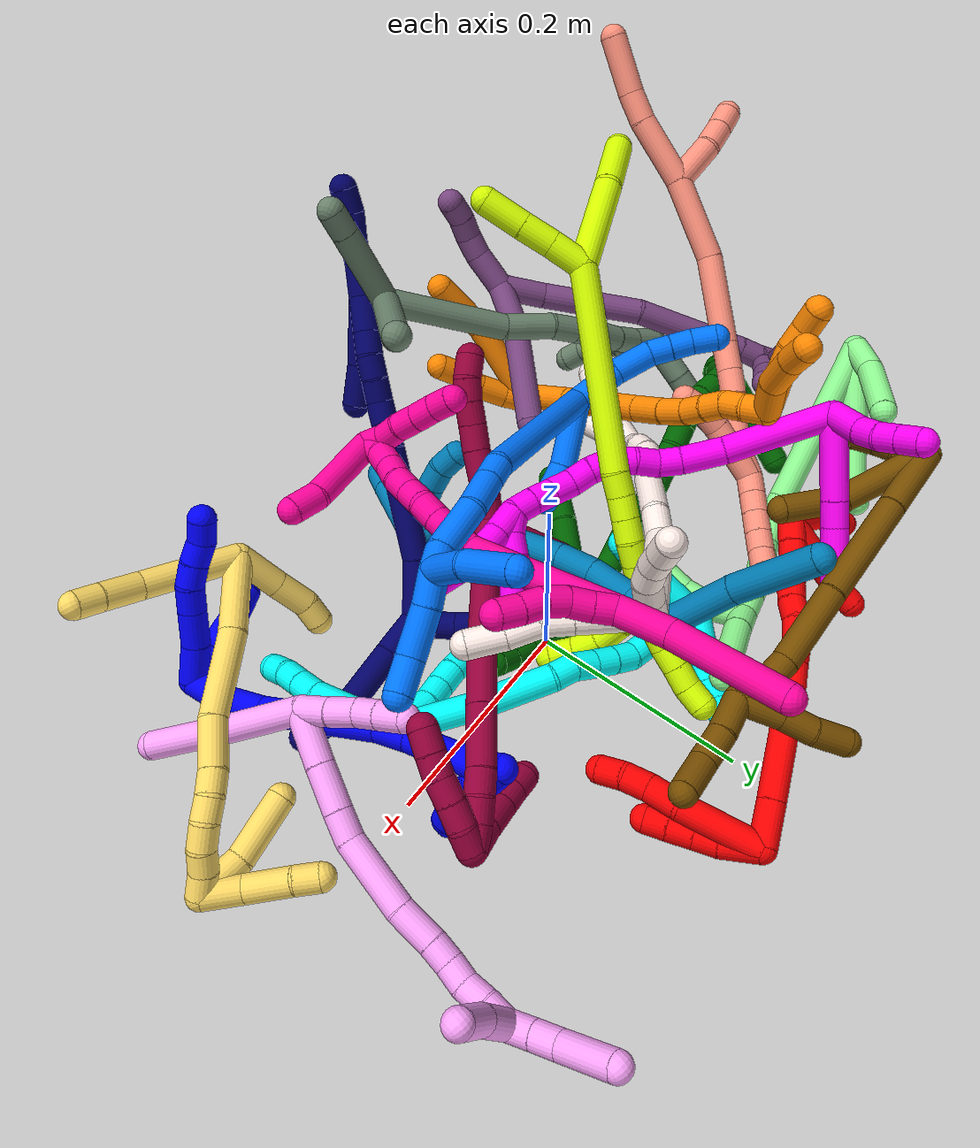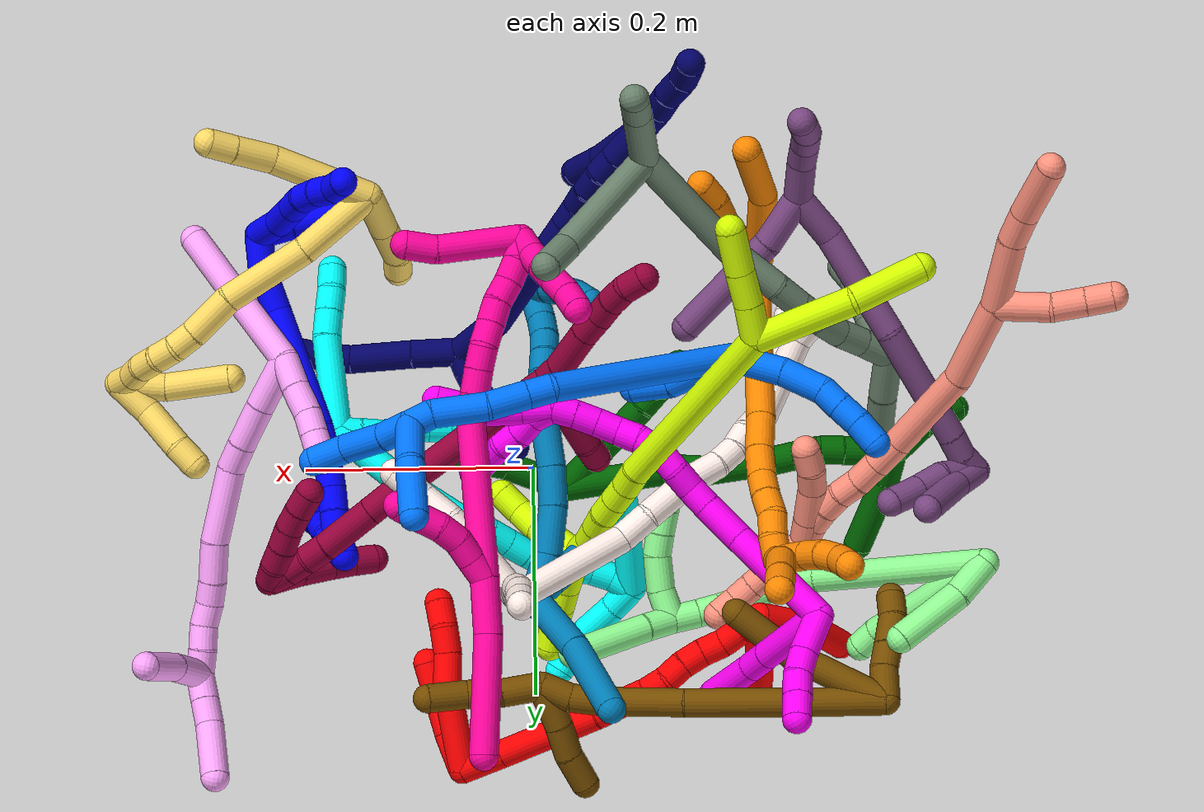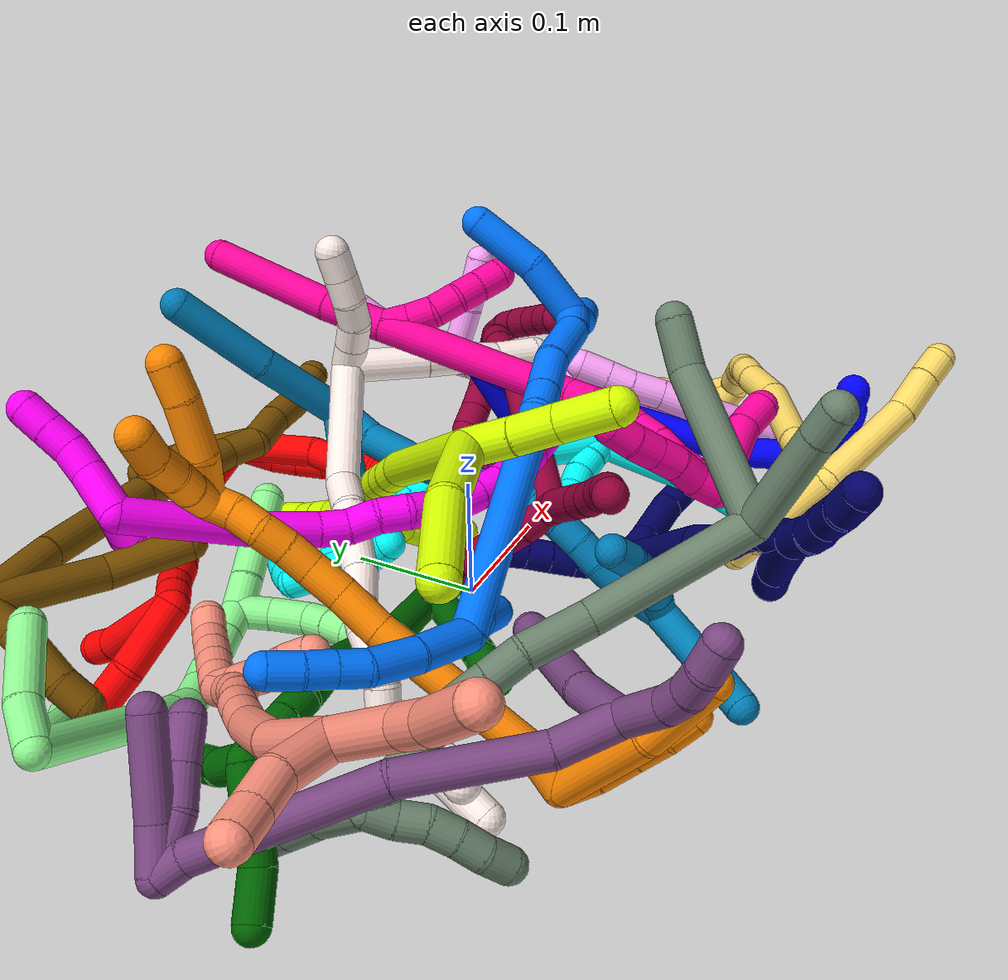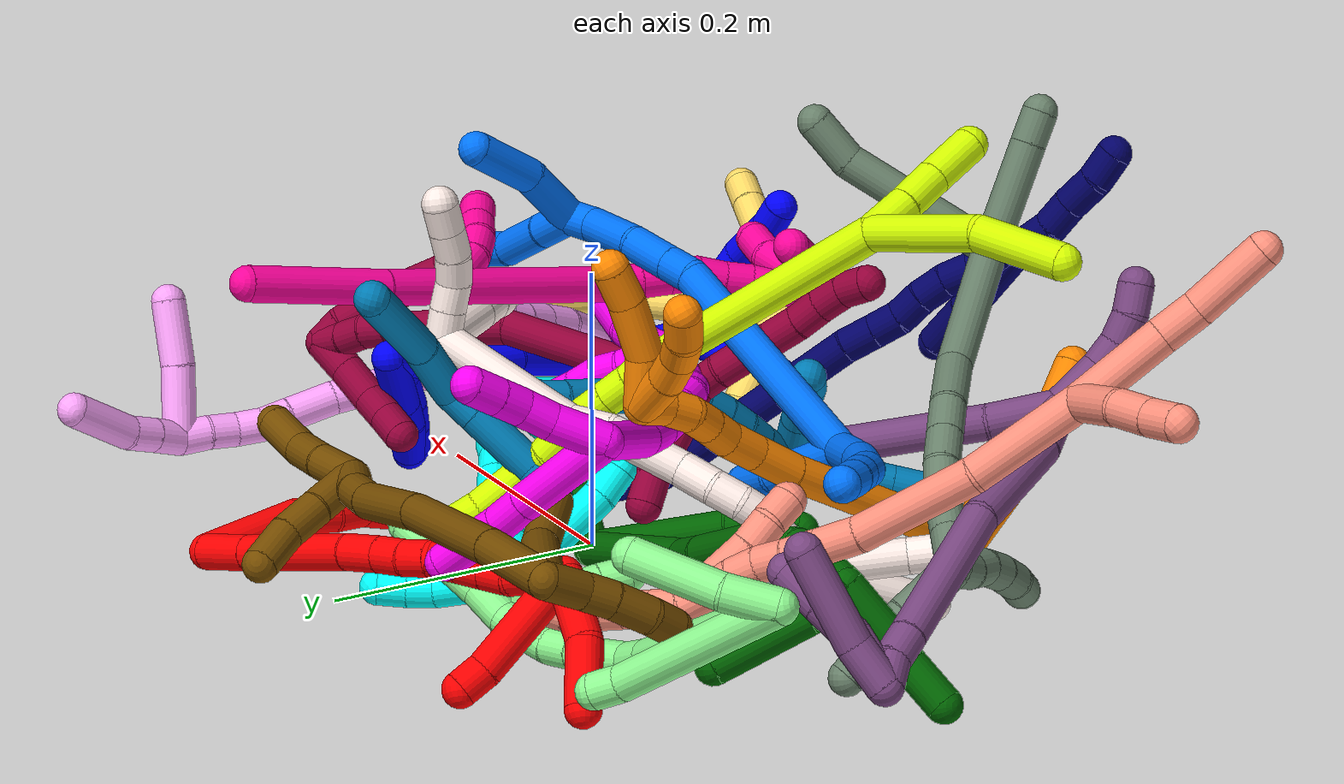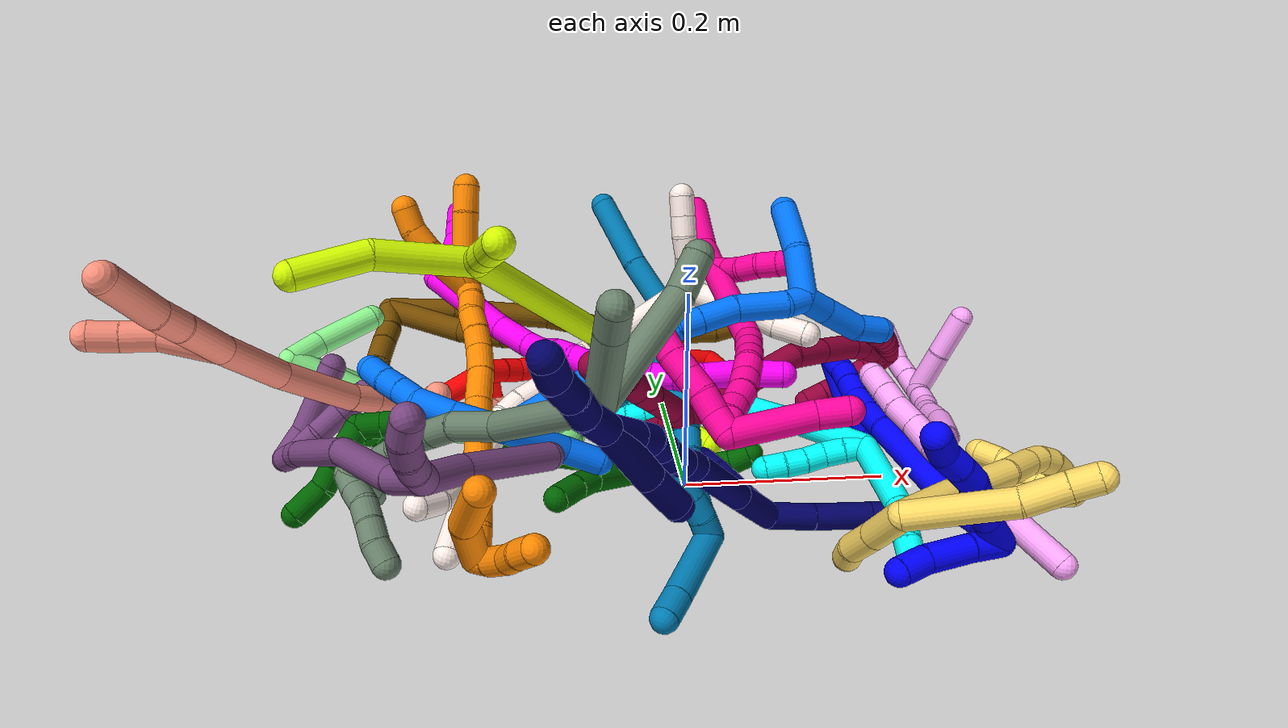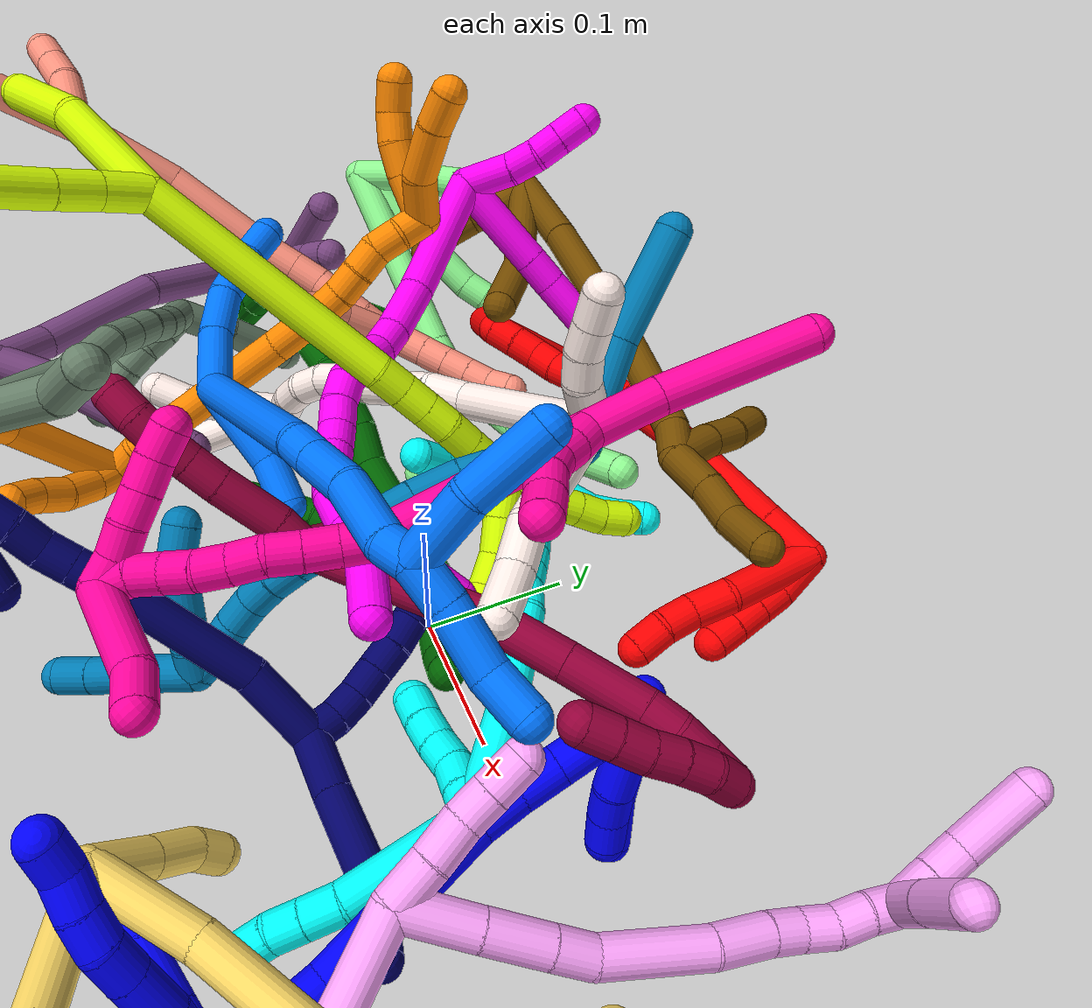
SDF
<sdf version="1.7">
 <world name="default">
  <plugin name="TubeGeneratorPlugin" filename="libtube_generator_plugin.so"/>
  <model name="photoneo_s_sensor">
   <static>1</static>
   <pose>0 0 2 1.57079 1.57079 3.14159</pose>
   <link name="link">
    <inertial><mass>0.1</mass></inertial>
    <sensor name="sensor" type="depth">
     <update_rate>30</update_rate>
     <camera>
      <horizontal_fov>1.22</horizontal_fov>
      <image><width>1920</width><height>1200</height><format>B8G8R8</format></image>
      <clip><near>0.1</near><far>4</far></clip>
      <depth_camera><output>points</output></depth_camera>
     </camera>
     <plugin name="camera_plugin" filename="libgazebo_ros_depth_camera.so">
      <baseline>0.2</baseline>
      <alwaysOn>1</alwaysOn>
      <updateRate>0.0</updateRate>
      <cameraName>camera_ir</cameraName>
      <imageTopicName>/camera/color/image_raw</imageTopicName>
      <cameraInfoTopicName>/camera/color/camera_info</cameraInfoTopicName>
      <depthImageTopicName>/camera/depth/image_raw</depthImageTopicName>
      <depthImageCameraInfoTopicName>/camera/depth/camera_info</depthImageCameraInfoTopicName>
      <pointCloudTopicName>/camera/depth/points</pointCloudTopicName>
      <frameName>fr_optical</frameName>
      <pointCloudCutoff>0.1</pointCloudCutoff>
      <pointCloudCutoffMax>2.0</pointCloudCutoffMax>
      <distortionK1>0</distortionK1>
      <distortionK2>0</distortionK2>
      <distortionK3>0</distortionK3>
      <distortionT1>0</distortionT1>
      <distortionT2>0</distortionT2>
      <CxPrime>0</CxPrime>
      <Cx>0</Cx>
      <Cy>0</Cy>
      <focalLength>0</focalLength>
      <hackBaseline>0</hackBaseline>
     </plugin>
    </sensor>
   </link>
  </model>
  <gravity>0 0 -9.8</gravity>
  <magnetic_field>6e-06 2.3e-05 -4.2e-05</magnetic_field>
  <atmosphere type="adiabatic"/>
  <physics name="default_physics" default="0" type="ode">
   <max_step_size>0.003</max_step_size>
   <real_time_factor>1</real_time_factor>
   <real_time_update_rate>1000</real_time_update_rate>
   <max_contacts>10000</max_contacts>
   <ode>
    <solver>
     <type>quick</type>
     <iters>100</iters>
     <sor>1.3</sor>
     <use_dynamic_moi_rescaling>0</use_dynamic_moi_rescaling>
    </solver>
    <constraints>
     <contact_max_correcting_vel>0</contact_max_correcting_vel>
     <contact_surface_layer>0.001</contact_surface_layer>
     <cfm>0</cfm>
     <erp>0.2</erp>
    </constraints>
   </ode>
  </physics>
  <scene><ambient>0.4 0.4 0.4 1</ambient><background>0.7 0.7 0.7 1</background><shadows>0</shadows></scene>
  <audio><device>default</device></audio>
  <spherical_coordinates>
   <surface_model>EARTH_WGS84</surface_model>
   <latitude_deg>0</latitude_deg>
   <longitude_deg>0</longitude_deg>
   <elevation>0</elevation>
   <heading_deg>0</heading_deg>
  </spherical_coordinates>
  <model name="bin">
   <static>1</static>
   <link name="bottom">
    <collision name="collision-bottom">
     <pose>0 0 -0.01 0 -0 0</pose>
     <geometry><box><size>0.8 0.6 0.02</size></box></geometry>
     <surface>
      <friction><ode><mu>100</mu><mu2>100</mu2></ode></friction>
      <contact><collide_bitmask>65535</collide_bitmask></contact>
     </surface>
    </collision>
   </link>
   <link name="west_wall">
    <collision name="collision-west_wall">
     <pose>-0.41 0 0.1 0 -0 0</pose>
     <geometry><box><size>0.02 0.6 0.2</size></box></geometry>
     <surface>
      <friction><ode><mu>100</mu><mu2>100</mu2></ode></friction>
      <contact><collide_bitmask>65535</collide_bitmask></contact>
     </surface>
    </collision>
   </link>
   <link name="east_wall">
    <collision name="collision-east_wall">
     <pose>0.41 0 0.1 0 -0 0</pose>
     <geometry><box><size>0.02 0.6 0.2</size></box></geometry>
     <surface>
      <friction><ode><mu>100</mu><mu2>100</mu2></ode></friction>
      <contact><collide_bitmask>65535</collide_bitmask></contact>
     </surface>
    </collision>
   </link>
   <link name="south_wall">
    <collision name="collision-south_wall">
     <pose>0 -0.31 0.1 0 -0 0</pose>
     <geometry><box><size>0.8 0.02 0.2</size></box></geometry>
     <surface>
      <friction><ode><mu>100</mu><mu2>100</mu2></ode></friction>
      <contact><collide_bitmask>65535</collide_bitmask></contact>
     </surface>
    </collision>
   </link>
   <link name="north_wall">
    <collision name="collision-north_wall">
     <pose>0 0.31 0.1 0 -0 0</pose>
     <geometry><box><size>0.8 0.02 0.2</size></box></geometry>
     <surface>
      <friction><ode><mu>100</mu><mu2>100</mu2></ode></friction>
      <contact><collide_bitmask>65535</collide_bitmask></contact>
     </surface>
    </collision>
   </link>
  </model>
  <model name="1">
   <static>0</static>
   <link name="1">
    <collision name="collision-cylinder-e_1_2_8">
     <pose>-0.012067 -0.006849 0.010627 0.572489 -0.762076 -0.234741</pose>
     <geometry><cylinder><radius>0.0125</radius><length>0.034955</length></cylinder></geometry>
     <surface>
      <friction><ode><mu>1.16</mu><mu2>1.16</mu2><slip1>0</slip1><slip2>0</slip2></ode></friction>
      <contact><ode><kp>1e+06</kp><kd>1</kd><max_vel>0</max_vel><min_depth>0.001</min_depth></ode></contact>
     </surface>
    </collision>
    <visual name="visual-cylinder-e_1_2_8">
     <pose>-0.012067 -0.006849 0.010627 0.572489 -0.762076 -0.234741</pose>
     <geometry><cylinder><radius>0.0125</radius><length>0.034955</length></cylinder></geometry>
     <material><ambient>0 0 1 1</ambient></material>
    </visual>
    <collision name="collision-cylinder-e_2_8_9">
     <pose>-0.033477 -0.021014 0.032367 0.582264 -0.612246 -0.188848</pose>
     <geometry><cylinder><radius>0.0125</radius><length>0.032513</length></cylinder></geometry>
     <surface>
      <friction><ode><mu>1.16</mu><mu2>1.16</mu2><slip1>0</slip1><slip2>0</slip2></ode></friction>
      <contact><ode><kp>1e+06</kp><kd>1</kd><max_vel>0</max_vel><min_depth>0.001</min_depth></ode></contact>
     </surface>
    </collision>
    <visual name="visual-cylinder-e_2_8_9">
     <pose>-0.033477 -0.021014 0.032367 0.582264 -0.612246 -0.188848</pose>
     <geometry><cylinder><radius>0.0125</radius><length>0.032513</length></cylinder></geometry>
     <material><ambient>0 0 1 1</ambient></material>
    </visual>
    <collision name="collision-cylinder-e_3_9_10">
     <pose>-0.049163 -0.03306 0.051085 0.556306 -0.616165 -0.181238</pose>
     <geometry><cylinder><radius>0.0125</radius><length>0.021951</length></cylinder></geometry>
     <surface>
      <friction><ode><mu>1.16</mu><mu2>1.16</mu2><slip1>0</slip1><slip2>0</slip2></ode></friction>
      <contact><ode><kp>1e+06</kp><kd>1</kd><max_vel>0</max_vel><min_depth>0.001</min_depth></ode></contact>
     </surface>
    </collision>
    <visual name="visual-cylinder-e_3_9_10">
     <pose>-0.049163 -0.03306 0.051085 0.556306 -0.616165 -0.181238</pose>
     <geometry><cylinder><radius>0.0125</radius><length>0.021951</length></cylinder></geometry>
     <material><ambient>0 0 1 1</ambient></material>
    </visual>
    <collision name="collision-cylinder-e_4_10_11">
     <pose>-0.063449 -0.041495 0.063756 0.631516 -0.902206 -0.313903</pose>
     <geometry><cylinder><radius>0.0125</radius><length>0.020245</length></cylinder></geometry>
     <surface>
      <friction><ode><mu>1.16</mu><mu2>1.16</mu2><slip1>0</slip1><slip2>0</slip2></ode></friction>
      <contact><ode><kp>1e+06</kp><kd>1</kd><max_vel>0</max_vel><min_depth>0.001</min_depth></ode></contact>
     </surface>
    </collision>
    <visual name="visual-cylinder-e_4_10_11">
     <pose>-0.063449 -0.041495 0.063756 0.631516 -0.902206 -0.313903</pose>
     <geometry><cylinder><radius>0.0125</radius><length>0.020245</length></cylinder></geometry>
     <material><ambient>0 0 1 1</ambient></material>
    </visual>
    <collision name="collision-cylinder-e_5_11_12">
     <pose>-0.080077 -0.047979 0.073311 0.554362 -1.02445 -0.317255</pose>
     <geometry><cylinder><radius>0.0125</radius><length>0.02033</length></cylinder></geometry>
     <surface>
      <friction><ode><mu>1.16</mu><mu2>1.16</mu2><slip1>0</slip1><slip2>0</slip2></ode></friction>
      <contact><ode><kp>1e+06</kp><kd>1</kd><max_vel>0</max_vel><min_depth>0.001</min_depth></ode></contact>
     </surface>
    </collision>
    <visual name="visual-cylinder-e_5_11_12">
     <pose>-0.080077 -0.047979 0.073311 0.554362 -1.02445 -0.317255</pose>
     <geometry><cylinder><radius>0.0125</radius><length>0.02033</length></cylinder></geometry>
     <material><ambient>0 0 1 1</ambient></material>
    </visual>
    <collision name="collision-cylinder-e_6_12_6">
     <pose>-0.095123 -0.054307 0.084657 0.477583 -0.68924 -0.174317</pose>
     <geometry><cylinder><radius>0.0125</radius><length>0.020005</length></cylinder></geometry>
     <surface>
      <friction><ode><mu>1.16</mu><mu2>1.16</mu2><slip1>0</slip1><slip2>0</slip2></ode></friction>
      <contact><ode><kp>1e+06</kp><kd>1</kd><max_vel>0</max_vel><min_depth>0.001</min_depth></ode></contact>
     </surface>
    </collision>
    <visual name="visual-cylinder-e_6_12_6">
     <pose>-0.095123 -0.054307 0.084657 0.477583 -0.68924 -0.174317</pose>
     <geometry><cylinder><radius>0.0125</radius><length>0.020005</length></cylinder></geometry>
     <material><ambient>0 0 1 1</ambient></material>
    </visual>
    <collision name="collision-cylinder-e_1_2_13">
     <pose>-0.013412 -0.006708 -0.003646 2.06865 -1.05326 -1.54827</pose>
     <geometry><cylinder><radius>0.0125</radius><length>0.030866</length></cylinder></geometry>
     <surface>
      <friction><ode><mu>1.16</mu><mu2>1.16</mu2><slip1>0</slip1><slip2>0</slip2></ode></friction>
      <contact><ode><kp>1e+06</kp><kd>1</kd><max_vel>0</max_vel><min_depth>0.001</min_depth></ode></contact>
     </surface>
    </collision>
    <visual name="visual-cylinder-e_1_2_13">
     <pose>-0.013412 -0.006708 -0.003646 2.06865 -1.05326 -1.54827</pose>
     <geometry><cylinder><radius>0.0125</radius><length>0.030866</length></cylinder></geometry>
     <material><ambient>0 0 1 1</ambient></material>
    </visual>
    <collision name="collision-cylinder-e_2_13_14">
     <pose>-0.044731 -0.022327 -0.014019 2.21746 -1.01335 -1.67891</pose>
     <geometry><cylinder><radius>0.0125</radius><length>0.042205</length></cylinder></geometry>
     <surface>
      <friction><ode><mu>1.16</mu><mu2>1.16</mu2><slip1>0</slip1><slip2>0</slip2></ode></friction>
      <contact><ode><kp>1e+06</kp><kd>1</kd><max_vel>0</max_vel><min_depth>0.001</min_depth></ode></contact>
     </surface>
    </collision>
    <visual name="visual-cylinder-e_2_13_14">
     <pose>-0.044731 -0.022327 -0.014019 2.21746 -1.01335 -1.67891</pose>
     <geometry><cylinder><radius>0.0125</radius><length>0.042205</length></cylinder></geometry>
     <material><ambient>0 0 1 1</ambient></material>
    </visual>
    <collision name="collision-cylinder-e_3_14_5">
     <pose>-0.072602 -0.038753 -0.025797 2.16255 -0.833028 -1.38598</pose>
     <geometry><cylinder><radius>0.0125</radius><length>0.02693</length></cylinder></geometry>
     <surface>
      <friction><ode><mu>1.16</mu><mu2>1.16</mu2><slip1>0</slip1><slip2>0</slip2></ode></friction>
      <contact><ode><kp>1e+06</kp><kd>1</kd><max_vel>0</max_vel><min_depth>0.001</min_depth></ode></contact>
     </surface>
    </collision>
    <visual name="visual-cylinder-e_3_14_5">
     <pose>-0.072602 -0.038753 -0.025797 2.16255 -0.833028 -1.38598</pose>
     <geometry><cylinder><radius>0.0125</radius><length>0.02693</length></cylinder></geometry>
     <material><ambient>0 0 1 1</ambient></material>
    </visual>
    <collision name="collision-cylinder-e_1_2_15">
     <pose>-0.00413 0.015208 -0.001024 -1.63801 -0.264618 0.282792</pose>
     <geometry><cylinder><radius>0.0125</radius><length>0.031584</length></cylinder></geometry>
     <surface>
      <friction><ode><mu>1.16</mu><mu2>1.16</mu2><slip1>0</slip1><slip2>0</slip2></ode></friction>
      <contact><ode><kp>1e+06</kp><kd>1</kd><max_vel>0</max_vel><min_depth>0.001</min_depth></ode></contact>
     </surface>
    </collision>
    <visual name="visual-cylinder-e_1_2_15">
     <pose>-0.00413 0.015208 -0.001024 -1.63801 -0.264618 0.282792</pose>
     <geometry><cylinder><radius>0.0125</radius><length>0.031584</length></cylinder></geometry>
     <material><ambient>0 0 1 1</ambient></material>
    </visual>
    <collision name="collision-cylinder-e_2_15_16">
     <pose>-0.017665 0.046784 -0.003788 -1.67671 -0.519076 0.574191</pose>
     <geometry><cylinder><radius>0.0125</radius><length>0.037915</length></cylinder></geometry>
     <surface>
      <friction><ode><mu>1.16</mu><mu2>1.16</mu2><slip1>0</slip1><slip2>0</slip2></ode></friction>
      <contact><ode><kp>1e+06</kp><kd>1</kd><max_vel>0</max_vel><min_depth>0.001</min_depth></ode></contact>
     </surface>
    </collision>
    <visual name="visual-cylinder-e_2_15_16">
     <pose>-0.017665 0.046784 -0.003788 -1.67671 -0.519076 0.574191</pose>
     <geometry><cylinder><radius>0.0125</radius><length>0.037915</length></cylinder></geometry>
     <material><ambient>0 0 1 1</ambient></material>
    </visual>
    <collision name="collision-cylinder-e_3_16_17">
     <pose>-0.05838 0.108894 0.003374 -1.37859 -0.591622 0.492143</pose>
     <geometry><cylinder><radius>0.0125</radius><length>0.112283</length></cylinder></geometry>
     <surface>
      <friction><ode><mu>1.16</mu><mu2>1.16</mu2><slip1>0</slip1><slip2>0</slip2></ode></friction>
      <contact><ode><kp>1e+06</kp><kd>1</kd><max_vel>0</max_vel><min_depth>0.001</min_depth></ode></contact>
     </surface>
    </collision>
    <visual name="visual-cylinder-e_3_16_17">
     <pose>-0.05838 0.108894 0.003374 -1.37859 -0.591622 0.492143</pose>
     <geometry><cylinder><radius>0.0125</radius><length>0.112283</length></cylinder></geometry>
     <material><ambient>0 0 1 1</ambient></material>
    </visual>
    <collision name="collision-cylinder-e_4_17_18">
     <pose>-0.095954 0.167148 0.012985 -1.51421 -0.463438 0.438762</pose>
     <geometry><cylinder><radius>0.0125</radius><length>0.028021</length></cylinder></geometry>
     <surface>
      <friction><ode><mu>1.16</mu><mu2>1.16</mu2><slip1>0</slip1><slip2>0</slip2></ode></friction>
      <contact><ode><kp>1e+06</kp><kd>1</kd><max_vel>0</max_vel><min_depth>0.001</min_depth></ode></contact>
     </surface>
    </collision>
    <visual name="visual-cylinder-e_4_17_18">
     <pose>-0.095954 0.167148 0.012985 -1.51421 -0.463438 0.438762</pose>
     <geometry><cylinder><radius>0.0125</radius><length>0.028021</length></cylinder></geometry>
     <material><ambient>0 0 1 1</ambient></material>
    </visual>
    <collision name="collision-cylinder-e_5_18_19">
     <pose>-0.10743 0.192203 0.015452 -1.43152 -0.3905 0.340624</pose>
     <geometry><cylinder><radius>0.0125</radius><length>0.027391</length></cylinder></geometry>
     <surface>
      <friction><ode><mu>1.16</mu><mu2>1.16</mu2><slip1>0</slip1><slip2>0</slip2></ode></friction>
      <contact><ode><kp>1e+06</kp><kd>1</kd><max_vel>0</max_vel><min_depth>0.001</min_depth></ode></contact>
     </surface>
    </collision>
    <visual name="visual-cylinder-e_5_18_19">
     <pose>-0.10743 0.192203 0.015452 -1.43152 -0.3905 0.340624</pose>
     <geometry><cylinder><radius>0.0125</radius><length>0.027391</length></cylinder></geometry>
     <material><ambient>0 0 1 1</ambient></material>
    </visual>
    <collision name="collision-cylinder-e_6_19_20">
     <pose>-0.116617 0.214586 0.02013 -1.28235 -0.36929 0.277018</pose>
     <geometry><cylinder><radius>0.0125</radius><length>0.022016</length></cylinder></geometry>
     <surface>
      <friction><ode><mu>1.16</mu><mu2>1.16</mu2><slip1>0</slip1><slip2>0</slip2></ode></friction>
      <contact><ode><kp>1e+06</kp><kd>1</kd><max_vel>0</max_vel><min_depth>0.001</min_depth></ode></contact>
     </surface>
    </collision>
    <visual name="visual-cylinder-e_6_19_20">
     <pose>-0.116617 0.214586 0.02013 -1.28235 -0.36929 0.277018</pose>
     <geometry><cylinder><radius>0.0125</radius><length>0.022016</length></cylinder></geometry>
     <material><ambient>0 0 1 1</ambient></material>
    </visual>
    <collision name="collision-cylinder-e_7_20_21">
     <pose>-0.124104 0.233652 0.025215 -1.34028 -0.355178 0.282574</pose>
     <geometry><cylinder><radius>0.0125</radius><length>0.020211</length></cylinder></geometry>
     <surface>
      <friction><ode><mu>1.16</mu><mu2>1.16</mu2><slip1>0</slip1><slip2>0</slip2></ode></friction>
      <contact><ode><kp>1e+06</kp><kd>1</kd><max_vel>0</max_vel><min_depth>0.001</min_depth></ode></contact>
     </surface>
    </collision>
    <visual name="visual-cylinder-e_7_20_21">
     <pose>-0.124104 0.233652 0.025215 -1.34028 -0.355178 0.282574</pose>
     <geometry><cylinder><radius>0.0125</radius><length>0.020211</length></cylinder></geometry>
     <material><ambient>0 0 1 1</ambient></material>
    </visual>
    <collision name="collision-cylinder-e_8_21_1">
     <pose>-0.133563 0.25095 0.029692 -1.29195 -0.616009 0.470768</pose>
     <geometry><cylinder><radius>0.0125</radius><length>0.020578</length></cylinder></geometry>
     <surface>
      <friction><ode><mu>1.16</mu><mu2>1.16</mu2><slip1>0</slip1><slip2>0</slip2></ode></friction>
      <contact><ode><kp>1e+06</kp><kd>1</kd><max_vel>0</max_vel><min_depth>0.001</min_depth></ode></contact>
     </surface>
    </collision>
    <visual name="visual-cylinder-e_8_21_1">
     <pose>-0.133563 0.25095 0.029692 -1.29195 -0.616009 0.470768</pose>
     <geometry><cylinder><radius>0.0125</radius><length>0.020578</length></cylinder></geometry>
     <material><ambient>0 0 1 1</ambient></material>
    </visual>
    <collision name="collision-cylinder-e_1_1_22">
     <pose>-0.12681 0.252319 0.022609 2.52177 0.833103 1.88858</pose>
     <geometry><cylinder><radius>0.0125</radius><length>0.034318</length></cylinder></geometry>
     <surface>
      <friction><ode><mu>1.16</mu><mu2>1.16</mu2><slip1>0</slip1><slip2>0</slip2></ode></friction>
      <contact><ode><kp>1e+06</kp><kd>1</kd><max_vel>0</max_vel><min_depth>0.001</min_depth></ode></contact>
     </surface>
    </collision>
    <visual name="visual-cylinder-e_1_1_22">
     <pose>-0.12681 0.252319 0.022609 2.52177 0.833103 1.88858</pose>
     <geometry><cylinder><radius>0.0125</radius><length>0.034318</length></cylinder></geometry>
     <material><ambient>0 0 1 1</ambient></material>
    </visual>
    <collision name="collision-cylinder-e_2_22_23">
     <pose>-0.106965 0.242149 0.0032 2.80839 0.593319 2.13573</pose>
     <geometry><cylinder><radius>0.0125</radius><length>0.025565</length></cylinder></geometry>
     <surface>
      <friction><ode><mu>1.16</mu><mu2>1.16</mu2><slip1>0</slip1><slip2>0</slip2></ode></friction>
      <contact><ode><kp>1e+06</kp><kd>1</kd><max_vel>0</max_vel><min_depth>0.001</min_depth></ode></contact>
     </surface>
    </collision>
    <visual name="visual-cylinder-e_2_22_23">
     <pose>-0.106965 0.242149 0.0032 2.80839 0.593319 2.13573</pose>
     <geometry><cylinder><radius>0.0125</radius><length>0.025565</length></cylinder></geometry>
     <material><ambient>0 0 1 1</ambient></material>
    </visual>
    <collision name="collision-cylinder-e_3_23_24">
     <pose>-0.094678 0.237516 -0.015355 3.00578 0.537715 2.65758</pose>
     <geometry><cylinder><radius>0.0125</radius><length>0.02007</length></cylinder></geometry>
     <surface>
      <friction><ode><mu>1.16</mu><mu2>1.16</mu2><slip1>0</slip1><slip2>0</slip2></ode></friction>
      <contact><ode><kp>1e+06</kp><kd>1</kd><max_vel>0</max_vel><min_depth>0.001</min_depth></ode></contact>
     </surface>
    </collision>
    <visual name="visual-cylinder-e_3_23_24">
     <pose>-0.094678 0.237516 -0.015355 3.00578 0.537715 2.65758</pose>
     <geometry><cylinder><radius>0.0125</radius><length>0.02007</length></cylinder></geometry>
     <material><ambient>0 0 1 1</ambient></material>
    </visual>
    <collision name="collision-cylinder-e_4_24_4">
     <pose>-0.083641 0.235598 -0.031964 3.04879 0.629055 2.85804</pose>
     <geometry><cylinder><radius>0.0125</radius><length>0.020047</length></cylinder></geometry>
     <surface>
      <friction><ode><mu>1.16</mu><mu2>1.16</mu2><slip1>0</slip1><slip2>0</slip2></ode></friction>
      <contact><ode><kp>1e+06</kp><kd>1</kd><max_vel>0</max_vel><min_depth>0.001</min_depth></ode></contact>
     </surface>
    </collision>
    <visual name="visual-cylinder-e_4_24_4">
     <pose>-0.083641 0.235598 -0.031964 3.04879 0.629055 2.85804</pose>
     <geometry><cylinder><radius>0.0125</radius><length>0.020047</length></cylinder></geometry>
     <material><ambient>0 0 1 1</ambient></material>
    </visual>
    <collision name="collision-cylinder-e_1_1_25">
     <pose>-0.125191 0.25284 0.013561 2.81807 0.634522 2.21914</pose>
     <geometry><cylinder><radius>0.0125</radius><length>0.048304</length></cylinder></geometry>
     <surface>
      <friction><ode><mu>1.16</mu><mu2>1.16</mu2><slip1>0</slip1><slip2>0</slip2></ode></friction>
      <contact><ode><kp>1e+06</kp><kd>1</kd><max_vel>0</max_vel><min_depth>0.001</min_depth></ode></contact>
     </surface>
    </collision>
    <visual name="visual-cylinder-e_1_1_25">
     <pose>-0.125191 0.25284 0.013561 2.81807 0.634522 2.21914</pose>
     <geometry><cylinder><radius>0.0125</radius><length>0.048304</length></cylinder></geometry>
     <material><ambient>0 0 1 1</ambient></material>
    </visual>
    <collision name="collision-cylinder-e_2_25_26">
     <pose>-0.10493 0.244182 -0.01258 2.83061 0.633796 2.24982</pose>
     <geometry><cylinder><radius>0.0125</radius><length>0.020074</length></cylinder></geometry>
     <surface>
      <friction><ode><mu>1.16</mu><mu2>1.16</mu2><slip1>0</slip1><slip2>0</slip2></ode></friction>
      <contact><ode><kp>1e+06</kp><kd>1</kd><max_vel>0</max_vel><min_depth>0.001</min_depth></ode></contact>
     </surface>
    </collision>
    <visual name="visual-cylinder-e_2_25_26">
     <pose>-0.10493 0.244182 -0.01258 2.83061 0.633796 2.24982</pose>
     <geometry><cylinder><radius>0.0125</radius><length>0.020074</length></cylinder></geometry>
     <material><ambient>0 0 1 1</ambient></material>
    </visual>
    <collision name="collision-cylinder-e_3_26_3">
     <pose>-0.088257 0.239746 -0.031727 2.97194 0.745801 2.71355</pose>
     <geometry><cylinder><radius>0.0125</radius><length>0.031622</length></cylinder></geometry>
     <surface>
      <friction><ode><mu>1.16</mu><mu2>1.16</mu2><slip1>0</slip1><slip2>0</slip2></ode></friction>
      <contact><ode><kp>1e+06</kp><kd>1</kd><max_vel>0</max_vel><min_depth>0.001</min_depth></ode></contact>
     </surface>
    </collision>
    <visual name="visual-cylinder-e_3_26_3">
     <pose>-0.088257 0.239746 -0.031727 2.97194 0.745801 2.71355</pose>
     <geometry><cylinder><radius>0.0125</radius><length>0.031622</length></cylinder></geometry>
     <material><ambient>0 0 1 1</ambient></material>
    </visual>
    <collision name="collision-sphere-3">
     <pose>-0.077528 0.237785 -0.043174 0 -0 0</pose>
     <geometry><sphere><radius>0.0125</radius></sphere></geometry>
     <surface>
      <friction><ode><mu>1.16</mu><mu2>1.16</mu2><slip1>0</slip1><slip2>0</slip2></ode></friction>
      <contact><ode><kp>1e+06</kp><kd>1</kd><max_vel>0</max_vel><min_depth>0.001</min_depth></ode></contact>
     </surface>
    </collision>
    <visual name="visual-sphere-3">
     <pose>-0.077528 0.237785 -0.043174 0 -0 0</pose>
     <geometry><sphere><radius>0.0125</radius></sphere></geometry>
     <material><ambient>0 0 1 1</ambient></material>
    </visual>
    <collision name="collision-sphere-26">
     <pose>-0.098986 0.241707 -0.02028 0 -0 0</pose>
     <geometry><sphere><radius>0.0125</radius></sphere></geometry>
     <surface>
      <friction><ode><mu>1.16</mu><mu2>1.16</mu2><slip1>0</slip1><slip2>0</slip2></ode></friction>
      <contact><ode><kp>1e+06</kp><kd>1</kd><max_vel>0</max_vel><min_depth>0.001</min_depth></ode></contact>
     </surface>
    </collision>
    <visual name="visual-sphere-26">
     <pose>-0.098986 0.241707 -0.02028 0 -0 0</pose>
     <geometry><sphere><radius>0.0125</radius></sphere></geometry>
     <material><ambient>0 0 1 1</ambient></material>
    </visual>
    <collision name="collision-sphere-25">
     <pose>-0.110874 0.246656 -0.00488 0 -0 0</pose>
     <geometry><sphere><radius>0.0125</radius></sphere></geometry>
     <surface>
      <friction><ode><mu>1.16</mu><mu2>1.16</mu2><slip1>0</slip1><slip2>0</slip2></ode></friction>
      <contact><ode><kp>1e+06</kp><kd>1</kd><max_vel>0</max_vel><min_depth>0.001</min_depth></ode></contact>
     </surface>
    </collision>
    <visual name="visual-sphere-25">
     <pose>-0.110874 0.246656 -0.00488 0 -0 0</pose>
     <geometry><sphere><radius>0.0125</radius></sphere></geometry>
     <material><ambient>0 0 1 1</ambient></material>
    </visual>
    <collision name="collision-sphere-4">
     <pose>-0.077744 0.234847 -0.040034 0 -0 0</pose>
     <geometry><sphere><radius>0.0125</radius></sphere></geometry>
     <surface>
      <friction><ode><mu>1.16</mu><mu2>1.16</mu2><slip1>0</slip1><slip2>0</slip2></ode></friction>
      <contact><ode><kp>1e+06</kp><kd>1</kd><max_vel>0</max_vel><min_depth>0.001</min_depth></ode></contact>
     </surface>
    </collision>
    <visual name="visual-sphere-4">
     <pose>-0.077744 0.234847 -0.040034 0 -0 0</pose>
     <geometry><sphere><radius>0.0125</radius></sphere></geometry>
     <material><ambient>0 0 1 1</ambient></material>
    </visual>
    <collision name="collision-sphere-24">
     <pose>-0.089539 0.236349 -0.023894 0 -0 0</pose>
     <geometry><sphere><radius>0.0125</radius></sphere></geometry>
     <surface>
      <friction><ode><mu>1.16</mu><mu2>1.16</mu2><slip1>0</slip1><slip2>0</slip2></ode></friction>
      <contact><ode><kp>1e+06</kp><kd>1</kd><max_vel>0</max_vel><min_depth>0.001</min_depth></ode></contact>
     </surface>
    </collision>
    <visual name="visual-sphere-24">
     <pose>-0.089539 0.236349 -0.023894 0 -0 0</pose>
     <geometry><sphere><radius>0.0125</radius></sphere></geometry>
     <material><ambient>0 0 1 1</ambient></material>
    </visual>
    <collision name="collision-sphere-23">
     <pose>-0.099818 0.238683 -0.006815 0 -0 0</pose>
     <geometry><sphere><radius>0.0125</radius></sphere></geometry>
     <surface>
      <friction><ode><mu>1.16</mu><mu2>1.16</mu2><slip1>0</slip1><slip2>0</slip2></ode></friction>
      <contact><ode><kp>1e+06</kp><kd>1</kd><max_vel>0</max_vel><min_depth>0.001</min_depth></ode></contact>
     </surface>
    </collision>
    <visual name="visual-sphere-23">
     <pose>-0.099818 0.238683 -0.006815 0 -0 0</pose>
     <geometry><sphere><radius>0.0125</radius></sphere></geometry>
     <material><ambient>0 0 1 1</ambient></material>
    </visual>
    <collision name="collision-sphere-22">
     <pose>-0.114112 0.245615 0.013215 0 -0 0</pose>
     <geometry><sphere><radius>0.0125</radius></sphere></geometry>
     <surface>
      <friction><ode><mu>1.16</mu><mu2>1.16</mu2><slip1>0</slip1><slip2>0</slip2></ode></friction>
      <contact><ode><kp>1e+06</kp><kd>1</kd><max_vel>0</max_vel><min_depth>0.001</min_depth></ode></contact>
     </surface>
    </collision>
    <visual name="visual-sphere-22">
     <pose>-0.114112 0.245615 0.013215 0 -0 0</pose>
     <geometry><sphere><radius>0.0125</radius></sphere></geometry>
     <material><ambient>0 0 1 1</ambient></material>
    </visual>
    <collision name="collision-sphere-1">
     <pose>-0.139508 0.259023 0.032003 0 -0 0</pose>
     <geometry><sphere><radius>0.0125</radius></sphere></geometry>
     <surface>
      <friction><ode><mu>1.16</mu><mu2>1.16</mu2><slip1>0</slip1><slip2>0</slip2></ode></friction>
      <contact><ode><kp>1e+06</kp><kd>1</kd><max_vel>0</max_vel><min_depth>0.001</min_depth></ode></contact>
     </surface>
    </collision>
    <visual name="visual-sphere-1">
     <pose>-0.139508 0.259023 0.032003 0 -0 0</pose>
     <geometry><sphere><radius>0.0125</radius></sphere></geometry>
     <material><ambient>0 0 1 1</ambient></material>
    </visual>
    <collision name="collision-sphere-21">
     <pose>-0.127618 0.242876 0.02738 0 -0 0</pose>
     <geometry><sphere><radius>0.0125</radius></sphere></geometry>
     <surface>
      <friction><ode><mu>1.16</mu><mu2>1.16</mu2><slip1>0</slip1><slip2>0</slip2></ode></friction>
      <contact><ode><kp>1e+06</kp><kd>1</kd><max_vel>0</max_vel><min_depth>0.001</min_depth></ode></contact>
     </surface>
    </collision>
    <visual name="visual-sphere-21">
     <pose>-0.127618 0.242876 0.02738 0 -0 0</pose>
     <geometry><sphere><radius>0.0125</radius></sphere></geometry>
     <material><ambient>0 0 1 1</ambient></material>
    </visual>
    <collision name="collision-sphere-12">
     <pose>-0.088762 -0.05076 0.077802 0 -0 0</pose>
     <geometry><sphere><radius>0.0125</radius></sphere></geometry>
     <surface>
      <friction><ode><mu>1.16</mu><mu2>1.16</mu2><slip1>0</slip1><slip2>0</slip2></ode></friction>
      <contact><ode><kp>1e+06</kp><kd>1</kd><max_vel>0</max_vel><min_depth>0.001</min_depth></ode></contact>
     </surface>
    </collision>
    <visual name="visual-sphere-12">
     <pose>-0.088762 -0.05076 0.077802 0 -0 0</pose>
     <geometry><sphere><radius>0.0125</radius></sphere></geometry>
     <material><ambient>0 0 1 1</ambient></material>
    </visual>
    <collision name="collision-sphere-11">
     <pose>-0.071392 -0.045199 0.06882 0 -0 0</pose>
     <geometry><sphere><radius>0.0125</radius></sphere></geometry>
     <surface>
      <friction><ode><mu>1.16</mu><mu2>1.16</mu2><slip1>0</slip1><slip2>0</slip2></ode></friction>
      <contact><ode><kp>1e+06</kp><kd>1</kd><max_vel>0</max_vel><min_depth>0.001</min_depth></ode></contact>
     </surface>
    </collision>
    <visual name="visual-sphere-11">
     <pose>-0.071392 -0.045199 0.06882 0 -0 0</pose>
     <geometry><sphere><radius>0.0125</radius></sphere></geometry>
     <material><ambient>0 0 1 1</ambient></material>
    </visual>
    <collision name="collision-sphere-10">
     <pose>-0.055505 -0.03779 0.058691 0 -0 0</pose>
     <geometry><sphere><radius>0.0125</radius></sphere></geometry>
     <surface>
      <friction><ode><mu>1.16</mu><mu2>1.16</mu2><slip1>0</slip1><slip2>0</slip2></ode></friction>
      <contact><ode><kp>1e+06</kp><kd>1</kd><max_vel>0</max_vel><min_depth>0.001</min_depth></ode></contact>
     </surface>
    </collision>
    <visual name="visual-sphere-10">
     <pose>-0.055505 -0.03779 0.058691 0 -0 0</pose>
     <geometry><sphere><radius>0.0125</radius></sphere></geometry>
     <material><ambient>0 0 1 1</ambient></material>
    </visual>
    <collision name="collision-sphere-9">
     <pose>-0.04282 -0.02833 0.043478 0 -0 0</pose>
     <geometry><sphere><radius>0.0125</radius></sphere></geometry>
     <surface>
      <friction><ode><mu>1.16</mu><mu2>1.16</mu2><slip1>0</slip1><slip2>0</slip2></ode></friction>
      <contact><ode><kp>1e+06</kp><kd>1</kd><max_vel>0</max_vel><min_depth>0.001</min_depth></ode></contact>
     </surface>
    </collision>
    <visual name="visual-sphere-9">
     <pose>-0.04282 -0.02833 0.043478 0 -0 0</pose>
     <geometry><sphere><radius>0.0125</radius></sphere></geometry>
     <material><ambient>0 0 1 1</ambient></material>
    </visual>
    <collision name="collision-sphere-2">
     <geometry><sphere><radius>0.0125</radius></sphere></geometry>
     <surface>
      <friction><ode><mu>1.16</mu><mu2>1.16</mu2><slip1>0</slip1><slip2>0</slip2></ode></friction>
      <contact><ode><kp>1e+06</kp><kd>1</kd><max_vel>0</max_vel><min_depth>0.001</min_depth></ode></contact>
     </surface>
    </collision>
    <visual name="visual-sphere-2">
     <geometry><sphere><radius>0.0125</radius></sphere></geometry>
     <material><ambient>0 0 1 1</ambient></material>
    </visual>
    <collision name="collision-sphere-19">
     <pose>-0.112643 0.204745 0.01721 0 -0 0</pose>
     <geometry><sphere><radius>0.0125</radius></sphere></geometry>
     <surface>
      <friction><ode><mu>1.16</mu><mu2>1.16</mu2><slip1>0</slip1><slip2>0</slip2></ode></friction>
      <contact><ode><kp>1e+06</kp><kd>1</kd><max_vel>0</max_vel><min_depth>0.001</min_depth></ode></contact>
     </surface>
    </collision>
    <visual name="visual-sphere-19">
     <pose>-0.112643 0.204745 0.01721 0 -0 0</pose>
     <geometry><sphere><radius>0.0125</radius></sphere></geometry>
     <material><ambient>0 0 1 1</ambient></material>
    </visual>
    <collision name="collision-sphere-8">
     <pose>-0.024134 -0.013699 0.021255 0 -0 0</pose>
     <geometry><sphere><radius>0.0125</radius></sphere></geometry>
     <surface>
      <friction><ode><mu>1.16</mu><mu2>1.16</mu2><slip1>0</slip1><slip2>0</slip2></ode></friction>
      <contact><ode><kp>1e+06</kp><kd>1</kd><max_vel>0</max_vel><min_depth>0.001</min_depth></ode></contact>
     </surface>
    </collision>
    <visual name="visual-sphere-8">
     <pose>-0.024134 -0.013699 0.021255 0 -0 0</pose>
     <geometry><sphere><radius>0.0125</radius></sphere></geometry>
     <material><ambient>0 0 1 1</ambient></material>
    </visual>
    <collision name="collision-sphere-6">
     <pose>-0.101484 -0.057855 0.091512 0 -0 0</pose>
     <geometry><sphere><radius>0.0125</radius></sphere></geometry>
     <surface>
      <friction><ode><mu>1.16</mu><mu2>1.16</mu2><slip1>0</slip1><slip2>0</slip2></ode></friction>
      <contact><ode><kp>1e+06</kp><kd>1</kd><max_vel>0</max_vel><min_depth>0.001</min_depth></ode></contact>
     </surface>
    </collision>
    <visual name="visual-sphere-6">
     <pose>-0.101484 -0.057855 0.091512 0 -0 0</pose>
     <geometry><sphere><radius>0.0125</radius></sphere></geometry>
     <material><ambient>0 0 1 1</ambient></material>
    </visual>
    <collision name="collision-sphere-13">
     <pose>-0.026823 -0.013417 -0.007292 0 -0 0</pose>
     <geometry><sphere><radius>0.0125</radius></sphere></geometry>
     <surface>
      <friction><ode><mu>1.16</mu><mu2>1.16</mu2><slip1>0</slip1><slip2>0</slip2></ode></friction>
      <contact><ode><kp>1e+06</kp><kd>1</kd><max_vel>0</max_vel><min_depth>0.001</min_depth></ode></contact>
     </surface>
    </collision>
    <visual name="visual-sphere-13">
     <pose>-0.026823 -0.013417 -0.007292 0 -0 0</pose>
     <geometry><sphere><radius>0.0125</radius></sphere></geometry>
     <material><ambient>0 0 1 1</ambient></material>
    </visual>
    <collision name="collision-sphere-14">
     <pose>-0.062639 -0.031236 -0.020745 0 -0 0</pose>
     <geometry><sphere><radius>0.0125</radius></sphere></geometry>
     <surface>
      <friction><ode><mu>1.16</mu><mu2>1.16</mu2><slip1>0</slip1><slip2>0</slip2></ode></friction>
      <contact><ode><kp>1e+06</kp><kd>1</kd><max_vel>0</max_vel><min_depth>0.001</min_depth></ode></contact>
     </surface>
    </collision>
    <visual name="visual-sphere-14">
     <pose>-0.062639 -0.031236 -0.020745 0 -0 0</pose>
     <geometry><sphere><radius>0.0125</radius></sphere></geometry>
     <material><ambient>0 0 1 1</ambient></material>
    </visual>
    <collision name="collision-sphere-5">
     <pose>-0.082566 -0.04627 -0.030849 0 -0 0</pose>
     <geometry><sphere><radius>0.0125</radius></sphere></geometry>
     <surface>
      <friction><ode><mu>1.16</mu><mu2>1.16</mu2><slip1>0</slip1><slip2>0</slip2></ode></friction>
      <contact><ode><kp>1e+06</kp><kd>1</kd><max_vel>0</max_vel><min_depth>0.001</min_depth></ode></contact>
     </surface>
    </collision>
    <visual name="visual-sphere-5">
     <pose>-0.082566 -0.04627 -0.030849 0 -0 0</pose>
     <geometry><sphere><radius>0.0125</radius></sphere></geometry>
     <material><ambient>0 0 1 1</ambient></material>
    </visual>
    <collision name="collision-sphere-15">
     <pose>-0.008261 0.030416 -0.002047 0 -0 0</pose>
     <geometry><sphere><radius>0.0125</radius></sphere></geometry>
     <surface>
      <friction><ode><mu>1.16</mu><mu2>1.16</mu2><slip1>0</slip1><slip2>0</slip2></ode></friction>
      <contact><ode><kp>1e+06</kp><kd>1</kd><max_vel>0</max_vel><min_depth>0.001</min_depth></ode></contact>
     </surface>
    </collision>
    <visual name="visual-sphere-15">
     <pose>-0.008261 0.030416 -0.002047 0 -0 0</pose>
     <geometry><sphere><radius>0.0125</radius></sphere></geometry>
     <material><ambient>0 0 1 1</ambient></material>
    </visual>
    <collision name="collision-sphere-16">
     <pose>-0.027069 0.063152 -0.005528 0 -0 0</pose>
     <geometry><sphere><radius>0.0125</radius></sphere></geometry>
     <surface>
      <friction><ode><mu>1.16</mu><mu2>1.16</mu2><slip1>0</slip1><slip2>0</slip2></ode></friction>
      <contact><ode><kp>1e+06</kp><kd>1</kd><max_vel>0</max_vel><min_depth>0.001</min_depth></ode></contact>
     </surface>
    </collision>
    <visual name="visual-sphere-16">
     <pose>-0.027069 0.063152 -0.005528 0 -0 0</pose>
     <geometry><sphere><radius>0.0125</radius></sphere></geometry>
     <material><ambient>0 0 1 1</ambient></material>
    </visual>
    <collision name="collision-sphere-17">
     <pose>-0.08969 0.154635 0.012276 0 -0 0</pose>
     <geometry><sphere><radius>0.0125</radius></sphere></geometry>
     <surface>
      <friction><ode><mu>1.16</mu><mu2>1.16</mu2><slip1>0</slip1><slip2>0</slip2></ode></friction>
      <contact><ode><kp>1e+06</kp><kd>1</kd><max_vel>0</max_vel><min_depth>0.001</min_depth></ode></contact>
     </surface>
    </collision>
    <visual name="visual-sphere-17">
     <pose>-0.08969 0.154635 0.012276 0 -0 0</pose>
     <geometry><sphere><radius>0.0125</radius></sphere></geometry>
     <material><ambient>0 0 1 1</ambient></material>
    </visual>
    <collision name="collision-sphere-18">
     <pose>-0.102217 0.179661 0.013694 0 -0 0</pose>
     <geometry><sphere><radius>0.0125</radius></sphere></geometry>
     <surface>
      <friction><ode><mu>1.16</mu><mu2>1.16</mu2><slip1>0</slip1><slip2>0</slip2></ode></friction>
      <contact><ode><kp>1e+06</kp><kd>1</kd><max_vel>0</max_vel><min_depth>0.001</min_depth></ode></contact>
     </surface>
    </collision>
    <visual name="visual-sphere-18">
     <pose>-0.102217 0.179661 0.013694 0 -0 0</pose>
     <geometry><sphere><radius>0.0125</radius></sphere></geometry>
     <material><ambient>0 0 1 1</ambient></material>
    </visual>
    <collision name="collision-sphere-20">
     <pose>-0.12059 0.224428 0.023051 0 -0 0</pose>
     <geometry><sphere><radius>0.0125</radius></sphere></geometry>
     <surface>
      <friction><ode><mu>1.16</mu><mu2>1.16</mu2><slip1>0</slip1><slip2>0</slip2></ode></friction>
      <contact><ode><kp>1e+06</kp><kd>1</kd><max_vel>0</max_vel><min_depth>0.001</min_depth></ode></contact>
     </surface>
    </collision>
    <visual name="visual-sphere-20">
     <pose>-0.12059 0.224428 0.023051 0 -0 0</pose>
     <geometry><sphere><radius>0.0125</radius></sphere></geometry>
     <material><ambient>0 0 1 1</ambient></material>
    </visual>
    <inertial>
     <pose>-0.072107 0.108444 0.009977 0 -0 0</pose>
     <mass>0.75</mass>
     <inertia>
      <ixx>0.000148</ixx>
      <ixy>0</ixy>
      <ixz>0</ixz>
      <iyy>0.000169</iyy>
      <iyz>0</iyz>
      <izz>-2.1e-05</izz>
     </inertia>
    </inertial>
   </link>
   <pose>0.236005 -0.206757 0.043789 -0.048619 0.280191 -0.199784</pose>
  </model>
  <model name="2">
   <static>0</static>
   <link name="2">
    <collision name="collision-cylinder-e_1_2_8">
     <pose>0.012177 -0.031545 0.015349 1.11795 0.334111 0.210183</pose>
     <geometry><cylinder><radius>0.0125</radius><length>0.074268</length></cylinder></geometry>
     <surface>
      <friction><ode><mu>1.16</mu><mu2>1.16</mu2><slip1>0</slip1><slip2>0</slip2></ode></friction>
      <contact><ode><kp>1e+06</kp><kd>1</kd><max_vel>0</max_vel><min_depth>0.001</min_depth></ode></contact>
     </surface>
    </collision>
    <visual name="visual-cylinder-e_1_2_8">
     <pose>0.012177 -0.031545 0.015349 1.11795 0.334111 0.210183</pose>
     <geometry><cylinder><radius>0.0125</radius><length>0.074268</length></cylinder></geometry>
     <material><ambient>1 0 0 1</ambient></material>
    </visual>
    <collision name="collision-cylinder-e_2_8_9">
     <pose>0.029449 -0.076719 0.032484 1.44045 0.354897 0.312161</pose>
     <geometry><cylinder><radius>0.0125</radius><length>0.02932</length></cylinder></geometry>
     <surface>
      <friction><ode><mu>1.16</mu><mu2>1.16</mu2><slip1>0</slip1><slip2>0</slip2></ode></friction>
      <contact><ode><kp>1e+06</kp><kd>1</kd><max_vel>0</max_vel><min_depth>0.001</min_depth></ode></contact>
     </surface>
    </collision>
    <visual name="visual-cylinder-e_2_8_9">
     <pose>0.029449 -0.076719 0.032484 1.44045 0.354897 0.312161</pose>
     <geometry><cylinder><radius>0.0125</radius><length>0.02932</length></cylinder></geometry>
     <material><ambient>1 0 0 1</ambient></material>
    </visual>
    <collision name="collision-cylinder-e_3_9_10">
     <pose>0.039412 -0.10044 0.037529 1.25844 0.430467 0.315628</pose>
     <geometry><cylinder><radius>0.0125</radius><length>0.023338</length></cylinder></geometry>
     <surface>
      <friction><ode><mu>1.16</mu><mu2>1.16</mu2><slip1>0</slip1><slip2>0</slip2></ode></friction>
      <contact><ode><kp>1e+06</kp><kd>1</kd><max_vel>0</max_vel><min_depth>0.001</min_depth></ode></contact>
     </surface>
    </collision>
    <visual name="visual-cylinder-e_3_9_10">
     <pose>0.039412 -0.10044 0.037529 1.25844 0.430467 0.315628</pose>
     <geometry><cylinder><radius>0.0125</radius><length>0.023338</length></cylinder></geometry>
     <material><ambient>1 0 0 1</ambient></material>
    </visual>
    <collision name="collision-cylinder-e_4_10_6">
     <pose>0.051069 -0.119791 0.041927 1.44838 0.628894 0.560224</pose>
     <geometry><cylinder><radius>0.0125</radius><length>0.023075</length></cylinder></geometry>
     <surface>
      <friction><ode><mu>1.16</mu><mu2>1.16</mu2><slip1>0</slip1><slip2>0</slip2></ode></friction>
      <contact><ode><kp>1e+06</kp><kd>1</kd><max_vel>0</max_vel><min_depth>0.001</min_depth></ode></contact>
     </surface>
    </collision>
    <visual name="visual-cylinder-e_4_10_6">
     <pose>0.051069 -0.119791 0.041927 1.44838 0.628894 0.560224</pose>
     <geometry><cylinder><radius>0.0125</radius><length>0.023075</length></cylinder></geometry>
     <material><ambient>1 0 0 1</ambient></material>
    </visual>
    <collision name="collision-cylinder-e_1_2_11">
     <pose>0.012128 -0.012374 0.003499 1.29521 0.756153 0.583725</pose>
     <geometry><cylinder><radius>0.0125</radius><length>0.035352</length></cylinder></geometry>
     <surface>
      <friction><ode><mu>1.16</mu><mu2>1.16</mu2><slip1>0</slip1><slip2>0</slip2></ode></friction>
      <contact><ode><kp>1e+06</kp><kd>1</kd><max_vel>0</max_vel><min_depth>0.001</min_depth></ode></contact>
     </surface>
    </collision>
    <visual name="visual-cylinder-e_1_2_11">
     <pose>0.012128 -0.012374 0.003499 1.29521 0.756153 0.583725</pose>
     <geometry><cylinder><radius>0.0125</radius><length>0.035352</length></cylinder></geometry>
     <material><ambient>1 0 0 1</ambient></material>
    </visual>
    <collision name="collision-cylinder-e_2_11_12">
     <pose>0.029661 -0.033377 0.010783 1.15745 0.520752 0.344682</pose>
     <geometry><cylinder><radius>0.0125</radius><length>0.021727</length></cylinder></geometry>
     <surface>
      <friction><ode><mu>1.16</mu><mu2>1.16</mu2><slip1>0</slip1><slip2>0</slip2></ode></friction>
      <contact><ode><kp>1e+06</kp><kd>1</kd><max_vel>0</max_vel><min_depth>0.001</min_depth></ode></contact>
     </surface>
    </collision>
    <visual name="visual-cylinder-e_2_11_12">
     <pose>0.029661 -0.033377 0.010783 1.15745 0.520752 0.344682</pose>
     <geometry><cylinder><radius>0.0125</radius><length>0.021727</length></cylinder></geometry>
     <material><ambient>1 0 0 1</ambient></material>
    </visual>
    <collision name="collision-cylinder-e_3_12_13">
     <pose>0.040658 -0.050922 0.018892 1.11924 0.513817 0.326216</pose>
     <geometry><cylinder><radius>0.0125</radius><length>0.022754</length></cylinder></geometry>
     <surface>
      <friction><ode><mu>1.16</mu><mu2>1.16</mu2><slip1>0</slip1><slip2>0</slip2></ode></friction>
      <contact><ode><kp>1e+06</kp><kd>1</kd><max_vel>0</max_vel><min_depth>0.001</min_depth></ode></contact>
     </surface>
    </collision>
    <visual name="visual-cylinder-e_3_12_13">
     <pose>0.040658 -0.050922 0.018892 1.11924 0.513817 0.326216</pose>
     <geometry><cylinder><radius>0.0125</radius><length>0.022754</length></cylinder></geometry>
     <material><ambient>1 0 0 1</ambient></material>
    </visual>
    <collision name="collision-cylinder-e_4_13_5">
     <pose>0.05116 -0.06786 0.026849 1.14558 0.508622 0.332185</pose>
     <geometry><cylinder><radius>0.0125</radius><length>0.020167</length></cylinder></geometry>
     <surface>
      <friction><ode><mu>1.16</mu><mu2>1.16</mu2><slip1>0</slip1><slip2>0</slip2></ode></friction>
      <contact><ode><kp>1e+06</kp><kd>1</kd><max_vel>0</max_vel><min_depth>0.001</min_depth></ode></contact>
     </surface>
    </collision>
    <visual name="visual-cylinder-e_4_13_5">
     <pose>0.05116 -0.06786 0.026849 1.14558 0.508622 0.332185</pose>
     <geometry><cylinder><radius>0.0125</radius><length>0.020167</length></cylinder></geometry>
     <material><ambient>1 0 0 1</ambient></material>
    </visual>
    <collision name="collision-cylinder-e_1_2_14">
     <pose>-0.013711 -0.013073 -0.00551 1.96972 -0.768361 -1.09421</pose>
     <geometry><cylinder><radius>0.0125</radius><length>0.039459</length></cylinder></geometry>
     <surface>
      <friction><ode><mu>1.16</mu><mu2>1.16</mu2><slip1>0</slip1><slip2>0</slip2></ode></friction>
      <contact><ode><kp>1e+06</kp><kd>1</kd><max_vel>0</max_vel><min_depth>0.001</min_depth></ode></contact>
     </surface>
    </collision>
    <visual name="visual-cylinder-e_1_2_14">
     <pose>-0.013711 -0.013073 -0.00551 1.96972 -0.768361 -1.09421</pose>
     <geometry><cylinder><radius>0.0125</radius><length>0.039459</length></cylinder></geometry>
     <material><ambient>1 0 0 1</ambient></material>
    </visual>
    <collision name="collision-cylinder-e_2_14_15">
     <pose>-0.059688 -0.056703 -0.022318 1.9249 -0.780559 -1.06706</pose>
     <geometry><cylinder><radius>0.0125</radius><length>0.091704</length></cylinder></geometry>
     <surface>
      <friction><ode><mu>1.16</mu><mu2>1.16</mu2><slip1>0</slip1><slip2>0</slip2></ode></friction>
      <contact><ode><kp>1e+06</kp><kd>1</kd><max_vel>0</max_vel><min_depth>0.001</min_depth></ode></contact>
     </surface>
    </collision>
    <visual name="visual-cylinder-e_2_14_15">
     <pose>-0.059688 -0.056703 -0.022318 1.9249 -0.780559 -1.06706</pose>
     <geometry><cylinder><radius>0.0125</radius><length>0.091704</length></cylinder></geometry>
     <material><ambient>1 0 0 1</ambient></material>
    </visual>
    <collision name="collision-cylinder-e_3_15_16">
     <pose>-0.100535 -0.097308 -0.037678 1.95512 -0.669782 -0.952926</pose>
     <geometry><cylinder><radius>0.0125</radius><length>0.027651</length></cylinder></geometry>
     <surface>
      <friction><ode><mu>1.16</mu><mu2>1.16</mu2><slip1>0</slip1><slip2>0</slip2></ode></friction>
      <contact><ode><kp>1e+06</kp><kd>1</kd><max_vel>0</max_vel><min_depth>0.001</min_depth></ode></contact>
     </surface>
    </collision>
    <visual name="visual-cylinder-e_3_15_16">
     <pose>-0.100535 -0.097308 -0.037678 1.95512 -0.669782 -0.952926</pose>
     <geometry><cylinder><radius>0.0125</radius><length>0.027651</length></cylinder></geometry>
     <material><ambient>1 0 0 1</ambient></material>
    </visual>
    <collision name="collision-cylinder-e_4_16_17">
     <pose>-0.11561 -0.114692 -0.045301 2.02261 -0.672386 -1.01797</pose>
     <geometry><cylinder><radius>0.0125</radius><length>0.020844</length></cylinder></geometry>
     <surface>
      <friction><ode><mu>1.16</mu><mu2>1.16</mu2><slip1>0</slip1><slip2>0</slip2></ode></friction>
      <contact><ode><kp>1e+06</kp><kd>1</kd><max_vel>0</max_vel><min_depth>0.001</min_depth></ode></contact>
     </surface>
    </collision>
    <visual name="visual-cylinder-e_4_16_17">
     <pose>-0.11561 -0.114692 -0.045301 2.02261 -0.672386 -1.01797</pose>
     <geometry><cylinder><radius>0.0125</radius><length>0.020844</length></cylinder></geometry>
     <material><ambient>1 0 0 1</ambient></material>
    </visual>
    <collision name="collision-cylinder-e_5_17_18">
     <pose>-0.127845 -0.129955 -0.051331 1.87287 -0.605163 -0.802462</pose>
     <geometry><cylinder><radius>0.0125</radius><length>0.020193</length></cylinder></geometry>
     <surface>
      <friction><ode><mu>1.16</mu><mu2>1.16</mu2><slip1>0</slip1><slip2>0</slip2></ode></friction>
      <contact><ode><kp>1e+06</kp><kd>1</kd><max_vel>0</max_vel><min_depth>0.001</min_depth></ode></contact>
     </surface>
    </collision>
    <visual name="visual-cylinder-e_5_17_18">
     <pose>-0.127845 -0.129955 -0.051331 1.87287 -0.605163 -0.802462</pose>
     <geometry><cylinder><radius>0.0125</radius><length>0.020193</length></cylinder></geometry>
     <material><ambient>1 0 0 1</ambient></material>
    </visual>
    <collision name="collision-cylinder-e_6_18_19">
     <pose>-0.136659 -0.146798 -0.057224 1.93733 -0.311022 -0.448554</pose>
     <geometry><cylinder><radius>0.0125</radius><length>0.020062</length></cylinder></geometry>
     <surface>
      <friction><ode><mu>1.16</mu><mu2>1.16</mu2><slip1>0</slip1><slip2>0</slip2></ode></friction>
      <contact><ode><kp>1e+06</kp><kd>1</kd><max_vel>0</max_vel><min_depth>0.001</min_depth></ode></contact>
     </surface>
    </collision>
    <visual name="visual-cylinder-e_6_18_19">
     <pose>-0.136659 -0.146798 -0.057224 1.93733 -0.311022 -0.448554</pose>
     <geometry><cylinder><radius>0.0125</radius><length>0.020062</length></cylinder></geometry>
     <material><ambient>1 0 0 1</ambient></material>
    </visual>
    <collision name="collision-cylinder-e_7_19_20">
     <pose>-0.144216 -0.163701 -0.064695 2.0399 -0.464505 -0.73509</pose>
     <geometry><cylinder><radius>0.0125</radius><length>0.020035</length></cylinder></geometry>
     <surface>
      <friction><ode><mu>1.16</mu><mu2>1.16</mu2><slip1>0</slip1><slip2>0</slip2></ode></friction>
      <contact><ode><kp>1e+06</kp><kd>1</kd><max_vel>0</max_vel><min_depth>0.001</min_depth></ode></contact>
     </surface>
    </collision>
    <visual name="visual-cylinder-e_7_19_20">
     <pose>-0.144216 -0.163701 -0.064695 2.0399 -0.464505 -0.73509</pose>
     <geometry><cylinder><radius>0.0125</radius><length>0.020035</length></cylinder></geometry>
     <material><ambient>1 0 0 1</ambient></material>
    </visual>
    <collision name="collision-cylinder-e_8_20_21">
     <pose>-0.154464 -0.178817 -0.072802 2.08834 -0.612318 -0.995973</pose>
     <geometry><cylinder><radius>0.0125</radius><length>0.020044</length></cylinder></geometry>
     <surface>
      <friction><ode><mu>1.16</mu><mu2>1.16</mu2><slip1>0</slip1><slip2>0</slip2></ode></friction>
      <contact><ode><kp>1e+06</kp><kd>1</kd><max_vel>0</max_vel><min_depth>0.001</min_depth></ode></contact>
     </surface>
    </collision>
    <visual name="visual-cylinder-e_8_20_21">
     <pose>-0.154464 -0.178817 -0.072802 2.08834 -0.612318 -0.995973</pose>
     <geometry><cylinder><radius>0.0125</radius><length>0.020044</length></cylinder></geometry>
     <material><ambient>1 0 0 1</ambient></material>
    </visual>
    <collision name="collision-cylinder-e_9_21_22">
     <pose>-0.165873 -0.194089 -0.078211 1.73521 -0.600004 -0.699756</pose>
     <geometry><cylinder><radius>0.0125</radius><length>0.020007</length></cylinder></geometry>
     <surface>
      <friction><ode><mu>1.16</mu><mu2>1.16</mu2><slip1>0</slip1><slip2>0</slip2></ode></friction>
      <contact><ode><kp>1e+06</kp><kd>1</kd><max_vel>0</max_vel><min_depth>0.001</min_depth></ode></contact>
     </surface>
    </collision>
    <visual name="visual-cylinder-e_9_21_22">
     <pose>-0.165873 -0.194089 -0.078211 1.73521 -0.600004 -0.699756</pose>
     <geometry><cylinder><radius>0.0125</radius><length>0.020007</length></cylinder></geometry>
     <material><ambient>1 0 0 1</ambient></material>
    </visual>
    <collision name="collision-cylinder-e_10_22_1">
     <pose>-0.177029 -0.210344 -0.081538 1.8098 -0.58328 -0.730012</pose>
     <geometry><cylinder><radius>0.0125</radius><length>0.020001</length></cylinder></geometry>
     <surface>
      <friction><ode><mu>1.16</mu><mu2>1.16</mu2><slip1>0</slip1><slip2>0</slip2></ode></friction>
      <contact><ode><kp>1e+06</kp><kd>1</kd><max_vel>0</max_vel><min_depth>0.001</min_depth></ode></contact>
     </surface>
    </collision>
    <visual name="visual-cylinder-e_10_22_1">
     <pose>-0.177029 -0.210344 -0.081538 1.8098 -0.58328 -0.730012</pose>
     <geometry><cylinder><radius>0.0125</radius><length>0.020001</length></cylinder></geometry>
     <material><ambient>1 0 0 1</ambient></material>
    </visual>
    <collision name="collision-cylinder-e_1_1_23">
     <pose>-0.173115 -0.191561 -0.111483 -2.37582 0.238217 -0.577654</pose>
     <geometry><cylinder><radius>0.0125</radius><length>0.079856</length></cylinder></geometry>
     <surface>
      <friction><ode><mu>1.16</mu><mu2>1.16</mu2><slip1>0</slip1><slip2>0</slip2></ode></friction>
      <contact><ode><kp>1e+06</kp><kd>1</kd><max_vel>0</max_vel><min_depth>0.001</min_depth></ode></contact>
     </surface>
    </collision>
    <visual name="visual-cylinder-e_1_1_23">
     <pose>-0.173115 -0.191561 -0.111483 -2.37582 0.238217 -0.577654</pose>
     <geometry><cylinder><radius>0.0125</radius><length>0.079856</length></cylinder></geometry>
     <material><ambient>1 0 0 1</ambient></material>
    </visual>
    <collision name="collision-cylinder-e_2_23_4">
     <pose>-0.162464 -0.156624 -0.145387 -2.20637 0.122376 -0.24147</pose>
     <geometry><cylinder><radius>0.0125</radius><length>0.020144</length></cylinder></geometry>
     <surface>
      <friction><ode><mu>1.16</mu><mu2>1.16</mu2><slip1>0</slip1><slip2>0</slip2></ode></friction>
      <contact><ode><kp>1e+06</kp><kd>1</kd><max_vel>0</max_vel><min_depth>0.001</min_depth></ode></contact>
     </surface>
    </collision>
    <visual name="visual-cylinder-e_2_23_4">
     <pose>-0.162464 -0.156624 -0.145387 -2.20637 0.122376 -0.24147</pose>
     <geometry><cylinder><radius>0.0125</radius><length>0.020144</length></cylinder></geometry>
     <material><ambient>1 0 0 1</ambient></material>
    </visual>
    <collision name="collision-cylinder-e_1_1_24">
     <pose>-0.190211 -0.222419 -0.108579 2.98468 -0.293651 -2.1644</pose>
     <geometry><cylinder><radius>0.0125</radius><length>0.053024</length></cylinder></geometry>
     <surface>
      <friction><ode><mu>1.16</mu><mu2>1.16</mu2><slip1>0</slip1><slip2>0</slip2></ode></friction>
      <contact><ode><kp>1e+06</kp><kd>1</kd><max_vel>0</max_vel><min_depth>0.001</min_depth></ode></contact>
     </surface>
    </collision>
    <visual name="visual-cylinder-e_1_1_24">
     <pose>-0.190211 -0.222419 -0.108579 2.98468 -0.293651 -2.1644</pose>
     <geometry><cylinder><radius>0.0125</radius><length>0.053024</length></cylinder></geometry>
     <material><ambient>1 0 0 1</ambient></material>
    </visual>
    <collision name="collision-cylinder-e_2_24_3">
     <pose>-0.20037 -0.223896 -0.156868 -3.03484 -0.106016 1.5639</pose>
     <geometry><cylinder><radius>0.0125</radius><length>0.046976</length></cylinder></geometry>
     <surface>
      <friction><ode><mu>1.16</mu><mu2>1.16</mu2><slip1>0</slip1><slip2>0</slip2></ode></friction>
      <contact><ode><kp>1e+06</kp><kd>1</kd><max_vel>0</max_vel><min_depth>0.001</min_depth></ode></contact>
     </surface>
    </collision>
    <visual name="visual-cylinder-e_2_24_3">
     <pose>-0.20037 -0.223896 -0.156868 -3.03484 -0.106016 1.5639</pose>
     <geometry><cylinder><radius>0.0125</radius><length>0.046976</length></cylinder></geometry>
     <material><ambient>1 0 0 1</ambient></material>
    </visual>
    <collision name="collision-sphere-3">
     <pose>-0.202856 -0.221408 -0.180091 0 -0 0</pose>
     <geometry><sphere><radius>0.0125</radius></sphere></geometry>
     <surface>
      <friction><ode><mu>1.16</mu><mu2>1.16</mu2><slip1>0</slip1><slip2>0</slip2></ode></friction>
      <contact><ode><kp>1e+06</kp><kd>1</kd><max_vel>0</max_vel><min_depth>0.001</min_depth></ode></contact>
     </surface>
    </collision>
    <visual name="visual-sphere-3">
     <pose>-0.202856 -0.221408 -0.180091 0 -0 0</pose>
     <geometry><sphere><radius>0.0125</radius></sphere></geometry>
     <material><ambient>1 0 0 1</ambient></material>
    </visual>
    <collision name="collision-sphere-24">
     <pose>-0.197885 -0.226385 -0.133644 0 -0 0</pose>
     <geometry><sphere><radius>0.0125</radius></sphere></geometry>
     <surface>
      <friction><ode><mu>1.16</mu><mu2>1.16</mu2><slip1>0</slip1><slip2>0</slip2></ode></friction>
      <contact><ode><kp>1e+06</kp><kd>1</kd><max_vel>0</max_vel><min_depth>0.001</min_depth></ode></contact>
     </surface>
    </collision>
    <visual name="visual-sphere-24">
     <pose>-0.197885 -0.226385 -0.133644 0 -0 0</pose>
     <geometry><sphere><radius>0.0125</radius></sphere></geometry>
     <material><ambient>1 0 0 1</ambient></material>
    </visual>
    <collision name="collision-sphere-4">
     <pose>-0.161235 -0.14858 -0.151321 0 -0 0</pose>
     <geometry><sphere><radius>0.0125</radius></sphere></geometry>
     <surface>
      <friction><ode><mu>1.16</mu><mu2>1.16</mu2><slip1>0</slip1><slip2>0</slip2></ode></friction>
      <contact><ode><kp>1e+06</kp><kd>1</kd><max_vel>0</max_vel><min_depth>0.001</min_depth></ode></contact>
     </surface>
    </collision>
    <visual name="visual-sphere-4">
     <pose>-0.161235 -0.14858 -0.151321 0 -0 0</pose>
     <geometry><sphere><radius>0.0125</radius></sphere></geometry>
     <material><ambient>1 0 0 1</ambient></material>
    </visual>
    <collision name="collision-sphere-23">
     <pose>-0.163694 -0.164669 -0.139452 0 -0 0</pose>
     <geometry><sphere><radius>0.0125</radius></sphere></geometry>
     <surface>
      <friction><ode><mu>1.16</mu><mu2>1.16</mu2><slip1>0</slip1><slip2>0</slip2></ode></friction>
      <contact><ode><kp>1e+06</kp><kd>1</kd><max_vel>0</max_vel><min_depth>0.001</min_depth></ode></contact>
     </surface>
    </collision>
    <visual name="visual-sphere-23">
     <pose>-0.163694 -0.164669 -0.139452 0 -0 0</pose>
     <geometry><sphere><radius>0.0125</radius></sphere></geometry>
     <material><ambient>1 0 0 1</ambient></material>
    </visual>
    <collision name="collision-sphere-1">
     <pose>-0.182537 -0.218453 -0.083514 0 -0 0</pose>
     <geometry><sphere><radius>0.0125</radius></sphere></geometry>
     <surface>
      <friction><ode><mu>1.16</mu><mu2>1.16</mu2><slip1>0</slip1><slip2>0</slip2></ode></friction>
      <contact><ode><kp>1e+06</kp><kd>1</kd><max_vel>0</max_vel><min_depth>0.001</min_depth></ode></contact>
     </surface>
    </collision>
    <visual name="visual-sphere-1">
     <pose>-0.182537 -0.218453 -0.083514 0 -0 0</pose>
     <geometry><sphere><radius>0.0125</radius></sphere></geometry>
     <material><ambient>1 0 0 1</ambient></material>
    </visual>
    <collision name="collision-sphere-22">
     <pose>-0.171521 -0.202234 -0.079562 0 -0 0</pose>
     <geometry><sphere><radius>0.0125</radius></sphere></geometry>
     <surface>
      <friction><ode><mu>1.16</mu><mu2>1.16</mu2><slip1>0</slip1><slip2>0</slip2></ode></friction>
      <contact><ode><kp>1e+06</kp><kd>1</kd><max_vel>0</max_vel><min_depth>0.001</min_depth></ode></contact>
     </surface>
    </collision>
    <visual name="visual-sphere-22">
     <pose>-0.171521 -0.202234 -0.079562 0 -0 0</pose>
     <geometry><sphere><radius>0.0125</radius></sphere></geometry>
     <material><ambient>1 0 0 1</ambient></material>
    </visual>
    <collision name="collision-sphere-21">
     <pose>-0.160225 -0.185944 -0.076859 0 -0 0</pose>
     <geometry><sphere><radius>0.0125</radius></sphere></geometry>
     <surface>
      <friction><ode><mu>1.16</mu><mu2>1.16</mu2><slip1>0</slip1><slip2>0</slip2></ode></friction>
      <contact><ode><kp>1e+06</kp><kd>1</kd><max_vel>0</max_vel><min_depth>0.001</min_depth></ode></contact>
     </surface>
    </collision>
    <visual name="visual-sphere-21">
     <pose>-0.160225 -0.185944 -0.076859 0 -0 0</pose>
     <geometry><sphere><radius>0.0125</radius></sphere></geometry>
     <material><ambient>1 0 0 1</ambient></material>
    </visual>
    <collision name="collision-sphere-11">
     <pose>0.024256 -0.024747 0.006998 0 -0 0</pose>
     <geometry><sphere><radius>0.0125</radius></sphere></geometry>
     <surface>
      <friction><ode><mu>1.16</mu><mu2>1.16</mu2><slip1>0</slip1><slip2>0</slip2></ode></friction>
      <contact><ode><kp>1e+06</kp><kd>1</kd><max_vel>0</max_vel><min_depth>0.001</min_depth></ode></contact>
     </surface>
    </collision>
    <visual name="visual-sphere-11">
     <pose>0.024256 -0.024747 0.006998 0 -0 0</pose>
     <geometry><sphere><radius>0.0125</radius></sphere></geometry>
     <material><ambient>1 0 0 1</ambient></material>
    </visual>
    <collision name="collision-sphere-6">
     <pose>0.057855 -0.129051 0.043067 0 -0 0</pose>
     <geometry><sphere><radius>0.0125</radius></sphere></geometry>
     <surface>
      <friction><ode><mu>1.16</mu><mu2>1.16</mu2><slip1>0</slip1><slip2>0</slip2></ode></friction>
      <contact><ode><kp>1e+06</kp><kd>1</kd><max_vel>0</max_vel><min_depth>0.001</min_depth></ode></contact>
     </surface>
    </collision>
    <visual name="visual-sphere-6">
     <pose>0.057855 -0.129051 0.043067 0 -0 0</pose>
     <geometry><sphere><radius>0.0125</radius></sphere></geometry>
     <material><ambient>1 0 0 1</ambient></material>
    </visual>
    <collision name="collision-sphere-10">
     <pose>0.044282 -0.110531 0.040788 0 -0 0</pose>
     <geometry><sphere><radius>0.0125</radius></sphere></geometry>
     <surface>
      <friction><ode><mu>1.16</mu><mu2>1.16</mu2><slip1>0</slip1><slip2>0</slip2></ode></friction>
      <contact><ode><kp>1e+06</kp><kd>1</kd><max_vel>0</max_vel><min_depth>0.001</min_depth></ode></contact>
     </surface>
    </collision>
    <visual name="visual-sphere-10">
     <pose>0.044282 -0.110531 0.040788 0 -0 0</pose>
     <geometry><sphere><radius>0.0125</radius></sphere></geometry>
     <material><ambient>1 0 0 1</ambient></material>
    </visual>
    <collision name="collision-sphere-9">
     <pose>0.034543 -0.090349 0.034271 0 -0 0</pose>
     <geometry><sphere><radius>0.0125</radius></sphere></geometry>
     <surface>
      <friction><ode><mu>1.16</mu><mu2>1.16</mu2><slip1>0</slip1><slip2>0</slip2></ode></friction>
      <contact><ode><kp>1e+06</kp><kd>1</kd><max_vel>0</max_vel><min_depth>0.001</min_depth></ode></contact>
     </surface>
    </collision>
    <visual name="visual-sphere-9">
     <pose>0.034543 -0.090349 0.034271 0 -0 0</pose>
     <geometry><sphere><radius>0.0125</radius></sphere></geometry>
     <material><ambient>1 0 0 1</ambient></material>
    </visual>
    <collision name="collision-sphere-2">
     <geometry><sphere><radius>0.0125</radius></sphere></geometry>
     <surface>
      <friction><ode><mu>1.16</mu><mu2>1.16</mu2><slip1>0</slip1><slip2>0</slip2></ode></friction>
      <contact><ode><kp>1e+06</kp><kd>1</kd><max_vel>0</max_vel><min_depth>0.001</min_depth></ode></contact>
     </surface>
    </collision>
    <visual name="visual-sphere-2">
     <geometry><sphere><radius>0.0125</radius></sphere></geometry>
     <material><ambient>1 0 0 1</ambient></material>
    </visual>
    <collision name="collision-sphere-19">
     <pose>-0.139729 -0.155713 -0.060646 0 -0 0</pose>
     <geometry><sphere><radius>0.0125</radius></sphere></geometry>
     <surface>
      <friction><ode><mu>1.16</mu><mu2>1.16</mu2><slip1>0</slip1><slip2>0</slip2></ode></friction>
      <contact><ode><kp>1e+06</kp><kd>1</kd><max_vel>0</max_vel><min_depth>0.001</min_depth></ode></contact>
     </surface>
    </collision>
    <visual name="visual-sphere-19">
     <pose>-0.139729 -0.155713 -0.060646 0 -0 0</pose>
     <geometry><sphere><radius>0.0125</radius></sphere></geometry>
     <material><ambient>1 0 0 1</ambient></material>
    </visual>
    <collision name="collision-sphere-8">
     <pose>0.024355 -0.063089 0.030697 0 -0 0</pose>
     <geometry><sphere><radius>0.0125</radius></sphere></geometry>
     <surface>
      <friction><ode><mu>1.16</mu><mu2>1.16</mu2><slip1>0</slip1><slip2>0</slip2></ode></friction>
      <contact><ode><kp>1e+06</kp><kd>1</kd><max_vel>0</max_vel><min_depth>0.001</min_depth></ode></contact>
     </surface>
    </collision>
    <visual name="visual-sphere-8">
     <pose>0.024355 -0.063089 0.030697 0 -0 0</pose>
     <geometry><sphere><radius>0.0125</radius></sphere></geometry>
     <material><ambient>1 0 0 1</ambient></material>
    </visual>
    <collision name="collision-sphere-12">
     <pose>0.035066 -0.042007 0.014568 0 -0 0</pose>
     <geometry><sphere><radius>0.0125</radius></sphere></geometry>
     <surface>
      <friction><ode><mu>1.16</mu><mu2>1.16</mu2><slip1>0</slip1><slip2>0</slip2></ode></friction>
      <contact><ode><kp>1e+06</kp><kd>1</kd><max_vel>0</max_vel><min_depth>0.001</min_depth></ode></contact>
     </surface>
    </collision>
    <visual name="visual-sphere-12">
     <pose>0.035066 -0.042007 0.014568 0 -0 0</pose>
     <geometry><sphere><radius>0.0125</radius></sphere></geometry>
     <material><ambient>1 0 0 1</ambient></material>
    </visual>
    <collision name="collision-sphere-13">
     <pose>0.046249 -0.059837 0.023215 0 -0 0</pose>
     <geometry><sphere><radius>0.0125</radius></sphere></geometry>
     <surface>
      <friction><ode><mu>1.16</mu><mu2>1.16</mu2><slip1>0</slip1><slip2>0</slip2></ode></friction>
      <contact><ode><kp>1e+06</kp><kd>1</kd><max_vel>0</max_vel><min_depth>0.001</min_depth></ode></contact>
     </surface>
    </collision>
    <visual name="visual-sphere-13">
     <pose>0.046249 -0.059837 0.023215 0 -0 0</pose>
     <geometry><sphere><radius>0.0125</radius></sphere></geometry>
     <material><ambient>1 0 0 1</ambient></material>
    </visual>
    <collision name="collision-sphere-5">
     <pose>0.05607 -0.075883 0.030482 0 -0 0</pose>
     <geometry><sphere><radius>0.0125</radius></sphere></geometry>
     <surface>
      <friction><ode><mu>1.16</mu><mu2>1.16</mu2><slip1>0</slip1><slip2>0</slip2></ode></friction>
      <contact><ode><kp>1e+06</kp><kd>1</kd><max_vel>0</max_vel><min_depth>0.001</min_depth></ode></contact>
     </surface>
    </collision>
    <visual name="visual-sphere-5">
     <pose>0.05607 -0.075883 0.030482 0 -0 0</pose>
     <geometry><sphere><radius>0.0125</radius></sphere></geometry>
     <material><ambient>1 0 0 1</ambient></material>
    </visual>
    <collision name="collision-sphere-14">
     <pose>-0.027423 -0.026145 -0.011021 0 -0 0</pose>
     <geometry><sphere><radius>0.0125</radius></sphere></geometry>
     <surface>
      <friction><ode><mu>1.16</mu><mu2>1.16</mu2><slip1>0</slip1><slip2>0</slip2></ode></friction>
      <contact><ode><kp>1e+06</kp><kd>1</kd><max_vel>0</max_vel><min_depth>0.001</min_depth></ode></contact>
     </surface>
    </collision>
    <visual name="visual-sphere-14">
     <pose>-0.027423 -0.026145 -0.011021 0 -0 0</pose>
     <geometry><sphere><radius>0.0125</radius></sphere></geometry>
     <material><ambient>1 0 0 1</ambient></material>
    </visual>
    <collision name="collision-sphere-15">
     <pose>-0.091952 -0.08726 -0.033614 0 -0 0</pose>
     <geometry><sphere><radius>0.0125</radius></sphere></geometry>
     <surface>
      <friction><ode><mu>1.16</mu><mu2>1.16</mu2><slip1>0</slip1><slip2>0</slip2></ode></friction>
      <contact><ode><kp>1e+06</kp><kd>1</kd><max_vel>0</max_vel><min_depth>0.001</min_depth></ode></contact>
     </surface>
    </collision>
    <visual name="visual-sphere-15">
     <pose>-0.091952 -0.08726 -0.033614 0 -0 0</pose>
     <geometry><sphere><radius>0.0125</radius></sphere></geometry>
     <material><ambient>1 0 0 1</ambient></material>
    </visual>
    <collision name="collision-sphere-16">
     <pose>-0.109118 -0.107356 -0.041741 0 -0 0</pose>
     <geometry><sphere><radius>0.0125</radius></sphere></geometry>
     <surface>
      <friction><ode><mu>1.16</mu><mu2>1.16</mu2><slip1>0</slip1><slip2>0</slip2></ode></friction>
      <contact><ode><kp>1e+06</kp><kd>1</kd><max_vel>0</max_vel><min_depth>0.001</min_depth></ode></contact>
     </surface>
    </collision>
    <visual name="visual-sphere-16">
     <pose>-0.109118 -0.107356 -0.041741 0 -0 0</pose>
     <geometry><sphere><radius>0.0125</radius></sphere></geometry>
     <material><ambient>1 0 0 1</ambient></material>
    </visual>
    <collision name="collision-sphere-17">
     <pose>-0.122101 -0.122027 -0.048861 0 -0 0</pose>
     <geometry><sphere><radius>0.0125</radius></sphere></geometry>
     <surface>
      <friction><ode><mu>1.16</mu><mu2>1.16</mu2><slip1>0</slip1><slip2>0</slip2></ode></friction>
      <contact><ode><kp>1e+06</kp><kd>1</kd><max_vel>0</max_vel><min_depth>0.001</min_depth></ode></contact>
     </surface>
    </collision>
    <visual name="visual-sphere-17">
     <pose>-0.122101 -0.122027 -0.048861 0 -0 0</pose>
     <geometry><sphere><radius>0.0125</radius></sphere></geometry>
     <material><ambient>1 0 0 1</ambient></material>
    </visual>
    <collision name="collision-sphere-18">
     <pose>-0.133589 -0.137882 -0.053802 0 -0 0</pose>
     <geometry><sphere><radius>0.0125</radius></sphere></geometry>
     <surface>
      <friction><ode><mu>1.16</mu><mu2>1.16</mu2><slip1>0</slip1><slip2>0</slip2></ode></friction>
      <contact><ode><kp>1e+06</kp><kd>1</kd><max_vel>0</max_vel><min_depth>0.001</min_depth></ode></contact>
     </surface>
    </collision>
    <visual name="visual-sphere-18">
     <pose>-0.133589 -0.137882 -0.053802 0 -0 0</pose>
     <geometry><sphere><radius>0.0125</radius></sphere></geometry>
     <material><ambient>1 0 0 1</ambient></material>
    </visual>
    <collision name="collision-sphere-20">
     <pose>-0.148704 -0.17169 -0.068744 0 -0 0</pose>
     <geometry><sphere><radius>0.0125</radius></sphere></geometry>
     <surface>
      <friction><ode><mu>1.16</mu><mu2>1.16</mu2><slip1>0</slip1><slip2>0</slip2></ode></friction>
      <contact><ode><kp>1e+06</kp><kd>1</kd><max_vel>0</max_vel><min_depth>0.001</min_depth></ode></contact>
     </surface>
    </collision>
    <visual name="visual-sphere-20">
     <pose>-0.148704 -0.17169 -0.068744 0 -0 0</pose>
     <geometry><sphere><radius>0.0125</radius></sphere></geometry>
     <material><ambient>1 0 0 1</ambient></material>
    </visual>
    <inertial>
     <pose>-0.078762 -0.113966 -0.042771 0 -0 0</pose>
     <mass>0.75</mass>
     <inertia><ixx>3.9e-05</ixx><ixy>0</ixy><ixz>0</ixz><iyy>-5.2e-05</iyy><iyz>0</iyz><izz>9.3e-05</izz></inertia>
    </inertial>
   </link>
   <pose>0.064397 0.263375 0.026464 0.021927 0.697439 -0.36535</pose>
  </model>
  <model name="3">
   <static>0</static>
   <link name="3">
    <collision name="collision-cylinder-e_1_2_8">
     <pose>-0.009443 -0.033731 0.024603 0.940615 -0.222423 -0.113416</pose>
     <geometry><cylinder><radius>0.0125</radius><length>0.08561</length></cylinder></geometry>
     <surface>
      <friction><ode><mu>1.16</mu><mu2>1.16</mu2><slip1>0</slip1><slip2>0</slip2></ode></friction>
      <contact><ode><kp>1e+06</kp><kd>1</kd><max_vel>0</max_vel><min_depth>0.001</min_depth></ode></contact>
     </surface>
    </collision>
    <visual name="visual-cylinder-e_1_2_8">
     <pose>-0.009443 -0.033731 0.024603 0.940615 -0.222423 -0.113416</pose>
     <geometry><cylinder><radius>0.0125</radius><length>0.08561</length></cylinder></geometry>
     <material><ambient>0.003922 1 0.996078 1</ambient></material>
    </visual>
    <collision name="collision-cylinder-e_2_8_9">
     <pose>-0.023606 -0.075681 0.055848 0.891112 -0.420162 -0.202969</pose>
     <geometry><cylinder><radius>0.0125</radius><length>0.023148</length></cylinder></geometry>
     <surface>
      <friction><ode><mu>1.16</mu><mu2>1.16</mu2><slip1>0</slip1><slip2>0</slip2></ode></friction>
      <contact><ode><kp>1e+06</kp><kd>1</kd><max_vel>0</max_vel><min_depth>0.001</min_depth></ode></contact>
     </surface>
    </collision>
    <visual name="visual-cylinder-e_2_8_9">
     <pose>-0.023606 -0.075681 0.055848 0.891112 -0.420162 -0.202969</pose>
     <geometry><cylinder><radius>0.0125</radius><length>0.023148</length></cylinder></geometry>
     <material><ambient>0.003922 1 0.996078 1</ambient></material>
    </visual>
    <collision name="collision-cylinder-e_3_9_10">
     <pose>-0.032809 -0.091236 0.068315 0.899804 -0.446244 -0.218285</pose>
     <geometry><cylinder><radius>0.0125</radius><length>0.020768</length></cylinder></geometry>
     <surface>
      <friction><ode><mu>1.16</mu><mu2>1.16</mu2><slip1>0</slip1><slip2>0</slip2></ode></friction>
      <contact><ode><kp>1e+06</kp><kd>1</kd><max_vel>0</max_vel><min_depth>0.001</min_depth></ode></contact>
     </surface>
    </collision>
    <visual name="visual-cylinder-e_3_9_10">
     <pose>-0.032809 -0.091236 0.068315 0.899804 -0.446244 -0.218285</pose>
     <geometry><cylinder><radius>0.0125</radius><length>0.020768</length></cylinder></geometry>
     <material><ambient>0.003922 1 0.996078 1</ambient></material>
    </visual>
    <collision name="collision-cylinder-e_4_10_6">
     <pose>-0.041725 -0.106939 0.078031 1.13536 -0.447981 -0.288533</pose>
     <geometry><cylinder><radius>0.0125</radius><length>0.020474</length></cylinder></geometry>
     <surface>
      <friction><ode><mu>1.16</mu><mu2>1.16</mu2><slip1>0</slip1><slip2>0</slip2></ode></friction>
      <contact><ode><kp>1e+06</kp><kd>1</kd><max_vel>0</max_vel><min_depth>0.001</min_depth></ode></contact>
     </surface>
    </collision>
    <visual name="visual-cylinder-e_4_10_6">
     <pose>-0.041725 -0.106939 0.078031 1.13536 -0.447981 -0.288533</pose>
     <geometry><cylinder><radius>0.0125</radius><length>0.020474</length></cylinder></geometry>
     <material><ambient>0.003922 1 0.996078 1</ambient></material>
    </visual>
    <collision name="collision-cylinder-e_1_2_11">
     <pose>-0.009066 0.004212 0.000262 -1.50873 -1.13515 1.0796</pose>
     <geometry><cylinder><radius>0.0125</radius><length>0.02</length></cylinder></geometry>
     <surface>
      <friction><ode><mu>1.16</mu><mu2>1.16</mu2><slip1>0</slip1><slip2>0</slip2></ode></friction>
      <contact><ode><kp>1e+06</kp><kd>1</kd><max_vel>0</max_vel><min_depth>0.001</min_depth></ode></contact>
     </surface>
    </collision>
    <visual name="visual-cylinder-e_1_2_11">
     <pose>-0.009066 0.004212 0.000262 -1.50873 -1.13515 1.0796</pose>
     <geometry><cylinder><radius>0.0125</radius><length>0.02</length></cylinder></geometry>
     <material><ambient>0.003922 1 0.996078 1</ambient></material>
    </visual>
    <collision name="collision-cylinder-e_2_11_12">
     <pose>-0.027242 0.012539 0.000263 -1.63402 -1.14578 1.20414</pose>
     <geometry><cylinder><radius>0.0125</radius><length>0.02</length></cylinder></geometry>
     <surface>
      <friction><ode><mu>1.16</mu><mu2>1.16</mu2><slip1>0</slip1><slip2>0</slip2></ode></friction>
      <contact><ode><kp>1e+06</kp><kd>1</kd><max_vel>0</max_vel><min_depth>0.001</min_depth></ode></contact>
     </surface>
    </collision>
    <visual name="visual-cylinder-e_2_11_12">
     <pose>-0.027242 0.012539 0.000263 -1.63402 -1.14578 1.20414</pose>
     <geometry><cylinder><radius>0.0125</radius><length>0.02</length></cylinder></geometry>
     <material><ambient>0.003922 1 0.996078 1</ambient></material>
    </visual>
    <collision name="collision-cylinder-e_3_12_13">
     <pose>-0.045797 0.019409 0.001796 -0.993605 -1.23579 0.735598</pose>
     <geometry><cylinder><radius>0.0125</radius><length>0.02</length></cylinder></geometry>
     <surface>
      <friction><ode><mu>1.16</mu><mu2>1.16</mu2><slip1>0</slip1><slip2>0</slip2></ode></friction>
      <contact><ode><kp>1e+06</kp><kd>1</kd><max_vel>0</max_vel><min_depth>0.001</min_depth></ode></contact>
     </surface>
    </collision>
    <visual name="visual-cylinder-e_3_12_13">
     <pose>-0.045797 0.019409 0.001796 -0.993605 -1.23579 0.735598</pose>
     <geometry><cylinder><radius>0.0125</radius><length>0.02</length></cylinder></geometry>
     <material><ambient>0.003922 1 0.996078 1</ambient></material>
    </visual>
    <collision name="collision-cylinder-e_4_13_14">
     <pose>-0.064332 0.025922 0.005386 -1.12502 -1.14126 0.769036</pose>
     <geometry><cylinder><radius>0.0125</radius><length>0.02</length></cylinder></geometry>
     <surface>
      <friction><ode><mu>1.16</mu><mu2>1.16</mu2><slip1>0</slip1><slip2>0</slip2></ode></friction>
      <contact><ode><kp>1e+06</kp><kd>1</kd><max_vel>0</max_vel><min_depth>0.001</min_depth></ode></contact>
     </surface>
    </collision>
    <visual name="visual-cylinder-e_4_13_14">
     <pose>-0.064332 0.025922 0.005386 -1.12502 -1.14126 0.769036</pose>
     <geometry><cylinder><radius>0.0125</radius><length>0.02</length></cylinder></geometry>
     <material><ambient>0.003922 1 0.996078 1</ambient></material>
    </visual>
    <collision name="collision-cylinder-e_5_14_5">
     <pose>-0.082524 0.033717 0.008124 -1.34148 -1.14321 0.943832</pose>
     <geometry><cylinder><radius>0.0125</radius><length>0.02</length></cylinder></geometry>
     <surface>
      <friction><ode><mu>1.16</mu><mu2>1.16</mu2><slip1>0</slip1><slip2>0</slip2></ode></friction>
      <contact><ode><kp>1e+06</kp><kd>1</kd><max_vel>0</max_vel><min_depth>0.001</min_depth></ode></contact>
     </surface>
    </collision>
    <visual name="visual-cylinder-e_5_14_5">
     <pose>-0.082524 0.033717 0.008124 -1.34148 -1.14321 0.943832</pose>
     <geometry><cylinder><radius>0.0125</radius><length>0.02</length></cylinder></geometry>
     <material><ambient>0.003922 1 0.996078 1</ambient></material>
    </visual>
    <collision name="collision-cylinder-e_1_2_15">
     <pose>-0.015937 0.028645 -0.00894 -1.87333 -0.488225 0.653093</pose>
     <geometry><cylinder><radius>0.0125</radius><length>0.067955</length></cylinder></geometry>
     <surface>
      <friction><ode><mu>1.16</mu><mu2>1.16</mu2><slip1>0</slip1><slip2>0</slip2></ode></friction>
      <contact><ode><kp>1e+06</kp><kd>1</kd><max_vel>0</max_vel><min_depth>0.001</min_depth></ode></contact>
     </surface>
    </collision>
    <visual name="visual-cylinder-e_1_2_15">
     <pose>-0.015937 0.028645 -0.00894 -1.87333 -0.488225 0.653093</pose>
     <geometry><cylinder><radius>0.0125</radius><length>0.067955</length></cylinder></geometry>
     <material><ambient>0.003922 1 0.996078 1</ambient></material>
    </visual>
    <collision name="collision-cylinder-e_2_15_16">
     <pose>-0.05106 0.086392 -0.025081 -1.81333 -0.569273 0.715414</pose>
     <geometry><cylinder><radius>0.0125</radius><length>0.071185</length></cylinder></geometry>
     <surface>
      <friction><ode><mu>1.16</mu><mu2>1.16</mu2><slip1>0</slip1><slip2>0</slip2></ode></friction>
      <contact><ode><kp>1e+06</kp><kd>1</kd><max_vel>0</max_vel><min_depth>0.001</min_depth></ode></contact>
     </surface>
    </collision>
    <visual name="visual-cylinder-e_2_15_16">
     <pose>-0.05106 0.086392 -0.025081 -1.81333 -0.569273 0.715414</pose>
     <geometry><cylinder><radius>0.0125</radius><length>0.071185</length></cylinder></geometry>
     <material><ambient>0.003922 1 0.996078 1</ambient></material>
    </visual>
    <collision name="collision-cylinder-e_3_16_17">
     <pose>-0.077732 0.122262 -0.033775 -1.78809 -0.823951 0.996419</pose>
     <geometry><cylinder><radius>0.0125</radius><length>0.020405</length></cylinder></geometry>
     <surface>
      <friction><ode><mu>1.16</mu><mu2>1.16</mu2><slip1>0</slip1><slip2>0</slip2></ode></friction>
      <contact><ode><kp>1e+06</kp><kd>1</kd><max_vel>0</max_vel><min_depth>0.001</min_depth></ode></contact>
     </surface>
    </collision>
    <visual name="visual-cylinder-e_3_16_17">
     <pose>-0.077732 0.122262 -0.033775 -1.78809 -0.823951 0.996419</pose>
     <geometry><cylinder><radius>0.0125</radius><length>0.020405</length></cylinder></geometry>
     <material><ambient>0.003922 1 0.996078 1</ambient></material>
    </visual>
    <collision name="collision-cylinder-e_4_17_18">
     <pose>-0.09276 0.134092 -0.03972 -2.29207 -0.8414 1.55994</pose>
     <geometry><cylinder><radius>0.0125</radius><length>0.02023</length></cylinder></geometry>
     <surface>
      <friction><ode><mu>1.16</mu><mu2>1.16</mu2><slip1>0</slip1><slip2>0</slip2></ode></friction>
      <contact><ode><kp>1e+06</kp><kd>1</kd><max_vel>0</max_vel><min_depth>0.001</min_depth></ode></contact>
     </surface>
    </collision>
    <visual name="visual-cylinder-e_4_17_18">
     <pose>-0.09276 0.134092 -0.03972 -2.29207 -0.8414 1.55994</pose>
     <geometry><cylinder><radius>0.0125</radius><length>0.02023</length></cylinder></geometry>
     <material><ambient>0.003922 1 0.996078 1</ambient></material>
    </visual>
    <collision name="collision-cylinder-e_5_18_19">
     <pose>-0.10771 0.144499 -0.048316 -2.23035 -0.830831 1.46581</pose>
     <geometry><cylinder><radius>0.0125</radius><length>0.020062</length></cylinder></geometry>
     <surface>
      <friction><ode><mu>1.16</mu><mu2>1.16</mu2><slip1>0</slip1><slip2>0</slip2></ode></friction>
      <contact><ode><kp>1e+06</kp><kd>1</kd><max_vel>0</max_vel><min_depth>0.001</min_depth></ode></contact>
     </surface>
    </collision>
    <visual name="visual-cylinder-e_5_18_19">
     <pose>-0.10771 0.144499 -0.048316 -2.23035 -0.830831 1.46581</pose>
     <geometry><cylinder><radius>0.0125</radius><length>0.020062</length></cylinder></geometry>
     <material><ambient>0.003922 1 0.996078 1</ambient></material>
    </visual>
    <collision name="collision-cylinder-e_6_19_20">
     <pose>-0.122897 0.154939 -0.056284 -2.21453 -0.88468 1.51696</pose>
     <geometry><cylinder><radius>0.0125</radius><length>0.020108</length></cylinder></geometry>
     <surface>
      <friction><ode><mu>1.16</mu><mu2>1.16</mu2><slip1>0</slip1><slip2>0</slip2></ode></friction>
      <contact><ode><kp>1e+06</kp><kd>1</kd><max_vel>0</max_vel><min_depth>0.001</min_depth></ode></contact>
     </surface>
    </collision>
    <visual name="visual-cylinder-e_6_19_20">
     <pose>-0.122897 0.154939 -0.056284 -2.21453 -0.88468 1.51696</pose>
     <geometry><cylinder><radius>0.0125</radius><length>0.020108</length></cylinder></geometry>
     <material><ambient>0.003922 1 0.996078 1</ambient></material>
    </visual>
    <collision name="collision-cylinder-e_7_20_21">
     <pose>-0.139082 0.165437 -0.060631 -1.6676 -0.997371 1.0809</pose>
     <geometry><cylinder><radius>0.0125</radius><length>0.020014</length></cylinder></geometry>
     <surface>
      <friction><ode><mu>1.16</mu><mu2>1.16</mu2><slip1>0</slip1><slip2>0</slip2></ode></friction>
      <contact><ode><kp>1e+06</kp><kd>1</kd><max_vel>0</max_vel><min_depth>0.001</min_depth></ode></contact>
     </surface>
    </collision>
    <visual name="visual-cylinder-e_7_20_21">
     <pose>-0.139082 0.165437 -0.060631 -1.6676 -0.997371 1.0809</pose>
     <geometry><cylinder><radius>0.0125</radius><length>0.020014</length></cylinder></geometry>
     <material><ambient>0.003922 1 0.996078 1</ambient></material>
    </visual>
    <collision name="collision-cylinder-e_8_21_22">
     <pose>-0.156555 0.175027 -0.061954 -1.75919 -1.13132 1.309</pose>
     <geometry><cylinder><radius>0.0125</radius><length>0.020036</length></cylinder></geometry>
     <surface>
      <friction><ode><mu>1.16</mu><mu2>1.16</mu2><slip1>0</slip1><slip2>0</slip2></ode></friction>
      <contact><ode><kp>1e+06</kp><kd>1</kd><max_vel>0</max_vel><min_depth>0.001</min_depth></ode></contact>
     </surface>
    </collision>
    <visual name="visual-cylinder-e_8_21_22">
     <pose>-0.156555 0.175027 -0.061954 -1.75919 -1.13132 1.309</pose>
     <geometry><cylinder><radius>0.0125</radius><length>0.020036</length></cylinder></geometry>
     <material><ambient>0.003922 1 0.996078 1</ambient></material>
    </visual>
    <collision name="collision-cylinder-e_9_22_23">
     <pose>-0.173584 0.185074 -0.064258 -1.82232 -0.921073 1.13823</pose>
     <geometry><cylinder><radius>0.0125</radius><length>0.020002</length></cylinder></geometry>
     <surface>
      <friction><ode><mu>1.16</mu><mu2>1.16</mu2><slip1>0</slip1><slip2>0</slip2></ode></friction>
      <contact><ode><kp>1e+06</kp><kd>1</kd><max_vel>0</max_vel><min_depth>0.001</min_depth></ode></contact>
     </surface>
    </collision>
    <visual name="visual-cylinder-e_9_22_23">
     <pose>-0.173584 0.185074 -0.064258 -1.82232 -0.921073 1.13823</pose>
     <geometry><cylinder><radius>0.0125</radius><length>0.020002</length></cylinder></geometry>
     <material><ambient>0.003922 1 0.996078 1</ambient></material>
    </visual>
    <collision name="collision-cylinder-e_10_23_1">
     <pose>-0.187989 0.198126 -0.068375 -1.91911 -0.69976 0.960146</pose>
     <geometry><cylinder><radius>0.0125</radius><length>0.020002</length></cylinder></geometry>
     <surface>
      <friction><ode><mu>1.16</mu><mu2>1.16</mu2><slip1>0</slip1><slip2>0</slip2></ode></friction>
      <contact><ode><kp>1e+06</kp><kd>1</kd><max_vel>0</max_vel><min_depth>0.001</min_depth></ode></contact>
     </surface>
    </collision>
    <visual name="visual-cylinder-e_10_23_1">
     <pose>-0.187989 0.198126 -0.068375 -1.91911 -0.69976 0.960146</pose>
     <geometry><cylinder><radius>0.0125</radius><length>0.020002</length></cylinder></geometry>
     <material><ambient>0.003922 1 0.996078 1</ambient></material>
    </visual>
    <collision name="collision-cylinder-e_1_1_24">
     <pose>-0.188769 0.196085 -0.033785 0.243234 0.14663 0.017953</pose>
     <geometry><cylinder><radius>0.0125</radius><length>0.077492</length></cylinder></geometry>
     <surface>
      <friction><ode><mu>1.16</mu><mu2>1.16</mu2><slip1>0</slip1><slip2>0</slip2></ode></friction>
      <contact><ode><kp>1e+06</kp><kd>1</kd><max_vel>0</max_vel><min_depth>0.001</min_depth></ode></contact>
     </surface>
    </collision>
    <visual name="visual-cylinder-e_1_1_24">
     <pose>-0.188769 0.196085 -0.033785 0.243234 0.14663 0.017953</pose>
     <geometry><cylinder><radius>0.0125</radius><length>0.077492</length></cylinder></geometry>
     <material><ambient>0.003922 1 0.996078 1</ambient></material>
    </visual>
    <collision name="collision-cylinder-e_2_24_4">
     <pose>-0.179812 0.185965 0.014141 0.082673 0.297158 0.012382</pose>
     <geometry><cylinder><radius>0.0125</radius><length>0.022508</length></cylinder></geometry>
     <surface>
      <friction><ode><mu>1.16</mu><mu2>1.16</mu2><slip1>0</slip1><slip2>0</slip2></ode></friction>
      <contact><ode><kp>1e+06</kp><kd>1</kd><max_vel>0</max_vel><min_depth>0.001</min_depth></ode></contact>
     </surface>
    </collision>
    <visual name="visual-cylinder-e_2_24_4">
     <pose>-0.179812 0.185965 0.014141 0.082673 0.297158 0.012382</pose>
     <geometry><cylinder><radius>0.0125</radius><length>0.022508</length></cylinder></geometry>
     <material><ambient>0.003922 1 0.996078 1</ambient></material>
    </visual>
    <collision name="collision-cylinder-e_1_1_25">
     <pose>-0.188221 0.20355 -0.08196 2.98195 0.50944 2.54547</pose>
     <geometry><cylinder><radius>0.0125</radius><length>0.025462</length></cylinder></geometry>
     <surface>
      <friction><ode><mu>1.16</mu><mu2>1.16</mu2><slip1>0</slip1><slip2>0</slip2></ode></friction>
      <contact><ode><kp>1e+06</kp><kd>1</kd><max_vel>0</max_vel><min_depth>0.001</min_depth></ode></contact>
     </surface>
    </collision>
    <visual name="visual-cylinder-e_1_1_25">
     <pose>-0.188221 0.20355 -0.08196 2.98195 0.50944 2.54547</pose>
     <geometry><cylinder><radius>0.0125</radius><length>0.025462</length></cylinder></geometry>
     <material><ambient>0.003922 1 0.996078 1</ambient></material>
    </visual>
    <collision name="collision-cylinder-e_2_25_26">
     <pose>-0.171639 0.199354 -0.106428 2.96348 0.647676 2.62158</pose>
     <geometry><cylinder><radius>0.0125</radius><length>0.034387</length></cylinder></geometry>
     <surface>
      <friction><ode><mu>1.16</mu><mu2>1.16</mu2><slip1>0</slip1><slip2>0</slip2></ode></friction>
      <contact><ode><kp>1e+06</kp><kd>1</kd><max_vel>0</max_vel><min_depth>0.001</min_depth></ode></contact>
     </surface>
    </collision>
    <visual name="visual-cylinder-e_2_25_26">
     <pose>-0.171639 0.199354 -0.106428 2.96348 0.647676 2.62158</pose>
     <geometry><cylinder><radius>0.0125</radius><length>0.034387</length></cylinder></geometry>
     <material><ambient>0.003922 1 0.996078 1</ambient></material>
    </visual>
    <collision name="collision-cylinder-e_3_26_27">
     <pose>-0.154896 0.198622 -0.127485 -2.92083 0.687884 -2.54141</pose>
     <geometry><cylinder><radius>0.0125</radius><length>0.020065</length></cylinder></geometry>
     <surface>
      <friction><ode><mu>1.16</mu><mu2>1.16</mu2><slip1>0</slip1><slip2>0</slip2></ode></friction>
      <contact><ode><kp>1e+06</kp><kd>1</kd><max_vel>0</max_vel><min_depth>0.001</min_depth></ode></contact>
     </surface>
    </collision>
    <visual name="visual-cylinder-e_3_26_27">
     <pose>-0.154896 0.198622 -0.127485 -2.92083 0.687884 -2.54141</pose>
     <geometry><cylinder><radius>0.0125</radius><length>0.020065</length></cylinder></geometry>
     <material><ambient>0.003922 1 0.996078 1</ambient></material>
    </visual>
    <collision name="collision-cylinder-e_4_27_3">
     <pose>-0.141915 0.203 -0.142117 -2.77909 0.718501 -2.23362</pose>
     <geometry><cylinder><radius>0.0125</radius><length>0.020086</length></cylinder></geometry>
     <surface>
      <friction><ode><mu>1.16</mu><mu2>1.16</mu2><slip1>0</slip1><slip2>0</slip2></ode></friction>
      <contact><ode><kp>1e+06</kp><kd>1</kd><max_vel>0</max_vel><min_depth>0.001</min_depth></ode></contact>
     </surface>
    </collision>
    <visual name="visual-cylinder-e_4_27_3">
     <pose>-0.141915 0.203 -0.142117 -2.77909 0.718501 -2.23362</pose>
     <geometry><cylinder><radius>0.0125</radius><length>0.020086</length></cylinder></geometry>
     <material><ambient>0.003922 1 0.996078 1</ambient></material>
    </visual>
    <collision name="collision-sphere-3">
     <pose>-0.135304 0.205681 -0.149186 0 -0 0</pose>
     <geometry><sphere><radius>0.0125</radius></sphere></geometry>
     <surface>
      <friction><ode><mu>1.16</mu><mu2>1.16</mu2><slip1>0</slip1><slip2>0</slip2></ode></friction>
      <contact><ode><kp>1e+06</kp><kd>1</kd><max_vel>0</max_vel><min_depth>0.001</min_depth></ode></contact>
     </surface>
    </collision>
    <visual name="visual-sphere-3">
     <pose>-0.135304 0.205681 -0.149186 0 -0 0</pose>
     <geometry><sphere><radius>0.0125</radius></sphere></geometry>
     <material><ambient>0.003922 1 0.996078 1</ambient></material>
    </visual>
    <collision name="collision-sphere-27">
     <pose>-0.148526 0.200319 -0.135048 0 -0 0</pose>
     <geometry><sphere><radius>0.0125</radius></sphere></geometry>
     <surface>
      <friction><ode><mu>1.16</mu><mu2>1.16</mu2><slip1>0</slip1><slip2>0</slip2></ode></friction>
      <contact><ode><kp>1e+06</kp><kd>1</kd><max_vel>0</max_vel><min_depth>0.001</min_depth></ode></contact>
     </surface>
    </collision>
    <visual name="visual-sphere-27">
     <pose>-0.148526 0.200319 -0.135048 0 -0 0</pose>
     <geometry><sphere><radius>0.0125</radius></sphere></geometry>
     <material><ambient>0.003922 1 0.996078 1</ambient></material>
    </visual>
    <collision name="collision-sphere-26">
     <pose>-0.161265 0.196925 -0.119922 0 -0 0</pose>
     <geometry><sphere><radius>0.0125</radius></sphere></geometry>
     <surface>
      <friction><ode><mu>1.16</mu><mu2>1.16</mu2><slip1>0</slip1><slip2>0</slip2></ode></friction>
      <contact><ode><kp>1e+06</kp><kd>1</kd><max_vel>0</max_vel><min_depth>0.001</min_depth></ode></contact>
     </surface>
    </collision>
    <visual name="visual-sphere-26">
     <pose>-0.161265 0.196925 -0.119922 0 -0 0</pose>
     <geometry><sphere><radius>0.0125</radius></sphere></geometry>
     <material><ambient>0.003922 1 0.996078 1</ambient></material>
    </visual>
    <collision name="collision-sphere-25">
     <pose>-0.182012 0.201783 -0.092933 0 -0 0</pose>
     <geometry><sphere><radius>0.0125</radius></sphere></geometry>
     <surface>
      <friction><ode><mu>1.16</mu><mu2>1.16</mu2><slip1>0</slip1><slip2>0</slip2></ode></friction>
      <contact><ode><kp>1e+06</kp><kd>1</kd><max_vel>0</max_vel><min_depth>0.001</min_depth></ode></contact>
     </surface>
    </collision>
    <visual name="visual-sphere-25">
     <pose>-0.182012 0.201783 -0.092933 0 -0 0</pose>
     <geometry><sphere><radius>0.0125</radius></sphere></geometry>
     <material><ambient>0.003922 1 0.996078 1</ambient></material>
    </visual>
    <collision name="collision-sphere-4">
     <pose>-0.176517 0.185077 0.024865 0 -0 0</pose>
     <geometry><sphere><radius>0.0125</radius></sphere></geometry>
     <surface>
      <friction><ode><mu>1.16</mu><mu2>1.16</mu2><slip1>0</slip1><slip2>0</slip2></ode></friction>
      <contact><ode><kp>1e+06</kp><kd>1</kd><max_vel>0</max_vel><min_depth>0.001</min_depth></ode></contact>
     </surface>
    </collision>
    <visual name="visual-sphere-4">
     <pose>-0.176517 0.185077 0.024865 0 -0 0</pose>
     <geometry><sphere><radius>0.0125</radius></sphere></geometry>
     <material><ambient>0.003922 1 0.996078 1</ambient></material>
    </visual>
    <collision name="collision-sphere-24">
     <pose>-0.183108 0.186854 0.003418 0 -0 0</pose>
     <geometry><sphere><radius>0.0125</radius></sphere></geometry>
     <surface>
      <friction><ode><mu>1.16</mu><mu2>1.16</mu2><slip1>0</slip1><slip2>0</slip2></ode></friction>
      <contact><ode><kp>1e+06</kp><kd>1</kd><max_vel>0</max_vel><min_depth>0.001</min_depth></ode></contact>
     </surface>
    </collision>
    <visual name="visual-sphere-24">
     <pose>-0.183108 0.186854 0.003418 0 -0 0</pose>
     <geometry><sphere><radius>0.0125</radius></sphere></geometry>
     <material><ambient>0.003922 1 0.996078 1</ambient></material>
    </visual>
    <collision name="collision-sphere-1">
     <pose>-0.19443 0.205317 -0.070987 0 -0 0</pose>
     <geometry><sphere><radius>0.0125</radius></sphere></geometry>
     <surface>
      <friction><ode><mu>1.16</mu><mu2>1.16</mu2><slip1>0</slip1><slip2>0</slip2></ode></friction>
      <contact><ode><kp>1e+06</kp><kd>1</kd><max_vel>0</max_vel><min_depth>0.001</min_depth></ode></contact>
     </surface>
    </collision>
    <visual name="visual-sphere-1">
     <pose>-0.19443 0.205317 -0.070987 0 -0 0</pose>
     <geometry><sphere><radius>0.0125</radius></sphere></geometry>
     <material><ambient>0.003922 1 0.996078 1</ambient></material>
    </visual>
    <collision name="collision-sphere-23">
     <pose>-0.181548 0.190934 -0.065764 0 -0 0</pose>
     <geometry><sphere><radius>0.0125</radius></sphere></geometry>
     <surface>
      <friction><ode><mu>1.16</mu><mu2>1.16</mu2><slip1>0</slip1><slip2>0</slip2></ode></friction>
      <contact><ode><kp>1e+06</kp><kd>1</kd><max_vel>0</max_vel><min_depth>0.001</min_depth></ode></contact>
     </surface>
    </collision>
    <visual name="visual-sphere-23">
     <pose>-0.181548 0.190934 -0.065764 0 -0 0</pose>
     <geometry><sphere><radius>0.0125</radius></sphere></geometry>
     <material><ambient>0.003922 1 0.996078 1</ambient></material>
    </visual>
    <collision name="collision-sphere-22">
     <pose>-0.165621 0.179215 -0.062753 0 -0 0</pose>
     <geometry><sphere><radius>0.0125</radius></sphere></geometry>
     <surface>
      <friction><ode><mu>1.16</mu><mu2>1.16</mu2><slip1>0</slip1><slip2>0</slip2></ode></friction>
      <contact><ode><kp>1e+06</kp><kd>1</kd><max_vel>0</max_vel><min_depth>0.001</min_depth></ode></contact>
     </surface>
    </collision>
    <visual name="visual-sphere-22">
     <pose>-0.165621 0.179215 -0.062753 0 -0 0</pose>
     <geometry><sphere><radius>0.0125</radius></sphere></geometry>
     <material><ambient>0.003922 1 0.996078 1</ambient></material>
    </visual>
    <collision name="collision-sphere-21">
     <pose>-0.147488 0.17084 -0.061156 0 -0 0</pose>
     <geometry><sphere><radius>0.0125</radius></sphere></geometry>
     <surface>
      <friction><ode><mu>1.16</mu><mu2>1.16</mu2><slip1>0</slip1><slip2>0</slip2></ode></friction>
      <contact><ode><kp>1e+06</kp><kd>1</kd><max_vel>0</max_vel><min_depth>0.001</min_depth></ode></contact>
     </surface>
    </collision>
    <visual name="visual-sphere-21">
     <pose>-0.147488 0.17084 -0.061156 0 -0 0</pose>
     <geometry><sphere><radius>0.0125</radius></sphere></geometry>
     <material><ambient>0.003922 1 0.996078 1</ambient></material>
    </visual>
    <collision name="collision-sphere-11">
     <pose>-0.018132 0.008424 0.000523 0 -0 0</pose>
     <geometry><sphere><radius>0.0125</radius></sphere></geometry>
     <surface>
      <friction><ode><mu>1.16</mu><mu2>1.16</mu2><slip1>0</slip1><slip2>0</slip2></ode></friction>
      <contact><ode><kp>1e+06</kp><kd>1</kd><max_vel>0</max_vel><min_depth>0.001</min_depth></ode></contact>
     </surface>
    </collision>
    <visual name="visual-sphere-11">
     <pose>-0.018132 0.008424 0.000523 0 -0 0</pose>
     <geometry><sphere><radius>0.0125</radius></sphere></geometry>
     <material><ambient>0.003922 1 0.996078 1</ambient></material>
    </visual>
    <collision name="collision-sphere-6">
     <pose>-0.046159 -0.115305 0.081923 0 -0 0</pose>
     <geometry><sphere><radius>0.0125</radius></sphere></geometry>
     <surface>
      <friction><ode><mu>1.16</mu><mu2>1.16</mu2><slip1>0</slip1><slip2>0</slip2></ode></friction>
      <contact><ode><kp>1e+06</kp><kd>1</kd><max_vel>0</max_vel><min_depth>0.001</min_depth></ode></contact>
     </surface>
    </collision>
    <visual name="visual-sphere-6">
     <pose>-0.046159 -0.115305 0.081923 0 -0 0</pose>
     <geometry><sphere><radius>0.0125</radius></sphere></geometry>
     <material><ambient>0.003922 1 0.996078 1</ambient></material>
    </visual>
    <collision name="collision-sphere-10">
     <pose>-0.03729 -0.098573 0.074139 0 -0 0</pose>
     <geometry><sphere><radius>0.0125</radius></sphere></geometry>
     <surface>
      <friction><ode><mu>1.16</mu><mu2>1.16</mu2><slip1>0</slip1><slip2>0</slip2></ode></friction>
      <contact><ode><kp>1e+06</kp><kd>1</kd><max_vel>0</max_vel><min_depth>0.001</min_depth></ode></contact>
     </surface>
    </collision>
    <visual name="visual-sphere-10">
     <pose>-0.03729 -0.098573 0.074139 0 -0 0</pose>
     <geometry><sphere><radius>0.0125</radius></sphere></geometry>
     <material><ambient>0.003922 1 0.996078 1</ambient></material>
    </visual>
    <collision name="collision-sphere-9">
     <pose>-0.028327 -0.0839 0.06249 0 -0 0</pose>
     <geometry><sphere><radius>0.0125</radius></sphere></geometry>
     <surface>
      <friction><ode><mu>1.16</mu><mu2>1.16</mu2><slip1>0</slip1><slip2>0</slip2></ode></friction>
      <contact><ode><kp>1e+06</kp><kd>1</kd><max_vel>0</max_vel><min_depth>0.001</min_depth></ode></contact>
     </surface>
    </collision>
    <visual name="visual-sphere-9">
     <pose>-0.028327 -0.0839 0.06249 0 -0 0</pose>
     <geometry><sphere><radius>0.0125</radius></sphere></geometry>
     <material><ambient>0.003922 1 0.996078 1</ambient></material>
    </visual>
    <collision name="collision-sphere-2">
     <geometry><sphere><radius>0.0125</radius></sphere></geometry>
     <surface>
      <friction><ode><mu>1.16</mu><mu2>1.16</mu2><slip1>0</slip1><slip2>0</slip2></ode></friction>
      <contact><ode><kp>1e+06</kp><kd>1</kd><max_vel>0</max_vel><min_depth>0.001</min_depth></ode></contact>
     </surface>
    </collision>
    <visual name="visual-sphere-2">
     <geometry><sphere><radius>0.0125</radius></sphere></geometry>
     <material><ambient>0.003922 1 0.996078 1</ambient></material>
    </visual>
    <collision name="collision-sphere-19">
     <pose>-0.115118 0.149844 -0.05246 0 -0 0</pose>
     <geometry><sphere><radius>0.0125</radius></sphere></geometry>
     <surface>
      <friction><ode><mu>1.16</mu><mu2>1.16</mu2><slip1>0</slip1><slip2>0</slip2></ode></friction>
      <contact><ode><kp>1e+06</kp><kd>1</kd><max_vel>0</max_vel><min_depth>0.001</min_depth></ode></contact>
     </surface>
    </collision>
    <visual name="visual-sphere-19">
     <pose>-0.115118 0.149844 -0.05246 0 -0 0</pose>
     <geometry><sphere><radius>0.0125</radius></sphere></geometry>
     <material><ambient>0.003922 1 0.996078 1</ambient></material>
    </visual>
    <collision name="collision-sphere-8">
     <pose>-0.018885 -0.067462 0.049206 0 -0 0</pose>
     <geometry><sphere><radius>0.0125</radius></sphere></geometry>
     <surface>
      <friction><ode><mu>1.16</mu><mu2>1.16</mu2><slip1>0</slip1><slip2>0</slip2></ode></friction>
      <contact><ode><kp>1e+06</kp><kd>1</kd><max_vel>0</max_vel><min_depth>0.001</min_depth></ode></contact>
     </surface>
    </collision>
    <visual name="visual-sphere-8">
     <pose>-0.018885 -0.067462 0.049206 0 -0 0</pose>
     <geometry><sphere><radius>0.0125</radius></sphere></geometry>
     <material><ambient>0.003922 1 0.996078 1</ambient></material>
    </visual>
    <collision name="collision-sphere-12">
     <pose>-0.036353 0.016654 2e-06 0 -0 0</pose>
     <geometry><sphere><radius>0.0125</radius></sphere></geometry>
     <surface>
      <friction><ode><mu>1.16</mu><mu2>1.16</mu2><slip1>0</slip1><slip2>0</slip2></ode></friction>
      <contact><ode><kp>1e+06</kp><kd>1</kd><max_vel>0</max_vel><min_depth>0.001</min_depth></ode></contact>
     </surface>
    </collision>
    <visual name="visual-sphere-12">
     <pose>-0.036353 0.016654 2e-06 0 -0 0</pose>
     <geometry><sphere><radius>0.0125</radius></sphere></geometry>
     <material><ambient>0.003922 1 0.996078 1</ambient></material>
    </visual>
    <collision name="collision-sphere-13">
     <pose>-0.055241 0.022164 0.00359 0 -0 0</pose>
     <geometry><sphere><radius>0.0125</radius></sphere></geometry>
     <surface>
      <friction><ode><mu>1.16</mu><mu2>1.16</mu2><slip1>0</slip1><slip2>0</slip2></ode></friction>
      <contact><ode><kp>1e+06</kp><kd>1</kd><max_vel>0</max_vel><min_depth>0.001</min_depth></ode></contact>
     </surface>
    </collision>
    <visual name="visual-sphere-13">
     <pose>-0.055241 0.022164 0.00359 0 -0 0</pose>
     <geometry><sphere><radius>0.0125</radius></sphere></geometry>
     <material><ambient>0.003922 1 0.996078 1</ambient></material>
    </visual>
    <collision name="collision-sphere-14">
     <pose>-0.073424 0.029679 0.007182 0 -0 0</pose>
     <geometry><sphere><radius>0.0125</radius></sphere></geometry>
     <surface>
      <friction><ode><mu>1.16</mu><mu2>1.16</mu2><slip1>0</slip1><slip2>0</slip2></ode></friction>
      <contact><ode><kp>1e+06</kp><kd>1</kd><max_vel>0</max_vel><min_depth>0.001</min_depth></ode></contact>
     </surface>
    </collision>
    <visual name="visual-sphere-14">
     <pose>-0.073424 0.029679 0.007182 0 -0 0</pose>
     <geometry><sphere><radius>0.0125</radius></sphere></geometry>
     <material><ambient>0.003922 1 0.996078 1</ambient></material>
    </visual>
    <collision name="collision-sphere-5">
     <pose>-0.091623 0.037756 0.009067 0 -0 0</pose>
     <geometry><sphere><radius>0.0125</radius></sphere></geometry>
     <surface>
      <friction><ode><mu>1.16</mu><mu2>1.16</mu2><slip1>0</slip1><slip2>0</slip2></ode></friction>
      <contact><ode><kp>1e+06</kp><kd>1</kd><max_vel>0</max_vel><min_depth>0.001</min_depth></ode></contact>
     </surface>
    </collision>
    <visual name="visual-sphere-5">
     <pose>-0.091623 0.037756 0.009067 0 -0 0</pose>
     <geometry><sphere><radius>0.0125</radius></sphere></geometry>
     <material><ambient>0.003922 1 0.996078 1</ambient></material>
    </visual>
    <collision name="collision-sphere-15">
     <pose>-0.031875 0.05729 -0.017881 0 -0 0</pose>
     <geometry><sphere><radius>0.0125</radius></sphere></geometry>
     <surface>
      <friction><ode><mu>1.16</mu><mu2>1.16</mu2><slip1>0</slip1><slip2>0</slip2></ode></friction>
      <contact><ode><kp>1e+06</kp><kd>1</kd><max_vel>0</max_vel><min_depth>0.001</min_depth></ode></contact>
     </surface>
    </collision>
    <visual name="visual-sphere-15">
     <pose>-0.031875 0.05729 -0.017881 0 -0 0</pose>
     <geometry><sphere><radius>0.0125</radius></sphere></geometry>
     <material><ambient>0.003922 1 0.996078 1</ambient></material>
    </visual>
    <collision name="collision-sphere-16">
     <pose>-0.070245 0.115494 -0.032281 0 -0 0</pose>
     <geometry><sphere><radius>0.0125</radius></sphere></geometry>
     <surface>
      <friction><ode><mu>1.16</mu><mu2>1.16</mu2><slip1>0</slip1><slip2>0</slip2></ode></friction>
      <contact><ode><kp>1e+06</kp><kd>1</kd><max_vel>0</max_vel><min_depth>0.001</min_depth></ode></contact>
     </surface>
    </collision>
    <visual name="visual-sphere-16">
     <pose>-0.070245 0.115494 -0.032281 0 -0 0</pose>
     <geometry><sphere><radius>0.0125</radius></sphere></geometry>
     <material><ambient>0.003922 1 0.996078 1</ambient></material>
    </visual>
    <collision name="collision-sphere-17">
     <pose>-0.085219 0.129029 -0.035269 0 -0 0</pose>
     <geometry><sphere><radius>0.0125</radius></sphere></geometry>
     <surface>
      <friction><ode><mu>1.16</mu><mu2>1.16</mu2><slip1>0</slip1><slip2>0</slip2></ode></friction>
      <contact><ode><kp>1e+06</kp><kd>1</kd><max_vel>0</max_vel><min_depth>0.001</min_depth></ode></contact>
     </surface>
    </collision>
    <visual name="visual-sphere-17">
     <pose>-0.085219 0.129029 -0.035269 0 -0 0</pose>
     <geometry><sphere><radius>0.0125</radius></sphere></geometry>
     <material><ambient>0.003922 1 0.996078 1</ambient></material>
    </visual>
    <collision name="collision-sphere-18">
     <pose>-0.100302 0.139154 -0.044171 0 -0 0</pose>
     <geometry><sphere><radius>0.0125</radius></sphere></geometry>
     <surface>
      <friction><ode><mu>1.16</mu><mu2>1.16</mu2><slip1>0</slip1><slip2>0</slip2></ode></friction>
      <contact><ode><kp>1e+06</kp><kd>1</kd><max_vel>0</max_vel><min_depth>0.001</min_depth></ode></contact>
     </surface>
    </collision>
    <visual name="visual-sphere-18">
     <pose>-0.100302 0.139154 -0.044171 0 -0 0</pose>
     <geometry><sphere><radius>0.0125</radius></sphere></geometry>
     <material><ambient>0.003922 1 0.996078 1</ambient></material>
    </visual>
    <collision name="collision-sphere-20">
     <pose>-0.130676 0.160033 -0.060107 0 -0 0</pose>
     <geometry><sphere><radius>0.0125</radius></sphere></geometry>
     <surface>
      <friction><ode><mu>1.16</mu><mu2>1.16</mu2><slip1>0</slip1><slip2>0</slip2></ode></friction>
      <contact><ode><kp>1e+06</kp><kd>1</kd><max_vel>0</max_vel><min_depth>0.001</min_depth></ode></contact>
     </surface>
    </collision>
    <visual name="visual-sphere-20">
     <pose>-0.130676 0.160033 -0.060107 0 -0 0</pose>
     <geometry><sphere><radius>0.0125</radius></sphere></geometry>
     <material><ambient>0.003922 1 0.996078 1</ambient></material>
    </visual>
    <inertial>
     <pose>-0.091684 0.088633 -0.023762 0 -0 0</pose>
     <mass>0.75</mass>
     <inertia>
      <ixx>0.000158</ixx>
      <ixy>0</ixy>
      <ixz>0</ixz>
      <iyy>0.000153</iyy>
      <iyz>0</iyz>
      <izz>4.9e-05</izz>
     </inertia>
    </inertial>
   </link>
   <pose>0.168953 -0.034256 0.05199 0.770532 -0.536048 0.239192</pose>
  </model>
  <model name="4">
   <static>0</static>
   <link name="4">
    <collision name="collision-cylinder-e_1_2_8">
     <pose>0.014723 -0.023016 0.026449 0.716113 0.39755 0.150464</pose>
     <geometry><cylinder><radius>0.0125</radius><length>0.076054</length></cylinder></geometry>
     <surface>
      <friction><ode><mu>1.16</mu><mu2>1.16</mu2><slip1>0</slip1><slip2>0</slip2></ode></friction>
      <contact><ode><kp>1e+06</kp><kd>1</kd><max_vel>0</max_vel><min_depth>0.001</min_depth></ode></contact>
     </surface>
    </collision>
    <visual name="visual-cylinder-e_1_2_8">
     <pose>0.014723 -0.023016 0.026449 0.716113 0.39755 0.150464</pose>
     <geometry><cylinder><radius>0.0125</radius><length>0.076054</length></cylinder></geometry>
     <material><ambient>1 0.65098 0.996078 1</ambient></material>
    </visual>
    <collision name="collision-cylinder-e_2_8_6">
     <pose>0.042234 -0.06913 0.078782 0.728564 0.353205 0.135885</pose>
     <geometry><cylinder><radius>0.0125</radius><length>0.073946</length></cylinder></geometry>
     <surface>
      <friction><ode><mu>1.16</mu><mu2>1.16</mu2><slip1>0</slip1><slip2>0</slip2></ode></friction>
      <contact><ode><kp>1e+06</kp><kd>1</kd><max_vel>0</max_vel><min_depth>0.001</min_depth></ode></contact>
     </surface>
    </collision>
    <visual name="visual-cylinder-e_2_8_6">
     <pose>0.042234 -0.06913 0.078782 0.728564 0.353205 0.135885</pose>
     <geometry><cylinder><radius>0.0125</radius><length>0.073946</length></cylinder></geometry>
     <material><ambient>1 0.65098 0.996078 1</ambient></material>
    </visual>
    <collision name="collision-cylinder-e_1_2_9">
     <pose>-0.004463 0.01161 -0.007521 -2.14565 -0.31206 0.563307</pose>
     <geometry><cylinder><radius>0.0125</radius><length>0.029071</length></cylinder></geometry>
     <surface>
      <friction><ode><mu>1.16</mu><mu2>1.16</mu2><slip1>0</slip1><slip2>0</slip2></ode></friction>
      <contact><ode><kp>1e+06</kp><kd>1</kd><max_vel>0</max_vel><min_depth>0.001</min_depth></ode></contact>
     </surface>
    </collision>
    <visual name="visual-cylinder-e_1_2_9">
     <pose>-0.004463 0.01161 -0.007521 -2.14565 -0.31206 0.563307</pose>
     <geometry><cylinder><radius>0.0125</radius><length>0.029071</length></cylinder></geometry>
     <material><ambient>1 0.65098 0.996078 1</ambient></material>
    </visual>
    <collision name="collision-cylinder-e_2_9_10">
     <pose>-0.012415 0.033284 -0.022721 -2.22255 -0.268973 0.533796</pose>
     <geometry><cylinder><radius>0.0125</radius><length>0.02626</length></cylinder></geometry>
     <surface>
      <friction><ode><mu>1.16</mu><mu2>1.16</mu2><slip1>0</slip1><slip2>0</slip2></ode></friction>
      <contact><ode><kp>1e+06</kp><kd>1</kd><max_vel>0</max_vel><min_depth>0.001</min_depth></ode></contact>
     </surface>
    </collision>
    <visual name="visual-cylinder-e_2_9_10">
     <pose>-0.012415 0.033284 -0.022721 -2.22255 -0.268973 0.533796</pose>
     <geometry><cylinder><radius>0.0125</radius><length>0.02626</length></cylinder></geometry>
     <material><ambient>1 0.65098 0.996078 1</ambient></material>
    </visual>
    <collision name="collision-cylinder-e_3_10_11">
     <pose>-0.019154 0.051841 -0.035167 -2.08232 -0.322054 0.541303</pose>
     <geometry><cylinder><radius>0.0125</radius><length>0.020537</length></cylinder></geometry>
     <surface>
      <friction><ode><mu>1.16</mu><mu2>1.16</mu2><slip1>0</slip1><slip2>0</slip2></ode></friction>
      <contact><ode><kp>1e+06</kp><kd>1</kd><max_vel>0</max_vel><min_depth>0.001</min_depth></ode></contact>
     </surface>
    </collision>
    <visual name="visual-cylinder-e_3_10_11">
     <pose>-0.019154 0.051841 -0.035167 -2.08232 -0.322054 0.541303</pose>
     <geometry><cylinder><radius>0.0125</radius><length>0.020537</length></cylinder></geometry>
     <material><ambient>1 0.65098 0.996078 1</ambient></material>
    </visual>
    <collision name="collision-cylinder-e_4_11_5">
     <pose>-0.026076 0.070293 -0.045674 -2.09357 -0.309232 0.526867</pose>
     <geometry><cylinder><radius>0.0125</radius><length>0.024132</length></cylinder></geometry>
     <surface>
      <friction><ode><mu>1.16</mu><mu2>1.16</mu2><slip1>0</slip1><slip2>0</slip2></ode></friction>
      <contact><ode><kp>1e+06</kp><kd>1</kd><max_vel>0</max_vel><min_depth>0.001</min_depth></ode></contact>
     </surface>
    </collision>
    <visual name="visual-cylinder-e_4_11_5">
     <pose>-0.026076 0.070293 -0.045674 -2.09357 -0.309232 0.526867</pose>
     <geometry><cylinder><radius>0.0125</radius><length>0.024132</length></cylinder></geometry>
     <material><ambient>1 0.65098 0.996078 1</ambient></material>
    </visual>
    <collision name="collision-cylinder-e_1_2_12">
     <pose>0.007954 0.021461 0.007671 -1.22753 0.33578 -0.237691</pose>
     <geometry><cylinder><radius>0.0125</radius><length>0.048278</length></cylinder></geometry>
     <surface>
      <friction><ode><mu>1.16</mu><mu2>1.16</mu2><slip1>0</slip1><slip2>0</slip2></ode></friction>
      <contact><ode><kp>1e+06</kp><kd>1</kd><max_vel>0</max_vel><min_depth>0.001</min_depth></ode></contact>
     </surface>
    </collision>
    <visual name="visual-cylinder-e_1_2_12">
     <pose>0.007954 0.021461 0.007671 -1.22753 0.33578 -0.237691</pose>
     <geometry><cylinder><radius>0.0125</radius><length>0.048278</length></cylinder></geometry>
     <material><ambient>1 0.65098 0.996078 1</ambient></material>
    </visual>
    <collision name="collision-cylinder-e_2_12_13">
     <pose>0.023183 0.060384 0.021004 -1.25721 0.377343 -0.27586</pose>
     <geometry><cylinder><radius>0.0125</radius><length>0.039491</length></cylinder></geometry>
     <surface>
      <friction><ode><mu>1.16</mu><mu2>1.16</mu2><slip1>0</slip1><slip2>0</slip2></ode></friction>
      <contact><ode><kp>1e+06</kp><kd>1</kd><max_vel>0</max_vel><min_depth>0.001</min_depth></ode></contact>
     </surface>
    </collision>
    <visual name="visual-cylinder-e_2_12_13">
     <pose>0.023183 0.060384 0.021004 -1.25721 0.377343 -0.27586</pose>
     <geometry><cylinder><radius>0.0125</radius><length>0.039491</length></cylinder></geometry>
     <material><ambient>1 0.65098 0.996078 1</ambient></material>
    </visual>
    <collision name="collision-cylinder-e_3_13_14">
     <pose>0.035676 0.088966 0.029944 -1.2842 0.422847 -0.318292</pose>
     <geometry><cylinder><radius>0.0125</radius><length>0.025428</length></cylinder></geometry>
     <surface>
      <friction><ode><mu>1.16</mu><mu2>1.16</mu2><slip1>0</slip1><slip2>0</slip2></ode></friction>
      <contact><ode><kp>1e+06</kp><kd>1</kd><max_vel>0</max_vel><min_depth>0.001</min_depth></ode></contact>
     </surface>
    </collision>
    <visual name="visual-cylinder-e_3_13_14">
     <pose>0.035676 0.088966 0.029944 -1.2842 0.422847 -0.318292</pose>
     <geometry><cylinder><radius>0.0125</radius><length>0.025428</length></cylinder></geometry>
     <material><ambient>1 0.65098 0.996078 1</ambient></material>
    </visual>
    <collision name="collision-cylinder-e_4_14_15">
     <pose>0.048006 0.132818 0.03507 -1.51438 0.213668 -0.202023</pose>
     <geometry><cylinder><radius>0.0125</radius><length>0.067092</length></cylinder></geometry>
     <surface>
      <friction><ode><mu>1.16</mu><mu2>1.16</mu2><slip1>0</slip1><slip2>0</slip2></ode></friction>
      <contact><ode><kp>1e+06</kp><kd>1</kd><max_vel>0</max_vel><min_depth>0.001</min_depth></ode></contact>
     </surface>
    </collision>
    <visual name="visual-cylinder-e_4_14_15">
     <pose>0.048006 0.132818 0.03507 -1.51438 0.213668 -0.202023</pose>
     <geometry><cylinder><radius>0.0125</radius><length>0.067092</length></cylinder></geometry>
     <material><ambient>1 0.65098 0.996078 1</ambient></material>
    </visual>
    <collision name="collision-cylinder-e_5_15_16">
     <pose>0.059699 0.182577 0.035178 -1.67268 0.261409 -0.289127</pose>
     <geometry><cylinder><radius>0.0125</radius><length>0.035438</length></cylinder></geometry>
     <surface>
      <friction><ode><mu>1.16</mu><mu2>1.16</mu2><slip1>0</slip1><slip2>0</slip2></ode></friction>
      <contact><ode><kp>1e+06</kp><kd>1</kd><max_vel>0</max_vel><min_depth>0.001</min_depth></ode></contact>
     </surface>
    </collision>
    <visual name="visual-cylinder-e_5_15_16">
     <pose>0.059699 0.182577 0.035178 -1.67268 0.261409 -0.289127</pose>
     <geometry><cylinder><radius>0.0125</radius><length>0.035438</length></cylinder></geometry>
     <material><ambient>1 0.65098 0.996078 1</ambient></material>
    </visual>
    <collision name="collision-cylinder-e_6_16_17">
     <pose>0.067324 0.209427 0.033289 -1.58588 0.300668 -0.305169</pose>
     <geometry><cylinder><radius>0.0125</radius><length>0.020567</length></cylinder></geometry>
     <surface>
      <friction><ode><mu>1.16</mu><mu2>1.16</mu2><slip1>0</slip1><slip2>0</slip2></ode></friction>
      <contact><ode><kp>1e+06</kp><kd>1</kd><max_vel>0</max_vel><min_depth>0.001</min_depth></ode></contact>
     </surface>
    </collision>
    <visual name="visual-cylinder-e_6_16_17">
     <pose>0.067324 0.209427 0.033289 -1.58588 0.300668 -0.305169</pose>
     <geometry><cylinder><radius>0.0125</radius><length>0.020567</length></cylinder></geometry>
     <material><ambient>1 0.65098 0.996078 1</ambient></material>
    </visual>
    <collision name="collision-cylinder-e_7_17_18">
     <pose>0.071726 0.229365 0.033906 -1.4953 0.132916 -0.123267</pose>
     <geometry><cylinder><radius>0.0125</radius><length>0.020474</length></cylinder></geometry>
     <surface>
      <friction><ode><mu>1.16</mu><mu2>1.16</mu2><slip1>0</slip1><slip2>0</slip2></ode></friction>
      <contact><ode><kp>1e+06</kp><kd>1</kd><max_vel>0</max_vel><min_depth>0.001</min_depth></ode></contact>
     </surface>
    </collision>
    <visual name="visual-cylinder-e_7_17_18">
     <pose>0.071726 0.229365 0.033906 -1.4953 0.132916 -0.123267</pose>
     <geometry><cylinder><radius>0.0125</radius><length>0.020474</length></cylinder></geometry>
     <material><ambient>1 0.65098 0.996078 1</ambient></material>
    </visual>
    <collision name="collision-cylinder-e_8_18_19">
     <pose>0.07292 0.250091 0.033131 -1.71492 -0.015123 0.017476</pose>
     <geometry><cylinder><radius>0.0125</radius><length>0.021441</length></cylinder></geometry>
     <surface>
      <friction><ode><mu>1.16</mu><mu2>1.16</mu2><slip1>0</slip1><slip2>0</slip2></ode></friction>
      <contact><ode><kp>1e+06</kp><kd>1</kd><max_vel>0</max_vel><min_depth>0.001</min_depth></ode></contact>
     </surface>
    </collision>
    <visual name="visual-cylinder-e_8_18_19">
     <pose>0.07292 0.250091 0.033131 -1.71492 -0.015123 0.017476</pose>
     <geometry><cylinder><radius>0.0125</radius><length>0.021441</length></cylinder></geometry>
     <material><ambient>1 0.65098 0.996078 1</ambient></material>
    </visual>
    <collision name="collision-cylinder-e_9_19_1">
     <pose>0.073986 0.271503 0.030892 -1.63546 0.112917 -0.120447</pose>
     <geometry><cylinder><radius>0.0125</radius><length>0.021792</length></cylinder></geometry>
     <surface>
      <friction><ode><mu>1.16</mu><mu2>1.16</mu2><slip1>0</slip1><slip2>0</slip2></ode></friction>
      <contact><ode><kp>1e+06</kp><kd>1</kd><max_vel>0</max_vel><min_depth>0.001</min_depth></ode></contact>
     </surface>
    </collision>
    <visual name="visual-cylinder-e_9_19_1">
     <pose>0.073986 0.271503 0.030892 -1.63546 0.112917 -0.120447</pose>
     <geometry><cylinder><radius>0.0125</radius><length>0.021792</length></cylinder></geometry>
     <material><ambient>1 0.65098 0.996078 1</ambient></material>
    </visual>
    <collision name="collision-cylinder-e_1_1_20">
     <pose>0.050492 0.280783 0.038857 0.174139 -1.22892 -0.123025</pose>
     <geometry><cylinder><radius>0.0125</radius><length>0.05248</length></cylinder></geometry>
     <surface>
      <friction><ode><mu>1.16</mu><mu2>1.16</mu2><slip1>0</slip1><slip2>0</slip2></ode></friction>
      <contact><ode><kp>1e+06</kp><kd>1</kd><max_vel>0</max_vel><min_depth>0.001</min_depth></ode></contact>
     </surface>
    </collision>
    <visual name="visual-cylinder-e_1_1_20">
     <pose>0.050492 0.280783 0.038857 0.174139 -1.22892 -0.123025</pose>
     <geometry><cylinder><radius>0.0125</radius><length>0.05248</length></cylinder></geometry>
     <material><ambient>1 0.65098 0.996078 1</ambient></material>
    </visual>
    <collision name="collision-cylinder-e_2_20_4">
     <pose>0.003798 0.280585 0.056463 -0.147257 -1.1805 0.098749</pose>
     <geometry><cylinder><radius>0.0125</radius><length>0.04752</length></cylinder></geometry>
     <surface>
      <friction><ode><mu>1.16</mu><mu2>1.16</mu2><slip1>0</slip1><slip2>0</slip2></ode></friction>
      <contact><ode><kp>1e+06</kp><kd>1</kd><max_vel>0</max_vel><min_depth>0.001</min_depth></ode></contact>
     </surface>
    </collision>
    <visual name="visual-cylinder-e_2_20_4">
     <pose>0.003798 0.280585 0.056463 -0.147257 -1.1805 0.098749</pose>
     <geometry><cylinder><radius>0.0125</radius><length>0.04752</length></cylinder></geometry>
     <material><ambient>1 0.65098 0.996078 1</ambient></material>
    </visual>
    <collision name="collision-cylinder-e_1_1_21">
     <pose>0.071576 0.293171 0.025318 -1.99261 -0.296475 0.453453</pose>
     <geometry><cylinder><radius>0.0125</radius><length>0.024901</length></cylinder></geometry>
     <surface>
      <friction><ode><mu>1.16</mu><mu2>1.16</mu2><slip1>0</slip1><slip2>0</slip2></ode></friction>
      <contact><ode><kp>1e+06</kp><kd>1</kd><max_vel>0</max_vel><min_depth>0.001</min_depth></ode></contact>
     </surface>
    </collision>
    <visual name="visual-cylinder-e_1_1_21">
     <pose>0.071576 0.293171 0.025318 -1.99261 -0.296475 0.453453</pose>
     <geometry><cylinder><radius>0.0125</radius><length>0.024901</length></cylinder></geometry>
     <material><ambient>1 0.65098 0.996078 1</ambient></material>
    </visual>
    <collision name="collision-cylinder-e_2_21_22">
     <pose>0.064857 0.314264 0.015967 -1.98322 -0.269269 0.408455</pose>
     <geometry><cylinder><radius>0.0125</radius><length>0.023168</length></cylinder></geometry>
     <surface>
      <friction><ode><mu>1.16</mu><mu2>1.16</mu2><slip1>0</slip1><slip2>0</slip2></ode></friction>
      <contact><ode><kp>1e+06</kp><kd>1</kd><max_vel>0</max_vel><min_depth>0.001</min_depth></ode></contact>
     </surface>
    </collision>
    <visual name="visual-cylinder-e_2_21_22">
     <pose>0.064857 0.314264 0.015967 -1.98322 -0.269269 0.408455</pose>
     <geometry><cylinder><radius>0.0125</radius><length>0.023168</length></cylinder></geometry>
     <material><ambient>1 0.65098 0.996078 1</ambient></material>
    </visual>
    <collision name="collision-cylinder-e_3_22_3">
     <pose>0.049182 0.345736 0.003466 -1.932 -0.506369 0.716366</pose>
     <geometry><cylinder><radius>0.0125</radius><length>0.051931</length></cylinder></geometry>
     <surface>
      <friction><ode><mu>1.16</mu><mu2>1.16</mu2><slip1>0</slip1><slip2>0</slip2></ode></friction>
      <contact><ode><kp>1e+06</kp><kd>1</kd><max_vel>0</max_vel><min_depth>0.001</min_depth></ode></contact>
     </surface>
    </collision>
    <visual name="visual-cylinder-e_3_22_3">
     <pose>0.049182 0.345736 0.003466 -1.932 -0.506369 0.716366</pose>
     <geometry><cylinder><radius>0.0125</radius><length>0.051931</length></cylinder></geometry>
     <material><ambient>1 0.65098 0.996078 1</ambient></material>
    </visual>
    <collision name="collision-sphere-3">
     <pose>0.036589 0.366978 -0.004559 0 -0 0</pose>
     <geometry><sphere><radius>0.0125</radius></sphere></geometry>
     <surface>
      <friction><ode><mu>1.16</mu><mu2>1.16</mu2><slip1>0</slip1><slip2>0</slip2></ode></friction>
      <contact><ode><kp>1e+06</kp><kd>1</kd><max_vel>0</max_vel><min_depth>0.001</min_depth></ode></contact>
     </surface>
    </collision>
    <visual name="visual-sphere-3">
     <pose>0.036589 0.366978 -0.004559 0 -0 0</pose>
     <geometry><sphere><radius>0.0125</radius></sphere></geometry>
     <material><ambient>1 0.65098 0.996078 1</ambient></material>
    </visual>
    <collision name="collision-sphere-22">
     <pose>0.061776 0.324494 0.011491 0 -0 0</pose>
     <geometry><sphere><radius>0.0125</radius></sphere></geometry>
     <surface>
      <friction><ode><mu>1.16</mu><mu2>1.16</mu2><slip1>0</slip1><slip2>0</slip2></ode></friction>
      <contact><ode><kp>1e+06</kp><kd>1</kd><max_vel>0</max_vel><min_depth>0.001</min_depth></ode></contact>
     </surface>
    </collision>
    <visual name="visual-sphere-22">
     <pose>0.061776 0.324494 0.011491 0 -0 0</pose>
     <geometry><sphere><radius>0.0125</radius></sphere></geometry>
     <material><ambient>1 0.65098 0.996078 1</ambient></material>
    </visual>
    <collision name="collision-sphere-21">
     <pose>0.067939 0.304034 0.020443 0 -0 0</pose>
     <geometry><sphere><radius>0.0125</radius></sphere></geometry>
     <surface>
      <friction><ode><mu>1.16</mu><mu2>1.16</mu2><slip1>0</slip1><slip2>0</slip2></ode></friction>
      <contact><ode><kp>1e+06</kp><kd>1</kd><max_vel>0</max_vel><min_depth>0.001</min_depth></ode></contact>
     </surface>
    </collision>
    <visual name="visual-sphere-21">
     <pose>0.067939 0.304034 0.020443 0 -0 0</pose>
     <geometry><sphere><radius>0.0125</radius></sphere></geometry>
     <material><ambient>1 0.65098 0.996078 1</ambient></material>
    </visual>
    <collision name="collision-sphere-4">
     <pose>-0.018175 0.281911 0.065405 0 -0 0</pose>
     <geometry><sphere><radius>0.0125</radius></sphere></geometry>
     <surface>
      <friction><ode><mu>1.16</mu><mu2>1.16</mu2><slip1>0</slip1><slip2>0</slip2></ode></friction>
      <contact><ode><kp>1e+06</kp><kd>1</kd><max_vel>0</max_vel><min_depth>0.001</min_depth></ode></contact>
     </surface>
    </collision>
    <visual name="visual-sphere-4">
     <pose>-0.018175 0.281911 0.065405 0 -0 0</pose>
     <geometry><sphere><radius>0.0125</radius></sphere></geometry>
     <material><ambient>1 0.65098 0.996078 1</ambient></material>
    </visual>
    <collision name="collision-sphere-20">
     <pose>0.025771 0.279259 0.047521 0 -0 0</pose>
     <geometry><sphere><radius>0.0125</radius></sphere></geometry>
     <surface>
      <friction><ode><mu>1.16</mu><mu2>1.16</mu2><slip1>0</slip1><slip2>0</slip2></ode></friction>
      <contact><ode><kp>1e+06</kp><kd>1</kd><max_vel>0</max_vel><min_depth>0.001</min_depth></ode></contact>
     </surface>
    </collision>
    <visual name="visual-sphere-20">
     <pose>0.025771 0.279259 0.047521 0 -0 0</pose>
     <geometry><sphere><radius>0.0125</radius></sphere></geometry>
     <material><ambient>1 0.65098 0.996078 1</ambient></material>
    </visual>
    <collision name="collision-sphere-11">
     <pose>-0.022404 0.060334 -0.039935 0 -0 0</pose>
     <geometry><sphere><radius>0.0125</radius></sphere></geometry>
     <surface>
      <friction><ode><mu>1.16</mu><mu2>1.16</mu2><slip1>0</slip1><slip2>0</slip2></ode></friction>
      <contact><ode><kp>1e+06</kp><kd>1</kd><max_vel>0</max_vel><min_depth>0.001</min_depth></ode></contact>
     </surface>
    </collision>
    <visual name="visual-sphere-11">
     <pose>-0.022404 0.060334 -0.039935 0 -0 0</pose>
     <geometry><sphere><radius>0.0125</radius></sphere></geometry>
     <material><ambient>1 0.65098 0.996078 1</ambient></material>
    </visual>
    <collision name="collision-sphere-10">
     <pose>-0.015904 0.043347 -0.030399 0 -0 0</pose>
     <geometry><sphere><radius>0.0125</radius></sphere></geometry>
     <surface>
      <friction><ode><mu>1.16</mu><mu2>1.16</mu2><slip1>0</slip1><slip2>0</slip2></ode></friction>
      <contact><ode><kp>1e+06</kp><kd>1</kd><max_vel>0</max_vel><min_depth>0.001</min_depth></ode></contact>
     </surface>
    </collision>
    <visual name="visual-sphere-10">
     <pose>-0.015904 0.043347 -0.030399 0 -0 0</pose>
     <geometry><sphere><radius>0.0125</radius></sphere></geometry>
     <material><ambient>1 0.65098 0.996078 1</ambient></material>
    </visual>
    <collision name="collision-sphere-6">
     <pose>0.055024 -0.092227 0.104665 0 -0 0</pose>
     <geometry><sphere><radius>0.0125</radius></sphere></geometry>
     <surface>
      <friction><ode><mu>1.16</mu><mu2>1.16</mu2><slip1>0</slip1><slip2>0</slip2></ode></friction>
      <contact><ode><kp>1e+06</kp><kd>1</kd><max_vel>0</max_vel><min_depth>0.001</min_depth></ode></contact>
     </surface>
    </collision>
    <visual name="visual-sphere-6">
     <pose>0.055024 -0.092227 0.104665 0 -0 0</pose>
     <geometry><sphere><radius>0.0125</radius></sphere></geometry>
     <material><ambient>1 0.65098 0.996078 1</ambient></material>
    </visual>
    <collision name="collision-sphere-9">
     <pose>-0.008925 0.02322 -0.015043 0 -0 0</pose>
     <geometry><sphere><radius>0.0125</radius></sphere></geometry>
     <surface>
      <friction><ode><mu>1.16</mu><mu2>1.16</mu2><slip1>0</slip1><slip2>0</slip2></ode></friction>
      <contact><ode><kp>1e+06</kp><kd>1</kd><max_vel>0</max_vel><min_depth>0.001</min_depth></ode></contact>
     </surface>
    </collision>
    <visual name="visual-sphere-9">
     <pose>-0.008925 0.02322 -0.015043 0 -0 0</pose>
     <geometry><sphere><radius>0.0125</radius></sphere></geometry>
     <material><ambient>1 0.65098 0.996078 1</ambient></material>
    </visual>
    <collision name="collision-sphere-2">
     <geometry><sphere><radius>0.0125</radius></sphere></geometry>
     <surface>
      <friction><ode><mu>1.16</mu><mu2>1.16</mu2><slip1>0</slip1><slip2>0</slip2></ode></friction>
      <contact><ode><kp>1e+06</kp><kd>1</kd><max_vel>0</max_vel><min_depth>0.001</min_depth></ode></contact>
     </surface>
    </collision>
    <visual name="visual-sphere-2">
     <geometry><sphere><radius>0.0125</radius></sphere></geometry>
     <material><ambient>1 0.65098 0.996078 1</ambient></material>
    </visual>
    <collision name="collision-sphere-19">
     <pose>0.072758 0.260699 0.031592 0 -0 0</pose>
     <geometry><sphere><radius>0.0125</radius></sphere></geometry>
     <surface>
      <friction><ode><mu>1.16</mu><mu2>1.16</mu2><slip1>0</slip1><slip2>0</slip2></ode></friction>
      <contact><ode><kp>1e+06</kp><kd>1</kd><max_vel>0</max_vel><min_depth>0.001</min_depth></ode></contact>
     </surface>
    </collision>
    <visual name="visual-sphere-19">
     <pose>0.072758 0.260699 0.031592 0 -0 0</pose>
     <geometry><sphere><radius>0.0125</radius></sphere></geometry>
     <material><ambient>1 0.65098 0.996078 1</ambient></material>
    </visual>
    <collision name="collision-sphere-8">
     <pose>0.029445 -0.046033 0.052898 0 -0 0</pose>
     <geometry><sphere><radius>0.0125</radius></sphere></geometry>
     <surface>
      <friction><ode><mu>1.16</mu><mu2>1.16</mu2><slip1>0</slip1><slip2>0</slip2></ode></friction>
      <contact><ode><kp>1e+06</kp><kd>1</kd><max_vel>0</max_vel><min_depth>0.001</min_depth></ode></contact>
     </surface>
    </collision>
    <visual name="visual-sphere-8">
     <pose>0.029445 -0.046033 0.052898 0 -0 0</pose>
     <geometry><sphere><radius>0.0125</radius></sphere></geometry>
     <material><ambient>1 0.65098 0.996078 1</ambient></material>
    </visual>
    <collision name="collision-sphere-5">
     <pose>-0.029748 0.080251 -0.051412 0 -0 0</pose>
     <geometry><sphere><radius>0.0125</radius></sphere></geometry>
     <surface>
      <friction><ode><mu>1.16</mu><mu2>1.16</mu2><slip1>0</slip1><slip2>0</slip2></ode></friction>
      <contact><ode><kp>1e+06</kp><kd>1</kd><max_vel>0</max_vel><min_depth>0.001</min_depth></ode></contact>
     </surface>
    </collision>
    <visual name="visual-sphere-5">
     <pose>-0.029748 0.080251 -0.051412 0 -0 0</pose>
     <geometry><sphere><radius>0.0125</radius></sphere></geometry>
     <material><ambient>1 0.65098 0.996078 1</ambient></material>
    </visual>
    <collision name="collision-sphere-12">
     <pose>0.015908 0.042923 0.015341 0 -0 0</pose>
     <geometry><sphere><radius>0.0125</radius></sphere></geometry>
     <surface>
      <friction><ode><mu>1.16</mu><mu2>1.16</mu2><slip1>0</slip1><slip2>0</slip2></ode></friction>
      <contact><ode><kp>1e+06</kp><kd>1</kd><max_vel>0</max_vel><min_depth>0.001</min_depth></ode></contact>
     </surface>
    </collision>
    <visual name="visual-sphere-12">
     <pose>0.015908 0.042923 0.015341 0 -0 0</pose>
     <geometry><sphere><radius>0.0125</radius></sphere></geometry>
     <material><ambient>1 0.65098 0.996078 1</ambient></material>
    </visual>
    <collision name="collision-sphere-13">
     <pose>0.030458 0.077845 0.026666 0 -0 0</pose>
     <geometry><sphere><radius>0.0125</radius></sphere></geometry>
     <surface>
      <friction><ode><mu>1.16</mu><mu2>1.16</mu2><slip1>0</slip1><slip2>0</slip2></ode></friction>
      <contact><ode><kp>1e+06</kp><kd>1</kd><max_vel>0</max_vel><min_depth>0.001</min_depth></ode></contact>
     </surface>
    </collision>
    <visual name="visual-sphere-13">
     <pose>0.030458 0.077845 0.026666 0 -0 0</pose>
     <geometry><sphere><radius>0.0125</radius></sphere></geometry>
     <material><ambient>1 0.65098 0.996078 1</ambient></material>
    </visual>
    <collision name="collision-sphere-14">
     <pose>0.040893 0.100087 0.033221 0 -0 0</pose>
     <geometry><sphere><radius>0.0125</radius></sphere></geometry>
     <surface>
      <friction><ode><mu>1.16</mu><mu2>1.16</mu2><slip1>0</slip1><slip2>0</slip2></ode></friction>
      <contact><ode><kp>1e+06</kp><kd>1</kd><max_vel>0</max_vel><min_depth>0.001</min_depth></ode></contact>
     </surface>
    </collision>
    <visual name="visual-sphere-14">
     <pose>0.040893 0.100087 0.033221 0 -0 0</pose>
     <geometry><sphere><radius>0.0125</radius></sphere></geometry>
     <material><ambient>1 0.65098 0.996078 1</ambient></material>
    </visual>
    <collision name="collision-sphere-15">
     <pose>0.05512 0.165549 0.036919 0 -0 0</pose>
     <geometry><sphere><radius>0.0125</radius></sphere></geometry>
     <surface>
      <friction><ode><mu>1.16</mu><mu2>1.16</mu2><slip1>0</slip1><slip2>0</slip2></ode></friction>
      <contact><ode><kp>1e+06</kp><kd>1</kd><max_vel>0</max_vel><min_depth>0.001</min_depth></ode></contact>
     </surface>
    </collision>
    <visual name="visual-sphere-15">
     <pose>0.05512 0.165549 0.036919 0 -0 0</pose>
     <geometry><sphere><radius>0.0125</radius></sphere></geometry>
     <material><ambient>1 0.65098 0.996078 1</ambient></material>
    </visual>
    <collision name="collision-sphere-16">
     <pose>0.064278 0.199606 0.033437 0 -0 0</pose>
     <geometry><sphere><radius>0.0125</radius></sphere></geometry>
     <surface>
      <friction><ode><mu>1.16</mu><mu2>1.16</mu2><slip1>0</slip1><slip2>0</slip2></ode></friction>
      <contact><ode><kp>1e+06</kp><kd>1</kd><max_vel>0</max_vel><min_depth>0.001</min_depth></ode></contact>
     </surface>
    </collision>
    <visual name="visual-sphere-16">
     <pose>0.064278 0.199606 0.033437 0 -0 0</pose>
     <geometry><sphere><radius>0.0125</radius></sphere></geometry>
     <material><ambient>1 0.65098 0.996078 1</ambient></material>
    </visual>
    <collision name="collision-sphere-17">
     <pose>0.070369 0.219248 0.03314 0 -0 0</pose>
     <geometry><sphere><radius>0.0125</radius></sphere></geometry>
     <surface>
      <friction><ode><mu>1.16</mu><mu2>1.16</mu2><slip1>0</slip1><slip2>0</slip2></ode></friction>
      <contact><ode><kp>1e+06</kp><kd>1</kd><max_vel>0</max_vel><min_depth>0.001</min_depth></ode></contact>
     </surface>
    </collision>
    <visual name="visual-sphere-17">
     <pose>0.070369 0.219248 0.03314 0 -0 0</pose>
     <geometry><sphere><radius>0.0125</radius></sphere></geometry>
     <material><ambient>1 0.65098 0.996078 1</ambient></material>
    </visual>
    <collision name="collision-sphere-18">
     <pose>0.073083 0.239483 0.034671 0 -0 0</pose>
     <geometry><sphere><radius>0.0125</radius></sphere></geometry>
     <surface>
      <friction><ode><mu>1.16</mu><mu2>1.16</mu2><slip1>0</slip1><slip2>0</slip2></ode></friction>
      <contact><ode><kp>1e+06</kp><kd>1</kd><max_vel>0</max_vel><min_depth>0.001</min_depth></ode></contact>
     </surface>
    </collision>
    <visual name="visual-sphere-18">
     <pose>0.073083 0.239483 0.034671 0 -0 0</pose>
     <geometry><sphere><radius>0.0125</radius></sphere></geometry>
     <material><ambient>1 0.65098 0.996078 1</ambient></material>
    </visual>
    <collision name="collision-sphere-1">
     <pose>0.075214 0.282307 0.030193 0 -0 0</pose>
     <geometry><sphere><radius>0.0125</radius></sphere></geometry>
     <surface>
      <friction><ode><mu>1.16</mu><mu2>1.16</mu2><slip1>0</slip1><slip2>0</slip2></ode></friction>
      <contact><ode><kp>1e+06</kp><kd>1</kd><max_vel>0</max_vel><min_depth>0.001</min_depth></ode></contact>
     </surface>
    </collision>
    <visual name="visual-sphere-1">
     <pose>0.075214 0.282307 0.030193 0 -0 0</pose>
     <geometry><sphere><radius>0.0125</radius></sphere></geometry>
     <material><ambient>1 0.65098 0.996078 1</ambient></material>
    </visual>
    <inertial>
     <pose>0.033341 0.132081 0.025898 0 -0 0</pose>
     <mass>0.75</mass>
     <inertia>
      <ixx>0.000164</ixx>
      <ixy>0</ixy>
      <ixz>0</ixz>
      <iyy>0.00013</iyy>
      <iyz>0</iyz>
      <izz>-3.4e-05</izz>
     </inertia>
    </inertial>
   </link>
   <pose>0.212049 -0.096741 0.080628 2.40104 1.51047 2.20297</pose>
  </model>
  <model name="5">
   <static>0</static>
   <link name="5">
    <collision name="collision-cylinder-e_1_2_8">
     <pose>0.027618 -0.00882 -0.034468 2.89107 0.660091 2.43711</pose>
     <geometry><cylinder><radius>0.0125</radius><length>0.090079</length></cylinder></geometry>
     <surface>
      <friction><ode><mu>1.16</mu><mu2>1.16</mu2><slip1>0</slip1><slip2>0</slip2></ode></friction>
      <contact><ode><kp>1e+06</kp><kd>1</kd><max_vel>0</max_vel><min_depth>0.001</min_depth></ode></contact>
     </surface>
    </collision>
    <visual name="visual-cylinder-e_1_2_8">
     <pose>0.027618 -0.00882 -0.034468 2.89107 0.660091 2.43711</pose>
     <geometry><cylinder><radius>0.0125</radius><length>0.090079</length></cylinder></geometry>
     <material><ambient>1 0.858824 0.4 1</ambient></material>
    </visual>
    <collision name="collision-cylinder-e_2_8_9">
     <pose>0.069244 -0.020995 -0.080372 2.85632 0.865838 2.53902</pose>
     <geometry><cylinder><radius>0.0125</radius><length>0.036785</length></cylinder></geometry>
     <surface>
      <friction><ode><mu>1.16</mu><mu2>1.16</mu2><slip1>0</slip1><slip2>0</slip2></ode></friction>
      <contact><ode><kp>1e+06</kp><kd>1</kd><max_vel>0</max_vel><min_depth>0.001</min_depth></ode></contact>
     </surface>
    </collision>
    <visual name="visual-cylinder-e_2_8_9">
     <pose>0.069244 -0.020995 -0.080372 2.85632 0.865838 2.53902</pose>
     <geometry><cylinder><radius>0.0125</radius><length>0.036785</length></cylinder></geometry>
     <material><ambient>1 0.858824 0.4 1</ambient></material>
    </visual>
    <collision name="collision-cylinder-e_3_9_6">
     <pose>0.091697 -0.026358 -0.099455 2.88467 0.818317 2.56257</pose>
     <geometry><cylinder><radius>0.0125</radius><length>0.023136</length></cylinder></geometry>
     <surface>
      <friction><ode><mu>1.16</mu><mu2>1.16</mu2><slip1>0</slip1><slip2>0</slip2></ode></friction>
      <contact><ode><kp>1e+06</kp><kd>1</kd><max_vel>0</max_vel><min_depth>0.001</min_depth></ode></contact>
     </surface>
    </collision>
    <visual name="visual-cylinder-e_3_9_6">
     <pose>0.091697 -0.026358 -0.099455 2.88467 0.818317 2.56257</pose>
     <geometry><cylinder><radius>0.0125</radius><length>0.023136</length></cylinder></geometry>
     <material><ambient>1 0.858824 0.4 1</ambient></material>
    </visual>
    <collision name="collision-cylinder-e_1_2_10">
     <pose>-0.010423 0.018306 0.005761 -1.26591 -0.497542 0.368517</pose>
     <geometry><cylinder><radius>0.0125</radius><length>0.043677</length></cylinder></geometry>
     <surface>
      <friction><ode><mu>1.16</mu><mu2>1.16</mu2><slip1>0</slip1><slip2>0</slip2></ode></friction>
      <contact><ode><kp>1e+06</kp><kd>1</kd><max_vel>0</max_vel><min_depth>0.001</min_depth></ode></contact>
     </surface>
    </collision>
    <visual name="visual-cylinder-e_1_2_10">
     <pose>-0.010423 0.018306 0.005761 -1.26591 -0.497542 0.368517</pose>
     <geometry><cylinder><radius>0.0125</radius><length>0.043677</length></cylinder></geometry>
     <material><ambient>1 0.858824 0.4 1</ambient></material>
    </visual>
    <collision name="collision-cylinder-e_2_10_11">
     <pose>-0.029056 0.051115 0.016761 -1.22412 -0.489258 0.346952</pose>
     <geometry><cylinder><radius>0.0125</radius><length>0.034942</length></cylinder></geometry>
     <surface>
      <friction><ode><mu>1.16</mu><mu2>1.16</mu2><slip1>0</slip1><slip2>0</slip2></ode></friction>
      <contact><ode><kp>1e+06</kp><kd>1</kd><max_vel>0</max_vel><min_depth>0.001</min_depth></ode></contact>
     </surface>
    </collision>
    <visual name="visual-cylinder-e_2_10_11">
     <pose>-0.029056 0.051115 0.016761 -1.22412 -0.489258 0.346952</pose>
     <geometry><cylinder><radius>0.0125</radius><length>0.034942</length></cylinder></geometry>
     <material><ambient>1 0.858824 0.4 1</ambient></material>
    </visual>
    <collision name="collision-cylinder-e_3_11_5">
     <pose>-0.040995 0.075631 0.022398 -1.53115 -0.356131 0.342558</pose>
     <geometry><cylinder><radius>0.0125</radius><length>0.021381</length></cylinder></geometry>
     <surface>
      <friction><ode><mu>1.16</mu><mu2>1.16</mu2><slip1>0</slip1><slip2>0</slip2></ode></friction>
      <contact><ode><kp>1e+06</kp><kd>1</kd><max_vel>0</max_vel><min_depth>0.001</min_depth></ode></contact>
     </surface>
    </collision>
    <visual name="visual-cylinder-e_3_11_5">
     <pose>-0.040995 0.075631 0.022398 -1.53115 -0.356131 0.342558</pose>
     <geometry><cylinder><radius>0.0125</radius><length>0.021381</length></cylinder></geometry>
     <material><ambient>1 0.858824 0.4 1</ambient></material>
    </visual>
    <collision name="collision-cylinder-e_1_2_12">
     <pose>0.021828 0.027144 -0.010676 -1.94552 0.642456 -0.908711</pose>
     <geometry><cylinder><radius>0.0125</radius><length>0.072862</length></cylinder></geometry>
     <surface>
      <friction><ode><mu>1.16</mu><mu2>1.16</mu2><slip1>0</slip1><slip2>0</slip2></ode></friction>
      <contact><ode><kp>1e+06</kp><kd>1</kd><max_vel>0</max_vel><min_depth>0.001</min_depth></ode></contact>
     </surface>
    </collision>
    <visual name="visual-cylinder-e_1_2_12">
     <pose>0.021828 0.027144 -0.010676 -1.94552 0.642456 -0.908711</pose>
     <geometry><cylinder><radius>0.0125</radius><length>0.072862</length></cylinder></geometry>
     <material><ambient>1 0.858824 0.4 1</ambient></material>
    </visual>
    <collision name="collision-cylinder-e_2_12_13">
     <pose>0.068851 0.080395 -0.036578 -2.09877 0.694906 -1.125</pose>
     <geometry><cylinder><radius>0.0125</radius><length>0.078694</length></cylinder></geometry>
     <surface>
      <friction><ode><mu>1.16</mu><mu2>1.16</mu2><slip1>0</slip1><slip2>0</slip2></ode></friction>
      <contact><ode><kp>1e+06</kp><kd>1</kd><max_vel>0</max_vel><min_depth>0.001</min_depth></ode></contact>
     </surface>
    </collision>
    <visual name="visual-cylinder-e_2_12_13">
     <pose>0.068851 0.080395 -0.036578 -2.09877 0.694906 -1.125</pose>
     <geometry><cylinder><radius>0.0125</radius><length>0.078694</length></cylinder></geometry>
     <material><ambient>1 0.858824 0.4 1</ambient></material>
    </visual>
    <collision name="collision-cylinder-e_3_13_14">
     <pose>0.106068 0.123877 -0.057018 -1.86237 0.58529 -0.769615</pose>
     <geometry><cylinder><radius>0.0125</radius><length>0.043525</length></cylinder></geometry>
     <surface>
      <friction><ode><mu>1.16</mu><mu2>1.16</mu2><slip1>0</slip1><slip2>0</slip2></ode></friction>
      <contact><ode><kp>1e+06</kp><kd>1</kd><max_vel>0</max_vel><min_depth>0.001</min_depth></ode></contact>
     </surface>
    </collision>
    <visual name="visual-cylinder-e_3_13_14">
     <pose>0.106068 0.123877 -0.057018 -1.86237 0.58529 -0.769615</pose>
     <geometry><cylinder><radius>0.0125</radius><length>0.043525</length></cylinder></geometry>
     <material><ambient>1 0.858824 0.4 1</ambient></material>
    </visual>
    <collision name="collision-cylinder-e_4_14_15">
     <pose>0.124061 0.148965 -0.065911 -2.0158 0.609799 -0.925304</pose>
     <geometry><cylinder><radius>0.0125</radius><length>0.020849</length></cylinder></geometry>
     <surface>
      <friction><ode><mu>1.16</mu><mu2>1.16</mu2><slip1>0</slip1><slip2>0</slip2></ode></friction>
      <contact><ode><kp>1e+06</kp><kd>1</kd><max_vel>0</max_vel><min_depth>0.001</min_depth></ode></contact>
     </surface>
    </collision>
    <visual name="visual-cylinder-e_4_14_15">
     <pose>0.124061 0.148965 -0.065911 -2.0158 0.609799 -0.925304</pose>
     <geometry><cylinder><radius>0.0125</radius><length>0.020849</length></cylinder></geometry>
     <material><ambient>1 0.858824 0.4 1</ambient></material>
    </visual>
    <collision name="collision-cylinder-e_5_15_16">
     <pose>0.133531 0.164428 -0.075007 -2.18091 0.354512 -0.662285</pose>
     <geometry><cylinder><radius>0.0125</radius><length>0.020165</length></cylinder></geometry>
     <surface>
      <friction><ode><mu>1.16</mu><mu2>1.16</mu2><slip1>0</slip1><slip2>0</slip2></ode></friction>
      <contact><ode><kp>1e+06</kp><kd>1</kd><max_vel>0</max_vel><min_depth>0.001</min_depth></ode></contact>
     </surface>
    </collision>
    <visual name="visual-cylinder-e_5_15_16">
     <pose>0.133531 0.164428 -0.075007 -2.18091 0.354512 -0.662285</pose>
     <geometry><cylinder><radius>0.0125</radius><length>0.020165</length></cylinder></geometry>
     <material><ambient>1 0.858824 0.4 1</ambient></material>
    </visual>
    <collision name="collision-cylinder-e_6_16_17">
     <pose>0.137663 0.181124 -0.086679 -2.1809 0.057819 -0.110884</pose>
     <geometry><cylinder><radius>0.0125</radius><length>0.021867</length></cylinder></geometry>
     <surface>
      <friction><ode><mu>1.16</mu><mu2>1.16</mu2><slip1>0</slip1><slip2>0</slip2></ode></friction>
      <contact><ode><kp>1e+06</kp><kd>1</kd><max_vel>0</max_vel><min_depth>0.001</min_depth></ode></contact>
     </surface>
    </collision>
    <visual name="visual-cylinder-e_6_16_17">
     <pose>0.137663 0.181124 -0.086679 -2.1809 0.057819 -0.110884</pose>
     <geometry><cylinder><radius>0.0125</radius><length>0.021867</length></cylinder></geometry>
     <material><ambient>1 0.858824 0.4 1</ambient></material>
    </visual>
    <collision name="collision-cylinder-e_7_17_18">
     <pose>0.136415 0.198981 -0.097625 -2.05542 -0.184484 0.304126</pose>
     <geometry><cylinder><radius>0.0125</radius><length>0.020488</length></cylinder></geometry>
     <surface>
      <friction><ode><mu>1.16</mu><mu2>1.16</mu2><slip1>0</slip1><slip2>0</slip2></ode></friction>
      <contact><ode><kp>1e+06</kp><kd>1</kd><max_vel>0</max_vel><min_depth>0.001</min_depth></ode></contact>
     </surface>
    </collision>
    <visual name="visual-cylinder-e_7_17_18">
     <pose>0.136415 0.198981 -0.097625 -2.05542 -0.184484 0.304126</pose>
     <geometry><cylinder><radius>0.0125</radius><length>0.020488</length></cylinder></geometry>
     <material><ambient>1 0.858824 0.4 1</ambient></material>
    </visual>
    <collision name="collision-cylinder-e_8_18_1">
     <pose>0.133785 0.216448 -0.108821 -2.22079 -0.069758 0.140482</pose>
     <geometry><cylinder><radius>0.0125</radius><length>0.021549</length></cylinder></geometry>
     <surface>
      <friction><ode><mu>1.16</mu><mu2>1.16</mu2><slip1>0</slip1><slip2>0</slip2></ode></friction>
      <contact><ode><kp>1e+06</kp><kd>1</kd><max_vel>0</max_vel><min_depth>0.001</min_depth></ode></contact>
     </surface>
    </collision>
    <visual name="visual-cylinder-e_8_18_1">
     <pose>0.133785 0.216448 -0.108821 -2.22079 -0.069758 0.140482</pose>
     <geometry><cylinder><radius>0.0125</radius><length>0.021549</length></cylinder></geometry>
     <material><ambient>1 0.858824 0.4 1</ambient></material>
    </visual>
    <collision name="collision-cylinder-e_1_1_19">
     <pose>0.129997 0.231067 -0.099085 -0.357308 -0.17344 0.031396</pose>
     <geometry><cylinder><radius>0.0125</radius><length>0.035198</length></cylinder></geometry>
     <surface>
      <friction><ode><mu>1.16</mu><mu2>1.16</mu2><slip1>0</slip1><slip2>0</slip2></ode></friction>
      <contact><ode><kp>1e+06</kp><kd>1</kd><max_vel>0</max_vel><min_depth>0.001</min_depth></ode></contact>
     </surface>
    </collision>
    <visual name="visual-cylinder-e_1_1_19">
     <pose>0.129997 0.231067 -0.099085 -0.357308 -0.17344 0.031396</pose>
     <geometry><cylinder><radius>0.0125</radius><length>0.035198</length></cylinder></geometry>
     <material><ambient>1 0.858824 0.4 1</ambient></material>
    </visual>
    <collision name="collision-cylinder-e_2_19_20">
     <pose>0.128474 0.242505 -0.0623 -0.25587 0.071186 -0.009161</pose>
     <geometry><cylinder><radius>0.0125</radius><length>0.04258</length></cylinder></geometry>
     <surface>
      <friction><ode><mu>1.16</mu><mu2>1.16</mu2><slip1>0</slip1><slip2>0</slip2></ode></friction>
      <contact><ode><kp>1e+06</kp><kd>1</kd><max_vel>0</max_vel><min_depth>0.001</min_depth></ode></contact>
     </surface>
    </collision>
    <visual name="visual-cylinder-e_2_19_20">
     <pose>0.128474 0.242505 -0.0623 -0.25587 0.071186 -0.009161</pose>
     <geometry><cylinder><radius>0.0125</radius><length>0.04258</length></cylinder></geometry>
     <material><ambient>1 0.858824 0.4 1</ambient></material>
    </visual>
    <collision name="collision-cylinder-e_3_20_4">
     <pose>0.12892 0.251642 -0.031356 -0.347122 -0.096289 0.016894</pose>
     <geometry><cylinder><radius>0.0125</radius><length>0.022222</length></cylinder></geometry>
     <surface>
      <friction><ode><mu>1.16</mu><mu2>1.16</mu2><slip1>0</slip1><slip2>0</slip2></ode></friction>
      <contact><ode><kp>1e+06</kp><kd>1</kd><max_vel>0</max_vel><min_depth>0.001</min_depth></ode></contact>
     </surface>
    </collision>
    <visual name="visual-cylinder-e_3_20_4">
     <pose>0.12892 0.251642 -0.031356 -0.347122 -0.096289 0.016894</pose>
     <geometry><cylinder><radius>0.0125</radius><length>0.022222</length></cylinder></geometry>
     <material><ambient>1 0.858824 0.4 1</ambient></material>
    </visual>
    <collision name="collision-cylinder-e_1_1_21">
     <pose>0.120661 0.221679 -0.098977 0.200683 -0.638118 -0.066494</pose>
     <geometry><cylinder><radius>0.0125</radius><length>0.041541</length></cylinder></geometry>
     <surface>
      <friction><ode><mu>1.16</mu><mu2>1.16</mu2><slip1>0</slip1><slip2>0</slip2></ode></friction>
      <contact><ode><kp>1e+06</kp><kd>1</kd><max_vel>0</max_vel><min_depth>0.001</min_depth></ode></contact>
     </surface>
    </collision>
    <visual name="visual-cylinder-e_1_1_21">
     <pose>0.120661 0.221679 -0.098977 0.200683 -0.638118 -0.066494</pose>
     <geometry><cylinder><radius>0.0125</radius><length>0.041541</length></cylinder></geometry>
     <material><ambient>1 0.858824 0.4 1</ambient></material>
    </visual>
    <collision name="collision-cylinder-e_2_21_3">
     <pose>0.092907 0.205839 -0.061153 0.527619 -0.554167 -0.153334</pose>
     <geometry><cylinder><radius>0.0125</radius><length>0.058459</length></cylinder></geometry>
     <surface>
      <friction><ode><mu>1.16</mu><mu2>1.16</mu2><slip1>0</slip1><slip2>0</slip2></ode></friction>
      <contact><ode><kp>1e+06</kp><kd>1</kd><max_vel>0</max_vel><min_depth>0.001</min_depth></ode></contact>
     </surface>
    </collision>
    <visual name="visual-cylinder-e_2_21_3">
     <pose>0.092907 0.205839 -0.061153 0.527619 -0.554167 -0.153334</pose>
     <geometry><cylinder><radius>0.0125</radius><length>0.058459</length></cylinder></geometry>
     <material><ambient>1 0.858824 0.4 1</ambient></material>
    </visual>
    <collision name="collision-sphere-3">
     <pose>0.077526 0.193325 -0.039678 0 -0 0</pose>
     <geometry><sphere><radius>0.0125</radius></sphere></geometry>
     <surface>
      <friction><ode><mu>1.16</mu><mu2>1.16</mu2><slip1>0</slip1><slip2>0</slip2></ode></friction>
      <contact><ode><kp>1e+06</kp><kd>1</kd><max_vel>0</max_vel><min_depth>0.001</min_depth></ode></contact>
     </surface>
    </collision>
    <visual name="visual-sphere-3">
     <pose>0.077526 0.193325 -0.039678 0 -0 0</pose>
     <geometry><sphere><radius>0.0125</radius></sphere></geometry>
     <material><ambient>1 0.858824 0.4 1</ambient></material>
    </visual>
    <collision name="collision-sphere-21">
     <pose>0.108289 0.218353 -0.082628 0 -0 0</pose>
     <geometry><sphere><radius>0.0125</radius></sphere></geometry>
     <surface>
      <friction><ode><mu>1.16</mu><mu2>1.16</mu2><slip1>0</slip1><slip2>0</slip2></ode></friction>
      <contact><ode><kp>1e+06</kp><kd>1</kd><max_vel>0</max_vel><min_depth>0.001</min_depth></ode></contact>
     </surface>
    </collision>
    <visual name="visual-sphere-21">
     <pose>0.108289 0.218353 -0.082628 0 -0 0</pose>
     <geometry><sphere><radius>0.0125</radius></sphere></geometry>
     <material><ambient>1 0.858824 0.4 1</ambient></material>
    </visual>
    <collision name="collision-sphere-4">
     <pose>0.127852 0.255404 -0.020956 0 -0 0</pose>
     <geometry><sphere><radius>0.0125</radius></sphere></geometry>
     <surface>
      <friction><ode><mu>1.16</mu><mu2>1.16</mu2><slip1>0</slip1><slip2>0</slip2></ode></friction>
      <contact><ode><kp>1e+06</kp><kd>1</kd><max_vel>0</max_vel><min_depth>0.001</min_depth></ode></contact>
     </surface>
    </collision>
    <visual name="visual-sphere-4">
     <pose>0.127852 0.255404 -0.020956 0 -0 0</pose>
     <geometry><sphere><radius>0.0125</radius></sphere></geometry>
     <material><ambient>1 0.858824 0.4 1</ambient></material>
    </visual>
    <collision name="collision-sphere-20">
     <pose>0.129988 0.247879 -0.041756 0 -0 0</pose>
     <geometry><sphere><radius>0.0125</radius></sphere></geometry>
     <surface>
      <friction><ode><mu>1.16</mu><mu2>1.16</mu2><slip1>0</slip1><slip2>0</slip2></ode></friction>
      <contact><ode><kp>1e+06</kp><kd>1</kd><max_vel>0</max_vel><min_depth>0.001</min_depth></ode></contact>
     </surface>
    </collision>
    <visual name="visual-sphere-20">
     <pose>0.129988 0.247879 -0.041756 0 -0 0</pose>
     <geometry><sphere><radius>0.0125</radius></sphere></geometry>
     <material><ambient>1 0.858824 0.4 1</ambient></material>
    </visual>
    <collision name="collision-sphere-11">
     <pose>-0.037267 0.065619 0.022001 0 -0 0</pose>
     <geometry><sphere><radius>0.0125</radius></sphere></geometry>
     <surface>
      <friction><ode><mu>1.16</mu><mu2>1.16</mu2><slip1>0</slip1><slip2>0</slip2></ode></friction>
      <contact><ode><kp>1e+06</kp><kd>1</kd><max_vel>0</max_vel><min_depth>0.001</min_depth></ode></contact>
     </surface>
    </collision>
    <visual name="visual-sphere-11">
     <pose>-0.037267 0.065619 0.022001 0 -0 0</pose>
     <geometry><sphere><radius>0.0125</radius></sphere></geometry>
     <material><ambient>1 0.858824 0.4 1</ambient></material>
    </visual>
    <collision name="collision-sphere-10">
     <pose>-0.020845 0.036611 0.011521 0 -0 0</pose>
     <geometry><sphere><radius>0.0125</radius></sphere></geometry>
     <surface>
      <friction><ode><mu>1.16</mu><mu2>1.16</mu2><slip1>0</slip1><slip2>0</slip2></ode></friction>
      <contact><ode><kp>1e+06</kp><kd>1</kd><max_vel>0</max_vel><min_depth>0.001</min_depth></ode></contact>
     </surface>
    </collision>
    <visual name="visual-sphere-10">
     <pose>-0.020845 0.036611 0.011521 0 -0 0</pose>
     <geometry><sphere><radius>0.0125</radius></sphere></geometry>
     <material><ambient>1 0.858824 0.4 1</ambient></material>
    </visual>
    <collision name="collision-sphere-6">
     <pose>0.100141 -0.028367 -0.107102 0 -0 0</pose>
     <geometry><sphere><radius>0.0125</radius></sphere></geometry>
     <surface>
      <friction><ode><mu>1.16</mu><mu2>1.16</mu2><slip1>0</slip1><slip2>0</slip2></ode></friction>
      <contact><ode><kp>1e+06</kp><kd>1</kd><max_vel>0</max_vel><min_depth>0.001</min_depth></ode></contact>
     </surface>
    </collision>
    <visual name="visual-sphere-6">
     <pose>0.100141 -0.028367 -0.107102 0 -0 0</pose>
     <geometry><sphere><radius>0.0125</radius></sphere></geometry>
     <material><ambient>1 0.858824 0.4 1</ambient></material>
    </visual>
    <collision name="collision-sphere-9">
     <pose>0.083252 -0.024349 -0.091808 0 -0 0</pose>
     <geometry><sphere><radius>0.0125</radius></sphere></geometry>
     <surface>
      <friction><ode><mu>1.16</mu><mu2>1.16</mu2><slip1>0</slip1><slip2>0</slip2></ode></friction>
      <contact><ode><kp>1e+06</kp><kd>1</kd><max_vel>0</max_vel><min_depth>0.001</min_depth></ode></contact>
     </surface>
    </collision>
    <visual name="visual-sphere-9">
     <pose>0.083252 -0.024349 -0.091808 0 -0 0</pose>
     <geometry><sphere><radius>0.0125</radius></sphere></geometry>
     <material><ambient>1 0.858824 0.4 1</ambient></material>
    </visual>
    <collision name="collision-sphere-2">
     <geometry><sphere><radius>0.0125</radius></sphere></geometry>
     <surface>
      <friction><ode><mu>1.16</mu><mu2>1.16</mu2><slip1>0</slip1><slip2>0</slip2></ode></friction>
      <contact><ode><kp>1e+06</kp><kd>1</kd><max_vel>0</max_vel><min_depth>0.001</min_depth></ode></contact>
     </surface>
    </collision>
    <visual name="visual-sphere-2">
     <geometry><sphere><radius>0.0125</radius></sphere></geometry>
     <material><ambient>1 0.858824 0.4 1</ambient></material>
    </visual>
    <collision name="collision-sphere-19">
     <pose>0.12696 0.23713 -0.082845 0 -0 0</pose>
     <geometry><sphere><radius>0.0125</radius></sphere></geometry>
     <surface>
      <friction><ode><mu>1.16</mu><mu2>1.16</mu2><slip1>0</slip1><slip2>0</slip2></ode></friction>
      <contact><ode><kp>1e+06</kp><kd>1</kd><max_vel>0</max_vel><min_depth>0.001</min_depth></ode></contact>
     </surface>
    </collision>
    <visual name="visual-sphere-19">
     <pose>0.12696 0.23713 -0.082845 0 -0 0</pose>
     <geometry><sphere><radius>0.0125</radius></sphere></geometry>
     <material><ambient>1 0.858824 0.4 1</ambient></material>
    </visual>
    <collision name="collision-sphere-8">
     <pose>0.055235 -0.017641 -0.068935 0 -0 0</pose>
     <geometry><sphere><radius>0.0125</radius></sphere></geometry>
     <surface>
      <friction><ode><mu>1.16</mu><mu2>1.16</mu2><slip1>0</slip1><slip2>0</slip2></ode></friction>
      <contact><ode><kp>1e+06</kp><kd>1</kd><max_vel>0</max_vel><min_depth>0.001</min_depth></ode></contact>
     </surface>
    </collision>
    <visual name="visual-sphere-8">
     <pose>0.055235 -0.017641 -0.068935 0 -0 0</pose>
     <geometry><sphere><radius>0.0125</radius></sphere></geometry>
     <material><ambient>1 0.858824 0.4 1</ambient></material>
    </visual>
    <collision name="collision-sphere-5">
     <pose>-0.044722 0.085643 0.022795 0 -0 0</pose>
     <geometry><sphere><radius>0.0125</radius></sphere></geometry>
     <surface>
      <friction><ode><mu>1.16</mu><mu2>1.16</mu2><slip1>0</slip1><slip2>0</slip2></ode></friction>
      <contact><ode><kp>1e+06</kp><kd>1</kd><max_vel>0</max_vel><min_depth>0.001</min_depth></ode></contact>
     </surface>
    </collision>
    <visual name="visual-sphere-5">
     <pose>-0.044722 0.085643 0.022795 0 -0 0</pose>
     <geometry><sphere><radius>0.0125</radius></sphere></geometry>
     <material><ambient>1 0.858824 0.4 1</ambient></material>
    </visual>
    <collision name="collision-sphere-12">
     <pose>0.043657 0.054288 -0.021352 0 -0 0</pose>
     <geometry><sphere><radius>0.0125</radius></sphere></geometry>
     <surface>
      <friction><ode><mu>1.16</mu><mu2>1.16</mu2><slip1>0</slip1><slip2>0</slip2></ode></friction>
      <contact><ode><kp>1e+06</kp><kd>1</kd><max_vel>0</max_vel><min_depth>0.001</min_depth></ode></contact>
     </surface>
    </collision>
    <visual name="visual-sphere-12">
     <pose>0.043657 0.054288 -0.021352 0 -0 0</pose>
     <geometry><sphere><radius>0.0125</radius></sphere></geometry>
     <material><ambient>1 0.858824 0.4 1</ambient></material>
    </visual>
    <collision name="collision-sphere-13">
     <pose>0.094045 0.106503 -0.051804 0 -0 0</pose>
     <geometry><sphere><radius>0.0125</radius></sphere></geometry>
     <surface>
      <friction><ode><mu>1.16</mu><mu2>1.16</mu2><slip1>0</slip1><slip2>0</slip2></ode></friction>
      <contact><ode><kp>1e+06</kp><kd>1</kd><max_vel>0</max_vel><min_depth>0.001</min_depth></ode></contact>
     </surface>
    </collision>
    <visual name="visual-sphere-13">
     <pose>0.094045 0.106503 -0.051804 0 -0 0</pose>
     <geometry><sphere><radius>0.0125</radius></sphere></geometry>
     <material><ambient>1 0.858824 0.4 1</ambient></material>
    </visual>
    <collision name="collision-sphere-14">
     <pose>0.118091 0.141252 -0.062233 0 -0 0</pose>
     <geometry><sphere><radius>0.0125</radius></sphere></geometry>
     <surface>
      <friction><ode><mu>1.16</mu><mu2>1.16</mu2><slip1>0</slip1><slip2>0</slip2></ode></friction>
      <contact><ode><kp>1e+06</kp><kd>1</kd><max_vel>0</max_vel><min_depth>0.001</min_depth></ode></contact>
     </surface>
    </collision>
    <visual name="visual-sphere-14">
     <pose>0.118091 0.141252 -0.062233 0 -0 0</pose>
     <geometry><sphere><radius>0.0125</radius></sphere></geometry>
     <material><ambient>1 0.858824 0.4 1</ambient></material>
    </visual>
    <collision name="collision-sphere-15">
     <pose>0.130031 0.156678 -0.06959 0 -0 0</pose>
     <geometry><sphere><radius>0.0125</radius></sphere></geometry>
     <surface>
      <friction><ode><mu>1.16</mu><mu2>1.16</mu2><slip1>0</slip1><slip2>0</slip2></ode></friction>
      <contact><ode><kp>1e+06</kp><kd>1</kd><max_vel>0</max_vel><min_depth>0.001</min_depth></ode></contact>
     </surface>
    </collision>
    <visual name="visual-sphere-15">
     <pose>0.130031 0.156678 -0.06959 0 -0 0</pose>
     <geometry><sphere><radius>0.0125</radius></sphere></geometry>
     <material><ambient>1 0.858824 0.4 1</ambient></material>
    </visual>
    <collision name="collision-sphere-16">
     <pose>0.137031 0.172178 -0.080425 0 -0 0</pose>
     <geometry><sphere><radius>0.0125</radius></sphere></geometry>
     <surface>
      <friction><ode><mu>1.16</mu><mu2>1.16</mu2><slip1>0</slip1><slip2>0</slip2></ode></friction>
      <contact><ode><kp>1e+06</kp><kd>1</kd><max_vel>0</max_vel><min_depth>0.001</min_depth></ode></contact>
     </surface>
    </collision>
    <visual name="visual-sphere-16">
     <pose>0.137031 0.172178 -0.080425 0 -0 0</pose>
     <geometry><sphere><radius>0.0125</radius></sphere></geometry>
     <material><ambient>1 0.858824 0.4 1</ambient></material>
    </visual>
    <collision name="collision-sphere-17">
     <pose>0.138294 0.19007 -0.092933 0 -0 0</pose>
     <geometry><sphere><radius>0.0125</radius></sphere></geometry>
     <surface>
      <friction><ode><mu>1.16</mu><mu2>1.16</mu2><slip1>0</slip1><slip2>0</slip2></ode></friction>
      <contact><ode><kp>1e+06</kp><kd>1</kd><max_vel>0</max_vel><min_depth>0.001</min_depth></ode></contact>
     </surface>
    </collision>
    <visual name="visual-sphere-17">
     <pose>0.138294 0.19007 -0.092933 0 -0 0</pose>
     <geometry><sphere><radius>0.0125</radius></sphere></geometry>
     <material><ambient>1 0.858824 0.4 1</ambient></material>
    </visual>
    <collision name="collision-sphere-18">
     <pose>0.134536 0.207892 -0.102316 0 -0 0</pose>
     <geometry><sphere><radius>0.0125</radius></sphere></geometry>
     <surface>
      <friction><ode><mu>1.16</mu><mu2>1.16</mu2><slip1>0</slip1><slip2>0</slip2></ode></friction>
      <contact><ode><kp>1e+06</kp><kd>1</kd><max_vel>0</max_vel><min_depth>0.001</min_depth></ode></contact>
     </surface>
    </collision>
    <visual name="visual-sphere-18">
     <pose>0.134536 0.207892 -0.102316 0 -0 0</pose>
     <geometry><sphere><radius>0.0125</radius></sphere></geometry>
     <material><ambient>1 0.858824 0.4 1</ambient></material>
    </visual>
    <collision name="collision-sphere-1">
     <pose>0.133034 0.225004 -0.115325 0 -0 0</pose>
     <geometry><sphere><radius>0.0125</radius></sphere></geometry>
     <surface>
      <friction><ode><mu>1.16</mu><mu2>1.16</mu2><slip1>0</slip1><slip2>0</slip2></ode></friction>
      <contact><ode><kp>1e+06</kp><kd>1</kd><max_vel>0</max_vel><min_depth>0.001</min_depth></ode></contact>
     </surface>
    </collision>
    <visual name="visual-sphere-1">
     <pose>0.133034 0.225004 -0.115325 0 -0 0</pose>
     <geometry><sphere><radius>0.0125</radius></sphere></geometry>
     <material><ambient>1 0.858824 0.4 1</ambient></material>
    </visual>
    <inertial>
     <pose>0.071675 0.106851 -0.049113 0 -0 0</pose>
     <mass>0.75</mass>
     <inertia>
      <ixx>3.9e-05</ixx>
      <ixy>0</ixy>
      <ixz>0</ixz>
      <iyy>0.000125</iyy>
      <iyz>0</iyz>
      <izz>-0.000143</izz>
     </inertia>
    </inertial>
   </link>
   <pose>0.137391 -0.237033 0.091093 -1.01475 -0.813313 0.535689</pose>
  </model>
  <model name="6">
   <static>0</static>
   <link name="6">
    <collision name="collision-cylinder-e_1_2_8">
     <pose>0.024321 -0.013063 0.04132 0.306205 0.511424 0.08064</pose>
     <geometry><cylinder><radius>0.0125</radius><length>0.099388</length></cylinder></geometry>
     <surface>
      <friction><ode><mu>1.16</mu><mu2>1.16</mu2><slip1>0</slip1><slip2>0</slip2></ode></friction>
      <contact><ode><kp>1e+06</kp><kd>1</kd><max_vel>0</max_vel><min_depth>0.001</min_depth></ode></contact>
     </surface>
    </collision>
    <visual name="visual-cylinder-e_1_2_8">
     <pose>0.024321 -0.013063 0.04132 0.306205 0.511424 0.08064</pose>
     <geometry><cylinder><radius>0.0125</radius><length>0.099388</length></cylinder></geometry>
     <material><ambient>0 0.392157 0.003922 1</ambient></material>
    </visual>
    <collision name="collision-cylinder-e_2_8_9">
     <pose>0.053831 -0.031081 0.091651 0.502708 0.467297 0.122075</pose>
     <geometry><cylinder><radius>0.0125</radius><length>0.023037</length></cylinder></geometry>
     <surface>
      <friction><ode><mu>1.16</mu><mu2>1.16</mu2><slip1>0</slip1><slip2>0</slip2></ode></friction>
      <contact><ode><kp>1e+06</kp><kd>1</kd><max_vel>0</max_vel><min_depth>0.001</min_depth></ode></contact>
     </surface>
    </collision>
    <visual name="visual-cylinder-e_2_8_9">
     <pose>0.053831 -0.031081 0.091651 0.502708 0.467297 0.122075</pose>
     <geometry><cylinder><radius>0.0125</radius><length>0.023037</length></cylinder></geometry>
     <material><ambient>0 0.392157 0.003922 1</ambient></material>
    </visual>
    <collision name="collision-cylinder-e_3_9_6">
     <pose>0.064805 -0.043022 0.111046 0.592214 0.432967 0.13399</pose>
     <geometry><cylinder><radius>0.0125</radius><length>0.027575</length></cylinder></geometry>
     <surface>
      <friction><ode><mu>1.16</mu><mu2>1.16</mu2><slip1>0</slip1><slip2>0</slip2></ode></friction>
      <contact><ode><kp>1e+06</kp><kd>1</kd><max_vel>0</max_vel><min_depth>0.001</min_depth></ode></contact>
     </surface>
    </collision>
    <visual name="visual-cylinder-e_3_9_6">
     <pose>0.064805 -0.043022 0.111046 0.592214 0.432967 0.13399</pose>
     <geometry><cylinder><radius>0.0125</radius><length>0.027575</length></cylinder></geometry>
     <material><ambient>0 0.392157 0.003922 1</ambient></material>
    </visual>
    <collision name="collision-cylinder-e_1_2_10">
     <pose>0.018036 0.001651 -0.021704 -3.06565 0.69194 -2.93159</pose>
     <geometry><cylinder><radius>0.0125</radius><length>0.056536</length></cylinder></geometry>
     <surface>
      <friction><ode><mu>1.16</mu><mu2>1.16</mu2><slip1>0</slip1><slip2>0</slip2></ode></friction>
      <contact><ode><kp>1e+06</kp><kd>1</kd><max_vel>0</max_vel><min_depth>0.001</min_depth></ode></contact>
     </surface>
    </collision>
    <visual name="visual-cylinder-e_1_2_10">
     <pose>0.018036 0.001651 -0.021704 -3.06565 0.69194 -2.93159</pose>
     <geometry><cylinder><radius>0.0125</radius><length>0.056536</length></cylinder></geometry>
     <material><ambient>0 0.392157 0.003922 1</ambient></material>
    </visual>
    <collision name="collision-cylinder-e_2_10_11">
     <pose>0.042671 0.006065 -0.052229 -2.8381 0.620041 -2.25086</pose>
     <geometry><cylinder><radius>0.0125</radius><length>0.022716</length></cylinder></geometry>
     <surface>
      <friction><ode><mu>1.16</mu><mu2>1.16</mu2><slip1>0</slip1><slip2>0</slip2></ode></friction>
      <contact><ode><kp>1e+06</kp><kd>1</kd><max_vel>0</max_vel><min_depth>0.001</min_depth></ode></contact>
     </surface>
    </collision>
    <visual name="visual-cylinder-e_2_10_11">
     <pose>0.042671 0.006065 -0.052229 -2.8381 0.620041 -2.25086</pose>
     <geometry><cylinder><radius>0.0125</radius><length>0.022716</length></cylinder></geometry>
     <material><ambient>0 0.392157 0.003922 1</ambient></material>
    </visual>
    <collision name="collision-cylinder-e_3_11_5">
     <pose>0.05576 0.013488 -0.067668 -2.52801 0.67579 -1.6742</pose>
     <geometry><cylinder><radius>0.0125</radius><length>0.020749</length></cylinder></geometry>
     <surface>
      <friction><ode><mu>1.16</mu><mu2>1.16</mu2><slip1>0</slip1><slip2>0</slip2></ode></friction>
      <contact><ode><kp>1e+06</kp><kd>1</kd><max_vel>0</max_vel><min_depth>0.001</min_depth></ode></contact>
     </surface>
    </collision>
    <visual name="visual-cylinder-e_3_11_5">
     <pose>0.05576 0.013488 -0.067668 -2.52801 0.67579 -1.6742</pose>
     <geometry><cylinder><radius>0.0125</radius><length>0.020749</length></cylinder></geometry>
     <material><ambient>0 0.392157 0.003922 1</ambient></material>
    </visual>
    <collision name="collision-cylinder-e_1_2_12">
     <pose>-0.001852 6.2e-05 0.052059 -0.001187 -0.03556 2.1e-05</pose>
     <geometry><cylinder><radius>0.0125</radius><length>0.104183</length></cylinder></geometry>
     <surface>
      <friction><ode><mu>1.16</mu><mu2>1.16</mu2><slip1>0</slip1><slip2>0</slip2></ode></friction>
      <contact><ode><kp>1e+06</kp><kd>1</kd><max_vel>0</max_vel><min_depth>0.001</min_depth></ode></contact>
     </surface>
    </collision>
    <visual name="visual-cylinder-e_1_2_12">
     <pose>-0.001852 6.2e-05 0.052059 -0.001187 -0.03556 2.1e-05</pose>
     <geometry><cylinder><radius>0.0125</radius><length>0.104183</length></cylinder></geometry>
     <material><ambient>0 0.392157 0.003922 1</ambient></material>
    </visual>
    <collision name="collision-cylinder-e_2_12_13">
     <pose>-0.005414 0.003925 0.11865 -0.255819 -0.113321 0.01459</pose>
     <geometry><cylinder><radius>0.0125</radius><length>0.030237</length></cylinder></geometry>
     <surface>
      <friction><ode><mu>1.16</mu><mu2>1.16</mu2><slip1>0</slip1><slip2>0</slip2></ode></friction>
      <contact><ode><kp>1e+06</kp><kd>1</kd><max_vel>0</max_vel><min_depth>0.001</min_depth></ode></contact>
     </surface>
    </collision>
    <visual name="visual-cylinder-e_2_12_13">
     <pose>-0.005414 0.003925 0.11865 -0.255819 -0.113321 0.01459</pose>
     <geometry><cylinder><radius>0.0125</radius><length>0.030237</length></cylinder></geometry>
     <material><ambient>0 0.392157 0.003922 1</ambient></material>
    </visual>
    <collision name="collision-cylinder-e_3_13_14">
     <pose>-0.005476 0.01248 0.161273 -0.167661 0.057763 -0.004855</pose>
     <geometry><cylinder><radius>0.0125</radius><length>0.057074</length></cylinder></geometry>
     <surface>
      <friction><ode><mu>1.16</mu><mu2>1.16</mu2><slip1>0</slip1><slip2>0</slip2></ode></friction>
      <contact><ode><kp>1e+06</kp><kd>1</kd><max_vel>0</max_vel><min_depth>0.001</min_depth></ode></contact>
     </surface>
    </collision>
    <visual name="visual-cylinder-e_3_13_14">
     <pose>-0.005476 0.01248 0.161273 -0.167661 0.057763 -0.004855</pose>
     <geometry><cylinder><radius>0.0125</radius><length>0.057074</length></cylinder></geometry>
     <material><ambient>0 0.392157 0.003922 1</ambient></material>
    </visual>
    <collision name="collision-cylinder-e_4_14_15">
     <pose>-0.003856 0.016481 0.200701 0.066357 -0.002464 -8.2e-05</pose>
     <geometry><cylinder><radius>0.0125</radius><length>0.022727</length></cylinder></geometry>
     <surface>
      <friction><ode><mu>1.16</mu><mu2>1.16</mu2><slip1>0</slip1><slip2>0</slip2></ode></friction>
      <contact><ode><kp>1e+06</kp><kd>1</kd><max_vel>0</max_vel><min_depth>0.001</min_depth></ode></contact>
     </surface>
    </collision>
    <visual name="visual-cylinder-e_4_14_15">
     <pose>-0.003856 0.016481 0.200701 0.066357 -0.002464 -8.2e-05</pose>
     <geometry><cylinder><radius>0.0125</radius><length>0.022727</length></cylinder></geometry>
     <material><ambient>0 0.392157 0.003922 1</ambient></material>
    </visual>
    <collision name="collision-cylinder-e_5_15_16">
     <pose>-0.003896 0.015127 0.223166 0.053901 -0.001107 -3e-05</pose>
     <geometry><cylinder><radius>0.0125</radius><length>0.022286</length></cylinder></geometry>
     <surface>
      <friction><ode><mu>1.16</mu><mu2>1.16</mu2><slip1>0</slip1><slip2>0</slip2></ode></friction>
      <contact><ode><kp>1e+06</kp><kd>1</kd><max_vel>0</max_vel><min_depth>0.001</min_depth></ode></contact>
     </surface>
    </collision>
    <visual name="visual-cylinder-e_5_15_16">
     <pose>-0.003896 0.015127 0.223166 0.053901 -0.001107 -3e-05</pose>
     <geometry><cylinder><radius>0.0125</radius><length>0.022286</length></cylinder></geometry>
     <material><ambient>0 0.392157 0.003922 1</ambient></material>
    </visual>
    <collision name="collision-cylinder-e_6_16_17">
     <pose>-0.00722 0.013033 0.243846 0.155052 -0.329908 -0.025861</pose>
     <geometry><cylinder><radius>0.0125</radius><length>0.02044</length></cylinder></geometry>
     <surface>
      <friction><ode><mu>1.16</mu><mu2>1.16</mu2><slip1>0</slip1><slip2>0</slip2></ode></friction>
      <contact><ode><kp>1e+06</kp><kd>1</kd><max_vel>0</max_vel><min_depth>0.001</min_depth></ode></contact>
     </surface>
    </collision>
    <visual name="visual-cylinder-e_6_16_17">
     <pose>-0.00722 0.013033 0.243846 0.155052 -0.329908 -0.025861</pose>
     <geometry><cylinder><radius>0.0125</radius><length>0.02044</length></cylinder></geometry>
     <material><ambient>0 0.392157 0.003922 1</ambient></material>
    </visual>
    <collision name="collision-cylinder-e_7_17_18">
     <pose>-0.014477 0.009791 0.262837 0.183271 -0.390061 -0.036301</pose>
     <geometry><cylinder><radius>0.0125</radius><length>0.020758</length></cylinder></geometry>
     <surface>
      <friction><ode><mu>1.16</mu><mu2>1.16</mu2><slip1>0</slip1><slip2>0</slip2></ode></friction>
      <contact><ode><kp>1e+06</kp><kd>1</kd><max_vel>0</max_vel><min_depth>0.001</min_depth></ode></contact>
     </surface>
    </collision>
    <visual name="visual-cylinder-e_7_17_18">
     <pose>-0.014477 0.009791 0.262837 0.183271 -0.390061 -0.036301</pose>
     <geometry><cylinder><radius>0.0125</radius><length>0.020758</length></cylinder></geometry>
     <material><ambient>0 0.392157 0.003922 1</ambient></material>
    </visual>
    <collision name="collision-cylinder-e_8_18_1">
     <pose>-0.02266 0.006169 0.282415 0.182627 -0.389861 -0.036154</pose>
     <geometry><cylinder><radius>0.0125</radius><length>0.022295</length></cylinder></geometry>
     <surface>
      <friction><ode><mu>1.16</mu><mu2>1.16</mu2><slip1>0</slip1><slip2>0</slip2></ode></friction>
      <contact><ode><kp>1e+06</kp><kd>1</kd><max_vel>0</max_vel><min_depth>0.001</min_depth></ode></contact>
     </surface>
    </collision>
    <visual name="visual-cylinder-e_8_18_1">
     <pose>-0.02266 0.006169 0.282415 0.182627 -0.389861 -0.036154</pose>
     <geometry><cylinder><radius>0.0125</radius><length>0.022295</length></cylinder></geometry>
     <material><ambient>0 0.392157 0.003922 1</ambient></material>
    </visual>
    <collision name="collision-cylinder-e_1_1_19">
     <pose>-0.040644 0.003586 0.285253 3.04458 -1.08061 -2.98009</pose>
     <geometry><cylinder><radius>0.0125</radius><length>0.031164</length></cylinder></geometry>
     <surface>
      <friction><ode><mu>1.16</mu><mu2>1.16</mu2><slip1>0</slip1><slip2>0</slip2></ode></friction>
      <contact><ode><kp>1e+06</kp><kd>1</kd><max_vel>0</max_vel><min_depth>0.001</min_depth></ode></contact>
     </surface>
    </collision>
    <visual name="visual-cylinder-e_1_1_19">
     <pose>-0.040644 0.003586 0.285253 3.04458 -1.08061 -2.98009</pose>
     <geometry><cylinder><radius>0.0125</radius><length>0.031164</length></cylinder></geometry>
     <material><ambient>0 0.392157 0.003922 1</ambient></material>
    </visual>
    <collision name="collision-cylinder-e_2_19_4">
     <pose>-0.0818 0.007424 0.257637 -2.92132 -0.921213 2.70304</pose>
     <geometry><cylinder><radius>0.0125</radius><length>0.068836</length></cylinder></geometry>
     <surface>
      <friction><ode><mu>1.16</mu><mu2>1.16</mu2><slip1>0</slip1><slip2>0</slip2></ode></friction>
      <contact><ode><kp>1e+06</kp><kd>1</kd><max_vel>0</max_vel><min_depth>0.001</min_depth></ode></contact>
     </surface>
    </collision>
    <visual name="visual-cylinder-e_2_19_4">
     <pose>-0.0818 0.007424 0.257637 -2.92132 -0.921213 2.70304</pose>
     <geometry><cylinder><radius>0.0125</radius><length>0.068836</length></cylinder></geometry>
     <material><ambient>0 0.392157 0.003922 1</ambient></material>
    </visual>
    <collision name="collision-cylinder-e_1_1_20">
     <pose>-0.030504 -0.015931 0.300873 1.18065 -0.163444 -0.109646</pose>
     <geometry><cylinder><radius>0.0125</radius><length>0.044331</length></cylinder></geometry>
     <surface>
      <friction><ode><mu>1.16</mu><mu2>1.16</mu2><slip1>0</slip1><slip2>0</slip2></ode></friction>
      <contact><ode><kp>1e+06</kp><kd>1</kd><max_vel>0</max_vel><min_depth>0.001</min_depth></ode></contact>
     </surface>
    </collision>
    <visual name="visual-cylinder-e_1_1_20">
     <pose>-0.030504 -0.015931 0.300873 1.18065 -0.163444 -0.109646</pose>
     <geometry><cylinder><radius>0.0125</radius><length>0.044331</length></cylinder></geometry>
     <material><ambient>0 0.392157 0.003922 1</ambient></material>
    </visual>
    <collision name="collision-cylinder-e_2_20_21">
     <pose>-0.036398 -0.045534 0.312243 1.25603 -0.227918 -0.165825</pose>
     <geometry><cylinder><radius>0.0125</radius><length>0.020245</length></cylinder></geometry>
     <surface>
      <friction><ode><mu>1.16</mu><mu2>1.16</mu2><slip1>0</slip1><slip2>0</slip2></ode></friction>
      <contact><ode><kp>1e+06</kp><kd>1</kd><max_vel>0</max_vel><min_depth>0.001</min_depth></ode></contact>
     </surface>
    </collision>
    <visual name="visual-cylinder-e_2_20_21">
     <pose>-0.036398 -0.045534 0.312243 1.25603 -0.227918 -0.165825</pose>
     <geometry><cylinder><radius>0.0125</radius><length>0.020245</length></cylinder></geometry>
     <material><ambient>0 0.392157 0.003922 1</ambient></material>
    </visual>
    <collision name="collision-cylinder-e_3_21_3">
     <pose>-0.04351 -0.068393 0.325719 0.912708 -0.275908 -0.136103</pose>
     <geometry><cylinder><radius>0.0125</radius><length>0.035424</length></cylinder></geometry>
     <surface>
      <friction><ode><mu>1.16</mu><mu2>1.16</mu2><slip1>0</slip1><slip2>0</slip2></ode></friction>
      <contact><ode><kp>1e+06</kp><kd>1</kd><max_vel>0</max_vel><min_depth>0.001</min_depth></ode></contact>
     </surface>
    </collision>
    <visual name="visual-cylinder-e_3_21_3">
     <pose>-0.04351 -0.068393 0.325719 0.912708 -0.275908 -0.136103</pose>
     <geometry><cylinder><radius>0.0125</radius><length>0.035424</length></cylinder></geometry>
     <material><ambient>0 0.392157 0.003922 1</ambient></material>
    </visual>
    <collision name="collision-sphere-3">
     <pose>-0.048335 -0.081876 0.336142 0 -0 0</pose>
     <geometry><sphere><radius>0.0125</radius></sphere></geometry>
     <surface>
      <friction><ode><mu>1.16</mu><mu2>1.16</mu2><slip1>0</slip1><slip2>0</slip2></ode></friction>
      <contact><ode><kp>1e+06</kp><kd>1</kd><max_vel>0</max_vel><min_depth>0.001</min_depth></ode></contact>
     </surface>
    </collision>
    <visual name="visual-sphere-3">
     <pose>-0.048335 -0.081876 0.336142 0 -0 0</pose>
     <geometry><sphere><radius>0.0125</radius></sphere></geometry>
     <material><ambient>0 0.392157 0.003922 1</ambient></material>
    </visual>
    <collision name="collision-sphere-21">
     <pose>-0.038685 -0.05491 0.315296 0 -0 0</pose>
     <geometry><sphere><radius>0.0125</radius></sphere></geometry>
     <surface>
      <friction><ode><mu>1.16</mu><mu2>1.16</mu2><slip1>0</slip1><slip2>0</slip2></ode></friction>
      <contact><ode><kp>1e+06</kp><kd>1</kd><max_vel>0</max_vel><min_depth>0.001</min_depth></ode></contact>
     </surface>
    </collision>
    <visual name="visual-sphere-21">
     <pose>-0.038685 -0.05491 0.315296 0 -0 0</pose>
     <geometry><sphere><radius>0.0125</radius></sphere></geometry>
     <material><ambient>0 0.392157 0.003922 1</ambient></material>
    </visual>
    <collision name="collision-sphere-20">
     <pose>-0.03411 -0.036157 0.30919 0 -0 0</pose>
     <geometry><sphere><radius>0.0125</radius></sphere></geometry>
     <surface>
      <friction><ode><mu>1.16</mu><mu2>1.16</mu2><slip1>0</slip1><slip2>0</slip2></ode></friction>
      <contact><ode><kp>1e+06</kp><kd>1</kd><max_vel>0</max_vel><min_depth>0.001</min_depth></ode></contact>
     </surface>
    </collision>
    <visual name="visual-sphere-20">
     <pose>-0.03411 -0.036157 0.30919 0 -0 0</pose>
     <geometry><sphere><radius>0.0125</radius></sphere></geometry>
     <material><ambient>0 0.392157 0.003922 1</ambient></material>
    </visual>
    <collision name="collision-sphere-4">
     <pose>-0.109208 0.011972 0.237322 0 -0 0</pose>
     <geometry><sphere><radius>0.0125</radius></sphere></geometry>
     <surface>
      <friction><ode><mu>1.16</mu><mu2>1.16</mu2><slip1>0</slip1><slip2>0</slip2></ode></friction>
      <contact><ode><kp>1e+06</kp><kd>1</kd><max_vel>0</max_vel><min_depth>0.001</min_depth></ode></contact>
     </surface>
    </collision>
    <visual name="visual-sphere-4">
     <pose>-0.109208 0.011972 0.237322 0 -0 0</pose>
     <geometry><sphere><radius>0.0125</radius></sphere></geometry>
     <material><ambient>0 0.392157 0.003922 1</ambient></material>
    </visual>
    <collision name="collision-sphere-11">
     <pose>0.049271 0.008828 -0.06105 0 -0 0</pose>
     <geometry><sphere><radius>0.0125</radius></sphere></geometry>
     <surface>
      <friction><ode><mu>1.16</mu><mu2>1.16</mu2><slip1>0</slip1><slip2>0</slip2></ode></friction>
      <contact><ode><kp>1e+06</kp><kd>1</kd><max_vel>0</max_vel><min_depth>0.001</min_depth></ode></contact>
     </surface>
    </collision>
    <visual name="visual-sphere-11">
     <pose>0.049271 0.008828 -0.06105 0 -0 0</pose>
     <geometry><sphere><radius>0.0125</radius></sphere></geometry>
     <material><ambient>0 0.392157 0.003922 1</ambient></material>
    </visual>
    <collision name="collision-sphere-10">
     <pose>0.036071 0.003303 -0.043407 0 -0 0</pose>
     <geometry><sphere><radius>0.0125</radius></sphere></geometry>
     <surface>
      <friction><ode><mu>1.16</mu><mu2>1.16</mu2><slip1>0</slip1><slip2>0</slip2></ode></friction>
      <contact><ode><kp>1e+06</kp><kd>1</kd><max_vel>0</max_vel><min_depth>0.001</min_depth></ode></contact>
     </surface>
    </collision>
    <visual name="visual-sphere-10">
     <pose>0.036071 0.003303 -0.043407 0 -0 0</pose>
     <geometry><sphere><radius>0.0125</radius></sphere></geometry>
     <material><ambient>0 0.392157 0.003922 1</ambient></material>
    </visual>
    <collision name="collision-sphere-6">
     <pose>0.07059 -0.050008 0.12143 0 -0 0</pose>
     <geometry><sphere><radius>0.0125</radius></sphere></geometry>
     <surface>
      <friction><ode><mu>1.16</mu><mu2>1.16</mu2><slip1>0</slip1><slip2>0</slip2></ode></friction>
      <contact><ode><kp>1e+06</kp><kd>1</kd><max_vel>0</max_vel><min_depth>0.001</min_depth></ode></contact>
     </surface>
    </collision>
    <visual name="visual-sphere-6">
     <pose>0.07059 -0.050008 0.12143 0 -0 0</pose>
     <geometry><sphere><radius>0.0125</radius></sphere></geometry>
     <material><ambient>0 0.392157 0.003922 1</ambient></material>
    </visual>
    <collision name="collision-sphere-9">
     <pose>0.05902 -0.036036 0.100662 0 -0 0</pose>
     <geometry><sphere><radius>0.0125</radius></sphere></geometry>
     <surface>
      <friction><ode><mu>1.16</mu><mu2>1.16</mu2><slip1>0</slip1><slip2>0</slip2></ode></friction>
      <contact><ode><kp>1e+06</kp><kd>1</kd><max_vel>0</max_vel><min_depth>0.001</min_depth></ode></contact>
     </surface>
    </collision>
    <visual name="visual-sphere-9">
     <pose>0.05902 -0.036036 0.100662 0 -0 0</pose>
     <geometry><sphere><radius>0.0125</radius></sphere></geometry>
     <material><ambient>0 0.392157 0.003922 1</ambient></material>
    </visual>
    <collision name="collision-sphere-2">
     <geometry><sphere><radius>0.0125</radius></sphere></geometry>
     <surface>
      <friction><ode><mu>1.16</mu><mu2>1.16</mu2><slip1>0</slip1><slip2>0</slip2></ode></friction>
      <contact><ode><kp>1e+06</kp><kd>1</kd><max_vel>0</max_vel><min_depth>0.001</min_depth></ode></contact>
     </surface>
    </collision>
    <visual name="visual-sphere-2">
     <geometry><sphere><radius>0.0125</radius></sphere></geometry>
     <material><ambient>0 0.392157 0.003922 1</ambient></material>
    </visual>
    <collision name="collision-sphere-19">
     <pose>-0.054391 0.002875 0.277952 0 -0 0</pose>
     <geometry><sphere><radius>0.0125</radius></sphere></geometry>
     <surface>
      <friction><ode><mu>1.16</mu><mu2>1.16</mu2><slip1>0</slip1><slip2>0</slip2></ode></friction>
      <contact><ode><kp>1e+06</kp><kd>1</kd><max_vel>0</max_vel><min_depth>0.001</min_depth></ode></contact>
     </surface>
    </collision>
    <visual name="visual-sphere-19">
     <pose>-0.054391 0.002875 0.277952 0 -0 0</pose>
     <geometry><sphere><radius>0.0125</radius></sphere></geometry>
     <material><ambient>0 0.392157 0.003922 1</ambient></material>
    </visual>
    <collision name="collision-sphere-8">
     <pose>0.048642 -0.026126 0.08264 0 -0 0</pose>
     <geometry><sphere><radius>0.0125</radius></sphere></geometry>
     <surface>
      <friction><ode><mu>1.16</mu><mu2>1.16</mu2><slip1>0</slip1><slip2>0</slip2></ode></friction>
      <contact><ode><kp>1e+06</kp><kd>1</kd><max_vel>0</max_vel><min_depth>0.001</min_depth></ode></contact>
     </surface>
    </collision>
    <visual name="visual-sphere-8">
     <pose>0.048642 -0.026126 0.08264 0 -0 0</pose>
     <geometry><sphere><radius>0.0125</radius></sphere></geometry>
     <material><ambient>0 0.392157 0.003922 1</ambient></material>
    </visual>
    <collision name="collision-sphere-5">
     <pose>0.06225 0.018149 -0.074285 0 -0 0</pose>
     <geometry><sphere><radius>0.0125</radius></sphere></geometry>
     <surface>
      <friction><ode><mu>1.16</mu><mu2>1.16</mu2><slip1>0</slip1><slip2>0</slip2></ode></friction>
      <contact><ode><kp>1e+06</kp><kd>1</kd><max_vel>0</max_vel><min_depth>0.001</min_depth></ode></contact>
     </surface>
    </collision>
    <visual name="visual-sphere-5">
     <pose>0.06225 0.018149 -0.074285 0 -0 0</pose>
     <geometry><sphere><radius>0.0125</radius></sphere></geometry>
     <material><ambient>0 0.392157 0.003922 1</ambient></material>
    </visual>
    <collision name="collision-sphere-12">
     <pose>-0.003704 0.000124 0.104117 0 -0 0</pose>
     <geometry><sphere><radius>0.0125</radius></sphere></geometry>
     <surface>
      <friction><ode><mu>1.16</mu><mu2>1.16</mu2><slip1>0</slip1><slip2>0</slip2></ode></friction>
      <contact><ode><kp>1e+06</kp><kd>1</kd><max_vel>0</max_vel><min_depth>0.001</min_depth></ode></contact>
     </surface>
    </collision>
    <visual name="visual-sphere-12">
     <pose>-0.003704 0.000124 0.104117 0 -0 0</pose>
     <geometry><sphere><radius>0.0125</radius></sphere></geometry>
     <material><ambient>0 0.392157 0.003922 1</ambient></material>
    </visual>
    <collision name="collision-sphere-13">
     <pose>-0.007123 0.007726 0.133183 0 -0 0</pose>
     <geometry><sphere><radius>0.0125</radius></sphere></geometry>
     <surface>
      <friction><ode><mu>1.16</mu><mu2>1.16</mu2><slip1>0</slip1><slip2>0</slip2></ode></friction>
      <contact><ode><kp>1e+06</kp><kd>1</kd><max_vel>0</max_vel><min_depth>0.001</min_depth></ode></contact>
     </surface>
    </collision>
    <visual name="visual-sphere-13">
     <pose>-0.007123 0.007726 0.133183 0 -0 0</pose>
     <geometry><sphere><radius>0.0125</radius></sphere></geometry>
     <material><ambient>0 0.392157 0.003922 1</ambient></material>
    </visual>
    <collision name="collision-sphere-14">
     <pose>-0.003828 0.017234 0.189363 0 -0 0</pose>
     <geometry><sphere><radius>0.0125</radius></sphere></geometry>
     <surface>
      <friction><ode><mu>1.16</mu><mu2>1.16</mu2><slip1>0</slip1><slip2>0</slip2></ode></friction>
      <contact><ode><kp>1e+06</kp><kd>1</kd><max_vel>0</max_vel><min_depth>0.001</min_depth></ode></contact>
     </surface>
    </collision>
    <visual name="visual-sphere-14">
     <pose>-0.003828 0.017234 0.189363 0 -0 0</pose>
     <geometry><sphere><radius>0.0125</radius></sphere></geometry>
     <material><ambient>0 0.392157 0.003922 1</ambient></material>
    </visual>
    <collision name="collision-sphere-15">
     <pose>-0.003884 0.015727 0.212039 0 -0 0</pose>
     <geometry><sphere><radius>0.0125</radius></sphere></geometry>
     <surface>
      <friction><ode><mu>1.16</mu><mu2>1.16</mu2><slip1>0</slip1><slip2>0</slip2></ode></friction>
      <contact><ode><kp>1e+06</kp><kd>1</kd><max_vel>0</max_vel><min_depth>0.001</min_depth></ode></contact>
     </surface>
    </collision>
    <visual name="visual-sphere-15">
     <pose>-0.003884 0.015727 0.212039 0 -0 0</pose>
     <geometry><sphere><radius>0.0125</radius></sphere></geometry>
     <material><ambient>0 0.392157 0.003922 1</ambient></material>
    </visual>
    <collision name="collision-sphere-16">
     <pose>-0.003909 0.014527 0.234293 0 -0 0</pose>
     <geometry><sphere><radius>0.0125</radius></sphere></geometry>
     <surface>
      <friction><ode><mu>1.16</mu><mu2>1.16</mu2><slip1>0</slip1><slip2>0</slip2></ode></friction>
      <contact><ode><kp>1e+06</kp><kd>1</kd><max_vel>0</max_vel><min_depth>0.001</min_depth></ode></contact>
     </surface>
    </collision>
    <visual name="visual-sphere-16">
     <pose>-0.003909 0.014527 0.234293 0 -0 0</pose>
     <geometry><sphere><radius>0.0125</radius></sphere></geometry>
     <material><ambient>0 0.392157 0.003922 1</ambient></material>
    </visual>
    <collision name="collision-sphere-17">
     <pose>-0.01053 0.01154 0.253398 0 -0 0</pose>
     <geometry><sphere><radius>0.0125</radius></sphere></geometry>
     <surface>
      <friction><ode><mu>1.16</mu><mu2>1.16</mu2><slip1>0</slip1><slip2>0</slip2></ode></friction>
      <contact><ode><kp>1e+06</kp><kd>1</kd><max_vel>0</max_vel><min_depth>0.001</min_depth></ode></contact>
     </surface>
    </collision>
    <visual name="visual-sphere-17">
     <pose>-0.01053 0.01154 0.253398 0 -0 0</pose>
     <geometry><sphere><radius>0.0125</radius></sphere></geometry>
     <material><ambient>0 0.392157 0.003922 1</ambient></material>
    </visual>
    <collision name="collision-sphere-18">
     <pose>-0.018423 0.008041 0.272275 0 -0 0</pose>
     <geometry><sphere><radius>0.0125</radius></sphere></geometry>
     <surface>
      <friction><ode><mu>1.16</mu><mu2>1.16</mu2><slip1>0</slip1><slip2>0</slip2></ode></friction>
      <contact><ode><kp>1e+06</kp><kd>1</kd><max_vel>0</max_vel><min_depth>0.001</min_depth></ode></contact>
     </surface>
    </collision>
    <visual name="visual-sphere-18">
     <pose>-0.018423 0.008041 0.272275 0 -0 0</pose>
     <geometry><sphere><radius>0.0125</radius></sphere></geometry>
     <material><ambient>0 0.392157 0.003922 1</ambient></material>
    </visual>
    <collision name="collision-sphere-1">
     <pose>-0.026897 0.004296 0.292555 0 -0 0</pose>
     <geometry><sphere><radius>0.0125</radius></sphere></geometry>
     <surface>
      <friction><ode><mu>1.16</mu><mu2>1.16</mu2><slip1>0</slip1><slip2>0</slip2></ode></friction>
      <contact><ode><kp>1e+06</kp><kd>1</kd><max_vel>0</max_vel><min_depth>0.001</min_depth></ode></contact>
     </surface>
    </collision>
    <visual name="visual-sphere-1">
     <pose>-0.026897 0.004296 0.292555 0 -0 0</pose>
     <geometry><sphere><radius>0.0125</radius></sphere></geometry>
     <material><ambient>0 0.392157 0.003922 1</ambient></material>
    </visual>
    <inertial>
     <pose>-0.004979 -0.005282 0.143696 0 -0 0</pose>
     <mass>0.75</mass>
     <inertia>
      <ixx>0.000196</ixx>
      <ixy>0</ixy>
      <ixz>0</ixz>
      <iyy>0.000271</iyy>
      <iyz>0</iyz>
      <izz>3.3e-05</izz>
     </inertia>
    </inertial>
   </link>
   <pose>-0.028942 0.017088 0.011424 1.24705 -0.528083 -1.22075</pose>
  </model>
  <model name="7">
   <static>0</static>
   <link name="7">
    <collision name="collision-cylinder-e_1_2_8">
     <pose>0.016295 -0.000649 -0.013409 3.09324 0.881687 3.03918</pose>
     <geometry><cylinder><radius>0.0125</radius><length>0.042226</length></cylinder></geometry>
     <surface>
      <friction><ode><mu>1.16</mu><mu2>1.16</mu2><slip1>0</slip1><slip2>0</slip2></ode></friction>
      <contact><ode><kp>1e+06</kp><kd>1</kd><max_vel>0</max_vel><min_depth>0.001</min_depth></ode></contact>
     </surface>
    </collision>
    <visual name="visual-cylinder-e_1_2_8">
     <pose>0.016295 -0.000649 -0.013409 3.09324 0.881687 3.03918</pose>
     <geometry><cylinder><radius>0.0125</radius><length>0.042226</length></cylinder></geometry>
     <material><ambient>0.003922 0 0.403922 1</ambient></material>
    </visual>
    <collision name="collision-cylinder-e_2_8_9">
     <pose>0.054309 -0.000818 -0.043427 -3.11272 0.917733 -3.08316</pose>
     <geometry><cylinder><radius>0.0125</radius><length>0.054689</length></cylinder></geometry>
     <surface>
      <friction><ode><mu>1.16</mu><mu2>1.16</mu2><slip1>0</slip1><slip2>0</slip2></ode></friction>
      <contact><ode><kp>1e+06</kp><kd>1</kd><max_vel>0</max_vel><min_depth>0.001</min_depth></ode></contact>
     </surface>
    </collision>
    <visual name="visual-cylinder-e_2_8_9">
     <pose>0.054309 -0.000818 -0.043427 -3.11272 0.917733 -3.08316</pose>
     <geometry><cylinder><radius>0.0125</radius><length>0.054689</length></cylinder></geometry>
     <material><ambient>0.003922 0 0.403922 1</ambient></material>
    </visual>
    <collision name="collision-cylinder-e_3_9_10">
     <pose>0.085811 -0.001507 -0.065843 2.94309 1.0264 2.79182</pose>
     <geometry><cylinder><radius>0.0125</radius><length>0.022877</length></cylinder></geometry>
     <surface>
      <friction><ode><mu>1.16</mu><mu2>1.16</mu2><slip1>0</slip1><slip2>0</slip2></ode></friction>
      <contact><ode><kp>1e+06</kp><kd>1</kd><max_vel>0</max_vel><min_depth>0.001</min_depth></ode></contact>
     </surface>
    </collision>
    <visual name="visual-cylinder-e_3_9_10">
     <pose>0.085811 -0.001507 -0.065843 2.94309 1.0264 2.79182</pose>
     <geometry><cylinder><radius>0.0125</radius><length>0.022877</length></cylinder></geometry>
     <material><ambient>0.003922 0 0.403922 1</ambient></material>
    </visual>
    <collision name="collision-cylinder-e_4_10_6">
     <pose>0.109479 -0.005491 -0.076891 2.64848 1.16594 2.41239</pose>
     <geometry><cylinder><radius>0.0125</radius><length>0.030207</length></cylinder></geometry>
     <surface>
      <friction><ode><mu>1.16</mu><mu2>1.16</mu2><slip1>0</slip1><slip2>0</slip2></ode></friction>
      <contact><ode><kp>1e+06</kp><kd>1</kd><max_vel>0</max_vel><min_depth>0.001</min_depth></ode></contact>
     </surface>
    </collision>
    <visual name="visual-cylinder-e_4_10_6">
     <pose>0.109479 -0.005491 -0.076891 2.64848 1.16594 2.41239</pose>
     <geometry><cylinder><radius>0.0125</radius><length>0.030207</length></cylinder></geometry>
     <material><ambient>0.003922 0 0.403922 1</ambient></material>
    </visual>
    <collision name="collision-cylinder-e_1_2_11">
     <pose>-0.005141 0.008418 -0.001646 -1.76387 -0.539944 0.648422</pose>
     <geometry><cylinder><radius>0.0125</radius><length>0.02</length></cylinder></geometry>
     <surface>
      <friction><ode><mu>1.16</mu><mu2>1.16</mu2><slip1>0</slip1><slip2>0</slip2></ode></friction>
      <contact><ode><kp>1e+06</kp><kd>1</kd><max_vel>0</max_vel><min_depth>0.001</min_depth></ode></contact>
     </surface>
    </collision>
    <visual name="visual-cylinder-e_1_2_11">
     <pose>-0.005141 0.008418 -0.001646 -1.76387 -0.539944 0.648422</pose>
     <geometry><cylinder><radius>0.0125</radius><length>0.02</length></cylinder></geometry>
     <material><ambient>0.003922 0 0.403922 1</ambient></material>
    </visual>
    <collision name="collision-cylinder-e_2_11_12">
     <pose>-0.01477 0.025716 -0.002289 -1.45834 -0.465495 0.417394</pose>
     <geometry><cylinder><radius>0.0125</radius><length>0.02</length></cylinder></geometry>
     <surface>
      <friction><ode><mu>1.16</mu><mu2>1.16</mu2><slip1>0</slip1><slip2>0</slip2></ode></friction>
      <contact><ode><kp>1e+06</kp><kd>1</kd><max_vel>0</max_vel><min_depth>0.001</min_depth></ode></contact>
     </surface>
    </collision>
    <visual name="visual-cylinder-e_2_11_12">
     <pose>-0.01477 0.025716 -0.002289 -1.45834 -0.465495 0.417394</pose>
     <geometry><cylinder><radius>0.0125</radius><length>0.02</length></cylinder></geometry>
     <material><ambient>0.003922 0 0.403922 1</ambient></material>
    </visual>
    <collision name="collision-cylinder-e_3_12_13">
     <pose>-0.02355 0.043348 0.000944 -1.32132 -0.443469 0.346889</pose>
     <geometry><cylinder><radius>0.0125</radius><length>0.02</length></cylinder></geometry>
     <surface>
      <friction><ode><mu>1.16</mu><mu2>1.16</mu2><slip1>0</slip1><slip2>0</slip2></ode></friction>
      <contact><ode><kp>1e+06</kp><kd>1</kd><max_vel>0</max_vel><min_depth>0.001</min_depth></ode></contact>
     </surface>
    </collision>
    <visual name="visual-cylinder-e_3_12_13">
     <pose>-0.02355 0.043348 0.000944 -1.32132 -0.443469 0.346889</pose>
     <geometry><cylinder><radius>0.0125</radius><length>0.02</length></cylinder></geometry>
     <material><ambient>0.003922 0 0.403922 1</ambient></material>
    </visual>
    <collision name="collision-cylinder-e_4_13_14">
     <pose>-0.032009 0.060929 0.00534 -1.33025 -0.42994 0.339226</pose>
     <geometry><cylinder><radius>0.0125</radius><length>0.02</length></cylinder></geometry>
     <surface>
      <friction><ode><mu>1.16</mu><mu2>1.16</mu2><slip1>0</slip1><slip2>0</slip2></ode></friction>
      <contact><ode><kp>1e+06</kp><kd>1</kd><max_vel>0</max_vel><min_depth>0.001</min_depth></ode></contact>
     </surface>
    </collision>
    <visual name="visual-cylinder-e_4_13_14">
     <pose>-0.032009 0.060929 0.00534 -1.33025 -0.42994 0.339226</pose>
     <geometry><cylinder><radius>0.0125</radius><length>0.02</length></cylinder></geometry>
     <material><ambient>0.003922 0 0.403922 1</ambient></material>
    </visual>
    <collision name="collision-cylinder-e_5_14_5">
     <pose>-0.041002 0.078045 0.010341 -1.24115 -0.503485 0.363619</pose>
     <geometry><cylinder><radius>0.0125</radius><length>0.02</length></cylinder></geometry>
     <surface>
      <friction><ode><mu>1.16</mu><mu2>1.16</mu2><slip1>0</slip1><slip2>0</slip2></ode></friction>
      <contact><ode><kp>1e+06</kp><kd>1</kd><max_vel>0</max_vel><min_depth>0.001</min_depth></ode></contact>
     </surface>
    </collision>
    <visual name="visual-cylinder-e_5_14_5">
     <pose>-0.041002 0.078045 0.010341 -1.24115 -0.503485 0.363619</pose>
     <geometry><cylinder><radius>0.0125</radius><length>0.02</length></cylinder></geometry>
     <material><ambient>0.003922 0 0.403922 1</ambient></material>
    </visual>
    <collision name="collision-cylinder-e_1_2_15">
     <pose>-0.003078 -0.004957 0.026728 0.183396 -0.11274 -0.010378</pose>
     <geometry><cylinder><radius>0.0125</radius><length>0.054714</length></cylinder></geometry>
     <surface>
      <friction><ode><mu>1.16</mu><mu2>1.16</mu2><slip1>0</slip1><slip2>0</slip2></ode></friction>
      <contact><ode><kp>1e+06</kp><kd>1</kd><max_vel>0</max_vel><min_depth>0.001</min_depth></ode></contact>
     </surface>
    </collision>
    <visual name="visual-cylinder-e_1_2_15">
     <pose>-0.003078 -0.004957 0.026728 0.183396 -0.11274 -0.010378</pose>
     <geometry><cylinder><radius>0.0125</radius><length>0.054714</length></cylinder></geometry>
     <material><ambient>0.003922 0 0.403922 1</ambient></material>
    </visual>
    <collision name="collision-cylinder-e_2_15_16">
     <pose>-0.004697 -0.028474 0.101692 0.367287 0.028201 0.005238</pose>
     <geometry><cylinder><radius>0.0125</radius><length>0.103409</length></cylinder></geometry>
     <surface>
      <friction><ode><mu>1.16</mu><mu2>1.16</mu2><slip1>0</slip1><slip2>0</slip2></ode></friction>
      <contact><ode><kp>1e+06</kp><kd>1</kd><max_vel>0</max_vel><min_depth>0.001</min_depth></ode></contact>
     </surface>
    </collision>
    <visual name="visual-cylinder-e_2_15_16">
     <pose>-0.004697 -0.028474 0.101692 0.367287 0.028201 0.005238</pose>
     <geometry><cylinder><radius>0.0125</radius><length>0.103409</length></cylinder></geometry>
     <material><ambient>0.003922 0 0.403922 1</ambient></material>
    </visual>
    <collision name="collision-cylinder-e_3_16_17">
     <pose>-0.003747 -0.052338 0.160362 0.470449 -0.043358 -0.010393</pose>
     <geometry><cylinder><radius>0.0125</radius><length>0.023432</length></cylinder></geometry>
     <surface>
      <friction><ode><mu>1.16</mu><mu2>1.16</mu2><slip1>0</slip1><slip2>0</slip2></ode></friction>
      <contact><ode><kp>1e+06</kp><kd>1</kd><max_vel>0</max_vel><min_depth>0.001</min_depth></ode></contact>
     </surface>
    </collision>
    <visual name="visual-cylinder-e_3_16_17">
     <pose>-0.003747 -0.052338 0.160362 0.470449 -0.043358 -0.010393</pose>
     <geometry><cylinder><radius>0.0125</radius><length>0.023432</length></cylinder></geometry>
     <material><ambient>0.003922 0 0.403922 1</ambient></material>
    </visual>
    <collision name="collision-cylinder-e_4_17_18">
     <pose>-0.004623 -0.062225 0.180012 0.461294 -0.035716 -0.008388</pose>
     <geometry><cylinder><radius>0.0125</radius><length>0.020598</length></cylinder></geometry>
     <surface>
      <friction><ode><mu>1.16</mu><mu2>1.16</mu2><slip1>0</slip1><slip2>0</slip2></ode></friction>
      <contact><ode><kp>1e+06</kp><kd>1</kd><max_vel>0</max_vel><min_depth>0.001</min_depth></ode></contact>
     </surface>
    </collision>
    <visual name="visual-cylinder-e_4_17_18">
     <pose>-0.004623 -0.062225 0.180012 0.461294 -0.035716 -0.008388</pose>
     <geometry><cylinder><radius>0.0125</radius><length>0.020598</length></cylinder></geometry>
     <material><ambient>0.003922 0 0.403922 1</ambient></material>
    </visual>
    <collision name="collision-cylinder-e_5_18_19">
     <pose>-0.003678 -0.069522 0.199463 0.25936 0.123294 0.016099</pose>
     <geometry><cylinder><radius>0.0125</radius><length>0.021341</length></cylinder></geometry>
     <surface>
      <friction><ode><mu>1.16</mu><mu2>1.16</mu2><slip1>0</slip1><slip2>0</slip2></ode></friction>
      <contact><ode><kp>1e+06</kp><kd>1</kd><max_vel>0</max_vel><min_depth>0.001</min_depth></ode></contact>
     </surface>
    </collision>
    <visual name="visual-cylinder-e_5_18_19">
     <pose>-0.003678 -0.069522 0.199463 0.25936 0.123294 0.016099</pose>
     <geometry><cylinder><radius>0.0125</radius><length>0.021341</length></cylinder></geometry>
     <material><ambient>0.003922 0 0.403922 1</ambient></material>
    </visual>
    <collision name="collision-cylinder-e_6_19_20">
     <pose>-0.002164 -0.076091 0.219611 0.370721 0.018994 0.003562</pose>
     <geometry><cylinder><radius>0.0125</radius><length>0.021274</length></cylinder></geometry>
     <surface>
      <friction><ode><mu>1.16</mu><mu2>1.16</mu2><slip1>0</slip1><slip2>0</slip2></ode></friction>
      <contact><ode><kp>1e+06</kp><kd>1</kd><max_vel>0</max_vel><min_depth>0.001</min_depth></ode></contact>
     </surface>
    </collision>
    <visual name="visual-cylinder-e_6_19_20">
     <pose>-0.002164 -0.076091 0.219611 0.370721 0.018994 0.003562</pose>
     <geometry><cylinder><radius>0.0125</radius><length>0.021274</length></cylinder></geometry>
     <material><ambient>0.003922 0 0.403922 1</ambient></material>
    </visual>
    <collision name="collision-cylinder-e_7_20_21">
     <pose>-0.003842 -0.084354 0.239095 0.431784 -0.176526 -0.03881</pose>
     <geometry><cylinder><radius>0.0125</radius><length>0.021409</length></cylinder></geometry>
     <surface>
      <friction><ode><mu>1.16</mu><mu2>1.16</mu2><slip1>0</slip1><slip2>0</slip2></ode></friction>
      <contact><ode><kp>1e+06</kp><kd>1</kd><max_vel>0</max_vel><min_depth>0.001</min_depth></ode></contact>
     </surface>
    </collision>
    <visual name="visual-cylinder-e_7_20_21">
     <pose>-0.003842 -0.084354 0.239095 0.431784 -0.176526 -0.03881</pose>
     <geometry><cylinder><radius>0.0125</radius><length>0.021409</length></cylinder></geometry>
     <material><ambient>0.003922 0 0.403922 1</ambient></material>
    </visual>
    <collision name="collision-cylinder-e_8_21_1">
     <pose>-0.008674 -0.095731 0.263791 0.431657 -0.175495 -0.03857</pose>
     <geometry><cylinder><radius>0.0125</radius><length>0.033824</length></cylinder></geometry>
     <surface>
      <friction><ode><mu>1.16</mu><mu2>1.16</mu2><slip1>0</slip1><slip2>0</slip2></ode></friction>
      <contact><ode><kp>1e+06</kp><kd>1</kd><max_vel>0</max_vel><min_depth>0.001</min_depth></ode></contact>
     </surface>
    </collision>
    <visual name="visual-cylinder-e_8_21_1">
     <pose>-0.008674 -0.095731 0.263791 0.431657 -0.175495 -0.03857</pose>
     <geometry><cylinder><radius>0.0125</radius><length>0.033824</length></cylinder></geometry>
     <material><ambient>0.003922 0 0.403922 1</ambient></material>
    </visual>
    <collision name="collision-cylinder-e_1_1_22">
     <pose>-0.012649 -0.102458 0.248179 -3.13378 -0.033228 2.67995</pose>
     <geometry><cylinder><radius>0.0125</radius><length>0.061508</length></cylinder></geometry>
     <surface>
      <friction><ode><mu>1.16</mu><mu2>1.16</mu2><slip1>0</slip1><slip2>0</slip2></ode></friction>
      <contact><ode><kp>1e+06</kp><kd>1</kd><max_vel>0</max_vel><min_depth>0.001</min_depth></ode></contact>
     </surface>
    </collision>
    <visual name="visual-cylinder-e_1_1_22">
     <pose>-0.012649 -0.102458 0.248179 -3.13378 -0.033228 2.67995</pose>
     <geometry><cylinder><radius>0.0125</radius><length>0.061508</length></cylinder></geometry>
     <material><ambient>0.003922 0 0.403922 1</ambient></material>
    </visual>
    <collision name="collision-cylinder-e_2_22_4">
     <pose>-0.012679 -0.103185 0.198247 3.09125 0.051556 1.59465</pose>
     <geometry><cylinder><radius>0.0125</radius><length>0.038492</length></cylinder></geometry>
     <surface>
      <friction><ode><mu>1.16</mu><mu2>1.16</mu2><slip1>0</slip1><slip2>0</slip2></ode></friction>
      <contact><ode><kp>1e+06</kp><kd>1</kd><max_vel>0</max_vel><min_depth>0.001</min_depth></ode></contact>
     </surface>
    </collision>
    <visual name="visual-cylinder-e_2_22_4">
     <pose>-0.012679 -0.103185 0.198247 3.09125 0.051556 1.59465</pose>
     <geometry><cylinder><radius>0.0125</radius><length>0.038492</length></cylinder></geometry>
     <material><ambient>0.003922 0 0.403922 1</ambient></material>
    </visual>
    <collision name="collision-cylinder-e_1_1_23">
     <pose>-0.012129 -0.106847 0.293306 0.280727 -0.033522 -0.004737</pose>
     <geometry><cylinder><radius>0.0125</radius><length>0.029971</length></cylinder></geometry>
     <surface>
      <friction><ode><mu>1.16</mu><mu2>1.16</mu2><slip1>0</slip1><slip2>0</slip2></ode></friction>
      <contact><ode><kp>1e+06</kp><kd>1</kd><max_vel>0</max_vel><min_depth>0.001</min_depth></ode></contact>
     </surface>
    </collision>
    <visual name="visual-cylinder-e_1_1_23">
     <pose>-0.012129 -0.106847 0.293306 0.280727 -0.033522 -0.004737</pose>
     <geometry><cylinder><radius>0.0125</radius><length>0.029971</length></cylinder></geometry>
     <material><ambient>0.003922 0 0.403922 1</ambient></material>
    </visual>
    <collision name="collision-cylinder-e_2_23_24">
     <pose>-0.010545 -0.112879 0.318294 0.175777 0.191492 0.016925</pose>
     <geometry><cylinder><radius>0.0125</radius><length>0.021928</length></cylinder></geometry>
     <surface>
      <friction><ode><mu>1.16</mu><mu2>1.16</mu2><slip1>0</slip1><slip2>0</slip2></ode></friction>
      <contact><ode><kp>1e+06</kp><kd>1</kd><max_vel>0</max_vel><min_depth>0.001</min_depth></ode></contact>
     </surface>
    </collision>
    <visual name="visual-cylinder-e_2_23_24">
     <pose>-0.010545 -0.112879 0.318294 0.175777 0.191492 0.016925</pose>
     <geometry><cylinder><radius>0.0125</radius><length>0.021928</length></cylinder></geometry>
     <material><ambient>0.003922 0 0.403922 1</ambient></material>
    </visual>
    <collision name="collision-cylinder-e_3_24_25">
     <pose>-0.007865 -0.116864 0.341316 0.167711 0.047025 0.003953</pose>
     <geometry><cylinder><radius>0.0125</radius><length>0.025229</length></cylinder></geometry>
     <surface>
      <friction><ode><mu>1.16</mu><mu2>1.16</mu2><slip1>0</slip1><slip2>0</slip2></ode></friction>
      <contact><ode><kp>1e+06</kp><kd>1</kd><max_vel>0</max_vel><min_depth>0.001</min_depth></ode></contact>
     </surface>
    </collision>
    <visual name="visual-cylinder-e_3_24_25">
     <pose>-0.007865 -0.116864 0.341316 0.167711 0.047025 0.003953</pose>
     <geometry><cylinder><radius>0.0125</radius><length>0.025229</length></cylinder></geometry>
     <material><ambient>0.003922 0 0.403922 1</ambient></material>
    </visual>
    <collision name="collision-cylinder-e_4_25_3">
     <pose>-0.003695 -0.12083 0.364441 0.172324 0.318145 0.027712</pose>
     <geometry><cylinder><radius>0.0125</radius><length>0.022872</length></cylinder></geometry>
     <surface>
      <friction><ode><mu>1.16</mu><mu2>1.16</mu2><slip1>0</slip1><slip2>0</slip2></ode></friction>
      <contact><ode><kp>1e+06</kp><kd>1</kd><max_vel>0</max_vel><min_depth>0.001</min_depth></ode></contact>
     </surface>
    </collision>
    <visual name="visual-cylinder-e_4_25_3">
     <pose>-0.003695 -0.12083 0.364441 0.172324 0.318145 0.027712</pose>
     <geometry><cylinder><radius>0.0125</radius><length>0.022872</length></cylinder></geometry>
     <material><ambient>0.003922 0 0.403922 1</ambient></material>
    </visual>
    <collision name="collision-sphere-3">
     <pose>-0.000118 -0.122693 0.375142 0 -0 0</pose>
     <geometry><sphere><radius>0.0125</radius></sphere></geometry>
     <surface>
      <friction><ode><mu>1.16</mu><mu2>1.16</mu2><slip1>0</slip1><slip2>0</slip2></ode></friction>
      <contact><ode><kp>1e+06</kp><kd>1</kd><max_vel>0</max_vel><min_depth>0.001</min_depth></ode></contact>
     </surface>
    </collision>
    <visual name="visual-sphere-3">
     <pose>-0.000118 -0.122693 0.375142 0 -0 0</pose>
     <geometry><sphere><radius>0.0125</radius></sphere></geometry>
     <material><ambient>0.003922 0 0.403922 1</ambient></material>
    </visual>
    <collision name="collision-sphere-25">
     <pose>-0.007272 -0.118968 0.353739 0 -0 0</pose>
     <geometry><sphere><radius>0.0125</radius></sphere></geometry>
     <surface>
      <friction><ode><mu>1.16</mu><mu2>1.16</mu2><slip1>0</slip1><slip2>0</slip2></ode></friction>
      <contact><ode><kp>1e+06</kp><kd>1</kd><max_vel>0</max_vel><min_depth>0.001</min_depth></ode></contact>
     </surface>
    </collision>
    <visual name="visual-sphere-25">
     <pose>-0.007272 -0.118968 0.353739 0 -0 0</pose>
     <geometry><sphere><radius>0.0125</radius></sphere></geometry>
     <material><ambient>0.003922 0 0.403922 1</ambient></material>
    </visual>
    <collision name="collision-sphere-24">
     <pose>-0.008458 -0.114761 0.328892 0 -0 0</pose>
     <geometry><sphere><radius>0.0125</radius></sphere></geometry>
     <surface>
      <friction><ode><mu>1.16</mu><mu2>1.16</mu2><slip1>0</slip1><slip2>0</slip2></ode></friction>
      <contact><ode><kp>1e+06</kp><kd>1</kd><max_vel>0</max_vel><min_depth>0.001</min_depth></ode></contact>
     </surface>
    </collision>
    <visual name="visual-sphere-24">
     <pose>-0.008458 -0.114761 0.328892 0 -0 0</pose>
     <geometry><sphere><radius>0.0125</radius></sphere></geometry>
     <material><ambient>0.003922 0 0.403922 1</ambient></material>
    </visual>
    <collision name="collision-sphere-23">
     <pose>-0.012632 -0.110997 0.307696 0 -0 0</pose>
     <geometry><sphere><radius>0.0125</radius></sphere></geometry>
     <surface>
      <friction><ode><mu>1.16</mu><mu2>1.16</mu2><slip1>0</slip1><slip2>0</slip2></ode></friction>
      <contact><ode><kp>1e+06</kp><kd>1</kd><max_vel>0</max_vel><min_depth>0.001</min_depth></ode></contact>
     </surface>
    </collision>
    <visual name="visual-sphere-23">
     <pose>-0.012632 -0.110997 0.307696 0 -0 0</pose>
     <geometry><sphere><radius>0.0125</radius></sphere></geometry>
     <material><ambient>0.003922 0 0.403922 1</ambient></material>
    </visual>
    <collision name="collision-sphere-4">
     <pose>-0.011687 -0.104152 0.179051 0 -0 0</pose>
     <geometry><sphere><radius>0.0125</radius></sphere></geometry>
     <surface>
      <friction><ode><mu>1.16</mu><mu2>1.16</mu2><slip1>0</slip1><slip2>0</slip2></ode></friction>
      <contact><ode><kp>1e+06</kp><kd>1</kd><max_vel>0</max_vel><min_depth>0.001</min_depth></ode></contact>
     </surface>
    </collision>
    <visual name="visual-sphere-4">
     <pose>-0.011687 -0.104152 0.179051 0 -0 0</pose>
     <geometry><sphere><radius>0.0125</radius></sphere></geometry>
     <material><ambient>0.003922 0 0.403922 1</ambient></material>
    </visual>
    <collision name="collision-sphere-22">
     <pose>-0.013671 -0.102218 0.217444 0 -0 0</pose>
     <geometry><sphere><radius>0.0125</radius></sphere></geometry>
     <surface>
      <friction><ode><mu>1.16</mu><mu2>1.16</mu2><slip1>0</slip1><slip2>0</slip2></ode></friction>
      <contact><ode><kp>1e+06</kp><kd>1</kd><max_vel>0</max_vel><min_depth>0.001</min_depth></ode></contact>
     </surface>
    </collision>
    <visual name="visual-sphere-22">
     <pose>-0.013671 -0.102218 0.217444 0 -0 0</pose>
     <geometry><sphere><radius>0.0125</radius></sphere></geometry>
     <material><ambient>0.003922 0 0.403922 1</ambient></material>
    </visual>
    <collision name="collision-sphere-1">
     <pose>-0.011627 -0.102698 0.278915 0 -0 0</pose>
     <geometry><sphere><radius>0.0125</radius></sphere></geometry>
     <surface>
      <friction><ode><mu>1.16</mu><mu2>1.16</mu2><slip1>0</slip1><slip2>0</slip2></ode></friction>
      <contact><ode><kp>1e+06</kp><kd>1</kd><max_vel>0</max_vel><min_depth>0.001</min_depth></ode></contact>
     </surface>
    </collision>
    <visual name="visual-sphere-1">
     <pose>-0.011627 -0.102698 0.278915 0 -0 0</pose>
     <geometry><sphere><radius>0.0125</radius></sphere></geometry>
     <material><ambient>0.003922 0 0.403922 1</ambient></material>
    </visual>
    <collision name="collision-sphere-21">
     <pose>-0.005722 -0.088764 0.248666 0 -0 0</pose>
     <geometry><sphere><radius>0.0125</radius></sphere></geometry>
     <surface>
      <friction><ode><mu>1.16</mu><mu2>1.16</mu2><slip1>0</slip1><slip2>0</slip2></ode></friction>
      <contact><ode><kp>1e+06</kp><kd>1</kd><max_vel>0</max_vel><min_depth>0.001</min_depth></ode></contact>
     </surface>
    </collision>
    <visual name="visual-sphere-21">
     <pose>-0.005722 -0.088764 0.248666 0 -0 0</pose>
     <geometry><sphere><radius>0.0125</radius></sphere></geometry>
     <material><ambient>0.003922 0 0.403922 1</ambient></material>
    </visual>
    <collision name="collision-sphere-11">
     <pose>-0.010282 0.016836 -0.003292 0 -0 0</pose>
     <geometry><sphere><radius>0.0125</radius></sphere></geometry>
     <surface>
      <friction><ode><mu>1.16</mu><mu2>1.16</mu2><slip1>0</slip1><slip2>0</slip2></ode></friction>
      <contact><ode><kp>1e+06</kp><kd>1</kd><max_vel>0</max_vel><min_depth>0.001</min_depth></ode></contact>
     </surface>
    </collision>
    <visual name="visual-sphere-11">
     <pose>-0.010282 0.016836 -0.003292 0 -0 0</pose>
     <geometry><sphere><radius>0.0125</radius></sphere></geometry>
     <material><ambient>0.003922 0 0.403922 1</ambient></material>
    </visual>
    <collision name="collision-sphere-6">
     <pose>0.123362 -0.008307 -0.082131 0 -0 0</pose>
     <geometry><sphere><radius>0.0125</radius></sphere></geometry>
     <surface>
      <friction><ode><mu>1.16</mu><mu2>1.16</mu2><slip1>0</slip1><slip2>0</slip2></ode></friction>
      <contact><ode><kp>1e+06</kp><kd>1</kd><max_vel>0</max_vel><min_depth>0.001</min_depth></ode></contact>
     </surface>
    </collision>
    <visual name="visual-sphere-6">
     <pose>0.123362 -0.008307 -0.082131 0 -0 0</pose>
     <geometry><sphere><radius>0.0125</radius></sphere></geometry>
     <material><ambient>0.003922 0 0.403922 1</ambient></material>
    </visual>
    <collision name="collision-sphere-10">
     <pose>0.095596 -0.002675 -0.07165 0 -0 0</pose>
     <geometry><sphere><radius>0.0125</radius></sphere></geometry>
     <surface>
      <friction><ode><mu>1.16</mu><mu2>1.16</mu2><slip1>0</slip1><slip2>0</slip2></ode></friction>
      <contact><ode><kp>1e+06</kp><kd>1</kd><max_vel>0</max_vel><min_depth>0.001</min_depth></ode></contact>
     </surface>
    </collision>
    <visual name="visual-sphere-10">
     <pose>0.095596 -0.002675 -0.07165 0 -0 0</pose>
     <geometry><sphere><radius>0.0125</radius></sphere></geometry>
     <material><ambient>0.003922 0 0.403922 1</ambient></material>
    </visual>
    <collision name="collision-sphere-9">
     <pose>0.076027 -0.000338 -0.060035 0 -0 0</pose>
     <geometry><sphere><radius>0.0125</radius></sphere></geometry>
     <surface>
      <friction><ode><mu>1.16</mu><mu2>1.16</mu2><slip1>0</slip1><slip2>0</slip2></ode></friction>
      <contact><ode><kp>1e+06</kp><kd>1</kd><max_vel>0</max_vel><min_depth>0.001</min_depth></ode></contact>
     </surface>
    </collision>
    <visual name="visual-sphere-9">
     <pose>0.076027 -0.000338 -0.060035 0 -0 0</pose>
     <geometry><sphere><radius>0.0125</radius></sphere></geometry>
     <material><ambient>0.003922 0 0.403922 1</ambient></material>
    </visual>
    <collision name="collision-sphere-2">
     <geometry><sphere><radius>0.0125</radius></sphere></geometry>
     <surface>
      <friction><ode><mu>1.16</mu><mu2>1.16</mu2><slip1>0</slip1><slip2>0</slip2></ode></friction>
      <contact><ode><kp>1e+06</kp><kd>1</kd><max_vel>0</max_vel><min_depth>0.001</min_depth></ode></contact>
     </surface>
    </collision>
    <visual name="visual-sphere-2">
     <geometry><sphere><radius>0.0125</radius></sphere></geometry>
     <material><ambient>0.003922 0 0.403922 1</ambient></material>
    </visual>
    <collision name="collision-sphere-19">
     <pose>-0.002366 -0.072238 0.209699 0 -0 0</pose>
     <geometry><sphere><radius>0.0125</radius></sphere></geometry>
     <surface>
      <friction><ode><mu>1.16</mu><mu2>1.16</mu2><slip1>0</slip1><slip2>0</slip2></ode></friction>
      <contact><ode><kp>1e+06</kp><kd>1</kd><max_vel>0</max_vel><min_depth>0.001</min_depth></ode></contact>
     </surface>
    </collision>
    <visual name="visual-sphere-19">
     <pose>-0.002366 -0.072238 0.209699 0 -0 0</pose>
     <geometry><sphere><radius>0.0125</radius></sphere></geometry>
     <material><ambient>0.003922 0 0.403922 1</ambient></material>
    </visual>
    <collision name="collision-sphere-8">
     <pose>0.032591 -0.001298 -0.026818 0 -0 0</pose>
     <geometry><sphere><radius>0.0125</radius></sphere></geometry>
     <surface>
      <friction><ode><mu>1.16</mu><mu2>1.16</mu2><slip1>0</slip1><slip2>0</slip2></ode></friction>
      <contact><ode><kp>1e+06</kp><kd>1</kd><max_vel>0</max_vel><min_depth>0.001</min_depth></ode></contact>
     </surface>
    </collision>
    <visual name="visual-sphere-8">
     <pose>0.032591 -0.001298 -0.026818 0 -0 0</pose>
     <geometry><sphere><radius>0.0125</radius></sphere></geometry>
     <material><ambient>0.003922 0 0.403922 1</ambient></material>
    </visual>
    <collision name="collision-sphere-12">
     <pose>-0.019259 0.034595 -0.001286 0 -0 0</pose>
     <geometry><sphere><radius>0.0125</radius></sphere></geometry>
     <surface>
      <friction><ode><mu>1.16</mu><mu2>1.16</mu2><slip1>0</slip1><slip2>0</slip2></ode></friction>
      <contact><ode><kp>1e+06</kp><kd>1</kd><max_vel>0</max_vel><min_depth>0.001</min_depth></ode></contact>
     </surface>
    </collision>
    <visual name="visual-sphere-12">
     <pose>-0.019259 0.034595 -0.001286 0 -0 0</pose>
     <geometry><sphere><radius>0.0125</radius></sphere></geometry>
     <material><ambient>0.003922 0 0.403922 1</ambient></material>
    </visual>
    <collision name="collision-sphere-13">
     <pose>-0.027841 0.052101 0.003174 0 -0 0</pose>
     <geometry><sphere><radius>0.0125</radius></sphere></geometry>
     <surface>
      <friction><ode><mu>1.16</mu><mu2>1.16</mu2><slip1>0</slip1><slip2>0</slip2></ode></friction>
      <contact><ode><kp>1e+06</kp><kd>1</kd><max_vel>0</max_vel><min_depth>0.001</min_depth></ode></contact>
     </surface>
    </collision>
    <visual name="visual-sphere-13">
     <pose>-0.027841 0.052101 0.003174 0 -0 0</pose>
     <geometry><sphere><radius>0.0125</radius></sphere></geometry>
     <material><ambient>0.003922 0 0.403922 1</ambient></material>
    </visual>
    <collision name="collision-sphere-14">
     <pose>-0.036177 0.069758 0.007505 0 -0 0</pose>
     <geometry><sphere><radius>0.0125</radius></sphere></geometry>
     <surface>
      <friction><ode><mu>1.16</mu><mu2>1.16</mu2><slip1>0</slip1><slip2>0</slip2></ode></friction>
      <contact><ode><kp>1e+06</kp><kd>1</kd><max_vel>0</max_vel><min_depth>0.001</min_depth></ode></contact>
     </surface>
    </collision>
    <visual name="visual-sphere-14">
     <pose>-0.036177 0.069758 0.007505 0 -0 0</pose>
     <geometry><sphere><radius>0.0125</radius></sphere></geometry>
     <material><ambient>0.003922 0 0.403922 1</ambient></material>
    </visual>
    <collision name="collision-sphere-5">
     <pose>-0.045827 0.086332 0.013176 0 -0 0</pose>
     <geometry><sphere><radius>0.0125</radius></sphere></geometry>
     <surface>
      <friction><ode><mu>1.16</mu><mu2>1.16</mu2><slip1>0</slip1><slip2>0</slip2></ode></friction>
      <contact><ode><kp>1e+06</kp><kd>1</kd><max_vel>0</max_vel><min_depth>0.001</min_depth></ode></contact>
     </surface>
    </collision>
    <visual name="visual-sphere-5">
     <pose>-0.045827 0.086332 0.013176 0 -0 0</pose>
     <geometry><sphere><radius>0.0125</radius></sphere></geometry>
     <material><ambient>0.003922 0 0.403922 1</ambient></material>
    </visual>
    <collision name="collision-sphere-15">
     <pose>-0.006155 -0.009915 0.053455 0 -0 0</pose>
     <geometry><sphere><radius>0.0125</radius></sphere></geometry>
     <surface>
      <friction><ode><mu>1.16</mu><mu2>1.16</mu2><slip1>0</slip1><slip2>0</slip2></ode></friction>
      <contact><ode><kp>1e+06</kp><kd>1</kd><max_vel>0</max_vel><min_depth>0.001</min_depth></ode></contact>
     </surface>
    </collision>
    <visual name="visual-sphere-15">
     <pose>-0.006155 -0.009915 0.053455 0 -0 0</pose>
     <geometry><sphere><radius>0.0125</radius></sphere></geometry>
     <material><ambient>0.003922 0 0.403922 1</ambient></material>
    </visual>
    <collision name="collision-sphere-16">
     <pose>-0.00324 -0.047033 0.149929 0 -0 0</pose>
     <geometry><sphere><radius>0.0125</radius></sphere></geometry>
     <surface>
      <friction><ode><mu>1.16</mu><mu2>1.16</mu2><slip1>0</slip1><slip2>0</slip2></ode></friction>
      <contact><ode><kp>1e+06</kp><kd>1</kd><max_vel>0</max_vel><min_depth>0.001</min_depth></ode></contact>
     </surface>
    </collision>
    <visual name="visual-sphere-16">
     <pose>-0.00324 -0.047033 0.149929 0 -0 0</pose>
     <geometry><sphere><radius>0.0125</radius></sphere></geometry>
     <material><ambient>0.003922 0 0.403922 1</ambient></material>
    </visual>
    <collision name="collision-sphere-17">
     <pose>-0.004255 -0.057644 0.170795 0 -0 0</pose>
     <geometry><sphere><radius>0.0125</radius></sphere></geometry>
     <surface>
      <friction><ode><mu>1.16</mu><mu2>1.16</mu2><slip1>0</slip1><slip2>0</slip2></ode></friction>
      <contact><ode><kp>1e+06</kp><kd>1</kd><max_vel>0</max_vel><min_depth>0.001</min_depth></ode></contact>
     </surface>
    </collision>
    <visual name="visual-sphere-17">
     <pose>-0.004255 -0.057644 0.170795 0 -0 0</pose>
     <geometry><sphere><radius>0.0125</radius></sphere></geometry>
     <material><ambient>0.003922 0 0.403922 1</ambient></material>
    </visual>
    <collision name="collision-sphere-18">
     <pose>-0.004991 -0.066806 0.189228 0 -0 0</pose>
     <geometry><sphere><radius>0.0125</radius></sphere></geometry>
     <surface>
      <friction><ode><mu>1.16</mu><mu2>1.16</mu2><slip1>0</slip1><slip2>0</slip2></ode></friction>
      <contact><ode><kp>1e+06</kp><kd>1</kd><max_vel>0</max_vel><min_depth>0.001</min_depth></ode></contact>
     </surface>
    </collision>
    <visual name="visual-sphere-18">
     <pose>-0.004991 -0.066806 0.189228 0 -0 0</pose>
     <geometry><sphere><radius>0.0125</radius></sphere></geometry>
     <material><ambient>0.003922 0 0.403922 1</ambient></material>
    </visual>
    <collision name="collision-sphere-20">
     <pose>-0.001962 -0.079944 0.229524 0 -0 0</pose>
     <geometry><sphere><radius>0.0125</radius></sphere></geometry>
     <surface>
      <friction><ode><mu>1.16</mu><mu2>1.16</mu2><slip1>0</slip1><slip2>0</slip2></ode></friction>
      <contact><ode><kp>1e+06</kp><kd>1</kd><max_vel>0</max_vel><min_depth>0.001</min_depth></ode></contact>
     </surface>
    </collision>
    <visual name="visual-sphere-20">
     <pose>-0.001962 -0.079944 0.229524 0 -0 0</pose>
     <geometry><sphere><radius>0.0125</radius></sphere></geometry>
     <material><ambient>0.003922 0 0.403922 1</ambient></material>
    </visual>
    <inertial>
     <pose>0.004157 -0.041969 0.122013 0 -0 0</pose>
     <mass>0.75</mass>
     <inertia><ixx>0.00013</ixx><ixy>0</ixy><ixz>0</ixz><iyy>0.000194</iyy><iyz>0</iyz><izz>3.5e-05</izz></inertia>
    </inertial>
   </link>
   <pose>0.06255 -0.103024 0.019894 0.414316 -0.545695 -0.194649</pose>
  </model>
  <model name="8">
   <static>0</static>
   <link name="8">
    <collision name="collision-cylinder-e_1_2_8">
     <pose>0.001063 -0.008929 0.006355 0.952268 0.096698 0.049896</pose>
     <geometry><cylinder><radius>0.0125</radius><length>0.022022</length></cylinder></geometry>
     <surface>
      <friction><ode><mu>1.16</mu><mu2>1.16</mu2><slip1>0</slip1><slip2>0</slip2></ode></friction>
      <contact><ode><kp>1e+06</kp><kd>1</kd><max_vel>0</max_vel><min_depth>0.001</min_depth></ode></contact>
     </surface>
    </collision>
    <visual name="visual-cylinder-e_1_2_8">
     <pose>0.001063 -0.008929 0.006355 0.952268 0.096698 0.049896</pose>
     <geometry><cylinder><radius>0.0125</radius><length>0.022022</length></cylinder></geometry>
     <material><ambient>0.584314 0 0.227451 1</ambient></material>
    </visual>
    <collision name="collision-cylinder-e_2_8_9">
     <pose>0.000674 -0.036049 0.024834 0.9829 -0.06634 -0.035518</pose>
     <geometry><cylinder><radius>0.0125</radius><length>0.043819</length></cylinder></geometry>
     <surface>
      <friction><ode><mu>1.16</mu><mu2>1.16</mu2><slip1>0</slip1><slip2>0</slip2></ode></friction>
      <contact><ode><kp>1e+06</kp><kd>1</kd><max_vel>0</max_vel><min_depth>0.001</min_depth></ode></contact>
     </surface>
    </collision>
    <visual name="visual-cylinder-e_2_8_9">
     <pose>0.000674 -0.036049 0.024834 0.9829 -0.06634 -0.035518</pose>
     <geometry><cylinder><radius>0.0125</radius><length>0.043819</length></cylinder></geometry>
     <material><ambient>0.584314 0 0.227451 1</ambient></material>
    </visual>
    <collision name="collision-cylinder-e_3_9_10">
     <pose>-0.000922 -0.063531 0.043638 0.947494 -0.012483 -0.0064</pose>
     <geometry><cylinder><radius>0.0125</radius><length>0.022886</length></cylinder></geometry>
     <surface>
      <friction><ode><mu>1.16</mu><mu2>1.16</mu2><slip1>0</slip1><slip2>0</slip2></ode></friction>
      <contact><ode><kp>1e+06</kp><kd>1</kd><max_vel>0</max_vel><min_depth>0.001</min_depth></ode></contact>
     </surface>
    </collision>
    <visual name="visual-cylinder-e_3_9_10">
     <pose>-0.000922 -0.063531 0.043638 0.947494 -0.012483 -0.0064</pose>
     <geometry><cylinder><radius>0.0125</radius><length>0.022886</length></cylinder></geometry>
     <material><ambient>0.584314 0 0.227451 1</ambient></material>
    </visual>
    <collision name="collision-cylinder-e_4_10_11">
     <pose>-0.000842 -0.081701 0.055603 1.03384 0.021559 0.012256</pose>
     <geometry><cylinder><radius>0.0125</radius><length>0.020673</length></cylinder></geometry>
     <surface>
      <friction><ode><mu>1.16</mu><mu2>1.16</mu2><slip1>0</slip1><slip2>0</slip2></ode></friction>
      <contact><ode><kp>1e+06</kp><kd>1</kd><max_vel>0</max_vel><min_depth>0.001</min_depth></ode></contact>
     </surface>
    </collision>
    <visual name="visual-cylinder-e_4_10_11">
     <pose>-0.000842 -0.081701 0.055603 1.03384 0.021559 0.012256</pose>
     <geometry><cylinder><radius>0.0125</radius><length>0.020673</length></cylinder></geometry>
     <material><ambient>0.584314 0 0.227451 1</ambient></material>
    </visual>
    <collision name="collision-cylinder-e_5_11_12">
     <pose>0.000266 -0.098712 0.067033 0.923654 0.086579 0.043113</pose>
     <geometry><cylinder><radius>0.0125</radius><length>0.020459</length></cylinder></geometry>
     <surface>
      <friction><ode><mu>1.16</mu><mu2>1.16</mu2><slip1>0</slip1><slip2>0</slip2></ode></friction>
      <contact><ode><kp>1e+06</kp><kd>1</kd><max_vel>0</max_vel><min_depth>0.001</min_depth></ode></contact>
     </surface>
    </collision>
    <visual name="visual-cylinder-e_5_11_12">
     <pose>0.000266 -0.098712 0.067033 0.923654 0.086579 0.043113</pose>
     <geometry><cylinder><radius>0.0125</radius><length>0.020459</length></cylinder></geometry>
     <material><ambient>0.584314 0 0.227451 1</ambient></material>
    </visual>
    <collision name="collision-cylinder-e_6_12_6">
     <pose>0.002228 -0.112728 0.081277 0.628422 0.107207 0.03487</pose>
     <geometry><cylinder><radius>0.0125</radius><length>0.020141</length></cylinder></geometry>
     <surface>
      <friction><ode><mu>1.16</mu><mu2>1.16</mu2><slip1>0</slip1><slip2>0</slip2></ode></friction>
      <contact><ode><kp>1e+06</kp><kd>1</kd><max_vel>0</max_vel><min_depth>0.001</min_depth></ode></contact>
     </surface>
    </collision>
    <visual name="visual-cylinder-e_6_12_6">
     <pose>0.002228 -0.112728 0.081277 0.628422 0.107207 0.03487</pose>
     <geometry><cylinder><radius>0.0125</radius><length>0.020141</length></cylinder></geometry>
     <material><ambient>0.584314 0 0.227451 1</ambient></material>
    </visual>
    <collision name="collision-cylinder-e_1_2_13">
     <pose>0.004751 0.010717 0.004364 -1.18406 0.389616 -0.263841</pose>
     <geometry><cylinder><radius>0.0125</radius><length>0.025017</length></cylinder></geometry>
     <surface>
      <friction><ode><mu>1.16</mu><mu2>1.16</mu2><slip1>0</slip1><slip2>0</slip2></ode></friction>
      <contact><ode><kp>1e+06</kp><kd>1</kd><max_vel>0</max_vel><min_depth>0.001</min_depth></ode></contact>
     </surface>
    </collision>
    <visual name="visual-cylinder-e_1_2_13">
     <pose>0.004751 0.010717 0.004364 -1.18406 0.389616 -0.263841</pose>
     <geometry><cylinder><radius>0.0125</radius><length>0.025017</length></cylinder></geometry>
     <material><ambient>0.584314 0 0.227451 1</ambient></material>
    </visual>
    <collision name="collision-cylinder-e_2_13_14">
     <pose>0.021292 0.043701 0.017246 -1.20549 0.459226 -0.318968</pose>
     <geometry><cylinder><radius>0.0125</radius><length>0.053194</length></cylinder></geometry>
     <surface>
      <friction><ode><mu>1.16</mu><mu2>1.16</mu2><slip1>0</slip1><slip2>0</slip2></ode></friction>
      <contact><ode><kp>1e+06</kp><kd>1</kd><max_vel>0</max_vel><min_depth>0.001</min_depth></ode></contact>
     </surface>
    </collision>
    <visual name="visual-cylinder-e_2_13_14">
     <pose>0.021292 0.043701 0.017246 -1.20549 0.459226 -0.318968</pose>
     <geometry><cylinder><radius>0.0125</radius><length>0.053194</length></cylinder></geometry>
     <material><ambient>0.584314 0 0.227451 1</ambient></material>
    </visual>
    <collision name="collision-cylinder-e_3_14_5">
     <pose>0.035 0.076056 0.029406 -1.22412 0.177049 -0.124452</pose>
     <geometry><cylinder><radius>0.0125</radius><length>0.021789</length></cylinder></geometry>
     <surface>
      <friction><ode><mu>1.16</mu><mu2>1.16</mu2><slip1>0</slip1><slip2>0</slip2></ode></friction>
      <contact><ode><kp>1e+06</kp><kd>1</kd><max_vel>0</max_vel><min_depth>0.001</min_depth></ode></contact>
     </surface>
    </collision>
    <visual name="visual-cylinder-e_3_14_5">
     <pose>0.035 0.076056 0.029406 -1.22412 0.177049 -0.124452</pose>
     <geometry><cylinder><radius>0.0125</radius><length>0.021789</length></cylinder></geometry>
     <material><ambient>0.584314 0 0.227451 1</ambient></material>
    </visual>
    <collision name="collision-cylinder-e_1_2_15">
     <pose>0.021501 0.012445 -0.06887 -2.96282 0.298068 -2.06531</pose>
     <geometry><cylinder><radius>0.0125</radius><length>0.146427</length></cylinder></geometry>
     <surface>
      <friction><ode><mu>1.16</mu><mu2>1.16</mu2><slip1>0</slip1><slip2>0</slip2></ode></friction>
      <contact><ode><kp>1e+06</kp><kd>1</kd><max_vel>0</max_vel><min_depth>0.001</min_depth></ode></contact>
     </surface>
    </collision>
    <visual name="visual-cylinder-e_1_2_15">
     <pose>0.021501 0.012445 -0.06887 -2.96282 0.298068 -2.06531</pose>
     <geometry><cylinder><radius>0.0125</radius><length>0.146427</length></cylinder></geometry>
     <material><ambient>0.584314 0 0.227451 1</ambient></material>
    </visual>
    <collision name="collision-cylinder-e_2_15_16">
     <pose>0.046596 0.034183 -0.156584 -2.68341 0.169407 -0.698382</pose>
     <geometry><cylinder><radius>0.0125</radius><length>0.042633</length></cylinder></geometry>
     <surface>
      <friction><ode><mu>1.16</mu><mu2>1.16</mu2><slip1>0</slip1><slip2>0</slip2></ode></friction>
      <contact><ode><kp>1e+06</kp><kd>1</kd><max_vel>0</max_vel><min_depth>0.001</min_depth></ode></contact>
     </surface>
    </collision>
    <visual name="visual-cylinder-e_2_15_16">
     <pose>0.046596 0.034183 -0.156584 -2.68341 0.169407 -0.698382</pose>
     <geometry><cylinder><radius>0.0125</radius><length>0.042633</length></cylinder></geometry>
     <material><ambient>0.584314 0 0.227451 1</ambient></material>
    </visual>
    <collision name="collision-cylinder-e_3_16_17">
     <pose>0.05407 0.054889 -0.197502 -2.66445 0.154925 -0.617863</pose>
     <geometry><cylinder><radius>0.0125</radius><length>0.050301</length></cylinder></geometry>
     <surface>
      <friction><ode><mu>1.16</mu><mu2>1.16</mu2><slip1>0</slip1><slip2>0</slip2></ode></friction>
      <contact><ode><kp>1e+06</kp><kd>1</kd><max_vel>0</max_vel><min_depth>0.001</min_depth></ode></contact>
     </surface>
    </collision>
    <visual name="visual-cylinder-e_3_16_17">
     <pose>0.05407 0.054889 -0.197502 -2.66445 0.154925 -0.617863</pose>
     <geometry><cylinder><radius>0.0125</radius><length>0.050301</length></cylinder></geometry>
     <material><ambient>0.584314 0 0.227451 1</ambient></material>
    </visual>
    <collision name="collision-cylinder-e_4_17_18">
     <pose>0.05844 0.071165 -0.228535 -2.6442 0.047933 -0.188223</pose>
     <geometry><cylinder><radius>0.0125</radius><length>0.020411</length></cylinder></geometry>
     <surface>
      <friction><ode><mu>1.16</mu><mu2>1.16</mu2><slip1>0</slip1><slip2>0</slip2></ode></friction>
      <contact><ode><kp>1e+06</kp><kd>1</kd><max_vel>0</max_vel><min_depth>0.001</min_depth></ode></contact>
     </surface>
    </collision>
    <visual name="visual-cylinder-e_4_17_18">
     <pose>0.05844 0.071165 -0.228535 -2.6442 0.047933 -0.188223</pose>
     <geometry><cylinder><radius>0.0125</radius><length>0.020411</length></cylinder></geometry>
     <material><ambient>0.584314 0 0.227451 1</ambient></material>
    </visual>
    <collision name="collision-cylinder-e_5_18_19">
     <pose>0.058094 0.08223 -0.245391 -2.47599 -0.083008 0.239135</pose>
     <geometry><cylinder><radius>0.0125</radius><length>0.020152</length></cylinder></geometry>
     <surface>
      <friction><ode><mu>1.16</mu><mu2>1.16</mu2><slip1>0</slip1><slip2>0</slip2></ode></friction>
      <contact><ode><kp>1e+06</kp><kd>1</kd><max_vel>0</max_vel><min_depth>0.001</min_depth></ode></contact>
     </surface>
    </collision>
    <visual name="visual-cylinder-e_5_18_19">
     <pose>0.058094 0.08223 -0.245391 -2.47599 -0.083008 0.239135</pose>
     <geometry><cylinder><radius>0.0125</radius><length>0.020152</length></cylinder></geometry>
     <material><ambient>0.584314 0 0.227451 1</ambient></material>
    </visual>
    <collision name="collision-cylinder-e_6_19_1">
     <pose>0.056268 0.093486 -0.261904 -2.61093 -0.098886 0.360251</pose>
     <geometry><cylinder><radius>0.0125</radius><length>0.020075</length></cylinder></geometry>
     <surface>
      <friction><ode><mu>1.16</mu><mu2>1.16</mu2><slip1>0</slip1><slip2>0</slip2></ode></friction>
      <contact><ode><kp>1e+06</kp><kd>1</kd><max_vel>0</max_vel><min_depth>0.001</min_depth></ode></contact>
     </surface>
    </collision>
    <visual name="visual-cylinder-e_6_19_1">
     <pose>0.056268 0.093486 -0.261904 -2.61093 -0.098886 0.360251</pose>
     <geometry><cylinder><radius>0.0125</radius><length>0.020075</length></cylinder></geometry>
     <material><ambient>0.584314 0 0.227451 1</ambient></material>
    </visual>
    <collision name="collision-cylinder-e_1_1_20">
     <pose>0.054431 0.089047 -0.267495 1.26248 -0.084667 -0.06191</pose>
     <geometry><cylinder><radius>0.0125</radius><length>0.02</length></cylinder></geometry>
     <surface>
      <friction><ode><mu>1.16</mu><mu2>1.16</mu2><slip1>0</slip1><slip2>0</slip2></ode></friction>
      <contact><ode><kp>1e+06</kp><kd>1</kd><max_vel>0</max_vel><min_depth>0.001</min_depth></ode></contact>
     </surface>
    </collision>
    <visual name="visual-cylinder-e_1_1_20">
     <pose>0.054431 0.089047 -0.267495 1.26248 -0.084667 -0.06191</pose>
     <geometry><cylinder><radius>0.0125</radius><length>0.02</length></cylinder></geometry>
     <material><ambient>0.584314 0 0.227451 1</ambient></material>
    </visual>
    <collision name="collision-cylinder-e_2_20_21">
     <pose>0.051032 0.071123 -0.259736 1.05887 -0.258192 -0.151637</pose>
     <geometry><cylinder><radius>0.0125</radius><length>0.02</length></cylinder></geometry>
     <surface>
      <friction><ode><mu>1.16</mu><mu2>1.16</mu2><slip1>0</slip1><slip2>0</slip2></ode></friction>
      <contact><ode><kp>1e+06</kp><kd>1</kd><max_vel>0</max_vel><min_depth>0.001</min_depth></ode></contact>
     </surface>
    </collision>
    <visual name="visual-cylinder-e_2_20_21">
     <pose>0.051032 0.071123 -0.259736 1.05887 -0.258192 -0.151637</pose>
     <geometry><cylinder><radius>0.0125</radius><length>0.02</length></cylinder></geometry>
     <material><ambient>0.584314 0 0.227451 1</ambient></material>
    </visual>
    <collision name="collision-cylinder-e_3_21_22">
     <pose>0.045174 0.054531 -0.250262 1.04496 -0.336815 -0.19519</pose>
     <geometry><cylinder><radius>0.0125</radius><length>0.02</length></cylinder></geometry>
     <surface>
      <friction><ode><mu>1.16</mu><mu2>1.16</mu2><slip1>0</slip1><slip2>0</slip2></ode></friction>
      <contact><ode><kp>1e+06</kp><kd>1</kd><max_vel>0</max_vel><min_depth>0.001</min_depth></ode></contact>
     </surface>
    </collision>
    <visual name="visual-cylinder-e_3_21_22">
     <pose>0.045174 0.054531 -0.250262 1.04496 -0.336815 -0.19519</pose>
     <geometry><cylinder><radius>0.0125</radius><length>0.02</length></cylinder></geometry>
     <material><ambient>0.584314 0 0.227451 1</ambient></material>
    </visual>
    <collision name="collision-cylinder-e_4_22_23">
     <pose>0.039559 0.038342 -0.240026 0.970164 -0.233064 -0.123248</pose>
     <geometry><cylinder><radius>0.0125</radius><length>0.02</length></cylinder></geometry>
     <surface>
      <friction><ode><mu>1.16</mu><mu2>1.16</mu2><slip1>0</slip1><slip2>0</slip2></ode></friction>
      <contact><ode><kp>1e+06</kp><kd>1</kd><max_vel>0</max_vel><min_depth>0.001</min_depth></ode></contact>
     </surface>
    </collision>
    <visual name="visual-cylinder-e_4_22_23">
     <pose>0.039559 0.038342 -0.240026 0.970164 -0.233064 -0.123248</pose>
     <geometry><cylinder><radius>0.0125</radius><length>0.02</length></cylinder></geometry>
     <material><ambient>0.584314 0 0.227451 1</ambient></material>
    </visual>
    <collision name="collision-cylinder-e_5_23_4">
     <pose>0.034785 0.022706 -0.228525 0.902937 -0.249073 -0.121247</pose>
     <geometry><cylinder><radius>0.0125</radius><length>0.02</length></cylinder></geometry>
     <surface>
      <friction><ode><mu>1.16</mu><mu2>1.16</mu2><slip1>0</slip1><slip2>0</slip2></ode></friction>
      <contact><ode><kp>1e+06</kp><kd>1</kd><max_vel>0</max_vel><min_depth>0.001</min_depth></ode></contact>
     </surface>
    </collision>
    <visual name="visual-cylinder-e_5_23_4">
     <pose>0.034785 0.022706 -0.228525 0.902937 -0.249073 -0.121247</pose>
     <geometry><cylinder><radius>0.0125</radius><length>0.02</length></cylinder></geometry>
     <material><ambient>0.584314 0 0.227451 1</ambient></material>
    </visual>
    <collision name="collision-cylinder-e_1_1_24">
     <pose>0.052737 0.102896 -0.256903 -0.309573 -0.175803 0.0275</pose>
     <geometry><cylinder><radius>0.0125</radius><length>0.029039</length></cylinder></geometry>
     <surface>
      <friction><ode><mu>1.16</mu><mu2>1.16</mu2><slip1>0</slip1><slip2>0</slip2></ode></friction>
      <contact><ode><kp>1e+06</kp><kd>1</kd><max_vel>0</max_vel><min_depth>0.001</min_depth></ode></contact>
     </surface>
    </collision>
    <visual name="visual-cylinder-e_1_1_24">
     <pose>0.052737 0.102896 -0.256903 -0.309573 -0.175803 0.0275</pose>
     <geometry><cylinder><radius>0.0125</radius><length>0.029039</length></cylinder></geometry>
     <material><ambient>0.584314 0 0.227451 1</ambient></material>
    </visual>
    <collision name="collision-cylinder-e_2_24_25">
     <pose>0.048704 0.112034 -0.229019 -0.323407 -0.098942 0.016153</pose>
     <geometry><cylinder><radius>0.0125</radius><length>0.030246</length></cylinder></geometry>
     <surface>
      <friction><ode><mu>1.16</mu><mu2>1.16</mu2><slip1>0</slip1><slip2>0</slip2></ode></friction>
      <contact><ode><kp>1e+06</kp><kd>1</kd><max_vel>0</max_vel><min_depth>0.001</min_depth></ode></contact>
     </surface>
    </collision>
    <visual name="visual-cylinder-e_2_24_25">
     <pose>0.048704 0.112034 -0.229019 -0.323407 -0.098942 0.016153</pose>
     <geometry><cylinder><radius>0.0125</radius><length>0.030246</length></cylinder></geometry>
     <material><ambient>0.584314 0 0.227451 1</ambient></material>
    </visual>
    <collision name="collision-cylinder-e_3_25_26">
     <pose>0.046828 0.1195 -0.205083 -0.270829 -0.038023 0.005181</pose>
     <geometry><cylinder><radius>0.0125</radius><length>0.020079</length></cylinder></geometry>
     <surface>
      <friction><ode><mu>1.16</mu><mu2>1.16</mu2><slip1>0</slip1><slip2>0</slip2></ode></friction>
      <contact><ode><kp>1e+06</kp><kd>1</kd><max_vel>0</max_vel><min_depth>0.001</min_depth></ode></contact>
     </surface>
    </collision>
    <visual name="visual-cylinder-e_3_25_26">
     <pose>0.046828 0.1195 -0.205083 -0.270829 -0.038023 0.005181</pose>
     <geometry><cylinder><radius>0.0125</radius><length>0.020079</length></cylinder></geometry>
     <material><ambient>0.584314 0 0.227451 1</ambient></material>
    </visual>
    <collision name="collision-cylinder-e_4_26_3">
     <pose>0.046483 0.125094 -0.185517 -0.285866 0.003482 -0.000501</pose>
     <geometry><cylinder><radius>0.0125</radius><length>0.020636</length></cylinder></geometry>
     <surface>
      <friction><ode><mu>1.16</mu><mu2>1.16</mu2><slip1>0</slip1><slip2>0</slip2></ode></friction>
      <contact><ode><kp>1e+06</kp><kd>1</kd><max_vel>0</max_vel><min_depth>0.001</min_depth></ode></contact>
     </surface>
    </collision>
    <visual name="visual-cylinder-e_4_26_3">
     <pose>0.046483 0.125094 -0.185517 -0.285866 0.003482 -0.000501</pose>
     <geometry><cylinder><radius>0.0125</radius><length>0.020636</length></cylinder></geometry>
     <material><ambient>0.584314 0 0.227451 1</ambient></material>
    </visual>
    <collision name="collision-sphere-3">
     <pose>0.046519 0.128004 -0.175618 0 -0 0</pose>
     <geometry><sphere><radius>0.0125</radius></sphere></geometry>
     <surface>
      <friction><ode><mu>1.16</mu><mu2>1.16</mu2><slip1>0</slip1><slip2>0</slip2></ode></friction>
      <contact><ode><kp>1e+06</kp><kd>1</kd><max_vel>0</max_vel><min_depth>0.001</min_depth></ode></contact>
     </surface>
    </collision>
    <visual name="visual-sphere-3">
     <pose>0.046519 0.128004 -0.175618 0 -0 0</pose>
     <geometry><sphere><radius>0.0125</radius></sphere></geometry>
     <material><ambient>0.584314 0 0.227451 1</ambient></material>
    </visual>
    <collision name="collision-sphere-26">
     <pose>0.046447 0.122184 -0.195416 0 -0 0</pose>
     <geometry><sphere><radius>0.0125</radius></sphere></geometry>
     <surface>
      <friction><ode><mu>1.16</mu><mu2>1.16</mu2><slip1>0</slip1><slip2>0</slip2></ode></friction>
      <contact><ode><kp>1e+06</kp><kd>1</kd><max_vel>0</max_vel><min_depth>0.001</min_depth></ode></contact>
     </surface>
    </collision>
    <visual name="visual-sphere-26">
     <pose>0.046447 0.122184 -0.195416 0 -0 0</pose>
     <geometry><sphere><radius>0.0125</radius></sphere></geometry>
     <material><ambient>0.584314 0 0.227451 1</ambient></material>
    </visual>
    <collision name="collision-sphere-25">
     <pose>0.04721 0.116816 -0.21475 0 -0 0</pose>
     <geometry><sphere><radius>0.0125</radius></sphere></geometry>
     <surface>
      <friction><ode><mu>1.16</mu><mu2>1.16</mu2><slip1>0</slip1><slip2>0</slip2></ode></friction>
      <contact><ode><kp>1e+06</kp><kd>1</kd><max_vel>0</max_vel><min_depth>0.001</min_depth></ode></contact>
     </surface>
    </collision>
    <visual name="visual-sphere-25">
     <pose>0.04721 0.116816 -0.21475 0 -0 0</pose>
     <geometry><sphere><radius>0.0125</radius></sphere></geometry>
     <material><ambient>0.584314 0 0.227451 1</ambient></material>
    </visual>
    <collision name="collision-sphere-24">
     <pose>0.050198 0.107251 -0.243287 0 -0 0</pose>
     <geometry><sphere><radius>0.0125</radius></sphere></geometry>
     <surface>
      <friction><ode><mu>1.16</mu><mu2>1.16</mu2><slip1>0</slip1><slip2>0</slip2></ode></friction>
      <contact><ode><kp>1e+06</kp><kd>1</kd><max_vel>0</max_vel><min_depth>0.001</min_depth></ode></contact>
     </surface>
    </collision>
    <visual name="visual-sphere-24">
     <pose>0.050198 0.107251 -0.243287 0 -0 0</pose>
     <geometry><sphere><radius>0.0125</radius></sphere></geometry>
     <material><ambient>0.584314 0 0.227451 1</ambient></material>
    </visual>
    <collision name="collision-sphere-4">
     <pose>0.03232 0.015096 -0.222523 0 -0 0</pose>
     <geometry><sphere><radius>0.0125</radius></sphere></geometry>
     <surface>
      <friction><ode><mu>1.16</mu><mu2>1.16</mu2><slip1>0</slip1><slip2>0</slip2></ode></friction>
      <contact><ode><kp>1e+06</kp><kd>1</kd><max_vel>0</max_vel><min_depth>0.001</min_depth></ode></contact>
     </surface>
    </collision>
    <visual name="visual-sphere-4">
     <pose>0.03232 0.015096 -0.222523 0 -0 0</pose>
     <geometry><sphere><radius>0.0125</radius></sphere></geometry>
     <material><ambient>0.584314 0 0.227451 1</ambient></material>
    </visual>
    <collision name="collision-sphere-23">
     <pose>0.03725 0.030315 -0.234527 0 -0 0</pose>
     <geometry><sphere><radius>0.0125</radius></sphere></geometry>
     <surface>
      <friction><ode><mu>1.16</mu><mu2>1.16</mu2><slip1>0</slip1><slip2>0</slip2></ode></friction>
      <contact><ode><kp>1e+06</kp><kd>1</kd><max_vel>0</max_vel><min_depth>0.001</min_depth></ode></contact>
     </surface>
    </collision>
    <visual name="visual-sphere-23">
     <pose>0.03725 0.030315 -0.234527 0 -0 0</pose>
     <geometry><sphere><radius>0.0125</radius></sphere></geometry>
     <material><ambient>0.584314 0 0.227451 1</ambient></material>
    </visual>
    <collision name="collision-sphere-22">
     <pose>0.041869 0.046368 -0.245525 0 -0 0</pose>
     <geometry><sphere><radius>0.0125</radius></sphere></geometry>
     <surface>
      <friction><ode><mu>1.16</mu><mu2>1.16</mu2><slip1>0</slip1><slip2>0</slip2></ode></friction>
      <contact><ode><kp>1e+06</kp><kd>1</kd><max_vel>0</max_vel><min_depth>0.001</min_depth></ode></contact>
     </surface>
    </collision>
    <visual name="visual-sphere-22">
     <pose>0.041869 0.046368 -0.245525 0 -0 0</pose>
     <geometry><sphere><radius>0.0125</radius></sphere></geometry>
     <material><ambient>0.584314 0 0.227451 1</ambient></material>
    </visual>
    <collision name="collision-sphere-21">
     <pose>0.048479 0.062694 -0.254999 0 -0 0</pose>
     <geometry><sphere><radius>0.0125</radius></sphere></geometry>
     <surface>
      <friction><ode><mu>1.16</mu><mu2>1.16</mu2><slip1>0</slip1><slip2>0</slip2></ode></friction>
      <contact><ode><kp>1e+06</kp><kd>1</kd><max_vel>0</max_vel><min_depth>0.001</min_depth></ode></contact>
     </surface>
    </collision>
    <visual name="visual-sphere-21">
     <pose>0.048479 0.062694 -0.254999 0 -0 0</pose>
     <geometry><sphere><radius>0.0125</radius></sphere></geometry>
     <material><ambient>0.584314 0 0.227451 1</ambient></material>
    </visual>
    <collision name="collision-sphere-20">
     <pose>0.053585 0.079553 -0.264472 0 -0 0</pose>
     <geometry><sphere><radius>0.0125</radius></sphere></geometry>
     <surface>
      <friction><ode><mu>1.16</mu><mu2>1.16</mu2><slip1>0</slip1><slip2>0</slip2></ode></friction>
      <contact><ode><kp>1e+06</kp><kd>1</kd><max_vel>0</max_vel><min_depth>0.001</min_depth></ode></contact>
     </surface>
    </collision>
    <visual name="visual-sphere-20">
     <pose>0.053585 0.079553 -0.264472 0 -0 0</pose>
     <geometry><sphere><radius>0.0125</radius></sphere></geometry>
     <material><ambient>0.584314 0 0.227451 1</ambient></material>
    </visual>
    <collision name="collision-sphere-12">
     <pose>0.00115 -0.106842 0.073178 0 -0 0</pose>
     <geometry><sphere><radius>0.0125</radius></sphere></geometry>
     <surface>
      <friction><ode><mu>1.16</mu><mu2>1.16</mu2><slip1>0</slip1><slip2>0</slip2></ode></friction>
      <contact><ode><kp>1e+06</kp><kd>1</kd><max_vel>0</max_vel><min_depth>0.001</min_depth></ode></contact>
     </surface>
    </collision>
    <visual name="visual-sphere-12">
     <pose>0.00115 -0.106842 0.073178 0 -0 0</pose>
     <geometry><sphere><radius>0.0125</radius></sphere></geometry>
     <material><ambient>0.584314 0 0.227451 1</ambient></material>
    </visual>
    <collision name="collision-sphere-11">
     <pose>-0.000619 -0.090581 0.060889 0 -0 0</pose>
     <geometry><sphere><radius>0.0125</radius></sphere></geometry>
     <surface>
      <friction><ode><mu>1.16</mu><mu2>1.16</mu2><slip1>0</slip1><slip2>0</slip2></ode></friction>
      <contact><ode><kp>1e+06</kp><kd>1</kd><max_vel>0</max_vel><min_depth>0.001</min_depth></ode></contact>
     </surface>
    </collision>
    <visual name="visual-sphere-11">
     <pose>-0.000619 -0.090581 0.060889 0 -0 0</pose>
     <geometry><sphere><radius>0.0125</radius></sphere></geometry>
     <material><ambient>0.584314 0 0.227451 1</ambient></material>
    </visual>
    <collision name="collision-sphere-10">
     <pose>-0.001064 -0.072821 0.050316 0 -0 0</pose>
     <geometry><sphere><radius>0.0125</radius></sphere></geometry>
     <surface>
      <friction><ode><mu>1.16</mu><mu2>1.16</mu2><slip1>0</slip1><slip2>0</slip2></ode></friction>
      <contact><ode><kp>1e+06</kp><kd>1</kd><max_vel>0</max_vel><min_depth>0.001</min_depth></ode></contact>
     </surface>
    </collision>
    <visual name="visual-sphere-10">
     <pose>-0.001064 -0.072821 0.050316 0 -0 0</pose>
     <geometry><sphere><radius>0.0125</radius></sphere></geometry>
     <material><ambient>0.584314 0 0.227451 1</ambient></material>
    </visual>
    <collision name="collision-sphere-9">
     <pose>-0.000779 -0.05424 0.036959 0 -0 0</pose>
     <geometry><sphere><radius>0.0125</radius></sphere></geometry>
     <surface>
      <friction><ode><mu>1.16</mu><mu2>1.16</mu2><slip1>0</slip1><slip2>0</slip2></ode></friction>
      <contact><ode><kp>1e+06</kp><kd>1</kd><max_vel>0</max_vel><min_depth>0.001</min_depth></ode></contact>
     </surface>
    </collision>
    <visual name="visual-sphere-9">
     <pose>-0.000779 -0.05424 0.036959 0 -0 0</pose>
     <geometry><sphere><radius>0.0125</radius></sphere></geometry>
     <material><ambient>0.584314 0 0.227451 1</ambient></material>
    </visual>
    <collision name="collision-sphere-2">
     <geometry><sphere><radius>0.0125</radius></sphere></geometry>
     <surface>
      <friction><ode><mu>1.16</mu><mu2>1.16</mu2><slip1>0</slip1><slip2>0</slip2></ode></friction>
      <contact><ode><kp>1e+06</kp><kd>1</kd><max_vel>0</max_vel><min_depth>0.001</min_depth></ode></contact>
     </surface>
    </collision>
    <visual name="visual-sphere-2">
     <geometry><sphere><radius>0.0125</radius></sphere></geometry>
     <material><ambient>0.584314 0 0.227451 1</ambient></material>
    </visual>
    <collision name="collision-sphere-19">
     <pose>0.057258 0.088431 -0.25329 0 -0 0</pose>
     <geometry><sphere><radius>0.0125</radius></sphere></geometry>
     <surface>
      <friction><ode><mu>1.16</mu><mu2>1.16</mu2><slip1>0</slip1><slip2>0</slip2></ode></friction>
      <contact><ode><kp>1e+06</kp><kd>1</kd><max_vel>0</max_vel><min_depth>0.001</min_depth></ode></contact>
     </surface>
    </collision>
    <visual name="visual-sphere-19">
     <pose>0.057258 0.088431 -0.25329 0 -0 0</pose>
     <geometry><sphere><radius>0.0125</radius></sphere></geometry>
     <material><ambient>0.584314 0 0.227451 1</ambient></material>
    </visual>
    <collision name="collision-sphere-8">
     <pose>0.002126 -0.017858 0.012709 0 -0 0</pose>
     <geometry><sphere><radius>0.0125</radius></sphere></geometry>
     <surface>
      <friction><ode><mu>1.16</mu><mu2>1.16</mu2><slip1>0</slip1><slip2>0</slip2></ode></friction>
      <contact><ode><kp>1e+06</kp><kd>1</kd><max_vel>0</max_vel><min_depth>0.001</min_depth></ode></contact>
     </surface>
    </collision>
    <visual name="visual-sphere-8">
     <pose>0.002126 -0.017858 0.012709 0 -0 0</pose>
     <geometry><sphere><radius>0.0125</radius></sphere></geometry>
     <material><ambient>0.584314 0 0.227451 1</ambient></material>
    </visual>
    <collision name="collision-sphere-6">
     <pose>0.003306 -0.118614 0.089377 0 -0 0</pose>
     <geometry><sphere><radius>0.0125</radius></sphere></geometry>
     <surface>
      <friction><ode><mu>1.16</mu><mu2>1.16</mu2><slip1>0</slip1><slip2>0</slip2></ode></friction>
      <contact><ode><kp>1e+06</kp><kd>1</kd><max_vel>0</max_vel><min_depth>0.001</min_depth></ode></contact>
     </surface>
    </collision>
    <visual name="visual-sphere-6">
     <pose>0.003306 -0.118614 0.089377 0 -0 0</pose>
     <geometry><sphere><radius>0.0125</radius></sphere></geometry>
     <material><ambient>0.584314 0 0.227451 1</ambient></material>
    </visual>
    <collision name="collision-sphere-13">
     <pose>0.009502 0.021433 0.008729 0 -0 0</pose>
     <geometry><sphere><radius>0.0125</radius></sphere></geometry>
     <surface>
      <friction><ode><mu>1.16</mu><mu2>1.16</mu2><slip1>0</slip1><slip2>0</slip2></ode></friction>
      <contact><ode><kp>1e+06</kp><kd>1</kd><max_vel>0</max_vel><min_depth>0.001</min_depth></ode></contact>
     </surface>
    </collision>
    <visual name="visual-sphere-13">
     <pose>0.009502 0.021433 0.008729 0 -0 0</pose>
     <geometry><sphere><radius>0.0125</radius></sphere></geometry>
     <material><ambient>0.584314 0 0.227451 1</ambient></material>
    </visual>
    <collision name="collision-sphere-14">
     <pose>0.033081 0.065969 0.025763 0 -0 0</pose>
     <geometry><sphere><radius>0.0125</radius></sphere></geometry>
     <surface>
      <friction><ode><mu>1.16</mu><mu2>1.16</mu2><slip1>0</slip1><slip2>0</slip2></ode></friction>
      <contact><ode><kp>1e+06</kp><kd>1</kd><max_vel>0</max_vel><min_depth>0.001</min_depth></ode></contact>
     </surface>
    </collision>
    <visual name="visual-sphere-14">
     <pose>0.033081 0.065969 0.025763 0 -0 0</pose>
     <geometry><sphere><radius>0.0125</radius></sphere></geometry>
     <material><ambient>0.584314 0 0.227451 1</ambient></material>
    </visual>
    <collision name="collision-sphere-5">
     <pose>0.036918 0.086142 0.03305 0 -0 0</pose>
     <geometry><sphere><radius>0.0125</radius></sphere></geometry>
     <surface>
      <friction><ode><mu>1.16</mu><mu2>1.16</mu2><slip1>0</slip1><slip2>0</slip2></ode></friction>
      <contact><ode><kp>1e+06</kp><kd>1</kd><max_vel>0</max_vel><min_depth>0.001</min_depth></ode></contact>
     </surface>
    </collision>
    <visual name="visual-sphere-5">
     <pose>0.036918 0.086142 0.03305 0 -0 0</pose>
     <geometry><sphere><radius>0.0125</radius></sphere></geometry>
     <material><ambient>0.584314 0 0.227451 1</ambient></material>
    </visual>
    <collision name="collision-sphere-15">
     <pose>0.043002 0.024889 -0.137739 0 -0 0</pose>
     <geometry><sphere><radius>0.0125</radius></sphere></geometry>
     <surface>
      <friction><ode><mu>1.16</mu><mu2>1.16</mu2><slip1>0</slip1><slip2>0</slip2></ode></friction>
      <contact><ode><kp>1e+06</kp><kd>1</kd><max_vel>0</max_vel><min_depth>0.001</min_depth></ode></contact>
     </surface>
    </collision>
    <visual name="visual-sphere-15">
     <pose>0.043002 0.024889 -0.137739 0 -0 0</pose>
     <geometry><sphere><radius>0.0125</radius></sphere></geometry>
     <material><ambient>0.584314 0 0.227451 1</ambient></material>
    </visual>
    <collision name="collision-sphere-16">
     <pose>0.05019 0.043477 -0.175428 0 -0 0</pose>
     <geometry><sphere><radius>0.0125</radius></sphere></geometry>
     <surface>
      <friction><ode><mu>1.16</mu><mu2>1.16</mu2><slip1>0</slip1><slip2>0</slip2></ode></friction>
      <contact><ode><kp>1e+06</kp><kd>1</kd><max_vel>0</max_vel><min_depth>0.001</min_depth></ode></contact>
     </surface>
    </collision>
    <visual name="visual-sphere-16">
     <pose>0.05019 0.043477 -0.175428 0 -0 0</pose>
     <geometry><sphere><radius>0.0125</radius></sphere></geometry>
     <material><ambient>0.584314 0 0.227451 1</ambient></material>
    </visual>
    <collision name="collision-sphere-17">
     <pose>0.057951 0.066301 -0.219576 0 -0 0</pose>
     <geometry><sphere><radius>0.0125</radius></sphere></geometry>
     <surface>
      <friction><ode><mu>1.16</mu><mu2>1.16</mu2><slip1>0</slip1><slip2>0</slip2></ode></friction>
      <contact><ode><kp>1e+06</kp><kd>1</kd><max_vel>0</max_vel><min_depth>0.001</min_depth></ode></contact>
     </surface>
    </collision>
    <visual name="visual-sphere-17">
     <pose>0.057951 0.066301 -0.219576 0 -0 0</pose>
     <geometry><sphere><radius>0.0125</radius></sphere></geometry>
     <material><ambient>0.584314 0 0.227451 1</ambient></material>
    </visual>
    <collision name="collision-sphere-18">
     <pose>0.058929 0.076029 -0.237493 0 -0 0</pose>
     <geometry><sphere><radius>0.0125</radius></sphere></geometry>
     <surface>
      <friction><ode><mu>1.16</mu><mu2>1.16</mu2><slip1>0</slip1><slip2>0</slip2></ode></friction>
      <contact><ode><kp>1e+06</kp><kd>1</kd><max_vel>0</max_vel><min_depth>0.001</min_depth></ode></contact>
     </surface>
    </collision>
    <visual name="visual-sphere-18">
     <pose>0.058929 0.076029 -0.237493 0 -0 0</pose>
     <geometry><sphere><radius>0.0125</radius></sphere></geometry>
     <material><ambient>0.584314 0 0.227451 1</ambient></material>
    </visual>
    <collision name="collision-sphere-1">
     <pose>0.055277 0.098541 -0.270519 0 -0 0</pose>
     <geometry><sphere><radius>0.0125</radius></sphere></geometry>
     <surface>
      <friction><ode><mu>1.16</mu><mu2>1.16</mu2><slip1>0</slip1><slip2>0</slip2></ode></friction>
      <contact><ode><kp>1e+06</kp><kd>1</kd><max_vel>0</max_vel><min_depth>0.001</min_depth></ode></contact>
     </surface>
    </collision>
    <visual name="visual-sphere-1">
     <pose>0.055277 0.098541 -0.270519 0 -0 0</pose>
     <geometry><sphere><radius>0.0125</radius></sphere></geometry>
     <material><ambient>0.584314 0 0.227451 1</ambient></material>
    </visual>
    <inertial>
     <pose>0.03044 0.030587 -0.107686 0 -0 0</pose>
     <mass>0.75</mass>
     <inertia>
      <ixx>-0.000289</ixx>
      <ixy>0</ixy>
      <ixz>0</ixz>
      <iyy>-9e-05</iyy>
      <iyz>0</iyz>
      <izz>-0.000143</izz>
     </inertia>
    </inertial>
   </link>
   <pose>-0.013328 -0.074964 0.107745 -1.76047 -0.529013 1.9411</pose>
  </model>
  <model name="9">
   <static>0</static>
   <link name="9">
    <collision name="collision-cylinder-e_1_2_8">
     <pose>0.029728 0.017765 -0.011974 -2.16386 0.94633 -1.53252</pose>
     <geometry><cylinder><radius>0.0125</radius><length>0.073286</length></cylinder></geometry>
     <surface>
      <friction><ode><mu>1.16</mu><mu2>1.16</mu2><slip1>0</slip1><slip2>0</slip2></ode></friction>
      <contact><ode><kp>1e+06</kp><kd>1</kd><max_vel>0</max_vel><min_depth>0.001</min_depth></ode></contact>
     </surface>
    </collision>
    <visual name="visual-cylinder-e_1_2_8">
     <pose>0.029728 0.017765 -0.011974 -2.16386 0.94633 -1.53252</pose>
     <geometry><cylinder><radius>0.0125</radius><length>0.073286</length></cylinder></geometry>
     <material><ambient>0 0.490196 0.709804 1</ambient></material>
    </visual>
    <collision name="collision-cylinder-e_2_8_6">
     <pose>0.088716 0.053456 -0.041087 -2.33381 0.867715 -1.65138</pose>
     <geometry><cylinder><radius>0.0125</radius><length>0.076714</length></cylinder></geometry>
     <surface>
      <friction><ode><mu>1.16</mu><mu2>1.16</mu2><slip1>0</slip1><slip2>0</slip2></ode></friction>
      <contact><ode><kp>1e+06</kp><kd>1</kd><max_vel>0</max_vel><min_depth>0.001</min_depth></ode></contact>
     </surface>
    </collision>
    <visual name="visual-cylinder-e_2_8_6">
     <pose>0.088716 0.053456 -0.041087 -2.33381 0.867715 -1.65138</pose>
     <geometry><cylinder><radius>0.0125</radius><length>0.076714</length></cylinder></geometry>
     <material><ambient>0 0.490196 0.709804 1</ambient></material>
    </visual>
    <collision name="collision-cylinder-e_1_2_9">
     <pose>-0.003993 0.003795 0.010569 -0.344727 -0.341597 0.060036</pose>
     <geometry><cylinder><radius>0.0125</radius><length>0.023837</length></cylinder></geometry>
     <surface>
      <friction><ode><mu>1.16</mu><mu2>1.16</mu2><slip1>0</slip1><slip2>0</slip2></ode></friction>
      <contact><ode><kp>1e+06</kp><kd>1</kd><max_vel>0</max_vel><min_depth>0.001</min_depth></ode></contact>
     </surface>
    </collision>
    <visual name="visual-cylinder-e_1_2_9">
     <pose>-0.003993 0.003795 0.010569 -0.344727 -0.341597 0.060036</pose>
     <geometry><cylinder><radius>0.0125</radius><length>0.023837</length></cylinder></geometry>
     <material><ambient>0 0.490196 0.709804 1</ambient></material>
    </visual>
    <collision name="collision-cylinder-e_2_9_10">
     <pose>-0.017549 0.015132 0.044597 -0.311063 -0.370235 0.058708</pose>
     <geometry><cylinder><radius>0.0125</radius><length>0.052865</length></cylinder></geometry>
     <surface>
      <friction><ode><mu>1.16</mu><mu2>1.16</mu2><slip1>0</slip1><slip2>0</slip2></ode></friction>
      <contact><ode><kp>1e+06</kp><kd>1</kd><max_vel>0</max_vel><min_depth>0.001</min_depth></ode></contact>
     </surface>
    </collision>
    <visual name="visual-cylinder-e_2_9_10">
     <pose>-0.017549 0.015132 0.044597 -0.311063 -0.370235 0.058708</pose>
     <geometry><cylinder><radius>0.0125</radius><length>0.052865</length></cylinder></geometry>
     <material><ambient>0 0.490196 0.709804 1</ambient></material>
    </visual>
    <collision name="collision-cylinder-e_3_10_5">
     <pose>-0.030894 0.028446 0.077442 -0.551338 -0.330525 0.094287</pose>
     <geometry><cylinder><radius>0.0125</radius><length>0.023298</length></cylinder></geometry>
     <surface>
      <friction><ode><mu>1.16</mu><mu2>1.16</mu2><slip1>0</slip1><slip2>0</slip2></ode></friction>
      <contact><ode><kp>1e+06</kp><kd>1</kd><max_vel>0</max_vel><min_depth>0.001</min_depth></ode></contact>
     </surface>
    </collision>
    <visual name="visual-cylinder-e_3_10_5">
     <pose>-0.030894 0.028446 0.077442 -0.551338 -0.330525 0.094287</pose>
     <geometry><cylinder><radius>0.0125</radius><length>0.023298</length></cylinder></geometry>
     <material><ambient>0 0.490196 0.709804 1</ambient></material>
    </visual>
    <collision name="collision-cylinder-e_1_2_11">
     <pose>-0.001005 -0.005461 0.018712 0.283982 -0.051498 -0.007363</pose>
     <geometry><cylinder><radius>0.0125</radius><length>0.039037</length></cylinder></geometry>
     <surface>
      <friction><ode><mu>1.16</mu><mu2>1.16</mu2><slip1>0</slip1><slip2>0</slip2></ode></friction>
      <contact><ode><kp>1e+06</kp><kd>1</kd><max_vel>0</max_vel><min_depth>0.001</min_depth></ode></contact>
     </surface>
    </collision>
    <visual name="visual-cylinder-e_1_2_11">
     <pose>-0.001005 -0.005461 0.018712 0.283982 -0.051498 -0.007363</pose>
     <geometry><cylinder><radius>0.0125</radius><length>0.039037</length></cylinder></geometry>
     <material><ambient>0 0.490196 0.709804 1</ambient></material>
    </visual>
    <collision name="collision-cylinder-e_2_11_12">
     <pose>-0.003733 -0.021116 0.055888 0.50443 -0.081531 -0.021022</pose>
     <geometry><cylinder><radius>0.0125</radius><length>0.042321</length></cylinder></geometry>
     <surface>
      <friction><ode><mu>1.16</mu><mu2>1.16</mu2><slip1>0</slip1><slip2>0</slip2></ode></friction>
      <contact><ode><kp>1e+06</kp><kd>1</kd><max_vel>0</max_vel><min_depth>0.001</min_depth></ode></contact>
     </surface>
    </collision>
    <visual name="visual-cylinder-e_2_11_12">
     <pose>-0.003733 -0.021116 0.055888 0.50443 -0.081531 -0.021022</pose>
     <geometry><cylinder><radius>0.0125</radius><length>0.042321</length></cylinder></geometry>
     <material><ambient>0 0.490196 0.709804 1</ambient></material>
    </visual>
    <collision name="collision-cylinder-e_3_12_13">
     <pose>-0.008028 -0.04141 0.087875 0.641533 -0.151218 -0.050326</pose>
     <geometry><cylinder><radius>0.0125</radius><length>0.034149</length></cylinder></geometry>
     <surface>
      <friction><ode><mu>1.16</mu><mu2>1.16</mu2><slip1>0</slip1><slip2>0</slip2></ode></friction>
      <contact><ode><kp>1e+06</kp><kd>1</kd><max_vel>0</max_vel><min_depth>0.001</min_depth></ode></contact>
     </surface>
    </collision>
    <visual name="visual-cylinder-e_3_12_13">
     <pose>-0.008028 -0.04141 0.087875 0.641533 -0.151218 -0.050326</pose>
     <geometry><cylinder><radius>0.0125</radius><length>0.034149</length></cylinder></geometry>
     <material><ambient>0 0.490196 0.709804 1</ambient></material>
    </visual>
    <collision name="collision-cylinder-e_4_13_14">
     <pose>-0.016573 -0.070288 0.122542 0.726165 -0.208156 -0.079329</pose>
     <geometry><cylinder><radius>0.0125</radius><length>0.057801</length></cylinder></geometry>
     <surface>
      <friction><ode><mu>1.16</mu><mu2>1.16</mu2><slip1>0</slip1><slip2>0</slip2></ode></friction>
      <contact><ode><kp>1e+06</kp><kd>1</kd><max_vel>0</max_vel><min_depth>0.001</min_depth></ode></contact>
     </surface>
    </collision>
    <visual name="visual-cylinder-e_4_13_14">
     <pose>-0.016573 -0.070288 0.122542 0.726165 -0.208156 -0.079329</pose>
     <geometry><cylinder><radius>0.0125</radius><length>0.057801</length></cylinder></geometry>
     <material><ambient>0 0.490196 0.709804 1</ambient></material>
    </visual>
    <collision name="collision-cylinder-e_5_14_15">
     <pose>-0.027122 -0.094318 0.15452 0.451507 -0.363193 -0.084293</pose>
     <geometry><cylinder><radius>0.0125</radius><length>0.025763</length></cylinder></geometry>
     <surface>
      <friction><ode><mu>1.16</mu><mu2>1.16</mu2><slip1>0</slip1><slip2>0</slip2></ode></friction>
      <contact><ode><kp>1e+06</kp><kd>1</kd><max_vel>0</max_vel><min_depth>0.001</min_depth></ode></contact>
     </surface>
    </collision>
    <visual name="visual-cylinder-e_5_14_15">
     <pose>-0.027122 -0.094318 0.15452 0.451507 -0.363193 -0.084293</pose>
     <geometry><cylinder><radius>0.0125</radius><length>0.025763</length></cylinder></geometry>
     <material><ambient>0 0.490196 0.709804 1</ambient></material>
    </visual>
    <collision name="collision-cylinder-e_6_15_16">
     <pose>-0.036638 -0.102811 0.173907 0.362046 -0.495208 -0.092469</pose>
     <geometry><cylinder><radius>0.0125</radius><length>0.02079</length></cylinder></geometry>
     <surface>
      <friction><ode><mu>1.16</mu><mu2>1.16</mu2><slip1>0</slip1><slip2>0</slip2></ode></friction>
      <contact><ode><kp>1e+06</kp><kd>1</kd><max_vel>0</max_vel><min_depth>0.001</min_depth></ode></contact>
     </surface>
    </collision>
    <visual name="visual-cylinder-e_6_15_16">
     <pose>-0.036638 -0.102811 0.173907 0.362046 -0.495208 -0.092469</pose>
     <geometry><cylinder><radius>0.0125</radius><length>0.02079</length></cylinder></geometry>
     <material><ambient>0 0.490196 0.709804 1</ambient></material>
    </visual>
    <collision name="collision-cylinder-e_7_16_17">
     <pose>-0.047418 -0.10865 0.190205 0.32389 -0.620622 -0.104684</pose>
     <geometry><cylinder><radius>0.0125</radius><length>0.020084</length></cylinder></geometry>
     <surface>
      <friction><ode><mu>1.16</mu><mu2>1.16</mu2><slip1>0</slip1><slip2>0</slip2></ode></friction>
      <contact><ode><kp>1e+06</kp><kd>1</kd><max_vel>0</max_vel><min_depth>0.001</min_depth></ode></contact>
     </surface>
    </collision>
    <visual name="visual-cylinder-e_7_16_17">
     <pose>-0.047418 -0.10865 0.190205 0.32389 -0.620622 -0.104684</pose>
     <geometry><cylinder><radius>0.0125</radius><length>0.020084</length></cylinder></geometry>
     <material><ambient>0 0.490196 0.709804 1</ambient></material>
    </visual>
    <collision name="collision-cylinder-e_8_17_18">
     <pose>-0.059863 -0.11473 0.204635 0.479986 -0.719675 -0.18361</pose>
     <geometry><cylinder><radius>0.0125</radius><length>0.020043</length></cylinder></geometry>
     <surface>
      <friction><ode><mu>1.16</mu><mu2>1.16</mu2><slip1>0</slip1><slip2>0</slip2></ode></friction>
      <contact><ode><kp>1e+06</kp><kd>1</kd><max_vel>0</max_vel><min_depth>0.001</min_depth></ode></contact>
     </surface>
    </collision>
    <visual name="visual-cylinder-e_8_17_18">
     <pose>-0.059863 -0.11473 0.204635 0.479986 -0.719675 -0.18361</pose>
     <geometry><cylinder><radius>0.0125</radius><length>0.020043</length></cylinder></geometry>
     <material><ambient>0 0.490196 0.709804 1</ambient></material>
    </visual>
    <collision name="collision-cylinder-e_9_18_19">
     <pose>-0.073308 -0.122098 0.217498 0.56166 -0.752857 -0.227058</pose>
     <geometry><cylinder><radius>0.0125</radius><length>0.020007</length></cylinder></geometry>
     <surface>
      <friction><ode><mu>1.16</mu><mu2>1.16</mu2><slip1>0</slip1><slip2>0</slip2></ode></friction>
      <contact><ode><kp>1e+06</kp><kd>1</kd><max_vel>0</max_vel><min_depth>0.001</min_depth></ode></contact>
     </surface>
    </collision>
    <visual name="visual-cylinder-e_9_18_19">
     <pose>-0.073308 -0.122098 0.217498 0.56166 -0.752857 -0.227058</pose>
     <geometry><cylinder><radius>0.0125</radius><length>0.020007</length></cylinder></geometry>
     <material><ambient>0 0.490196 0.709804 1</ambient></material>
    </visual>
    <collision name="collision-cylinder-e_10_19_1">
     <pose>-0.086189 -0.131128 0.229768 0.701043 -0.648487 -0.244547</pose>
     <geometry><cylinder><radius>0.0125</radius><length>0.020004</length></cylinder></geometry>
     <surface>
      <friction><ode><mu>1.16</mu><mu2>1.16</mu2><slip1>0</slip1><slip2>0</slip2></ode></friction>
      <contact><ode><kp>1e+06</kp><kd>1</kd><max_vel>0</max_vel><min_depth>0.001</min_depth></ode></contact>
     </surface>
    </collision>
    <visual name="visual-cylinder-e_10_19_1">
     <pose>-0.086189 -0.131128 0.229768 0.701043 -0.648487 -0.244547</pose>
     <geometry><cylinder><radius>0.0125</radius><length>0.020004</length></cylinder></geometry>
     <material><ambient>0 0.490196 0.709804 1</ambient></material>
    </visual>
    <collision name="collision-cylinder-e_1_1_20">
     <pose>-0.082246 -0.136516 0.23534 2.69912 1.51323 2.67381</pose>
     <geometry><cylinder><radius>0.0125</radius><length>0.02</length></cylinder></geometry>
     <surface>
      <friction><ode><mu>1.16</mu><mu2>1.16</mu2><slip1>0</slip1><slip2>0</slip2></ode></friction>
      <contact><ode><kp>1e+06</kp><kd>1</kd><max_vel>0</max_vel><min_depth>0.001</min_depth></ode></contact>
     </surface>
    </collision>
    <visual name="visual-cylinder-e_1_1_20">
     <pose>-0.082246 -0.136516 0.23534 2.69912 1.51323 2.67381</pose>
     <geometry><cylinder><radius>0.0125</radius><length>0.02</length></cylinder></geometry>
     <material><ambient>0 0.490196 0.709804 1</ambient></material>
    </visual>
    <collision name="collision-cylinder-e_2_20_21">
     <pose>-0.06239 -0.135215 0.234456 -1.80145 1.41115 -1.64314</pose>
     <geometry><cylinder><radius>0.0125</radius><length>0.02</length></cylinder></geometry>
     <surface>
      <friction><ode><mu>1.16</mu><mu2>1.16</mu2><slip1>0</slip1><slip2>0</slip2></ode></friction>
      <contact><ode><kp>1e+06</kp><kd>1</kd><max_vel>0</max_vel><min_depth>0.001</min_depth></ode></contact>
     </surface>
    </collision>
    <visual name="visual-cylinder-e_2_20_21">
     <pose>-0.06239 -0.135215 0.234456 -1.80145 1.41115 -1.64314</pose>
     <geometry><cylinder><radius>0.0125</radius><length>0.02</length></cylinder></geometry>
     <material><ambient>0 0.490196 0.709804 1</ambient></material>
    </visual>
    <collision name="collision-cylinder-e_3_21_22">
     <pose>-0.042696 -0.131786 0.234154 -1.53857 1.38142 -1.34987</pose>
     <geometry><cylinder><radius>0.0125</radius><length>0.02</length></cylinder></geometry>
     <surface>
      <friction><ode><mu>1.16</mu><mu2>1.16</mu2><slip1>0</slip1><slip2>0</slip2></ode></friction>
      <contact><ode><kp>1e+06</kp><kd>1</kd><max_vel>0</max_vel><min_depth>0.001</min_depth></ode></contact>
     </surface>
    </collision>
    <visual name="visual-cylinder-e_3_21_22">
     <pose>-0.042696 -0.131786 0.234154 -1.53857 1.38142 -1.34987</pose>
     <geometry><cylinder><radius>0.0125</radius><length>0.02</length></cylinder></geometry>
     <material><ambient>0 0.490196 0.709804 1</ambient></material>
    </visual>
    <collision name="collision-cylinder-e_4_22_23">
     <pose>-0.023258 -0.127167 0.23434 -1.52492 1.29323 -1.24938</pose>
     <geometry><cylinder><radius>0.0125</radius><length>0.02</length></cylinder></geometry>
     <surface>
      <friction><ode><mu>1.16</mu><mu2>1.16</mu2><slip1>0</slip1><slip2>0</slip2></ode></friction>
      <contact><ode><kp>1e+06</kp><kd>1</kd><max_vel>0</max_vel><min_depth>0.001</min_depth></ode></contact>
     </surface>
    </collision>
    <visual name="visual-cylinder-e_4_22_23">
     <pose>-0.023258 -0.127167 0.23434 -1.52492 1.29323 -1.24938</pose>
     <geometry><cylinder><radius>0.0125</radius><length>0.02</length></cylinder></geometry>
     <material><ambient>0 0.490196 0.709804 1</ambient></material>
    </visual>
    <collision name="collision-cylinder-e_5_23_4">
     <pose>-0.005146 -0.119321 0.233148 -1.82325 1.01499 -1.24503</pose>
     <geometry><cylinder><radius>0.0125</radius><length>0.02</length></cylinder></geometry>
     <surface>
      <friction><ode><mu>1.16</mu><mu2>1.16</mu2><slip1>0</slip1><slip2>0</slip2></ode></friction>
      <contact><ode><kp>1e+06</kp><kd>1</kd><max_vel>0</max_vel><min_depth>0.001</min_depth></ode></contact>
     </surface>
    </collision>
    <visual name="visual-cylinder-e_5_23_4">
     <pose>-0.005146 -0.119321 0.233148 -1.82325 1.01499 -1.24503</pose>
     <geometry><cylinder><radius>0.0125</radius><length>0.02</length></cylinder></geometry>
     <material><ambient>0 0.490196 0.709804 1</ambient></material>
    </visual>
    <collision name="collision-cylinder-e_1_1_24">
     <pose>-0.092889 -0.140478 0.273166 0.11233 -0.017547 -0.000987</pose>
     <geometry><cylinder><radius>0.0125</radius><length>0.075098</length></cylinder></geometry>
     <surface>
      <friction><ode><mu>1.16</mu><mu2>1.16</mu2><slip1>0</slip1><slip2>0</slip2></ode></friction>
      <contact><ode><kp>1e+06</kp><kd>1</kd><max_vel>0</max_vel><min_depth>0.001</min_depth></ode></contact>
     </surface>
    </collision>
    <visual name="visual-cylinder-e_1_1_24">
     <pose>-0.092889 -0.140478 0.273166 0.11233 -0.017547 -0.000987</pose>
     <geometry><cylinder><radius>0.0125</radius><length>0.075098</length></cylinder></geometry>
     <material><ambient>0 0.490196 0.709804 1</ambient></material>
    </visual>
    <collision name="collision-cylinder-e_2_24_3">
     <pose>-0.093628 -0.145755 0.322878 0.085954 -0.006441 -0.000277</pose>
     <geometry><cylinder><radius>0.0125</radius><length>0.024902</length></cylinder></geometry>
     <surface>
      <friction><ode><mu>1.16</mu><mu2>1.16</mu2><slip1>0</slip1><slip2>0</slip2></ode></friction>
      <contact><ode><kp>1e+06</kp><kd>1</kd><max_vel>0</max_vel><min_depth>0.001</min_depth></ode></contact>
     </surface>
    </collision>
    <visual name="visual-cylinder-e_2_24_3">
     <pose>-0.093628 -0.145755 0.322878 0.085954 -0.006441 -0.000277</pose>
     <geometry><cylinder><radius>0.0125</radius><length>0.024902</length></cylinder></geometry>
     <material><ambient>0 0.490196 0.709804 1</ambient></material>
    </visual>
    <collision name="collision-sphere-3">
     <pose>-0.093708 -0.146824 0.335283 0 -0 0</pose>
     <geometry><sphere><radius>0.0125</radius></sphere></geometry>
     <surface>
      <friction><ode><mu>1.16</mu><mu2>1.16</mu2><slip1>0</slip1><slip2>0</slip2></ode></friction>
      <contact><ode><kp>1e+06</kp><kd>1</kd><max_vel>0</max_vel><min_depth>0.001</min_depth></ode></contact>
     </surface>
    </collision>
    <visual name="visual-sphere-3">
     <pose>-0.093708 -0.146824 0.335283 0 -0 0</pose>
     <geometry><sphere><radius>0.0125</radius></sphere></geometry>
     <material><ambient>0 0.490196 0.709804 1</ambient></material>
    </visual>
    <collision name="collision-sphere-24">
     <pose>-0.093548 -0.144686 0.310473 0 -0 0</pose>
     <geometry><sphere><radius>0.0125</radius></sphere></geometry>
     <surface>
      <friction><ode><mu>1.16</mu><mu2>1.16</mu2><slip1>0</slip1><slip2>0</slip2></ode></friction>
      <contact><ode><kp>1e+06</kp><kd>1</kd><max_vel>0</max_vel><min_depth>0.001</min_depth></ode></contact>
     </surface>
    </collision>
    <visual name="visual-sphere-24">
     <pose>-0.093548 -0.144686 0.310473 0 -0 0</pose>
     <geometry><sphere><radius>0.0125</radius></sphere></geometry>
     <material><ambient>0 0.490196 0.709804 1</ambient></material>
    </visual>
    <collision name="collision-sphere-4">
     <pose>0.003349 -0.114212 0.23183 0 -0 0</pose>
     <geometry><sphere><radius>0.0125</radius></sphere></geometry>
     <surface>
      <friction><ode><mu>1.16</mu><mu2>1.16</mu2><slip1>0</slip1><slip2>0</slip2></ode></friction>
      <contact><ode><kp>1e+06</kp><kd>1</kd><max_vel>0</max_vel><min_depth>0.001</min_depth></ode></contact>
     </surface>
    </collision>
    <visual name="visual-sphere-4">
     <pose>0.003349 -0.114212 0.23183 0 -0 0</pose>
     <geometry><sphere><radius>0.0125</radius></sphere></geometry>
     <material><ambient>0 0.490196 0.709804 1</ambient></material>
    </visual>
    <collision name="collision-sphere-23">
     <pose>-0.01364 -0.12443 0.234466 0 -0 0</pose>
     <geometry><sphere><radius>0.0125</radius></sphere></geometry>
     <surface>
      <friction><ode><mu>1.16</mu><mu2>1.16</mu2><slip1>0</slip1><slip2>0</slip2></ode></friction>
      <contact><ode><kp>1e+06</kp><kd>1</kd><max_vel>0</max_vel><min_depth>0.001</min_depth></ode></contact>
     </surface>
    </collision>
    <visual name="visual-sphere-23">
     <pose>-0.01364 -0.12443 0.234466 0 -0 0</pose>
     <geometry><sphere><radius>0.0125</radius></sphere></geometry>
     <material><ambient>0 0.490196 0.709804 1</ambient></material>
    </visual>
    <collision name="collision-sphere-22">
     <pose>-0.032875 -0.129904 0.234214 0 -0 0</pose>
     <geometry><sphere><radius>0.0125</radius></sphere></geometry>
     <surface>
      <friction><ode><mu>1.16</mu><mu2>1.16</mu2><slip1>0</slip1><slip2>0</slip2></ode></friction>
      <contact><ode><kp>1e+06</kp><kd>1</kd><max_vel>0</max_vel><min_depth>0.001</min_depth></ode></contact>
     </surface>
    </collision>
    <visual name="visual-sphere-22">
     <pose>-0.032875 -0.129904 0.234214 0 -0 0</pose>
     <geometry><sphere><radius>0.0125</radius></sphere></geometry>
     <material><ambient>0 0.490196 0.709804 1</ambient></material>
    </visual>
    <collision name="collision-sphere-21">
     <pose>-0.052517 -0.133667 0.234093 0 -0 0</pose>
     <geometry><sphere><radius>0.0125</radius></sphere></geometry>
     <surface>
      <friction><ode><mu>1.16</mu><mu2>1.16</mu2><slip1>0</slip1><slip2>0</slip2></ode></friction>
      <contact><ode><kp>1e+06</kp><kd>1</kd><max_vel>0</max_vel><min_depth>0.001</min_depth></ode></contact>
     </surface>
    </collision>
    <visual name="visual-sphere-21">
     <pose>-0.052517 -0.133667 0.234093 0 -0 0</pose>
     <geometry><sphere><radius>0.0125</radius></sphere></geometry>
     <material><ambient>0 0.490196 0.709804 1</ambient></material>
    </visual>
    <collision name="collision-sphere-20">
     <pose>-0.072263 -0.136762 0.23482 0 -0 0</pose>
     <geometry><sphere><radius>0.0125</radius></sphere></geometry>
     <surface>
      <friction><ode><mu>1.16</mu><mu2>1.16</mu2><slip1>0</slip1><slip2>0</slip2></ode></friction>
      <contact><ode><kp>1e+06</kp><kd>1</kd><max_vel>0</max_vel><min_depth>0.001</min_depth></ode></contact>
     </surface>
    </collision>
    <visual name="visual-sphere-20">
     <pose>-0.072263 -0.136762 0.23482 0 -0 0</pose>
     <geometry><sphere><radius>0.0125</radius></sphere></geometry>
     <material><ambient>0 0.490196 0.709804 1</ambient></material>
    </visual>
    <collision name="collision-sphere-5">
     <pose>-0.034675 0.034218 0.086828 0 -0 0</pose>
     <geometry><sphere><radius>0.0125</radius></sphere></geometry>
     <surface>
      <friction><ode><mu>1.16</mu><mu2>1.16</mu2><slip1>0</slip1><slip2>0</slip2></ode></friction>
      <contact><ode><kp>1e+06</kp><kd>1</kd><max_vel>0</max_vel><min_depth>0.001</min_depth></ode></contact>
     </surface>
    </collision>
    <visual name="visual-sphere-5">
     <pose>-0.034675 0.034218 0.086828 0 -0 0</pose>
     <geometry><sphere><radius>0.0125</radius></sphere></geometry>
     <material><ambient>0 0.490196 0.709804 1</ambient></material>
    </visual>
    <collision name="collision-sphere-10">
     <pose>-0.027114 0.022674 0.068056 0 -0 0</pose>
     <geometry><sphere><radius>0.0125</radius></sphere></geometry>
     <surface>
      <friction><ode><mu>1.16</mu><mu2>1.16</mu2><slip1>0</slip1><slip2>0</slip2></ode></friction>
      <contact><ode><kp>1e+06</kp><kd>1</kd><max_vel>0</max_vel><min_depth>0.001</min_depth></ode></contact>
     </surface>
    </collision>
    <visual name="visual-sphere-10">
     <pose>-0.027114 0.022674 0.068056 0 -0 0</pose>
     <geometry><sphere><radius>0.0125</radius></sphere></geometry>
     <material><ambient>0 0.490196 0.709804 1</ambient></material>
    </visual>
    <collision name="collision-sphere-6">
     <pose>0.117977 0.07138 -0.058227 0 -0 0</pose>
     <geometry><sphere><radius>0.0125</radius></sphere></geometry>
     <surface>
      <friction><ode><mu>1.16</mu><mu2>1.16</mu2><slip1>0</slip1><slip2>0</slip2></ode></friction>
      <contact><ode><kp>1e+06</kp><kd>1</kd><max_vel>0</max_vel><min_depth>0.001</min_depth></ode></contact>
     </surface>
    </collision>
    <visual name="visual-sphere-6">
     <pose>0.117977 0.07138 -0.058227 0 -0 0</pose>
     <geometry><sphere><radius>0.0125</radius></sphere></geometry>
     <material><ambient>0 0.490196 0.709804 1</ambient></material>
    </visual>
    <collision name="collision-sphere-9">
     <pose>-0.007985 0.00759 0.021139 0 -0 0</pose>
     <geometry><sphere><radius>0.0125</radius></sphere></geometry>
     <surface>
      <friction><ode><mu>1.16</mu><mu2>1.16</mu2><slip1>0</slip1><slip2>0</slip2></ode></friction>
      <contact><ode><kp>1e+06</kp><kd>1</kd><max_vel>0</max_vel><min_depth>0.001</min_depth></ode></contact>
     </surface>
    </collision>
    <visual name="visual-sphere-9">
     <pose>-0.007985 0.00759 0.021139 0 -0 0</pose>
     <geometry><sphere><radius>0.0125</radius></sphere></geometry>
     <material><ambient>0 0.490196 0.709804 1</ambient></material>
    </visual>
    <collision name="collision-sphere-2">
     <geometry><sphere><radius>0.0125</radius></sphere></geometry>
     <surface>
      <friction><ode><mu>1.16</mu><mu2>1.16</mu2><slip1>0</slip1><slip2>0</slip2></ode></friction>
      <contact><ode><kp>1e+06</kp><kd>1</kd><max_vel>0</max_vel><min_depth>0.001</min_depth></ode></contact>
     </surface>
    </collision>
    <visual name="visual-sphere-2">
     <geometry><sphere><radius>0.0125</radius></sphere></geometry>
     <material><ambient>0 0.490196 0.709804 1</ambient></material>
    </visual>
    <collision name="collision-sphere-19">
     <pose>-0.080148 -0.125986 0.223676 0 -0 0</pose>
     <geometry><sphere><radius>0.0125</radius></sphere></geometry>
     <surface>
      <friction><ode><mu>1.16</mu><mu2>1.16</mu2><slip1>0</slip1><slip2>0</slip2></ode></friction>
      <contact><ode><kp>1e+06</kp><kd>1</kd><max_vel>0</max_vel><min_depth>0.001</min_depth></ode></contact>
     </surface>
    </collision>
    <visual name="visual-sphere-19">
     <pose>-0.080148 -0.125986 0.223676 0 -0 0</pose>
     <geometry><sphere><radius>0.0125</radius></sphere></geometry>
     <material><ambient>0 0.490196 0.709804 1</ambient></material>
    </visual>
    <collision name="collision-sphere-8">
     <pose>0.059455 0.035531 -0.023948 0 -0 0</pose>
     <geometry><sphere><radius>0.0125</radius></sphere></geometry>
     <surface>
      <friction><ode><mu>1.16</mu><mu2>1.16</mu2><slip1>0</slip1><slip2>0</slip2></ode></friction>
      <contact><ode><kp>1e+06</kp><kd>1</kd><max_vel>0</max_vel><min_depth>0.001</min_depth></ode></contact>
     </surface>
    </collision>
    <visual name="visual-sphere-8">
     <pose>0.059455 0.035531 -0.023948 0 -0 0</pose>
     <geometry><sphere><radius>0.0125</radius></sphere></geometry>
     <material><ambient>0 0.490196 0.709804 1</ambient></material>
    </visual>
    <collision name="collision-sphere-11">
     <pose>-0.002009 -0.010923 0.037424 0 -0 0</pose>
     <geometry><sphere><radius>0.0125</radius></sphere></geometry>
     <surface>
      <friction><ode><mu>1.16</mu><mu2>1.16</mu2><slip1>0</slip1><slip2>0</slip2></ode></friction>
      <contact><ode><kp>1e+06</kp><kd>1</kd><max_vel>0</max_vel><min_depth>0.001</min_depth></ode></contact>
     </surface>
    </collision>
    <visual name="visual-sphere-11">
     <pose>-0.002009 -0.010923 0.037424 0 -0 0</pose>
     <geometry><sphere><radius>0.0125</radius></sphere></geometry>
     <material><ambient>0 0.490196 0.709804 1</ambient></material>
    </visual>
    <collision name="collision-sphere-12">
     <pose>-0.005456 -0.031309 0.074351 0 -0 0</pose>
     <geometry><sphere><radius>0.0125</radius></sphere></geometry>
     <surface>
      <friction><ode><mu>1.16</mu><mu2>1.16</mu2><slip1>0</slip1><slip2>0</slip2></ode></friction>
      <contact><ode><kp>1e+06</kp><kd>1</kd><max_vel>0</max_vel><min_depth>0.001</min_depth></ode></contact>
     </surface>
    </collision>
    <visual name="visual-sphere-12">
     <pose>-0.005456 -0.031309 0.074351 0 -0 0</pose>
     <geometry><sphere><radius>0.0125</radius></sphere></geometry>
     <material><ambient>0 0.490196 0.709804 1</ambient></material>
    </visual>
    <collision name="collision-sphere-13">
     <pose>-0.0106 -0.051512 0.101398 0 -0 0</pose>
     <geometry><sphere><radius>0.0125</radius></sphere></geometry>
     <surface>
      <friction><ode><mu>1.16</mu><mu2>1.16</mu2><slip1>0</slip1><slip2>0</slip2></ode></friction>
      <contact><ode><kp>1e+06</kp><kd>1</kd><max_vel>0</max_vel><min_depth>0.001</min_depth></ode></contact>
     </surface>
    </collision>
    <visual name="visual-sphere-13">
     <pose>-0.0106 -0.051512 0.101398 0 -0 0</pose>
     <geometry><sphere><radius>0.0125</radius></sphere></geometry>
     <material><ambient>0 0.490196 0.709804 1</ambient></material>
    </visual>
    <collision name="collision-sphere-14">
     <pose>-0.022545 -0.089064 0.143685 0 -0 0</pose>
     <geometry><sphere><radius>0.0125</radius></sphere></geometry>
     <surface>
      <friction><ode><mu>1.16</mu><mu2>1.16</mu2><slip1>0</slip1><slip2>0</slip2></ode></friction>
      <contact><ode><kp>1e+06</kp><kd>1</kd><max_vel>0</max_vel><min_depth>0.001</min_depth></ode></contact>
     </surface>
    </collision>
    <visual name="visual-sphere-14">
     <pose>-0.022545 -0.089064 0.143685 0 -0 0</pose>
     <geometry><sphere><radius>0.0125</radius></sphere></geometry>
     <material><ambient>0 0.490196 0.709804 1</ambient></material>
    </visual>
    <collision name="collision-sphere-15">
     <pose>-0.031698 -0.099571 0.165354 0 -0 0</pose>
     <geometry><sphere><radius>0.0125</radius></sphere></geometry>
     <surface>
      <friction><ode><mu>1.16</mu><mu2>1.16</mu2><slip1>0</slip1><slip2>0</slip2></ode></friction>
      <contact><ode><kp>1e+06</kp><kd>1</kd><max_vel>0</max_vel><min_depth>0.001</min_depth></ode></contact>
     </surface>
    </collision>
    <visual name="visual-sphere-15">
     <pose>-0.031698 -0.099571 0.165354 0 -0 0</pose>
     <geometry><sphere><radius>0.0125</radius></sphere></geometry>
     <material><ambient>0 0.490196 0.709804 1</ambient></material>
    </visual>
    <collision name="collision-sphere-16">
     <pose>-0.041578 -0.10605 0.182461 0 -0 0</pose>
     <geometry><sphere><radius>0.0125</radius></sphere></geometry>
     <surface>
      <friction><ode><mu>1.16</mu><mu2>1.16</mu2><slip1>0</slip1><slip2>0</slip2></ode></friction>
      <contact><ode><kp>1e+06</kp><kd>1</kd><max_vel>0</max_vel><min_depth>0.001</min_depth></ode></contact>
     </surface>
    </collision>
    <visual name="visual-sphere-16">
     <pose>-0.041578 -0.10605 0.182461 0 -0 0</pose>
     <geometry><sphere><radius>0.0125</radius></sphere></geometry>
     <material><ambient>0 0.490196 0.709804 1</ambient></material>
    </visual>
    <collision name="collision-sphere-17">
     <pose>-0.053258 -0.11125 0.19795 0 -0 0</pose>
     <geometry><sphere><radius>0.0125</radius></sphere></geometry>
     <surface>
      <friction><ode><mu>1.16</mu><mu2>1.16</mu2><slip1>0</slip1><slip2>0</slip2></ode></friction>
      <contact><ode><kp>1e+06</kp><kd>1</kd><max_vel>0</max_vel><min_depth>0.001</min_depth></ode></contact>
     </surface>
    </collision>
    <visual name="visual-sphere-17">
     <pose>-0.053258 -0.11125 0.19795 0 -0 0</pose>
     <geometry><sphere><radius>0.0125</radius></sphere></geometry>
     <material><ambient>0 0.490196 0.709804 1</ambient></material>
    </visual>
    <collision name="collision-sphere-18">
     <pose>-0.066469 -0.11821 0.21132 0 -0 0</pose>
     <geometry><sphere><radius>0.0125</radius></sphere></geometry>
     <surface>
      <friction><ode><mu>1.16</mu><mu2>1.16</mu2><slip1>0</slip1><slip2>0</slip2></ode></friction>
      <contact><ode><kp>1e+06</kp><kd>1</kd><max_vel>0</max_vel><min_depth>0.001</min_depth></ode></contact>
     </surface>
    </collision>
    <visual name="visual-sphere-18">
     <pose>-0.066469 -0.11821 0.21132 0 -0 0</pose>
     <geometry><sphere><radius>0.0125</radius></sphere></geometry>
     <material><ambient>0 0.490196 0.709804 1</ambient></material>
    </visual>
    <collision name="collision-sphere-1">
     <pose>-0.09223 -0.13627 0.23586 0 -0 0</pose>
     <geometry><sphere><radius>0.0125</radius></sphere></geometry>
     <surface>
      <friction><ode><mu>1.16</mu><mu2>1.16</mu2><slip1>0</slip1><slip2>0</slip2></ode></friction>
      <contact><ode><kp>1e+06</kp><kd>1</kd><max_vel>0</max_vel><min_depth>0.001</min_depth></ode></contact>
     </surface>
    </collision>
    <visual name="visual-sphere-1">
     <pose>-0.09223 -0.13627 0.23586 0 -0 0</pose>
     <geometry><sphere><radius>0.0125</radius></sphere></geometry>
     <material><ambient>0 0.490196 0.709804 1</ambient></material>
    </visual>
    <inertial>
     <pose>-0.019484 -0.054563 0.120017 0 -0 0</pose>
     <mass>0.75</mass>
     <inertia><ixx>5.8e-05</ixx><ixy>0</ixy><ixz>0</ixz><iyy>0.0001</iyy><iyz>0</iyz><izz>-3.6e-05</izz></inertia>
    </inertial>
   </link>
   <pose>-0.00145 0.110859 0.135736 -2.25153 -1.1631 -3.13107</pose>
  </model>
  <model name="10">
   <static>0</static>
   <link name="10">
    <collision name="collision-cylinder-e_1_2_8">
     <pose>-0.012373 -0.009 -0.033911 2.88218 -0.339056 -1.83925</pose>
     <geometry><cylinder><radius>0.0125</radius><length>0.074405</length></cylinder></geometry>
     <surface>
      <friction><ode><mu>1.16</mu><mu2>1.16</mu2><slip1>0</slip1><slip2>0</slip2></ode></friction>
      <contact><ode><kp>1e+06</kp><kd>1</kd><max_vel>0</max_vel><min_depth>0.001</min_depth></ode></contact>
     </surface>
    </collision>
    <visual name="visual-cylinder-e_1_2_8">
     <pose>-0.012373 -0.009 -0.033911 2.88218 -0.339056 -1.83925</pose>
     <geometry><cylinder><radius>0.0125</radius><length>0.074405</length></cylinder></geometry>
     <material><ambient>1 0 0.964706 1</ambient></material>
    </visual>
    <collision name="collision-cylinder-e_2_8_9">
     <pose>-0.0289 -0.021053 -0.07847 2.86235 -0.358699 -1.82277</pose>
     <geometry><cylinder><radius>0.0125</radius><length>0.023662</length></cylinder></geometry>
     <surface>
      <friction><ode><mu>1.16</mu><mu2>1.16</mu2><slip1>0</slip1><slip2>0</slip2></ode></friction>
      <contact><ode><kp>1e+06</kp><kd>1</kd><max_vel>0</max_vel><min_depth>0.001</min_depth></ode></contact>
     </surface>
    </collision>
    <visual name="visual-cylinder-e_2_8_9">
     <pose>-0.0289 -0.021053 -0.07847 2.86235 -0.358699 -1.82277</pose>
     <geometry><cylinder><radius>0.0125</radius><length>0.023662</length></cylinder></geometry>
     <material><ambient>1 0 0.964706 1</ambient></material>
    </visual>
    <collision name="collision-cylinder-e_3_9_6">
     <pose>-0.040765 -0.030128 -0.113172 2.89627 -0.301511 -1.77811</pose>
     <geometry><cylinder><radius>0.0125</radius><length>0.051933</length></cylinder></geometry>
     <surface>
      <friction><ode><mu>1.16</mu><mu2>1.16</mu2><slip1>0</slip1><slip2>0</slip2></ode></friction>
      <contact><ode><kp>1e+06</kp><kd>1</kd><max_vel>0</max_vel><min_depth>0.001</min_depth></ode></contact>
     </surface>
    </collision>
    <visual name="visual-cylinder-e_3_9_6">
     <pose>-0.040765 -0.030128 -0.113172 2.89627 -0.301511 -1.77811</pose>
     <geometry><cylinder><radius>0.0125</radius><length>0.051933</length></cylinder></geometry>
     <material><ambient>1 0 0.964706 1</ambient></material>
    </visual>
    <collision name="collision-cylinder-e_1_2_10">
     <pose>-0.001131 0.015095 -0.010786 -2.19123 -0.060868 0.118204</pose>
     <geometry><cylinder><radius>0.0125</radius><length>0.037174</length></cylinder></geometry>
     <surface>
      <friction><ode><mu>1.16</mu><mu2>1.16</mu2><slip1>0</slip1><slip2>0</slip2></ode></friction>
      <contact><ode><kp>1e+06</kp><kd>1</kd><max_vel>0</max_vel><min_depth>0.001</min_depth></ode></contact>
     </surface>
    </collision>
    <visual name="visual-cylinder-e_1_2_10">
     <pose>-0.001131 0.015095 -0.010786 -2.19123 -0.060868 0.118204</pose>
     <geometry><cylinder><radius>0.0125</radius><length>0.037174</length></cylinder></geometry>
     <material><ambient>1 0 0.964706 1</ambient></material>
    </visual>
    <collision name="collision-cylinder-e_2_10_11">
     <pose>-0.002846 0.039858 -0.026243 -2.02076 -0.054353 0.086582</pose>
     <geometry><cylinder><radius>0.0125</radius><length>0.021506</length></cylinder></geometry>
     <surface>
      <friction><ode><mu>1.16</mu><mu2>1.16</mu2><slip1>0</slip1><slip2>0</slip2></ode></friction>
      <contact><ode><kp>1e+06</kp><kd>1</kd><max_vel>0</max_vel><min_depth>0.001</min_depth></ode></contact>
     </surface>
    </collision>
    <visual name="visual-cylinder-e_2_10_11">
     <pose>-0.002846 0.039858 -0.026243 -2.02076 -0.054353 0.086582</pose>
     <geometry><cylinder><radius>0.0125</radius><length>0.021506</length></cylinder></geometry>
     <material><ambient>1 0 0.964706 1</ambient></material>
    </visual>
    <collision name="collision-cylinder-e_3_11_12">
     <pose>-0.005515 0.058937 -0.033665 -1.85536 -0.209515 0.278784</pose>
     <geometry><cylinder><radius>0.0125</radius><length>0.020048</length></cylinder></geometry>
     <surface>
      <friction><ode><mu>1.16</mu><mu2>1.16</mu2><slip1>0</slip1><slip2>0</slip2></ode></friction>
      <contact><ode><kp>1e+06</kp><kd>1</kd><max_vel>0</max_vel><min_depth>0.001</min_depth></ode></contact>
     </surface>
    </collision>
    <visual name="visual-cylinder-e_3_11_12">
     <pose>-0.005515 0.058937 -0.033665 -1.85536 -0.209515 0.278784</pose>
     <geometry><cylinder><radius>0.0125</radius><length>0.020048</length></cylinder></geometry>
     <material><ambient>1 0 0.964706 1</ambient></material>
    </visual>
    <collision name="collision-cylinder-e_4_12_5">
     <pose>-0.009802 0.078326 -0.039368 -1.85833 -0.208601 0.278426</pose>
     <geometry><cylinder><radius>0.0125</radius><length>0.021272</length></cylinder></geometry>
     <surface>
      <friction><ode><mu>1.16</mu><mu2>1.16</mu2><slip1>0</slip1><slip2>0</slip2></ode></friction>
      <contact><ode><kp>1e+06</kp><kd>1</kd><max_vel>0</max_vel><min_depth>0.001</min_depth></ode></contact>
     </surface>
    </collision>
    <visual name="visual-cylinder-e_4_12_5">
     <pose>-0.009802 0.078326 -0.039368 -1.85833 -0.208601 0.278426</pose>
     <geometry><cylinder><radius>0.0125</radius><length>0.021272</length></cylinder></geometry>
     <material><ambient>1 0 0.964706 1</ambient></material>
    </visual>
    <collision name="collision-cylinder-e_1_2_13">
     <pose>0.028877 -0.035749 -0.016866 2.01161 0.630941 0.950901</pose>
     <geometry><cylinder><radius>0.0125</radius><length>0.097904</length></cylinder></geometry>
     <surface>
      <friction><ode><mu>1.16</mu><mu2>1.16</mu2><slip1>0</slip1><slip2>0</slip2></ode></friction>
      <contact><ode><kp>1e+06</kp><kd>1</kd><max_vel>0</max_vel><min_depth>0.001</min_depth></ode></contact>
     </surface>
    </collision>
    <visual name="visual-cylinder-e_1_2_13">
     <pose>0.028877 -0.035749 -0.016866 2.01161 0.630941 0.950901</pose>
     <geometry><cylinder><radius>0.0125</radius><length>0.097904</length></cylinder></geometry>
     <material><ambient>1 0 0.964706 1</ambient></material>
    </visual>
    <collision name="collision-cylinder-e_2_13_14">
     <pose>0.071167 -0.084503 -0.039605 1.99502 0.754416 1.10078</pose>
     <geometry><cylinder><radius>0.0125</radius><length>0.039168</length></cylinder></geometry>
     <surface>
      <friction><ode><mu>1.16</mu><mu2>1.16</mu2><slip1>0</slip1><slip2>0</slip2></ode></friction>
      <contact><ode><kp>1e+06</kp><kd>1</kd><max_vel>0</max_vel><min_depth>0.001</min_depth></ode></contact>
     </surface>
    </collision>
    <visual name="visual-cylinder-e_2_13_14">
     <pose>0.071167 -0.084503 -0.039605 1.99502 0.754416 1.10078</pose>
     <geometry><cylinder><radius>0.0125</radius><length>0.039168</length></cylinder></geometry>
     <material><ambient>1 0 0.964706 1</ambient></material>
    </visual>
    <collision name="collision-cylinder-e_3_14_15">
     <pose>0.092765 -0.103668 -0.047862 1.94006 0.891929 1.21832</pose>
     <geometry><cylinder><radius>0.0125</radius><length>0.021037</length></cylinder></geometry>
     <surface>
      <friction><ode><mu>1.16</mu><mu2>1.16</mu2><slip1>0</slip1><slip2>0</slip2></ode></friction>
      <contact><ode><kp>1e+06</kp><kd>1</kd><max_vel>0</max_vel><min_depth>0.001</min_depth></ode></contact>
     </surface>
    </collision>
    <visual name="visual-cylinder-e_3_14_15">
     <pose>0.092765 -0.103668 -0.047862 1.94006 0.891929 1.21832</pose>
     <geometry><cylinder><radius>0.0125</radius><length>0.021037</length></cylinder></geometry>
     <material><ambient>1 0 0.964706 1</ambient></material>
    </visual>
    <collision name="collision-cylinder-e_4_15_16">
     <pose>0.110937 -0.113302 -0.051071 1.80386 1.22737 1.45586</pose>
     <geometry><cylinder><radius>0.0125</radius><length>0.021209</length></cylinder></geometry>
     <surface>
      <friction><ode><mu>1.16</mu><mu2>1.16</mu2><slip1>0</slip1><slip2>0</slip2></ode></friction>
      <contact><ode><kp>1e+06</kp><kd>1</kd><max_vel>0</max_vel><min_depth>0.001</min_depth></ode></contact>
     </surface>
    </collision>
    <visual name="visual-cylinder-e_4_15_16">
     <pose>0.110937 -0.113302 -0.051071 1.80386 1.22737 1.45586</pose>
     <geometry><cylinder><radius>0.0125</radius><length>0.021209</length></cylinder></geometry>
     <material><ambient>1 0 0.964706 1</ambient></material>
    </visual>
    <collision name="collision-cylinder-e_5_16_17">
     <pose>0.129514 -0.122216 -0.053723 1.89492 0.981908 1.27878</pose>
     <geometry><cylinder><radius>0.0125</radius><length>0.020665</length></cylinder></geometry>
     <surface>
      <friction><ode><mu>1.16</mu><mu2>1.16</mu2><slip1>0</slip1><slip2>0</slip2></ode></friction>
      <contact><ode><kp>1e+06</kp><kd>1</kd><max_vel>0</max_vel><min_depth>0.001</min_depth></ode></contact>
     </surface>
    </collision>
    <visual name="visual-cylinder-e_5_16_17">
     <pose>0.129514 -0.122216 -0.053723 1.89492 0.981908 1.27878</pose>
     <geometry><cylinder><radius>0.0125</radius><length>0.020665</length></cylinder></geometry>
     <material><ambient>1 0 0.964706 1</ambient></material>
    </visual>
    <collision name="collision-cylinder-e_6_17_18">
     <pose>0.144879 -0.133294 -0.060284 2.26913 0.743791 1.39342</pose>
     <geometry><cylinder><radius>0.0125</radius><length>0.020005</length></cylinder></geometry>
     <surface>
      <friction><ode><mu>1.16</mu><mu2>1.16</mu2><slip1>0</slip1><slip2>0</slip2></ode></friction>
      <contact><ode><kp>1e+06</kp><kd>1</kd><max_vel>0</max_vel><min_depth>0.001</min_depth></ode></contact>
     </surface>
    </collision>
    <visual name="visual-cylinder-e_6_17_18">
     <pose>0.144879 -0.133294 -0.060284 2.26913 0.743791 1.39342</pose>
     <geometry><cylinder><radius>0.0125</radius><length>0.020005</length></cylinder></geometry>
     <material><ambient>1 0 0.964706 1</ambient></material>
    </visual>
    <collision name="collision-cylinder-e_7_18_19">
     <pose>0.157583 -0.143762 -0.071459 2.49835 0.634896 1.5568</pose>
     <geometry><cylinder><radius>0.0125</radius><length>0.020001</length></cylinder></geometry>
     <surface>
      <friction><ode><mu>1.16</mu><mu2>1.16</mu2><slip1>0</slip1><slip2>0</slip2></ode></friction>
      <contact><ode><kp>1e+06</kp><kd>1</kd><max_vel>0</max_vel><min_depth>0.001</min_depth></ode></contact>
     </surface>
    </collision>
    <visual name="visual-cylinder-e_7_18_19">
     <pose>0.157583 -0.143762 -0.071459 2.49835 0.634896 1.5568</pose>
     <geometry><cylinder><radius>0.0125</radius><length>0.020001</length></cylinder></geometry>
     <material><ambient>1 0 0.964706 1</ambient></material>
    </visual>
    <collision name="collision-cylinder-e_8_19_20">
     <pose>0.171013 -0.151833 -0.083671 2.62966 0.847727 2.09042</pose>
     <geometry><cylinder><radius>0.0125</radius><length>0.020003</length></cylinder></geometry>
     <surface>
      <friction><ode><mu>1.16</mu><mu2>1.16</mu2><slip1>0</slip1><slip2>0</slip2></ode></friction>
      <contact><ode><kp>1e+06</kp><kd>1</kd><max_vel>0</max_vel><min_depth>0.001</min_depth></ode></contact>
     </surface>
    </collision>
    <visual name="visual-cylinder-e_8_19_20">
     <pose>0.171013 -0.151833 -0.083671 2.62966 0.847727 2.09042</pose>
     <geometry><cylinder><radius>0.0125</radius><length>0.020003</length></cylinder></geometry>
     <material><ambient>1 0 0.964706 1</ambient></material>
    </visual>
    <collision name="collision-cylinder-e_9_20_21">
     <pose>0.186199 -0.15775 -0.095252 2.71011 0.876674 2.26692</pose>
     <geometry><cylinder><radius>0.0125</radius><length>0.020002</length></cylinder></geometry>
     <surface>
      <friction><ode><mu>1.16</mu><mu2>1.16</mu2><slip1>0</slip1><slip2>0</slip2></ode></friction>
      <contact><ode><kp>1e+06</kp><kd>1</kd><max_vel>0</max_vel><min_depth>0.001</min_depth></ode></contact>
     </surface>
    </collision>
    <visual name="visual-cylinder-e_9_20_21">
     <pose>0.186199 -0.15775 -0.095252 2.71011 0.876674 2.26692</pose>
     <geometry><cylinder><radius>0.0125</radius><length>0.020002</length></cylinder></geometry>
     <material><ambient>1 0 0.964706 1</ambient></material>
    </visual>
    <collision name="collision-cylinder-e_10_21_1">
     <pose>0.201232 -0.162468 -0.107538 2.83613 0.824839 2.46497</pose>
     <geometry><cylinder><radius>0.0125</radius><length>0.020005</length></cylinder></geometry>
     <surface>
      <friction><ode><mu>1.16</mu><mu2>1.16</mu2><slip1>0</slip1><slip2>0</slip2></ode></friction>
      <contact><ode><kp>1e+06</kp><kd>1</kd><max_vel>0</max_vel><min_depth>0.001</min_depth></ode></contact>
     </surface>
    </collision>
    <visual name="visual-cylinder-e_10_21_1">
     <pose>0.201232 -0.162468 -0.107538 2.83613 0.824839 2.46497</pose>
     <geometry><cylinder><radius>0.0125</radius><length>0.020005</length></cylinder></geometry>
     <material><ambient>1 0 0.964706 1</ambient></material>
    </visual>
    <collision name="collision-cylinder-e_1_1_22">
     <pose>0.208574 -0.165141 -0.123992 3.07839 -0.000494 -0.015636</pose>
     <geometry><cylinder><radius>0.0125</radius><length>0.02</length></cylinder></geometry>
     <surface>
      <friction><ode><mu>1.16</mu><mu2>1.16</mu2><slip1>0</slip1><slip2>0</slip2></ode></friction>
      <contact><ode><kp>1e+06</kp><kd>1</kd><max_vel>0</max_vel><min_depth>0.001</min_depth></ode></contact>
     </surface>
    </collision>
    <visual name="visual-cylinder-e_1_1_22">
     <pose>0.208574 -0.165141 -0.123992 3.07839 -0.000494 -0.015636</pose>
     <geometry><cylinder><radius>0.0125</radius><length>0.02</length></cylinder></geometry>
     <material><ambient>1 0 0.964706 1</ambient></material>
    </visual>
    <collision name="collision-cylinder-e_2_22_23">
     <pose>0.205815 -0.164708 -0.143526 -3.03061 -0.278959 2.38807</pose>
     <geometry><cylinder><radius>0.0125</radius><length>0.02</length></cylinder></geometry>
     <surface>
      <friction><ode><mu>1.16</mu><mu2>1.16</mu2><slip1>0</slip1><slip2>0</slip2></ode></friction>
      <contact><ode><kp>1e+06</kp><kd>1</kd><max_vel>0</max_vel><min_depth>0.001</min_depth></ode></contact>
     </surface>
    </collision>
    <visual name="visual-cylinder-e_2_22_23">
     <pose>0.205815 -0.164708 -0.143526 -3.03061 -0.278959 2.38807</pose>
     <geometry><cylinder><radius>0.0125</radius><length>0.02</length></cylinder></geometry>
     <material><ambient>1 0 0.964706 1</ambient></material>
    </visual>
    <collision name="collision-cylinder-e_3_23_24">
     <pose>0.202334 -0.163963 -0.163049 3.10949 -0.072832 -2.31164</pose>
     <geometry><cylinder><radius>0.0125</radius><length>0.02</length></cylinder></geometry>
     <surface>
      <friction><ode><mu>1.16</mu><mu2>1.16</mu2><slip1>0</slip1><slip2>0</slip2></ode></friction>
      <contact><ode><kp>1e+06</kp><kd>1</kd><max_vel>0</max_vel><min_depth>0.001</min_depth></ode></contact>
     </surface>
    </collision>
    <visual name="visual-cylinder-e_3_23_24">
     <pose>0.202334 -0.163963 -0.163049 3.10949 -0.072832 -2.31164</pose>
     <geometry><cylinder><radius>0.0125</radius><length>0.02</length></cylinder></geometry>
     <material><ambient>1 0 0.964706 1</ambient></material>
    </visual>
    <collision name="collision-cylinder-e_4_24_25">
     <pose>0.198625 -0.165831 -0.182436 2.97871 -0.302745 -2.15892</pose>
     <geometry><cylinder><radius>0.0125</radius><length>0.02</length></cylinder></geometry>
     <surface>
      <friction><ode><mu>1.16</mu><mu2>1.16</mu2><slip1>0</slip1><slip2>0</slip2></ode></friction>
      <contact><ode><kp>1e+06</kp><kd>1</kd><max_vel>0</max_vel><min_depth>0.001</min_depth></ode></contact>
     </surface>
    </collision>
    <visual name="visual-cylinder-e_4_24_25">
     <pose>0.198625 -0.165831 -0.182436 2.97871 -0.302745 -2.15892</pose>
     <geometry><cylinder><radius>0.0125</radius><length>0.02</length></cylinder></geometry>
     <material><ambient>1 0 0.964706 1</ambient></material>
    </visual>
    <collision name="collision-cylinder-e_5_25_4">
     <pose>0.192408 -0.167932 -0.201301 3.08314 -0.329489 -2.79344</pose>
     <geometry><cylinder><radius>0.0125</radius><length>0.02</length></cylinder></geometry>
     <surface>
      <friction><ode><mu>1.16</mu><mu2>1.16</mu2><slip1>0</slip1><slip2>0</slip2></ode></friction>
      <contact><ode><kp>1e+06</kp><kd>1</kd><max_vel>0</max_vel><min_depth>0.001</min_depth></ode></contact>
     </surface>
    </collision>
    <visual name="visual-cylinder-e_5_25_4">
     <pose>0.192408 -0.167932 -0.201301 3.08314 -0.329489 -2.79344</pose>
     <geometry><cylinder><radius>0.0125</radius><length>0.02</length></cylinder></geometry>
     <material><ambient>1 0 0.964706 1</ambient></material>
    </visual>
    <collision name="collision-cylinder-e_1_1_26">
     <pose>0.215036 -0.165508 -0.125158 3.05224 0.523354 2.81078</pose>
     <geometry><cylinder><radius>0.0125</radius><length>0.02584</length></cylinder></geometry>
     <surface>
      <friction><ode><mu>1.16</mu><mu2>1.16</mu2><slip1>0</slip1><slip2>0</slip2></ode></friction>
      <contact><ode><kp>1e+06</kp><kd>1</kd><max_vel>0</max_vel><min_depth>0.001</min_depth></ode></contact>
     </surface>
    </collision>
    <visual name="visual-cylinder-e_1_1_26">
     <pose>0.215036 -0.165508 -0.125158 3.05224 0.523354 2.81078</pose>
     <geometry><cylinder><radius>0.0125</radius><length>0.02584</length></cylinder></geometry>
     <material><ambient>1 0 0.964706 1</ambient></material>
    </visual>
    <collision name="collision-cylinder-e_2_26_27">
     <pose>0.230189 -0.166701 -0.149139 3.12642 0.595399 3.09215</pose>
     <geometry><cylinder><radius>0.0125</radius><length>0.03101</length></cylinder></geometry>
     <surface>
      <friction><ode><mu>1.16</mu><mu2>1.16</mu2><slip1>0</slip1><slip2>0</slip2></ode></friction>
      <contact><ode><kp>1e+06</kp><kd>1</kd><max_vel>0</max_vel><min_depth>0.001</min_depth></ode></contact>
     </surface>
    </collision>
    <visual name="visual-cylinder-e_2_26_27">
     <pose>0.230189 -0.166701 -0.149139 3.12642 0.595399 3.09215</pose>
     <geometry><cylinder><radius>0.0125</radius><length>0.03101</length></cylinder></geometry>
     <material><ambient>1 0 0.964706 1</ambient></material>
    </visual>
    <collision name="collision-cylinder-e_3_27_3">
     <pose>0.25451 -0.171047 -0.176262 2.8588 0.809892 2.50034</pose>
     <geometry><cylinder><radius>0.0125</radius><length>0.04315</length></cylinder></geometry>
     <surface>
      <friction><ode><mu>1.16</mu><mu2>1.16</mu2><slip1>0</slip1><slip2>0</slip2></ode></friction>
      <contact><ode><kp>1e+06</kp><kd>1</kd><max_vel>0</max_vel><min_depth>0.001</min_depth></ode></contact>
     </surface>
    </collision>
    <visual name="visual-cylinder-e_3_27_3">
     <pose>0.25451 -0.171047 -0.176262 2.8588 0.809892 2.50034</pose>
     <geometry><cylinder><radius>0.0125</radius><length>0.04315</length></cylinder></geometry>
     <material><ambient>1 0 0.964706 1</ambient></material>
    </visual>
    <collision name="collision-sphere-3">
     <pose>0.270134 -0.175199 -0.190548 0 -0 0</pose>
     <geometry><sphere><radius>0.0125</radius></sphere></geometry>
     <surface>
      <friction><ode><mu>1.16</mu><mu2>1.16</mu2><slip1>0</slip1><slip2>0</slip2></ode></friction>
      <contact><ode><kp>1e+06</kp><kd>1</kd><max_vel>0</max_vel><min_depth>0.001</min_depth></ode></contact>
     </surface>
    </collision>
    <visual name="visual-sphere-3">
     <pose>0.270134 -0.175199 -0.190548 0 -0 0</pose>
     <geometry><sphere><radius>0.0125</radius></sphere></geometry>
     <material><ambient>1 0 0.964706 1</ambient></material>
    </visual>
    <collision name="collision-sphere-27">
     <pose>0.238885 -0.166896 -0.161975 0 -0 0</pose>
     <geometry><sphere><radius>0.0125</radius></sphere></geometry>
     <surface>
      <friction><ode><mu>1.16</mu><mu2>1.16</mu2><slip1>0</slip1><slip2>0</slip2></ode></friction>
      <contact><ode><kp>1e+06</kp><kd>1</kd><max_vel>0</max_vel><min_depth>0.001</min_depth></ode></contact>
     </surface>
    </collision>
    <visual name="visual-sphere-27">
     <pose>0.238885 -0.166896 -0.161975 0 -0 0</pose>
     <geometry><sphere><radius>0.0125</radius></sphere></geometry>
     <material><ambient>1 0 0.964706 1</ambient></material>
    </visual>
    <collision name="collision-sphere-26">
     <pose>0.221493 -0.166506 -0.136304 0 -0 0</pose>
     <geometry><sphere><radius>0.0125</radius></sphere></geometry>
     <surface>
      <friction><ode><mu>1.16</mu><mu2>1.16</mu2><slip1>0</slip1><slip2>0</slip2></ode></friction>
      <contact><ode><kp>1e+06</kp><kd>1</kd><max_vel>0</max_vel><min_depth>0.001</min_depth></ode></contact>
     </surface>
    </collision>
    <visual name="visual-sphere-26">
     <pose>0.221493 -0.166506 -0.136304 0 -0 0</pose>
     <geometry><sphere><radius>0.0125</radius></sphere></geometry>
     <material><ambient>1 0 0.964706 1</ambient></material>
    </visual>
    <collision name="collision-sphere-4">
     <pose>0.189172 -0.168485 -0.210747 0 -0 0</pose>
     <geometry><sphere><radius>0.0125</radius></sphere></geometry>
     <surface>
      <friction><ode><mu>1.16</mu><mu2>1.16</mu2><slip1>0</slip1><slip2>0</slip2></ode></friction>
      <contact><ode><kp>1e+06</kp><kd>1</kd><max_vel>0</max_vel><min_depth>0.001</min_depth></ode></contact>
     </surface>
    </collision>
    <visual name="visual-sphere-4">
     <pose>0.189172 -0.168485 -0.210747 0 -0 0</pose>
     <geometry><sphere><radius>0.0125</radius></sphere></geometry>
     <material><ambient>1 0 0.964706 1</ambient></material>
    </visual>
    <collision name="collision-sphere-25">
     <pose>0.195643 -0.167379 -0.191855 0 -0 0</pose>
     <geometry><sphere><radius>0.0125</radius></sphere></geometry>
     <surface>
      <friction><ode><mu>1.16</mu><mu2>1.16</mu2><slip1>0</slip1><slip2>0</slip2></ode></friction>
      <contact><ode><kp>1e+06</kp><kd>1</kd><max_vel>0</max_vel><min_depth>0.001</min_depth></ode></contact>
     </surface>
    </collision>
    <visual name="visual-sphere-25">
     <pose>0.195643 -0.167379 -0.191855 0 -0 0</pose>
     <geometry><sphere><radius>0.0125</radius></sphere></geometry>
     <material><ambient>1 0 0.964706 1</ambient></material>
    </visual>
    <collision name="collision-sphere-24">
     <pose>0.201606 -0.164283 -0.173017 0 -0 0</pose>
     <geometry><sphere><radius>0.0125</radius></sphere></geometry>
     <surface>
      <friction><ode><mu>1.16</mu><mu2>1.16</mu2><slip1>0</slip1><slip2>0</slip2></ode></friction>
      <contact><ode><kp>1e+06</kp><kd>1</kd><max_vel>0</max_vel><min_depth>0.001</min_depth></ode></contact>
     </surface>
    </collision>
    <visual name="visual-sphere-24">
     <pose>0.201606 -0.164283 -0.173017 0 -0 0</pose>
     <geometry><sphere><radius>0.0125</radius></sphere></geometry>
     <material><ambient>1 0 0.964706 1</ambient></material>
    </visual>
    <collision name="collision-sphere-23">
     <pose>0.203062 -0.163643 -0.153081 0 -0 0</pose>
     <geometry><sphere><radius>0.0125</radius></sphere></geometry>
     <surface>
      <friction><ode><mu>1.16</mu><mu2>1.16</mu2><slip1>0</slip1><slip2>0</slip2></ode></friction>
      <contact><ode><kp>1e+06</kp><kd>1</kd><max_vel>0</max_vel><min_depth>0.001</min_depth></ode></contact>
     </surface>
    </collision>
    <visual name="visual-sphere-23">
     <pose>0.203062 -0.163643 -0.153081 0 -0 0</pose>
     <geometry><sphere><radius>0.0125</radius></sphere></geometry>
     <material><ambient>1 0 0.964706 1</ambient></material>
    </visual>
    <collision name="collision-sphere-22">
     <pose>0.208569 -0.165772 -0.133972 0 -0 0</pose>
     <geometry><sphere><radius>0.0125</radius></sphere></geometry>
     <surface>
      <friction><ode><mu>1.16</mu><mu2>1.16</mu2><slip1>0</slip1><slip2>0</slip2></ode></friction>
      <contact><ode><kp>1e+06</kp><kd>1</kd><max_vel>0</max_vel><min_depth>0.001</min_depth></ode></contact>
     </surface>
    </collision>
    <visual name="visual-sphere-22">
     <pose>0.208569 -0.165772 -0.133972 0 -0 0</pose>
     <geometry><sphere><radius>0.0125</radius></sphere></geometry>
     <material><ambient>1 0 0.964706 1</ambient></material>
    </visual>
    <collision name="collision-sphere-1">
     <pose>0.208578 -0.164509 -0.114012 0 -0 0</pose>
     <geometry><sphere><radius>0.0125</radius></sphere></geometry>
     <surface>
      <friction><ode><mu>1.16</mu><mu2>1.16</mu2><slip1>0</slip1><slip2>0</slip2></ode></friction>
      <contact><ode><kp>1e+06</kp><kd>1</kd><max_vel>0</max_vel><min_depth>0.001</min_depth></ode></contact>
     </surface>
    </collision>
    <visual name="visual-sphere-1">
     <pose>0.208578 -0.164509 -0.114012 0 -0 0</pose>
     <geometry><sphere><radius>0.0125</radius></sphere></geometry>
     <material><ambient>1 0 0.964706 1</ambient></material>
    </visual>
    <collision name="collision-sphere-21">
     <pose>0.193886 -0.160426 -0.101063 0 -0 0</pose>
     <geometry><sphere><radius>0.0125</radius></sphere></geometry>
     <surface>
      <friction><ode><mu>1.16</mu><mu2>1.16</mu2><slip1>0</slip1><slip2>0</slip2></ode></friction>
      <contact><ode><kp>1e+06</kp><kd>1</kd><max_vel>0</max_vel><min_depth>0.001</min_depth></ode></contact>
     </surface>
    </collision>
    <visual name="visual-sphere-21">
     <pose>0.193886 -0.160426 -0.101063 0 -0 0</pose>
     <geometry><sphere><radius>0.0125</radius></sphere></geometry>
     <material><ambient>1 0 0.964706 1</ambient></material>
    </visual>
    <collision name="collision-sphere-11">
     <pose>-0.00343 0.049527 -0.030913 0 -0 0</pose>
     <geometry><sphere><radius>0.0125</radius></sphere></geometry>
     <surface>
      <friction><ode><mu>1.16</mu><mu2>1.16</mu2><slip1>0</slip1><slip2>0</slip2></ode></friction>
      <contact><ode><kp>1e+06</kp><kd>1</kd><max_vel>0</max_vel><min_depth>0.001</min_depth></ode></contact>
     </surface>
    </collision>
    <visual name="visual-sphere-11">
     <pose>-0.00343 0.049527 -0.030913 0 -0 0</pose>
     <geometry><sphere><radius>0.0125</radius></sphere></geometry>
     <material><ambient>1 0 0.964706 1</ambient></material>
    </visual>
    <collision name="collision-sphere-10">
     <pose>-0.002261 0.03019 -0.021573 0 -0 0</pose>
     <geometry><sphere><radius>0.0125</radius></sphere></geometry>
     <surface>
      <friction><ode><mu>1.16</mu><mu2>1.16</mu2><slip1>0</slip1><slip2>0</slip2></ode></friction>
      <contact><ode><kp>1e+06</kp><kd>1</kd><max_vel>0</max_vel><min_depth>0.001</min_depth></ode></contact>
     </surface>
    </collision>
    <visual name="visual-sphere-10">
     <pose>-0.002261 0.03019 -0.021573 0 -0 0</pose>
     <geometry><sphere><radius>0.0125</radius></sphere></geometry>
     <material><ambient>1 0 0.964706 1</ambient></material>
    </visual>
    <collision name="collision-sphere-6">
     <pose>-0.048476 -0.03615 -0.137224 0 -0 0</pose>
     <geometry><sphere><radius>0.0125</radius></sphere></geometry>
     <surface>
      <friction><ode><mu>1.16</mu><mu2>1.16</mu2><slip1>0</slip1><slip2>0</slip2></ode></friction>
      <contact><ode><kp>1e+06</kp><kd>1</kd><max_vel>0</max_vel><min_depth>0.001</min_depth></ode></contact>
     </surface>
    </collision>
    <visual name="visual-sphere-6">
     <pose>-0.048476 -0.03615 -0.137224 0 -0 0</pose>
     <geometry><sphere><radius>0.0125</radius></sphere></geometry>
     <material><ambient>1 0 0.964706 1</ambient></material>
    </visual>
    <collision name="collision-sphere-9">
     <pose>-0.033054 -0.024106 -0.089119 0 -0 0</pose>
     <geometry><sphere><radius>0.0125</radius></sphere></geometry>
     <surface>
      <friction><ode><mu>1.16</mu><mu2>1.16</mu2><slip1>0</slip1><slip2>0</slip2></ode></friction>
      <contact><ode><kp>1e+06</kp><kd>1</kd><max_vel>0</max_vel><min_depth>0.001</min_depth></ode></contact>
     </surface>
    </collision>
    <visual name="visual-sphere-9">
     <pose>-0.033054 -0.024106 -0.089119 0 -0 0</pose>
     <geometry><sphere><radius>0.0125</radius></sphere></geometry>
     <material><ambient>1 0 0.964706 1</ambient></material>
    </visual>
    <collision name="collision-sphere-2">
     <geometry><sphere><radius>0.0125</radius></sphere></geometry>
     <surface>
      <friction><ode><mu>1.16</mu><mu2>1.16</mu2><slip1>0</slip1><slip2>0</slip2></ode></friction>
      <contact><ode><kp>1e+06</kp><kd>1</kd><max_vel>0</max_vel><min_depth>0.001</min_depth></ode></contact>
     </surface>
    </collision>
    <visual name="visual-sphere-2">
     <geometry><sphere><radius>0.0125</radius></sphere></geometry>
     <material><ambient>1 0 0.964706 1</ambient></material>
    </visual>
    <collision name="collision-sphere-19">
     <pose>0.163514 -0.148591 -0.077902 0 -0 0</pose>
     <geometry><sphere><radius>0.0125</radius></sphere></geometry>
     <surface>
      <friction><ode><mu>1.16</mu><mu2>1.16</mu2><slip1>0</slip1><slip2>0</slip2></ode></friction>
      <contact><ode><kp>1e+06</kp><kd>1</kd><max_vel>0</max_vel><min_depth>0.001</min_depth></ode></contact>
     </surface>
    </collision>
    <visual name="visual-sphere-19">
     <pose>0.163514 -0.148591 -0.077902 0 -0 0</pose>
     <geometry><sphere><radius>0.0125</radius></sphere></geometry>
     <material><ambient>1 0 0.964706 1</ambient></material>
    </visual>
    <collision name="collision-sphere-8">
     <pose>-0.024747 -0.018 -0.067821 0 -0 0</pose>
     <geometry><sphere><radius>0.0125</radius></sphere></geometry>
     <surface>
      <friction><ode><mu>1.16</mu><mu2>1.16</mu2><slip1>0</slip1><slip2>0</slip2></ode></friction>
      <contact><ode><kp>1e+06</kp><kd>1</kd><max_vel>0</max_vel><min_depth>0.001</min_depth></ode></contact>
     </surface>
    </collision>
    <visual name="visual-sphere-8">
     <pose>-0.024747 -0.018 -0.067821 0 -0 0</pose>
     <geometry><sphere><radius>0.0125</radius></sphere></geometry>
     <material><ambient>1 0 0.964706 1</ambient></material>
    </visual>
    <collision name="collision-sphere-12">
     <pose>-0.007599 0.068348 -0.036418 0 -0 0</pose>
     <geometry><sphere><radius>0.0125</radius></sphere></geometry>
     <surface>
      <friction><ode><mu>1.16</mu><mu2>1.16</mu2><slip1>0</slip1><slip2>0</slip2></ode></friction>
      <contact><ode><kp>1e+06</kp><kd>1</kd><max_vel>0</max_vel><min_depth>0.001</min_depth></ode></contact>
     </surface>
    </collision>
    <visual name="visual-sphere-12">
     <pose>-0.007599 0.068348 -0.036418 0 -0 0</pose>
     <geometry><sphere><radius>0.0125</radius></sphere></geometry>
     <material><ambient>1 0 0.964706 1</ambient></material>
    </visual>
    <collision name="collision-sphere-5">
     <pose>-0.012005 0.088304 -0.042319 0 -0 0</pose>
     <geometry><sphere><radius>0.0125</radius></sphere></geometry>
     <surface>
      <friction><ode><mu>1.16</mu><mu2>1.16</mu2><slip1>0</slip1><slip2>0</slip2></ode></friction>
      <contact><ode><kp>1e+06</kp><kd>1</kd><max_vel>0</max_vel><min_depth>0.001</min_depth></ode></contact>
     </surface>
    </collision>
    <visual name="visual-sphere-5">
     <pose>-0.012005 0.088304 -0.042319 0 -0 0</pose>
     <geometry><sphere><radius>0.0125</radius></sphere></geometry>
     <material><ambient>1 0 0.964706 1</ambient></material>
    </visual>
    <collision name="collision-sphere-13">
     <pose>0.057754 -0.071498 -0.033731 0 -0 0</pose>
     <geometry><sphere><radius>0.0125</radius></sphere></geometry>
     <surface>
      <friction><ode><mu>1.16</mu><mu2>1.16</mu2><slip1>0</slip1><slip2>0</slip2></ode></friction>
      <contact><ode><kp>1e+06</kp><kd>1</kd><max_vel>0</max_vel><min_depth>0.001</min_depth></ode></contact>
     </surface>
    </collision>
    <visual name="visual-sphere-13">
     <pose>0.057754 -0.071498 -0.033731 0 -0 0</pose>
     <geometry><sphere><radius>0.0125</radius></sphere></geometry>
     <material><ambient>1 0 0.964706 1</ambient></material>
    </visual>
    <collision name="collision-sphere-14">
     <pose>0.084579 -0.097509 -0.045479 0 -0 0</pose>
     <geometry><sphere><radius>0.0125</radius></sphere></geometry>
     <surface>
      <friction><ode><mu>1.16</mu><mu2>1.16</mu2><slip1>0</slip1><slip2>0</slip2></ode></friction>
      <contact><ode><kp>1e+06</kp><kd>1</kd><max_vel>0</max_vel><min_depth>0.001</min_depth></ode></contact>
     </surface>
    </collision>
    <visual name="visual-sphere-14">
     <pose>0.084579 -0.097509 -0.045479 0 -0 0</pose>
     <geometry><sphere><radius>0.0125</radius></sphere></geometry>
     <material><ambient>1 0 0.964706 1</ambient></material>
    </visual>
    <collision name="collision-sphere-15">
     <pose>0.100952 -0.109828 -0.050246 0 -0 0</pose>
     <geometry><sphere><radius>0.0125</radius></sphere></geometry>
     <surface>
      <friction><ode><mu>1.16</mu><mu2>1.16</mu2><slip1>0</slip1><slip2>0</slip2></ode></friction>
      <contact><ode><kp>1e+06</kp><kd>1</kd><max_vel>0</max_vel><min_depth>0.001</min_depth></ode></contact>
     </surface>
    </collision>
    <visual name="visual-sphere-15">
     <pose>0.100952 -0.109828 -0.050246 0 -0 0</pose>
     <geometry><sphere><radius>0.0125</radius></sphere></geometry>
     <material><ambient>1 0 0.964706 1</ambient></material>
    </visual>
    <collision name="collision-sphere-16">
     <pose>0.120922 -0.116776 -0.051896 0 -0 0</pose>
     <geometry><sphere><radius>0.0125</radius></sphere></geometry>
     <surface>
      <friction><ode><mu>1.16</mu><mu2>1.16</mu2><slip1>0</slip1><slip2>0</slip2></ode></friction>
      <contact><ode><kp>1e+06</kp><kd>1</kd><max_vel>0</max_vel><min_depth>0.001</min_depth></ode></contact>
     </surface>
    </collision>
    <visual name="visual-sphere-16">
     <pose>0.120922 -0.116776 -0.051896 0 -0 0</pose>
     <geometry><sphere><radius>0.0125</radius></sphere></geometry>
     <material><ambient>1 0 0.964706 1</ambient></material>
    </visual>
    <collision name="collision-sphere-17">
     <pose>0.138107 -0.127656 -0.055551 0 -0 0</pose>
     <geometry><sphere><radius>0.0125</radius></sphere></geometry>
     <surface>
      <friction><ode><mu>1.16</mu><mu2>1.16</mu2><slip1>0</slip1><slip2>0</slip2></ode></friction>
      <contact><ode><kp>1e+06</kp><kd>1</kd><max_vel>0</max_vel><min_depth>0.001</min_depth></ode></contact>
     </surface>
    </collision>
    <visual name="visual-sphere-17">
     <pose>0.138107 -0.127656 -0.055551 0 -0 0</pose>
     <geometry><sphere><radius>0.0125</radius></sphere></geometry>
     <material><ambient>1 0 0.964706 1</ambient></material>
    </visual>
    <collision name="collision-sphere-18">
     <pose>0.151652 -0.138932 -0.065016 0 -0 0</pose>
     <geometry><sphere><radius>0.0125</radius></sphere></geometry>
     <surface>
      <friction><ode><mu>1.16</mu><mu2>1.16</mu2><slip1>0</slip1><slip2>0</slip2></ode></friction>
      <contact><ode><kp>1e+06</kp><kd>1</kd><max_vel>0</max_vel><min_depth>0.001</min_depth></ode></contact>
     </surface>
    </collision>
    <visual name="visual-sphere-18">
     <pose>0.151652 -0.138932 -0.065016 0 -0 0</pose>
     <geometry><sphere><radius>0.0125</radius></sphere></geometry>
     <material><ambient>1 0 0.964706 1</ambient></material>
    </visual>
    <collision name="collision-sphere-20">
     <pose>0.178512 -0.155075 -0.089441 0 -0 0</pose>
     <geometry><sphere><radius>0.0125</radius></sphere></geometry>
     <surface>
      <friction><ode><mu>1.16</mu><mu2>1.16</mu2><slip1>0</slip1><slip2>0</slip2></ode></friction>
      <contact><ode><kp>1e+06</kp><kd>1</kd><max_vel>0</max_vel><min_depth>0.001</min_depth></ode></contact>
     </surface>
    </collision>
    <visual name="visual-sphere-20">
     <pose>0.178512 -0.155075 -0.089441 0 -0 0</pose>
     <geometry><sphere><radius>0.0125</radius></sphere></geometry>
     <material><ambient>1 0 0.964706 1</ambient></material>
    </visual>
    <inertial>
     <pose>0.092673 -0.080998 -0.079005 0 -0 0</pose>
     <mass>0.75</mass>
     <inertia><ixx>6.1e-05</ixx><ixy>0</ixy><ixz>0</ixz><iyy>6.5e-05</iyy><iyz>0</iyz><izz>-1.3e-05</izz></inertia>
    </inertial>
   </link>
   <pose>-0.242782 0.126936 0.182605 1.1661 -0.601252 -0.813688</pose>
  </model>
  <model name="11">
   <static>0</static>
   <link name="11">
    <collision name="collision-cylinder-e_1_2_8">
     <pose>0.021028 -0.021797 0.004945 1.34772 0.75493 0.613247</pose>
     <geometry><cylinder><radius>0.0125</radius><length>0.061375</length></cylinder></geometry>
     <surface>
      <friction><ode><mu>1.16</mu><mu2>1.16</mu2><slip1>0</slip1><slip2>0</slip2></ode></friction>
      <contact><ode><kp>1e+06</kp><kd>1</kd><max_vel>0</max_vel><min_depth>0.001</min_depth></ode></contact>
     </surface>
    </collision>
    <visual name="visual-cylinder-e_1_2_8">
     <pose>0.021028 -0.021797 0.004945 1.34772 0.75493 0.613247</pose>
     <geometry><cylinder><radius>0.0125</radius><length>0.061375</length></cylinder></geometry>
     <material><ambient>1 0.933333 0.909804 1</ambient></material>
    </visual>
    <collision name="collision-cylinder-e_2_8_9">
     <pose>0.050993 -0.052409 0.012195 1.31499 0.775693 0.61111</pose>
     <geometry><cylinder><radius>0.0125</radius><length>0.025526</length></cylinder></geometry>
     <surface>
      <friction><ode><mu>1.16</mu><mu2>1.16</mu2><slip1>0</slip1><slip2>0</slip2></ode></friction>
      <contact><ode><kp>1e+06</kp><kd>1</kd><max_vel>0</max_vel><min_depth>0.001</min_depth></ode></contact>
     </surface>
    </collision>
    <visual name="visual-cylinder-e_2_8_9">
     <pose>0.050993 -0.052409 0.012195 1.31499 0.775693 0.61111</pose>
     <geometry><cylinder><radius>0.0125</radius><length>0.025526</length></cylinder></geometry>
     <material><ambient>1 0.933333 0.909804 1</ambient></material>
    </visual>
    <collision name="collision-cylinder-e_3_9_10">
     <pose>0.072695 -0.069197 0.014487 1.57248 1.01252 1.01394</pose>
     <geometry><cylinder><radius>0.0125</radius><length>0.030101</length></cylinder></geometry>
     <surface>
      <friction><ode><mu>1.16</mu><mu2>1.16</mu2><slip1>0</slip1><slip2>0</slip2></ode></friction>
      <contact><ode><kp>1e+06</kp><kd>1</kd><max_vel>0</max_vel><min_depth>0.001</min_depth></ode></contact>
     </surface>
    </collision>
    <visual name="visual-cylinder-e_3_9_10">
     <pose>0.072695 -0.069197 0.014487 1.57248 1.01252 1.01394</pose>
     <geometry><cylinder><radius>0.0125</radius><length>0.030101</length></cylinder></geometry>
     <material><ambient>1 0.933333 0.909804 1</ambient></material>
    </visual>
    <collision name="collision-cylinder-e_4_10_6">
     <pose>0.098696 -0.086606 0.017298 1.27998 0.930995 0.715763</pose>
     <geometry><cylinder><radius>0.0125</radius><length>0.032998</length></cylinder></geometry>
     <surface>
      <friction><ode><mu>1.16</mu><mu2>1.16</mu2><slip1>0</slip1><slip2>0</slip2></ode></friction>
      <contact><ode><kp>1e+06</kp><kd>1</kd><max_vel>0</max_vel><min_depth>0.001</min_depth></ode></contact>
     </surface>
    </collision>
    <visual name="visual-cylinder-e_4_10_6">
     <pose>0.098696 -0.086606 0.017298 1.27998 0.930995 0.715763</pose>
     <geometry><cylinder><radius>0.0125</radius><length>0.032998</length></cylinder></geometry>
     <material><ambient>1 0.933333 0.909804 1</ambient></material>
    </visual>
    <collision name="collision-cylinder-e_1_2_11">
     <pose>-0.002411 -0.002123 0.00947 0.22052 -0.243461 -0.027086</pose>
     <geometry><cylinder><radius>0.0125</radius><length>0.02</length></cylinder></geometry>
     <surface>
      <friction><ode><mu>1.16</mu><mu2>1.16</mu2><slip1>0</slip1><slip2>0</slip2></ode></friction>
      <contact><ode><kp>1e+06</kp><kd>1</kd><max_vel>0</max_vel><min_depth>0.001</min_depth></ode></contact>
     </surface>
    </collision>
    <visual name="visual-cylinder-e_1_2_11">
     <pose>-0.002411 -0.002123 0.00947 0.22052 -0.243461 -0.027086</pose>
     <geometry><cylinder><radius>0.0125</radius><length>0.02</length></cylinder></geometry>
     <material><ambient>1 0.933333 0.909804 1</ambient></material>
    </visual>
    <collision name="collision-cylinder-e_2_11_12">
     <pose>-0.007941 -0.006605 0.028144 0.250897 -0.317261 -0.040344</pose>
     <geometry><cylinder><radius>0.0125</radius><length>0.02</length></cylinder></geometry>
     <surface>
      <friction><ode><mu>1.16</mu><mu2>1.16</mu2><slip1>0</slip1><slip2>0</slip2></ode></friction>
      <contact><ode><kp>1e+06</kp><kd>1</kd><max_vel>0</max_vel><min_depth>0.001</min_depth></ode></contact>
     </surface>
    </collision>
    <visual name="visual-cylinder-e_2_11_12">
     <pose>-0.007941 -0.006605 0.028144 0.250897 -0.317261 -0.040344</pose>
     <geometry><cylinder><radius>0.0125</radius><length>0.02</length></cylinder></geometry>
     <material><ambient>1 0.933333 0.909804 1</ambient></material>
    </visual>
    <collision name="collision-cylinder-e_3_12_13">
     <pose>-0.015568 -0.008263 0.046246 -0.078543 -0.467617 0.018715</pose>
     <geometry><cylinder><radius>0.0125</radius><length>0.02</length></cylinder></geometry>
     <surface>
      <friction><ode><mu>1.16</mu><mu2>1.16</mu2><slip1>0</slip1><slip2>0</slip2></ode></friction>
      <contact><ode><kp>1e+06</kp><kd>1</kd><max_vel>0</max_vel><min_depth>0.001</min_depth></ode></contact>
     </surface>
    </collision>
    <visual name="visual-cylinder-e_3_12_13">
     <pose>-0.015568 -0.008263 0.046246 -0.078543 -0.467617 0.018715</pose>
     <geometry><cylinder><radius>0.0125</radius><length>0.02</length></cylinder></geometry>
     <material><ambient>1 0.933333 0.909804 1</ambient></material>
    </visual>
    <collision name="collision-cylinder-e_4_13_14">
     <pose>-0.023646 -0.005041 0.064139 -0.273318 -0.365086 0.050759</pose>
     <geometry><cylinder><radius>0.0125</radius><length>0.02</length></cylinder></geometry>
     <surface>
      <friction><ode><mu>1.16</mu><mu2>1.16</mu2><slip1>0</slip1><slip2>0</slip2></ode></friction>
      <contact><ode><kp>1e+06</kp><kd>1</kd><max_vel>0</max_vel><min_depth>0.001</min_depth></ode></contact>
     </surface>
    </collision>
    <visual name="visual-cylinder-e_4_13_14">
     <pose>-0.023646 -0.005041 0.064139 -0.273318 -0.365086 0.050759</pose>
     <geometry><cylinder><radius>0.0125</radius><length>0.02</length></cylinder></geometry>
     <material><ambient>1 0.933333 0.909804 1</ambient></material>
    </visual>
    <collision name="collision-cylinder-e_5_14_5">
     <pose>-0.030827 1.8e-05 0.082107 -0.275643 -0.369428 0.051819</pose>
     <geometry><cylinder><radius>0.0125</radius><length>0.02</length></cylinder></geometry>
     <surface>
      <friction><ode><mu>1.16</mu><mu2>1.16</mu2><slip1>0</slip1><slip2>0</slip2></ode></friction>
      <contact><ode><kp>1e+06</kp><kd>1</kd><max_vel>0</max_vel><min_depth>0.001</min_depth></ode></contact>
     </surface>
    </collision>
    <visual name="visual-cylinder-e_5_14_5">
     <pose>-0.030827 1.8e-05 0.082107 -0.275643 -0.369428 0.051819</pose>
     <geometry><cylinder><radius>0.0125</radius><length>0.02</length></cylinder></geometry>
     <material><ambient>1 0.933333 0.909804 1</ambient></material>
    </visual>
    <collision name="collision-cylinder-e_1_2_15">
     <pose>-0.034174 -0.027759 -0.03191 2.42565 -0.679598 -1.51424</pose>
     <geometry><cylinder><radius>0.0125</radius><length>0.10875</length></cylinder></geometry>
     <surface>
      <friction><ode><mu>1.16</mu><mu2>1.16</mu2><slip1>0</slip1><slip2>0</slip2></ode></friction>
      <contact><ode><kp>1e+06</kp><kd>1</kd><max_vel>0</max_vel><min_depth>0.001</min_depth></ode></contact>
     </surface>
    </collision>
    <visual name="visual-cylinder-e_1_2_15">
     <pose>-0.034174 -0.027759 -0.03191 2.42565 -0.679598 -1.51424</pose>
     <geometry><cylinder><radius>0.0125</radius><length>0.10875</length></cylinder></geometry>
     <material><ambient>1 0.933333 0.909804 1</ambient></material>
    </visual>
    <collision name="collision-cylinder-e_2_15_16">
     <pose>-0.077555 -0.065877 -0.068428 1.98939 -0.682106 -1.00009</pose>
     <geometry><cylinder><radius>0.0125</radius><length>0.029213</length></cylinder></geometry>
     <surface>
      <friction><ode><mu>1.16</mu><mu2>1.16</mu2><slip1>0</slip1><slip2>0</slip2></ode></friction>
      <contact><ode><kp>1e+06</kp><kd>1</kd><max_vel>0</max_vel><min_depth>0.001</min_depth></ode></contact>
     </surface>
    </collision>
    <visual name="visual-cylinder-e_2_15_16">
     <pose>-0.077555 -0.065877 -0.068428 1.98939 -0.682106 -1.00009</pose>
     <geometry><cylinder><radius>0.0125</radius><length>0.029213</length></cylinder></geometry>
     <material><ambient>1 0.933333 0.909804 1</ambient></material>
    </visual>
    <collision name="collision-cylinder-e_3_16_17">
     <pose>-0.101311 -0.094024 -0.087841 2.26492 -0.561195 -1.1025</pose>
     <geometry><cylinder><radius>0.0125</radius><length>0.054669</length></cylinder></geometry>
     <surface>
      <friction><ode><mu>1.16</mu><mu2>1.16</mu2><slip1>0</slip1><slip2>0</slip2></ode></friction>
      <contact><ode><kp>1e+06</kp><kd>1</kd><max_vel>0</max_vel><min_depth>0.001</min_depth></ode></contact>
     </surface>
    </collision>
    <visual name="visual-cylinder-e_3_16_17">
     <pose>-0.101311 -0.094024 -0.087841 2.26492 -0.561195 -1.1025</pose>
     <geometry><cylinder><radius>0.0125</radius><length>0.054669</length></cylinder></geometry>
     <material><ambient>1 0.933333 0.909804 1</ambient></material>
    </visual>
    <collision name="collision-cylinder-e_4_17_18">
     <pose>-0.124545 -0.118713 -0.109607 2.36052 -0.72511 -1.48903</pose>
     <geometry><cylinder><radius>0.0125</radius><length>0.026196</length></cylinder></geometry>
     <surface>
      <friction><ode><mu>1.16</mu><mu2>1.16</mu2><slip1>0</slip1><slip2>0</slip2></ode></friction>
      <contact><ode><kp>1e+06</kp><kd>1</kd><max_vel>0</max_vel><min_depth>0.001</min_depth></ode></contact>
     </surface>
    </collision>
    <visual name="visual-cylinder-e_4_17_18">
     <pose>-0.124545 -0.118713 -0.109607 2.36052 -0.72511 -1.48903</pose>
     <geometry><cylinder><radius>0.0125</radius><length>0.026196</length></cylinder></geometry>
     <material><ambient>1 0.933333 0.909804 1</ambient></material>
    </visual>
    <collision name="collision-cylinder-e_5_18_19">
     <pose>-0.13833 -0.132449 -0.122549 2.28968 -0.511529 -1.04563</pose>
     <geometry><cylinder><radius>0.0125</radius><length>0.02083</length></cylinder></geometry>
     <surface>
      <friction><ode><mu>1.16</mu><mu2>1.16</mu2><slip1>0</slip1><slip2>0</slip2></ode></friction>
      <contact><ode><kp>1e+06</kp><kd>1</kd><max_vel>0</max_vel><min_depth>0.001</min_depth></ode></contact>
     </surface>
    </collision>
    <visual name="visual-cylinder-e_5_18_19">
     <pose>-0.13833 -0.132449 -0.122549 2.28968 -0.511529 -1.04563</pose>
     <geometry><cylinder><radius>0.0125</radius><length>0.02083</length></cylinder></geometry>
     <material><ambient>1 0.933333 0.909804 1</ambient></material>
    </visual>
    <collision name="collision-cylinder-e_6_19_20">
     <pose>-0.14573 -0.146744 -0.135036 2.28797 -0.228466 -0.494265</pose>
     <geometry><cylinder><radius>0.0125</radius><length>0.020327</length></cylinder></geometry>
     <surface>
      <friction><ode><mu>1.16</mu><mu2>1.16</mu2><slip1>0</slip1><slip2>0</slip2></ode></friction>
      <contact><ode><kp>1e+06</kp><kd>1</kd><max_vel>0</max_vel><min_depth>0.001</min_depth></ode></contact>
     </surface>
    </collision>
    <visual name="visual-cylinder-e_6_19_20">
     <pose>-0.14573 -0.146744 -0.135036 2.28797 -0.228466 -0.494265</pose>
     <geometry><cylinder><radius>0.0125</radius><length>0.020327</length></cylinder></geometry>
     <material><ambient>1 0.933333 0.909804 1</ambient></material>
    </visual>
    <collision name="collision-cylinder-e_7_20_21">
     <pose>-0.1495 -0.159145 -0.150116 2.61882 -0.147264 -0.538133</pose>
     <geometry><cylinder><radius>0.0125</radius><length>0.020006</length></cylinder></geometry>
     <surface>
      <friction><ode><mu>1.16</mu><mu2>1.16</mu2><slip1>0</slip1><slip2>0</slip2></ode></friction>
      <contact><ode><kp>1e+06</kp><kd>1</kd><max_vel>0</max_vel><min_depth>0.001</min_depth></ode></contact>
     </surface>
    </collision>
    <visual name="visual-cylinder-e_7_20_21">
     <pose>-0.1495 -0.159145 -0.150116 2.61882 -0.147264 -0.538133</pose>
     <geometry><cylinder><radius>0.0125</radius><length>0.020006</length></cylinder></geometry>
     <material><ambient>1 0.933333 0.909804 1</ambient></material>
    </visual>
    <collision name="collision-cylinder-e_8_21_1">
     <pose>-0.151789 -0.166702 -0.168311 2.87603 -0.082138 -0.596919</pose>
     <geometry><cylinder><radius>0.0125</radius><length>0.02001</length></cylinder></geometry>
     <surface>
      <friction><ode><mu>1.16</mu><mu2>1.16</mu2><slip1>0</slip1><slip2>0</slip2></ode></friction>
      <contact><ode><kp>1e+06</kp><kd>1</kd><max_vel>0</max_vel><min_depth>0.001</min_depth></ode></contact>
     </surface>
    </collision>
    <visual name="visual-cylinder-e_8_21_1">
     <pose>-0.151789 -0.166702 -0.168311 2.87603 -0.082138 -0.596919</pose>
     <geometry><cylinder><radius>0.0125</radius><length>0.02001</length></cylinder></geometry>
     <material><ambient>1 0.933333 0.909804 1</ambient></material>
    </visual>
    <collision name="collision-cylinder-e_1_1_22">
     <pose>-0.165284 -0.204164 -0.178317 1.58183 -0.34884 -0.352633</pose>
     <geometry><cylinder><radius>0.0125</radius><length>0.07416</length></cylinder></geometry>
     <surface>
      <friction><ode><mu>1.16</mu><mu2>1.16</mu2><slip1>0</slip1><slip2>0</slip2></ode></friction>
      <contact><ode><kp>1e+06</kp><kd>1</kd><max_vel>0</max_vel><min_depth>0.001</min_depth></ode></contact>
     </surface>
    </collision>
    <visual name="visual-cylinder-e_1_1_22">
     <pose>-0.165284 -0.204164 -0.178317 1.58183 -0.34884 -0.352633</pose>
     <geometry><cylinder><radius>0.0125</radius><length>0.07416</length></cylinder></geometry>
     <material><ambient>1 0.933333 0.909804 1</ambient></material>
    </visual>
    <collision name="collision-cylinder-e_2_22_4">
     <pose>-0.185933 -0.249168 -0.17838 1.53916 -0.665298 -0.646007</pose>
     <geometry><cylinder><radius>0.0125</radius><length>0.02584</length></cylinder></geometry>
     <surface>
      <friction><ode><mu>1.16</mu><mu2>1.16</mu2><slip1>0</slip1><slip2>0</slip2></ode></friction>
      <contact><ode><kp>1e+06</kp><kd>1</kd><max_vel>0</max_vel><min_depth>0.001</min_depth></ode></contact>
     </surface>
    </collision>
    <visual name="visual-cylinder-e_2_22_4">
     <pose>-0.185933 -0.249168 -0.17838 1.53916 -0.665298 -0.646007</pose>
     <geometry><cylinder><radius>0.0125</radius><length>0.02584</length></cylinder></geometry>
     <material><ambient>1 0.933333 0.909804 1</ambient></material>
    </visual>
    <collision name="collision-cylinder-e_1_1_23">
     <pose>-0.15437 -0.186368 -0.184727 1.95005 -0.095609 -0.140901</pose>
     <geometry><cylinder><radius>0.0125</radius><length>0.036875</length></cylinder></geometry>
     <surface>
      <friction><ode><mu>1.16</mu><mu2>1.16</mu2><slip1>0</slip1><slip2>0</slip2></ode></friction>
      <contact><ode><kp>1e+06</kp><kd>1</kd><max_vel>0</max_vel><min_depth>0.001</min_depth></ode></contact>
     </surface>
    </collision>
    <visual name="visual-cylinder-e_1_1_23">
     <pose>-0.15437 -0.186368 -0.184727 1.95005 -0.095609 -0.140901</pose>
     <geometry><cylinder><radius>0.0125</radius><length>0.036875</length></cylinder></geometry>
     <material><ambient>1 0.933333 0.909804 1</ambient></material>
    </visual>
    <collision name="collision-cylinder-e_2_23_3">
     <pose>-0.157016 -0.232542 -0.203654 1.96549 -0.02808 -0.042112</pose>
     <geometry><cylinder><radius>0.0125</radius><length>0.063125</length></cylinder></geometry>
     <surface>
      <friction><ode><mu>1.16</mu><mu2>1.16</mu2><slip1>0</slip1><slip2>0</slip2></ode></friction>
      <contact><ode><kp>1e+06</kp><kd>1</kd><max_vel>0</max_vel><min_depth>0.001</min_depth></ode></contact>
     </surface>
    </collision>
    <visual name="visual-cylinder-e_2_23_3">
     <pose>-0.157016 -0.232542 -0.203654 1.96549 -0.02808 -0.042112</pose>
     <geometry><cylinder><radius>0.0125</radius><length>0.063125</length></cylinder></geometry>
     <material><ambient>1 0.933333 0.909804 1</ambient></material>
    </visual>
    <collision name="collision-sphere-3">
     <pose>-0.157902 -0.261666 -0.215786 0 -0 0</pose>
     <geometry><sphere><radius>0.0125</radius></sphere></geometry>
     <surface>
      <friction><ode><mu>1.16</mu><mu2>1.16</mu2><slip1>0</slip1><slip2>0</slip2></ode></friction>
      <contact><ode><kp>1e+06</kp><kd>1</kd><max_vel>0</max_vel><min_depth>0.001</min_depth></ode></contact>
     </surface>
    </collision>
    <visual name="visual-sphere-3">
     <pose>-0.157902 -0.261666 -0.215786 0 -0 0</pose>
     <geometry><sphere><radius>0.0125</radius></sphere></geometry>
     <material><ambient>1 0.933333 0.909804 1</ambient></material>
    </visual>
    <collision name="collision-sphere-23">
     <pose>-0.15613 -0.203418 -0.191522 0 -0 0</pose>
     <geometry><sphere><radius>0.0125</radius></sphere></geometry>
     <surface>
      <friction><ode><mu>1.16</mu><mu2>1.16</mu2><slip1>0</slip1><slip2>0</slip2></ode></friction>
      <contact><ode><kp>1e+06</kp><kd>1</kd><max_vel>0</max_vel><min_depth>0.001</min_depth></ode></contact>
     </surface>
    </collision>
    <visual name="visual-sphere-23">
     <pose>-0.15613 -0.203418 -0.191522 0 -0 0</pose>
     <geometry><sphere><radius>0.0125</radius></sphere></geometry>
     <material><ambient>1 0.933333 0.909804 1</ambient></material>
    </visual>
    <collision name="collision-sphere-4">
     <pose>-0.193909 -0.259327 -0.178058 0 -0 0</pose>
     <geometry><sphere><radius>0.0125</radius></sphere></geometry>
     <surface>
      <friction><ode><mu>1.16</mu><mu2>1.16</mu2><slip1>0</slip1><slip2>0</slip2></ode></friction>
      <contact><ode><kp>1e+06</kp><kd>1</kd><max_vel>0</max_vel><min_depth>0.001</min_depth></ode></contact>
     </surface>
    </collision>
    <visual name="visual-sphere-4">
     <pose>-0.193909 -0.259327 -0.178058 0 -0 0</pose>
     <geometry><sphere><radius>0.0125</radius></sphere></geometry>
     <material><ambient>1 0.933333 0.909804 1</ambient></material>
    </visual>
    <collision name="collision-sphere-22">
     <pose>-0.177958 -0.239009 -0.178701 0 -0 0</pose>
     <geometry><sphere><radius>0.0125</radius></sphere></geometry>
     <surface>
      <friction><ode><mu>1.16</mu><mu2>1.16</mu2><slip1>0</slip1><slip2>0</slip2></ode></friction>
      <contact><ode><kp>1e+06</kp><kd>1</kd><max_vel>0</max_vel><min_depth>0.001</min_depth></ode></contact>
     </surface>
    </collision>
    <visual name="visual-sphere-22">
     <pose>-0.177958 -0.239009 -0.178701 0 -0 0</pose>
     <geometry><sphere><radius>0.0125</radius></sphere></geometry>
     <material><ambient>1 0.933333 0.909804 1</ambient></material>
    </visual>
    <collision name="collision-sphere-1">
     <pose>-0.15261 -0.169319 -0.177932 0 -0 0</pose>
     <geometry><sphere><radius>0.0125</radius></sphere></geometry>
     <surface>
      <friction><ode><mu>1.16</mu><mu2>1.16</mu2><slip1>0</slip1><slip2>0</slip2></ode></friction>
      <contact><ode><kp>1e+06</kp><kd>1</kd><max_vel>0</max_vel><min_depth>0.001</min_depth></ode></contact>
     </surface>
    </collision>
    <visual name="visual-sphere-1">
     <pose>-0.15261 -0.169319 -0.177932 0 -0 0</pose>
     <geometry><sphere><radius>0.0125</radius></sphere></geometry>
     <material><ambient>1 0.933333 0.909804 1</ambient></material>
    </visual>
    <collision name="collision-sphere-21">
     <pose>-0.150968 -0.164085 -0.158689 0 -0 0</pose>
     <geometry><sphere><radius>0.0125</radius></sphere></geometry>
     <surface>
      <friction><ode><mu>1.16</mu><mu2>1.16</mu2><slip1>0</slip1><slip2>0</slip2></ode></friction>
      <contact><ode><kp>1e+06</kp><kd>1</kd><max_vel>0</max_vel><min_depth>0.001</min_depth></ode></contact>
     </surface>
    </collision>
    <visual name="visual-sphere-21">
     <pose>-0.150968 -0.164085 -0.158689 0 -0 0</pose>
     <geometry><sphere><radius>0.0125</radius></sphere></geometry>
     <material><ambient>1 0.933333 0.909804 1</ambient></material>
    </visual>
    <collision name="collision-sphere-11">
     <pose>-0.004821 -0.004246 0.01894 0 -0 0</pose>
     <geometry><sphere><radius>0.0125</radius></sphere></geometry>
     <surface>
      <friction><ode><mu>1.16</mu><mu2>1.16</mu2><slip1>0</slip1><slip2>0</slip2></ode></friction>
      <contact><ode><kp>1e+06</kp><kd>1</kd><max_vel>0</max_vel><min_depth>0.001</min_depth></ode></contact>
     </surface>
    </collision>
    <visual name="visual-sphere-11">
     <pose>-0.004821 -0.004246 0.01894 0 -0 0</pose>
     <geometry><sphere><radius>0.0125</radius></sphere></geometry>
     <material><ambient>1 0.933333 0.909804 1</ambient></material>
    </visual>
    <collision name="collision-sphere-6">
     <pose>0.111932 -0.096043 0.020123 0 -0 0</pose>
     <geometry><sphere><radius>0.0125</radius></sphere></geometry>
     <surface>
      <friction><ode><mu>1.16</mu><mu2>1.16</mu2><slip1>0</slip1><slip2>0</slip2></ode></friction>
      <contact><ode><kp>1e+06</kp><kd>1</kd><max_vel>0</max_vel><min_depth>0.001</min_depth></ode></contact>
     </surface>
    </collision>
    <visual name="visual-sphere-6">
     <pose>0.111932 -0.096043 0.020123 0 -0 0</pose>
     <geometry><sphere><radius>0.0125</radius></sphere></geometry>
     <material><ambient>1 0.933333 0.909804 1</ambient></material>
    </visual>
    <collision name="collision-sphere-10">
     <pose>0.08546 -0.077169 0.014473 0 -0 0</pose>
     <geometry><sphere><radius>0.0125</radius></sphere></geometry>
     <surface>
      <friction><ode><mu>1.16</mu><mu2>1.16</mu2><slip1>0</slip1><slip2>0</slip2></ode></friction>
      <contact><ode><kp>1e+06</kp><kd>1</kd><max_vel>0</max_vel><min_depth>0.001</min_depth></ode></contact>
     </surface>
    </collision>
    <visual name="visual-sphere-10">
     <pose>0.08546 -0.077169 0.014473 0 -0 0</pose>
     <geometry><sphere><radius>0.0125</radius></sphere></geometry>
     <material><ambient>1 0.933333 0.909804 1</ambient></material>
    </visual>
    <collision name="collision-sphere-9">
     <pose>0.05993 -0.061224 0.0145 0 -0 0</pose>
     <geometry><sphere><radius>0.0125</radius></sphere></geometry>
     <surface>
      <friction><ode><mu>1.16</mu><mu2>1.16</mu2><slip1>0</slip1><slip2>0</slip2></ode></friction>
      <contact><ode><kp>1e+06</kp><kd>1</kd><max_vel>0</max_vel><min_depth>0.001</min_depth></ode></contact>
     </surface>
    </collision>
    <visual name="visual-sphere-9">
     <pose>0.05993 -0.061224 0.0145 0 -0 0</pose>
     <geometry><sphere><radius>0.0125</radius></sphere></geometry>
     <material><ambient>1 0.933333 0.909804 1</ambient></material>
    </visual>
    <collision name="collision-sphere-2">
     <geometry><sphere><radius>0.0125</radius></sphere></geometry>
     <surface>
      <friction><ode><mu>1.16</mu><mu2>1.16</mu2><slip1>0</slip1><slip2>0</slip2></ode></friction>
      <contact><ode><kp>1e+06</kp><kd>1</kd><max_vel>0</max_vel><min_depth>0.001</min_depth></ode></contact>
     </surface>
    </collision>
    <visual name="visual-sphere-2">
     <geometry><sphere><radius>0.0125</radius></sphere></geometry>
     <material><ambient>1 0.933333 0.909804 1</ambient></material>
    </visual>
    <collision name="collision-sphere-19">
     <pose>-0.143429 -0.139283 -0.12853 0 -0 0</pose>
     <geometry><sphere><radius>0.0125</radius></sphere></geometry>
     <surface>
      <friction><ode><mu>1.16</mu><mu2>1.16</mu2><slip1>0</slip1><slip2>0</slip2></ode></friction>
      <contact><ode><kp>1e+06</kp><kd>1</kd><max_vel>0</max_vel><min_depth>0.001</min_depth></ode></contact>
     </surface>
    </collision>
    <visual name="visual-sphere-19">
     <pose>-0.143429 -0.139283 -0.12853 0 -0 0</pose>
     <geometry><sphere><radius>0.0125</radius></sphere></geometry>
     <material><ambient>1 0.933333 0.909804 1</ambient></material>
    </visual>
    <collision name="collision-sphere-8">
     <pose>0.042057 -0.043593 0.009889 0 -0 0</pose>
     <geometry><sphere><radius>0.0125</radius></sphere></geometry>
     <surface>
      <friction><ode><mu>1.16</mu><mu2>1.16</mu2><slip1>0</slip1><slip2>0</slip2></ode></friction>
      <contact><ode><kp>1e+06</kp><kd>1</kd><max_vel>0</max_vel><min_depth>0.001</min_depth></ode></contact>
     </surface>
    </collision>
    <visual name="visual-sphere-8">
     <pose>0.042057 -0.043593 0.009889 0 -0 0</pose>
     <geometry><sphere><radius>0.0125</radius></sphere></geometry>
     <material><ambient>1 0.933333 0.909804 1</ambient></material>
    </visual>
    <collision name="collision-sphere-12">
     <pose>-0.011061 -0.008963 0.037347 0 -0 0</pose>
     <geometry><sphere><radius>0.0125</radius></sphere></geometry>
     <surface>
      <friction><ode><mu>1.16</mu><mu2>1.16</mu2><slip1>0</slip1><slip2>0</slip2></ode></friction>
      <contact><ode><kp>1e+06</kp><kd>1</kd><max_vel>0</max_vel><min_depth>0.001</min_depth></ode></contact>
     </surface>
    </collision>
    <visual name="visual-sphere-12">
     <pose>-0.011061 -0.008963 0.037347 0 -0 0</pose>
     <geometry><sphere><radius>0.0125</radius></sphere></geometry>
     <material><ambient>1 0.933333 0.909804 1</ambient></material>
    </visual>
    <collision name="collision-sphere-13">
     <pose>-0.020076 -0.007563 0.055145 0 -0 0</pose>
     <geometry><sphere><radius>0.0125</radius></sphere></geometry>
     <surface>
      <friction><ode><mu>1.16</mu><mu2>1.16</mu2><slip1>0</slip1><slip2>0</slip2></ode></friction>
      <contact><ode><kp>1e+06</kp><kd>1</kd><max_vel>0</max_vel><min_depth>0.001</min_depth></ode></contact>
     </surface>
    </collision>
    <visual name="visual-sphere-13">
     <pose>-0.020076 -0.007563 0.055145 0 -0 0</pose>
     <geometry><sphere><radius>0.0125</radius></sphere></geometry>
     <material><ambient>1 0.933333 0.909804 1</ambient></material>
    </visual>
    <collision name="collision-sphere-14">
     <pose>-0.027216 -0.00252 0.073133 0 -0 0</pose>
     <geometry><sphere><radius>0.0125</radius></sphere></geometry>
     <surface>
      <friction><ode><mu>1.16</mu><mu2>1.16</mu2><slip1>0</slip1><slip2>0</slip2></ode></friction>
      <contact><ode><kp>1e+06</kp><kd>1</kd><max_vel>0</max_vel><min_depth>0.001</min_depth></ode></contact>
     </surface>
    </collision>
    <visual name="visual-sphere-14">
     <pose>-0.027216 -0.00252 0.073133 0 -0 0</pose>
     <geometry><sphere><radius>0.0125</radius></sphere></geometry>
     <material><ambient>1 0.933333 0.909804 1</ambient></material>
    </visual>
    <collision name="collision-sphere-5">
     <pose>-0.034438 0.002556 0.09108 0 -0 0</pose>
     <geometry><sphere><radius>0.0125</radius></sphere></geometry>
     <surface>
      <friction><ode><mu>1.16</mu><mu2>1.16</mu2><slip1>0</slip1><slip2>0</slip2></ode></friction>
      <contact><ode><kp>1e+06</kp><kd>1</kd><max_vel>0</max_vel><min_depth>0.001</min_depth></ode></contact>
     </surface>
    </collision>
    <visual name="visual-sphere-5">
     <pose>-0.034438 0.002556 0.09108 0 -0 0</pose>
     <geometry><sphere><radius>0.0125</radius></sphere></geometry>
     <material><ambient>1 0.933333 0.909804 1</ambient></material>
    </visual>
    <collision name="collision-sphere-15">
     <pose>-0.068347 -0.055518 -0.06382 0 -0 0</pose>
     <geometry><sphere><radius>0.0125</radius></sphere></geometry>
     <surface>
      <friction><ode><mu>1.16</mu><mu2>1.16</mu2><slip1>0</slip1><slip2>0</slip2></ode></friction>
      <contact><ode><kp>1e+06</kp><kd>1</kd><max_vel>0</max_vel><min_depth>0.001</min_depth></ode></contact>
     </surface>
    </collision>
    <visual name="visual-sphere-15">
     <pose>-0.068347 -0.055518 -0.06382 0 -0 0</pose>
     <geometry><sphere><radius>0.0125</radius></sphere></geometry>
     <material><ambient>1 0.933333 0.909804 1</ambient></material>
    </visual>
    <collision name="collision-sphere-16">
     <pose>-0.086764 -0.076237 -0.073037 0 -0 0</pose>
     <geometry><sphere><radius>0.0125</radius></sphere></geometry>
     <surface>
      <friction><ode><mu>1.16</mu><mu2>1.16</mu2><slip1>0</slip1><slip2>0</slip2></ode></friction>
      <contact><ode><kp>1e+06</kp><kd>1</kd><max_vel>0</max_vel><min_depth>0.001</min_depth></ode></contact>
     </surface>
    </collision>
    <visual name="visual-sphere-16">
     <pose>-0.086764 -0.076237 -0.073037 0 -0 0</pose>
     <geometry><sphere><radius>0.0125</radius></sphere></geometry>
     <material><ambient>1 0.933333 0.909804 1</ambient></material>
    </visual>
    <collision name="collision-sphere-17">
     <pose>-0.115859 -0.111811 -0.102645 0 -0 0</pose>
     <geometry><sphere><radius>0.0125</radius></sphere></geometry>
     <surface>
      <friction><ode><mu>1.16</mu><mu2>1.16</mu2><slip1>0</slip1><slip2>0</slip2></ode></friction>
      <contact><ode><kp>1e+06</kp><kd>1</kd><max_vel>0</max_vel><min_depth>0.001</min_depth></ode></contact>
     </surface>
    </collision>
    <visual name="visual-sphere-17">
     <pose>-0.115859 -0.111811 -0.102645 0 -0 0</pose>
     <geometry><sphere><radius>0.0125</radius></sphere></geometry>
     <material><ambient>1 0.933333 0.909804 1</ambient></material>
    </visual>
    <collision name="collision-sphere-18">
     <pose>-0.133232 -0.125615 -0.116568 0 -0 0</pose>
     <geometry><sphere><radius>0.0125</radius></sphere></geometry>
     <surface>
      <friction><ode><mu>1.16</mu><mu2>1.16</mu2><slip1>0</slip1><slip2>0</slip2></ode></friction>
      <contact><ode><kp>1e+06</kp><kd>1</kd><max_vel>0</max_vel><min_depth>0.001</min_depth></ode></contact>
     </surface>
    </collision>
    <visual name="visual-sphere-18">
     <pose>-0.133232 -0.125615 -0.116568 0 -0 0</pose>
     <geometry><sphere><radius>0.0125</radius></sphere></geometry>
     <material><ambient>1 0.933333 0.909804 1</ambient></material>
    </visual>
    <collision name="collision-sphere-20">
     <pose>-0.148032 -0.154205 -0.141543 0 -0 0</pose>
     <geometry><sphere><radius>0.0125</radius></sphere></geometry>
     <surface>
      <friction><ode><mu>1.16</mu><mu2>1.16</mu2><slip1>0</slip1><slip2>0</slip2></ode></friction>
      <contact><ode><kp>1e+06</kp><kd>1</kd><max_vel>0</max_vel><min_depth>0.001</min_depth></ode></contact>
     </surface>
    </collision>
    <visual name="visual-sphere-20">
     <pose>-0.148032 -0.154205 -0.141543 0 -0 0</pose>
     <geometry><sphere><radius>0.0125</radius></sphere></geometry>
     <material><ambient>1 0.933333 0.909804 1</ambient></material>
    </visual>
    <inertial>
     <pose>-0.070522 -0.102189 -0.074784 0 -0 0</pose>
     <mass>0.75</mass>
     <inertia>
      <ixx>-1.3e-05</ixx>
      <ixy>0</ixy>
      <ixz>0</ixz>
      <iyy>-8.1e-05</iyy>
      <iyz>0</iyz>
      <izz>0.000229</izz>
     </inertia>
    </inertial>
   </link>
   <pose>0.011702 0.10861 0.168906 -0.006702 0.304598 -0.095509</pose>
  </model>
  <model name="12">
   <static>0</static>
   <link name="12">
    <collision name="collision-cylinder-e_1_2_8">
     <pose>0.020158 -0.005438 -0.039777 3.00573 0.46532 2.58237</pose>
     <geometry><cylinder><radius>0.0125</radius><length>0.089848</length></cylinder></geometry>
     <surface>
      <friction><ode><mu>1.16</mu><mu2>1.16</mu2><slip1>0</slip1><slip2>0</slip2></ode></friction>
      <contact><ode><kp>1e+06</kp><kd>1</kd><max_vel>0</max_vel><min_depth>0.001</min_depth></ode></contact>
     </surface>
    </collision>
    <visual name="visual-cylinder-e_1_2_8">
     <pose>0.020158 -0.005438 -0.039777 3.00573 0.46532 2.58237</pose>
     <geometry><cylinder><radius>0.0125</radius><length>0.089848</length></cylinder></geometry>
     <material><ambient>0.466667 0.301961 0 1</ambient></material>
    </visual>
    <collision name="collision-cylinder-e_2_8_6">
     <pose>0.054181 -0.023491 -0.103074 2.64926 0.479141 1.54255</pose>
     <geometry><cylinder><radius>0.0125</radius><length>0.060152</length></cylinder></geometry>
     <surface>
      <friction><ode><mu>1.16</mu><mu2>1.16</mu2><slip1>0</slip1><slip2>0</slip2></ode></friction>
      <contact><ode><kp>1e+06</kp><kd>1</kd><max_vel>0</max_vel><min_depth>0.001</min_depth></ode></contact>
     </surface>
    </collision>
    <visual name="visual-cylinder-e_2_8_6">
     <pose>0.054181 -0.023491 -0.103074 2.64926 0.479141 1.54255</pose>
     <geometry><cylinder><radius>0.0125</radius><length>0.060152</length></cylinder></geometry>
     <material><ambient>0.466667 0.301961 0 1</ambient></material>
    </visual>
    <collision name="collision-cylinder-e_1_2_9">
     <pose>-0.007492 -0.00633 -0.010907 2.61573 -0.536076 -1.59097</pose>
     <geometry><cylinder><radius>0.0125</radius><length>0.029336</length></cylinder></geometry>
     <surface>
      <friction><ode><mu>1.16</mu><mu2>1.16</mu2><slip1>0</slip1><slip2>0</slip2></ode></friction>
      <contact><ode><kp>1e+06</kp><kd>1</kd><max_vel>0</max_vel><min_depth>0.001</min_depth></ode></contact>
     </surface>
    </collision>
    <visual name="visual-cylinder-e_1_2_9">
     <pose>-0.007492 -0.00633 -0.010907 2.61573 -0.536076 -1.59097</pose>
     <geometry><cylinder><radius>0.0125</radius><length>0.029336</length></cylinder></geometry>
     <material><ambient>0.466667 0.301961 0 1</ambient></material>
    </visual>
    <collision name="collision-cylinder-e_2_9_10">
     <pose>-0.022103 -0.017616 -0.027907 2.45873 -0.736347 -1.65284</pose>
     <geometry><cylinder><radius>0.0125</radius><length>0.021202</length></cylinder></geometry>
     <surface>
      <friction><ode><mu>1.16</mu><mu2>1.16</mu2><slip1>0</slip1><slip2>0</slip2></ode></friction>
      <contact><ode><kp>1e+06</kp><kd>1</kd><max_vel>0</max_vel><min_depth>0.001</min_depth></ode></contact>
     </surface>
    </collision>
    <visual name="visual-cylinder-e_2_9_10">
     <pose>-0.022103 -0.017616 -0.027907 2.45873 -0.736347 -1.65284</pose>
     <geometry><cylinder><radius>0.0125</radius><length>0.021202</length></cylinder></geometry>
     <material><ambient>0.466667 0.301961 0 1</ambient></material>
    </visual>
    <collision name="collision-cylinder-e_3_10_11">
     <pose>-0.038914 -0.027971 -0.042499 2.57572 -0.766292 -1.89182</pose>
     <geometry><cylinder><radius>0.0125</radius><length>0.02795</length></cylinder></geometry>
     <surface>
      <friction><ode><mu>1.16</mu><mu2>1.16</mu2><slip1>0</slip1><slip2>0</slip2></ode></friction>
      <contact><ode><kp>1e+06</kp><kd>1</kd><max_vel>0</max_vel><min_depth>0.001</min_depth></ode></contact>
     </surface>
    </collision>
    <visual name="visual-cylinder-e_3_10_11">
     <pose>-0.038914 -0.027971 -0.042499 2.57572 -0.766292 -1.89182</pose>
     <geometry><cylinder><radius>0.0125</radius><length>0.02795</length></cylinder></geometry>
     <material><ambient>0.466667 0.301961 0 1</ambient></material>
    </visual>
    <collision name="collision-cylinder-e_4_11_5">
     <pose>-0.054485 -0.036428 -0.05947 2.7951 -0.578414 -2.07829</pose>
     <geometry><cylinder><radius>0.0125</radius><length>0.021512</length></cylinder></geometry>
     <surface>
      <friction><ode><mu>1.16</mu><mu2>1.16</mu2><slip1>0</slip1><slip2>0</slip2></ode></friction>
      <contact><ode><kp>1e+06</kp><kd>1</kd><max_vel>0</max_vel><min_depth>0.001</min_depth></ode></contact>
     </surface>
    </collision>
    <visual name="visual-cylinder-e_4_11_5">
     <pose>-0.054485 -0.036428 -0.05947 2.7951 -0.578414 -2.07829</pose>
     <geometry><cylinder><radius>0.0125</radius><length>0.021512</length></cylinder></geometry>
     <material><ambient>0.466667 0.301961 0 1</ambient></material>
    </visual>
    <collision name="collision-cylinder-e_1_2_12">
     <pose>0.025769 0.00621 -0.022735 -2.87496 0.829976 -2.55061</pose>
     <geometry><cylinder><radius>0.0125</radius><length>0.069842</length></cylinder></geometry>
     <surface>
      <friction><ode><mu>1.16</mu><mu2>1.16</mu2><slip1>0</slip1><slip2>0</slip2></ode></friction>
      <contact><ode><kp>1e+06</kp><kd>1</kd><max_vel>0</max_vel><min_depth>0.001</min_depth></ode></contact>
     </surface>
    </collision>
    <visual name="visual-cylinder-e_1_2_12">
     <pose>0.025769 0.00621 -0.022735 -2.87496 0.829976 -2.55061</pose>
     <geometry><cylinder><radius>0.0125</radius><length>0.069842</length></cylinder></geometry>
     <material><ambient>0.466667 0.301961 0 1</ambient></material>
    </visual>
    <collision name="collision-cylinder-e_2_12_13">
     <pose>0.086702 0.023234 -0.081089 -2.84683 0.756949 -2.42697</pose>
     <geometry><cylinder><radius>0.0125</radius><length>0.102416</length></cylinder></geometry>
     <surface>
      <friction><ode><mu>1.16</mu><mu2>1.16</mu2><slip1>0</slip1><slip2>0</slip2></ode></friction>
      <contact><ode><kp>1e+06</kp><kd>1</kd><max_vel>0</max_vel><min_depth>0.001</min_depth></ode></contact>
     </surface>
    </collision>
    <visual name="visual-cylinder-e_2_12_13">
     <pose>0.086702 0.023234 -0.081089 -2.84683 0.756949 -2.42697</pose>
     <geometry><cylinder><radius>0.0125</radius><length>0.102416</length></cylinder></geometry>
     <material><ambient>0.466667 0.301961 0 1</ambient></material>
    </visual>
    <collision name="collision-cylinder-e_3_13_14">
     <pose>0.144079 0.044094 -0.144588 -2.79574 0.643215 -2.17587</pose>
     <geometry><cylinder><radius>0.0125</radius><length>0.074069</length></cylinder></geometry>
     <surface>
      <friction><ode><mu>1.16</mu><mu2>1.16</mu2><slip1>0</slip1><slip2>0</slip2></ode></friction>
      <contact><ode><kp>1e+06</kp><kd>1</kd><max_vel>0</max_vel><min_depth>0.001</min_depth></ode></contact>
     </surface>
    </collision>
    <visual name="visual-cylinder-e_3_13_14">
     <pose>0.144079 0.044094 -0.144588 -2.79574 0.643215 -2.17587</pose>
     <geometry><cylinder><radius>0.0125</radius><length>0.074069</length></cylinder></geometry>
     <material><ambient>0.466667 0.301961 0 1</ambient></material>
    </visual>
    <collision name="collision-cylinder-e_4_14_15">
     <pose>0.175026 0.055559 -0.182368 -2.99917 0.717885 -2.76585</pose>
     <geometry><cylinder><radius>0.0125</radius><length>0.026558</length></cylinder></geometry>
     <surface>
      <friction><ode><mu>1.16</mu><mu2>1.16</mu2><slip1>0</slip1><slip2>0</slip2></ode></friction>
      <contact><ode><kp>1e+06</kp><kd>1</kd><max_vel>0</max_vel><min_depth>0.001</min_depth></ode></contact>
     </surface>
    </collision>
    <visual name="visual-cylinder-e_4_14_15">
     <pose>0.175026 0.055559 -0.182368 -2.99917 0.717885 -2.76585</pose>
     <geometry><cylinder><radius>0.0125</radius><length>0.026558</length></cylinder></geometry>
     <material><ambient>0.466667 0.301961 0 1</ambient></material>
    </visual>
    <collision name="collision-cylinder-e_5_15_1">
     <pose>0.191291 0.055072 -0.203381 2.97161 0.588802 2.59375</pose>
     <geometry><cylinder><radius>0.0125</radius><length>0.027115</length></cylinder></geometry>
     <surface>
      <friction><ode><mu>1.16</mu><mu2>1.16</mu2><slip1>0</slip1><slip2>0</slip2></ode></friction>
      <contact><ode><kp>1e+06</kp><kd>1</kd><max_vel>0</max_vel><min_depth>0.001</min_depth></ode></contact>
     </surface>
    </collision>
    <visual name="visual-cylinder-e_5_15_1">
     <pose>0.191291 0.055072 -0.203381 2.97161 0.588802 2.59375</pose>
     <geometry><cylinder><radius>0.0125</radius><length>0.027115</length></cylinder></geometry>
     <material><ambient>0.466667 0.301961 0 1</ambient></material>
    </visual>
    <collision name="collision-cylinder-e_1_1_16">
     <pose>0.212796 0.057609 -0.22367 -2.69056 0.9405 -2.29362</pose>
     <geometry><cylinder><radius>0.0125</radius><length>0.034601</length></cylinder></geometry>
     <surface>
      <friction><ode><mu>1.16</mu><mu2>1.16</mu2><slip1>0</slip1><slip2>0</slip2></ode></friction>
      <contact><ode><kp>1e+06</kp><kd>1</kd><max_vel>0</max_vel><min_depth>0.001</min_depth></ode></contact>
     </surface>
    </collision>
    <visual name="visual-cylinder-e_1_1_16">
     <pose>0.212796 0.057609 -0.22367 -2.69056 0.9405 -2.29362</pose>
     <geometry><cylinder><radius>0.0125</radius><length>0.034601</length></cylinder></geometry>
     <material><ambient>0.466667 0.301961 0 1</ambient></material>
    </visual>
    <collision name="collision-cylinder-e_2_16_17">
     <pose>0.238208 0.064755 -0.24241 -2.86626 0.855353 -2.55145</pose>
     <geometry><cylinder><radius>0.0125</radius><length>0.0303</length></cylinder></geometry>
     <surface>
      <friction><ode><mu>1.16</mu><mu2>1.16</mu2><slip1>0</slip1><slip2>0</slip2></ode></friction>
      <contact><ode><kp>1e+06</kp><kd>1</kd><max_vel>0</max_vel><min_depth>0.001</min_depth></ode></contact>
     </surface>
    </collision>
    <visual name="visual-cylinder-e_2_16_17">
     <pose>0.238208 0.064755 -0.24241 -2.86626 0.855353 -2.55145</pose>
     <geometry><cylinder><radius>0.0125</radius><length>0.0303</length></cylinder></geometry>
     <material><ambient>0.466667 0.301961 0 1</ambient></material>
    </visual>
    <collision name="collision-cylinder-e_3_17_4">
     <pose>0.265275 0.068536 -0.259877 -3.00596 1.09897 -2.92068</pose>
     <geometry><cylinder><radius>0.0125</radius><length>0.035099</length></cylinder></geometry>
     <surface>
      <friction><ode><mu>1.16</mu><mu2>1.16</mu2><slip1>0</slip1><slip2>0</slip2></ode></friction>
      <contact><ode><kp>1e+06</kp><kd>1</kd><max_vel>0</max_vel><min_depth>0.001</min_depth></ode></contact>
     </surface>
    </collision>
    <visual name="visual-cylinder-e_3_17_4">
     <pose>0.265275 0.068536 -0.259877 -3.00596 1.09897 -2.92068</pose>
     <geometry><cylinder><radius>0.0125</radius><length>0.035099</length></cylinder></geometry>
     <material><ambient>0.466667 0.301961 0 1</ambient></material>
    </visual>
    <collision name="collision-cylinder-e_1_1_18">
     <pose>0.195943 0.068592 -0.203268 -0.941832 -0.149676 0.076308</pose>
     <geometry><cylinder><radius>0.0125</radius><length>0.038589</length></cylinder></geometry>
     <surface>
      <friction><ode><mu>1.16</mu><mu2>1.16</mu2><slip1>0</slip1><slip2>0</slip2></ode></friction>
      <contact><ode><kp>1e+06</kp><kd>1</kd><max_vel>0</max_vel><min_depth>0.001</min_depth></ode></contact>
     </surface>
    </collision>
    <visual name="visual-cylinder-e_1_1_18">
     <pose>0.195943 0.068592 -0.203268 -0.941832 -0.149676 0.076308</pose>
     <geometry><cylinder><radius>0.0125</radius><length>0.038589</length></cylinder></geometry>
     <material><ambient>0.466667 0.301961 0 1</ambient></material>
    </visual>
    <collision name="collision-cylinder-e_2_18_19">
     <pose>0.191332 0.096724 -0.184904 -1.05876 -0.11842 0.069339</pose>
     <geometry><cylinder><radius>0.0125</radius><length>0.029351</length></cylinder></geometry>
     <surface>
      <friction><ode><mu>1.16</mu><mu2>1.16</mu2><slip1>0</slip1><slip2>0</slip2></ode></friction>
      <contact><ode><kp>1e+06</kp><kd>1</kd><max_vel>0</max_vel><min_depth>0.001</min_depth></ode></contact>
     </surface>
    </collision>
    <visual name="visual-cylinder-e_2_18_19">
     <pose>0.191332 0.096724 -0.184904 -1.05876 -0.11842 0.069339</pose>
     <geometry><cylinder><radius>0.0125</radius><length>0.029351</length></cylinder></geometry>
     <material><ambient>0.466667 0.301961 0 1</ambient></material>
    </visual>
    <collision name="collision-cylinder-e_3_19_3">
     <pose>0.184804 0.122169 -0.169301 -0.984475 -0.303741 0.163783</pose>
     <geometry><cylinder><radius>0.0125</radius><length>0.03206</length></cylinder></geometry>
     <surface>
      <friction><ode><mu>1.16</mu><mu2>1.16</mu2><slip1>0</slip1><slip2>0</slip2></ode></friction>
      <contact><ode><kp>1e+06</kp><kd>1</kd><max_vel>0</max_vel><min_depth>0.001</min_depth></ode></contact>
     </surface>
    </collision>
    <visual name="visual-cylinder-e_3_19_3">
     <pose>0.184804 0.122169 -0.169301 -0.984475 -0.303741 0.163783</pose>
     <geometry><cylinder><radius>0.0125</radius><length>0.03206</length></cylinder></geometry>
     <material><ambient>0.466667 0.301961 0 1</ambient></material>
    </visual>
    <collision name="collision-sphere-3">
     <pose>0.180009 0.13491 -0.160838 0 -0 0</pose>
     <geometry><sphere><radius>0.0125</radius></sphere></geometry>
     <surface>
      <friction><ode><mu>1.16</mu><mu2>1.16</mu2><slip1>0</slip1><slip2>0</slip2></ode></friction>
      <contact><ode><kp>1e+06</kp><kd>1</kd><max_vel>0</max_vel><min_depth>0.001</min_depth></ode></contact>
     </surface>
    </collision>
    <visual name="visual-sphere-3">
     <pose>0.180009 0.13491 -0.160838 0 -0 0</pose>
     <geometry><sphere><radius>0.0125</radius></sphere></geometry>
     <material><ambient>0.466667 0.301961 0 1</ambient></material>
    </visual>
    <collision name="collision-sphere-19">
     <pose>0.189598 0.109428 -0.177764 0 -0 0</pose>
     <geometry><sphere><radius>0.0125</radius></sphere></geometry>
     <surface>
      <friction><ode><mu>1.16</mu><mu2>1.16</mu2><slip1>0</slip1><slip2>0</slip2></ode></friction>
      <contact><ode><kp>1e+06</kp><kd>1</kd><max_vel>0</max_vel><min_depth>0.001</min_depth></ode></contact>
     </surface>
    </collision>
    <visual name="visual-sphere-19">
     <pose>0.189598 0.109428 -0.177764 0 -0 0</pose>
     <geometry><sphere><radius>0.0125</radius></sphere></geometry>
     <material><ambient>0.466667 0.301961 0 1</ambient></material>
    </visual>
    <collision name="collision-sphere-11">
     <pose>-0.048605 -0.033369 -0.050999 0 -0 0</pose>
     <geometry><sphere><radius>0.0125</radius></sphere></geometry>
     <surface>
      <friction><ode><mu>1.16</mu><mu2>1.16</mu2><slip1>0</slip1><slip2>0</slip2></ode></friction>
      <contact><ode><kp>1e+06</kp><kd>1</kd><max_vel>0</max_vel><min_depth>0.001</min_depth></ode></contact>
     </surface>
    </collision>
    <visual name="visual-sphere-11">
     <pose>-0.048605 -0.033369 -0.050999 0 -0 0</pose>
     <geometry><sphere><radius>0.0125</radius></sphere></geometry>
     <material><ambient>0.466667 0.301961 0 1</ambient></material>
    </visual>
    <collision name="collision-sphere-10">
     <pose>-0.029223 -0.022573 -0.034 0 -0 0</pose>
     <geometry><sphere><radius>0.0125</radius></sphere></geometry>
     <surface>
      <friction><ode><mu>1.16</mu><mu2>1.16</mu2><slip1>0</slip1><slip2>0</slip2></ode></friction>
      <contact><ode><kp>1e+06</kp><kd>1</kd><max_vel>0</max_vel><min_depth>0.001</min_depth></ode></contact>
     </surface>
    </collision>
    <visual name="visual-sphere-10">
     <pose>-0.029223 -0.022573 -0.034 0 -0 0</pose>
     <geometry><sphere><radius>0.0125</radius></sphere></geometry>
     <material><ambient>0.466667 0.301961 0 1</ambient></material>
    </visual>
    <collision name="collision-sphere-6">
     <pose>0.068047 -0.036107 -0.126594 0 -0 0</pose>
     <geometry><sphere><radius>0.0125</radius></sphere></geometry>
     <surface>
      <friction><ode><mu>1.16</mu><mu2>1.16</mu2><slip1>0</slip1><slip2>0</slip2></ode></friction>
      <contact><ode><kp>1e+06</kp><kd>1</kd><max_vel>0</max_vel><min_depth>0.001</min_depth></ode></contact>
     </surface>
    </collision>
    <visual name="visual-sphere-6">
     <pose>0.068047 -0.036107 -0.126594 0 -0 0</pose>
     <geometry><sphere><radius>0.0125</radius></sphere></geometry>
     <material><ambient>0.466667 0.301961 0 1</ambient></material>
    </visual>
    <collision name="collision-sphere-9">
     <pose>-0.014984 -0.01266 -0.021813 0 -0 0</pose>
     <geometry><sphere><radius>0.0125</radius></sphere></geometry>
     <surface>
      <friction><ode><mu>1.16</mu><mu2>1.16</mu2><slip1>0</slip1><slip2>0</slip2></ode></friction>
      <contact><ode><kp>1e+06</kp><kd>1</kd><max_vel>0</max_vel><min_depth>0.001</min_depth></ode></contact>
     </surface>
    </collision>
    <visual name="visual-sphere-9">
     <pose>-0.014984 -0.01266 -0.021813 0 -0 0</pose>
     <geometry><sphere><radius>0.0125</radius></sphere></geometry>
     <material><ambient>0.466667 0.301961 0 1</ambient></material>
    </visual>
    <collision name="collision-sphere-2">
     <geometry><sphere><radius>0.0125</radius></sphere></geometry>
     <surface>
      <friction><ode><mu>1.16</mu><mu2>1.16</mu2><slip1>0</slip1><slip2>0</slip2></ode></friction>
      <contact><ode><kp>1e+06</kp><kd>1</kd><max_vel>0</max_vel><min_depth>0.001</min_depth></ode></contact>
     </surface>
    </collision>
    <visual name="visual-sphere-2">
     <geometry><sphere><radius>0.0125</radius></sphere></geometry>
     <material><ambient>0.466667 0.301961 0 1</ambient></material>
    </visual>
    <collision name="collision-sphere-8">
     <pose>0.040315 -0.010876 -0.079555 0 -0 0</pose>
     <geometry><sphere><radius>0.0125</radius></sphere></geometry>
     <surface>
      <friction><ode><mu>1.16</mu><mu2>1.16</mu2><slip1>0</slip1><slip2>0</slip2></ode></friction>
      <contact><ode><kp>1e+06</kp><kd>1</kd><max_vel>0</max_vel><min_depth>0.001</min_depth></ode></contact>
     </surface>
    </collision>
    <visual name="visual-sphere-8">
     <pose>0.040315 -0.010876 -0.079555 0 -0 0</pose>
     <geometry><sphere><radius>0.0125</radius></sphere></geometry>
     <material><ambient>0.466667 0.301961 0 1</ambient></material>
    </visual>
    <collision name="collision-sphere-5">
     <pose>-0.060366 -0.039486 -0.067941 0 -0 0</pose>
     <geometry><sphere><radius>0.0125</radius></sphere></geometry>
     <surface>
      <friction><ode><mu>1.16</mu><mu2>1.16</mu2><slip1>0</slip1><slip2>0</slip2></ode></friction>
      <contact><ode><kp>1e+06</kp><kd>1</kd><max_vel>0</max_vel><min_depth>0.001</min_depth></ode></contact>
     </surface>
    </collision>
    <visual name="visual-sphere-5">
     <pose>-0.060366 -0.039486 -0.067941 0 -0 0</pose>
     <geometry><sphere><radius>0.0125</radius></sphere></geometry>
     <material><ambient>0.466667 0.301961 0 1</ambient></material>
    </visual>
    <collision name="collision-sphere-12">
     <pose>0.051537 0.01242 -0.04547 0 -0 0</pose>
     <geometry><sphere><radius>0.0125</radius></sphere></geometry>
     <surface>
      <friction><ode><mu>1.16</mu><mu2>1.16</mu2><slip1>0</slip1><slip2>0</slip2></ode></friction>
      <contact><ode><kp>1e+06</kp><kd>1</kd><max_vel>0</max_vel><min_depth>0.001</min_depth></ode></contact>
     </surface>
    </collision>
    <visual name="visual-sphere-12">
     <pose>0.051537 0.01242 -0.04547 0 -0 0</pose>
     <geometry><sphere><radius>0.0125</radius></sphere></geometry>
     <material><ambient>0.466667 0.301961 0 1</ambient></material>
    </visual>
    <collision name="collision-sphere-13">
     <pose>0.121867 0.034048 -0.116709 0 -0 0</pose>
     <geometry><sphere><radius>0.0125</radius></sphere></geometry>
     <surface>
      <friction><ode><mu>1.16</mu><mu2>1.16</mu2><slip1>0</slip1><slip2>0</slip2></ode></friction>
      <contact><ode><kp>1e+06</kp><kd>1</kd><max_vel>0</max_vel><min_depth>0.001</min_depth></ode></contact>
     </surface>
    </collision>
    <visual name="visual-sphere-13">
     <pose>0.121867 0.034048 -0.116709 0 -0 0</pose>
     <geometry><sphere><radius>0.0125</radius></sphere></geometry>
     <material><ambient>0.466667 0.301961 0 1</ambient></material>
    </visual>
    <collision name="collision-sphere-14">
     <pose>0.166291 0.05414 -0.172468 0 -0 0</pose>
     <geometry><sphere><radius>0.0125</radius></sphere></geometry>
     <surface>
      <friction><ode><mu>1.16</mu><mu2>1.16</mu2><slip1>0</slip1><slip2>0</slip2></ode></friction>
      <contact><ode><kp>1e+06</kp><kd>1</kd><max_vel>0</max_vel><min_depth>0.001</min_depth></ode></contact>
     </surface>
    </collision>
    <visual name="visual-sphere-14">
     <pose>0.166291 0.05414 -0.172468 0 -0 0</pose>
     <geometry><sphere><radius>0.0125</radius></sphere></geometry>
     <material><ambient>0.466667 0.301961 0 1</ambient></material>
    </visual>
    <collision name="collision-sphere-15">
     <pose>0.183761 0.056979 -0.192269 0 -0 0</pose>
     <geometry><sphere><radius>0.0125</radius></sphere></geometry>
     <surface>
      <friction><ode><mu>1.16</mu><mu2>1.16</mu2><slip1>0</slip1><slip2>0</slip2></ode></friction>
      <contact><ode><kp>1e+06</kp><kd>1</kd><max_vel>0</max_vel><min_depth>0.001</min_depth></ode></contact>
     </surface>
    </collision>
    <visual name="visual-sphere-15">
     <pose>0.183761 0.056979 -0.192269 0 -0 0</pose>
     <geometry><sphere><radius>0.0125</radius></sphere></geometry>
     <material><ambient>0.466667 0.301961 0 1</ambient></material>
    </visual>
    <collision name="collision-sphere-1">
     <pose>0.19882 0.053164 -0.214493 0 -0 0</pose>
     <geometry><sphere><radius>0.0125</radius></sphere></geometry>
     <surface>
      <friction><ode><mu>1.16</mu><mu2>1.16</mu2><slip1>0</slip1><slip2>0</slip2></ode></friction>
      <contact><ode><kp>1e+06</kp><kd>1</kd><max_vel>0</max_vel><min_depth>0.001</min_depth></ode></contact>
     </surface>
    </collision>
    <visual name="visual-sphere-1">
     <pose>0.19882 0.053164 -0.214493 0 -0 0</pose>
     <geometry><sphere><radius>0.0125</radius></sphere></geometry>
     <material><ambient>0.466667 0.301961 0 1</ambient></material>
    </visual>
    <collision name="collision-sphere-18">
     <pose>0.193066 0.08402 -0.192044 0 -0 0</pose>
     <geometry><sphere><radius>0.0125</radius></sphere></geometry>
     <surface>
      <friction><ode><mu>1.16</mu><mu2>1.16</mu2><slip1>0</slip1><slip2>0</slip2></ode></friction>
      <contact><ode><kp>1e+06</kp><kd>1</kd><max_vel>0</max_vel><min_depth>0.001</min_depth></ode></contact>
     </surface>
    </collision>
    <visual name="visual-sphere-18">
     <pose>0.193066 0.08402 -0.192044 0 -0 0</pose>
     <geometry><sphere><radius>0.0125</radius></sphere></geometry>
     <material><ambient>0.466667 0.301961 0 1</ambient></material>
    </visual>
    <collision name="collision-sphere-16">
     <pose>0.226773 0.062054 -0.232847 0 -0 0</pose>
     <geometry><sphere><radius>0.0125</radius></sphere></geometry>
     <surface>
      <friction><ode><mu>1.16</mu><mu2>1.16</mu2><slip1>0</slip1><slip2>0</slip2></ode></friction>
      <contact><ode><kp>1e+06</kp><kd>1</kd><max_vel>0</max_vel><min_depth>0.001</min_depth></ode></contact>
     </surface>
    </collision>
    <visual name="visual-sphere-16">
     <pose>0.226773 0.062054 -0.232847 0 -0 0</pose>
     <geometry><sphere><radius>0.0125</radius></sphere></geometry>
     <material><ambient>0.466667 0.301961 0 1</ambient></material>
    </visual>
    <collision name="collision-sphere-17">
     <pose>0.249643 0.067457 -0.251973 0 -0 0</pose>
     <geometry><sphere><radius>0.0125</radius></sphere></geometry>
     <surface>
      <friction><ode><mu>1.16</mu><mu2>1.16</mu2><slip1>0</slip1><slip2>0</slip2></ode></friction>
      <contact><ode><kp>1e+06</kp><kd>1</kd><max_vel>0</max_vel><min_depth>0.001</min_depth></ode></contact>
     </surface>
    </collision>
    <visual name="visual-sphere-17">
     <pose>0.249643 0.067457 -0.251973 0 -0 0</pose>
     <geometry><sphere><radius>0.0125</radius></sphere></geometry>
     <material><ambient>0.466667 0.301961 0 1</ambient></material>
    </visual>
    <collision name="collision-sphere-4">
     <pose>0.280907 0.069614 -0.26778 0 -0 0</pose>
     <geometry><sphere><radius>0.0125</radius></sphere></geometry>
     <surface>
      <friction><ode><mu>1.16</mu><mu2>1.16</mu2><slip1>0</slip1><slip2>0</slip2></ode></friction>
      <contact><ode><kp>1e+06</kp><kd>1</kd><max_vel>0</max_vel><min_depth>0.001</min_depth></ode></contact>
     </surface>
    </collision>
    <visual name="visual-sphere-4">
     <pose>0.280907 0.069614 -0.26778 0 -0 0</pose>
     <geometry><sphere><radius>0.0125</radius></sphere></geometry>
     <material><ambient>0.466667 0.301961 0 1</ambient></material>
    </visual>
    <inertial>
     <pose>0.101736 0.027714 -0.116023 0 -0 0</pose>
     <mass>0.75</mass>
     <inertia>
      <ixx>-0.000152</ixx>
      <ixy>0</ixy>
      <ixz>0</ixz>
      <iyy>0.000188</iyy>
      <iyz>0</iyz>
      <izz>-0.000214</izz>
     </inertia>
    </inertial>
   </link>
   <pose>-0.301652 0.202462 0.124476 -0.852366 -0.610361 0.393548</pose>
  </model>
  <model name="13">
   <static>0</static>
   <link name="13">
    <collision name="collision-cylinder-e_1_2_8">
     <pose>-0.000476 -0.016895 -0.062685 2.87832 -0.007332 -0.055361</pose>
     <geometry><cylinder><radius>0.0125</radius><length>0.129847</length></cylinder></geometry>
     <surface>
      <friction><ode><mu>1.16</mu><mu2>1.16</mu2><slip1>0</slip1><slip2>0</slip2></ode></friction>
      <contact><ode><kp>1e+06</kp><kd>1</kd><max_vel>0</max_vel><min_depth>0.001</min_depth></ode></contact>
     </surface>
    </collision>
    <visual name="visual-cylinder-e_1_2_8">
     <pose>-0.000476 -0.016895 -0.062685 2.87832 -0.007332 -0.055361</pose>
     <geometry><cylinder><radius>0.0125</radius><length>0.129847</length></cylinder></geometry>
     <material><ambient>0.564706 0.984314 0.572549 1</ambient></material>
    </visual>
    <collision name="collision-cylinder-e_2_8_6">
     <pose>-0.001949 -0.034433 -0.135376 3.0775 -0.099115 -1.99399</pose>
     <geometry><cylinder><radius>0.0125</radius><length>0.020153</length></cylinder></geometry>
     <surface>
      <friction><ode><mu>1.16</mu><mu2>1.16</mu2><slip1>0</slip1><slip2>0</slip2></ode></friction>
      <contact><ode><kp>1e+06</kp><kd>1</kd><max_vel>0</max_vel><min_depth>0.001</min_depth></ode></contact>
     </surface>
    </collision>
    <visual name="visual-cylinder-e_2_8_6">
     <pose>-0.001949 -0.034433 -0.135376 3.0775 -0.099115 -1.99399</pose>
     <geometry><cylinder><radius>0.0125</radius><length>0.020153</length></cylinder></geometry>
     <material><ambient>0.564706 0.984314 0.572549 1</ambient></material>
    </visual>
    <collision name="collision-cylinder-e_1_2_9">
     <pose>-0.000649 0.009523 -0.015552 -2.59215 -0.035567 0.126039</pose>
     <geometry><cylinder><radius>0.0125</radius><length>0.036496</length></cylinder></geometry>
     <surface>
      <friction><ode><mu>1.16</mu><mu2>1.16</mu2><slip1>0</slip1><slip2>0</slip2></ode></friction>
      <contact><ode><kp>1e+06</kp><kd>1</kd><max_vel>0</max_vel><min_depth>0.001</min_depth></ode></contact>
     </surface>
    </collision>
    <visual name="visual-cylinder-e_1_2_9">
     <pose>-0.000649 0.009523 -0.015552 -2.59215 -0.035567 0.126039</pose>
     <geometry><cylinder><radius>0.0125</radius><length>0.036496</length></cylinder></geometry>
     <material><ambient>0.564706 0.984314 0.572549 1</ambient></material>
    </visual>
    <collision name="collision-cylinder-e_2_9_5">
     <pose>0.004252 0.034682 -0.058177 -2.61785 0.175677 -0.63491</pose>
     <geometry><cylinder><radius>0.0125</radius><length>0.063504</length></cylinder></geometry>
     <surface>
      <friction><ode><mu>1.16</mu><mu2>1.16</mu2><slip1>0</slip1><slip2>0</slip2></ode></friction>
      <contact><ode><kp>1e+06</kp><kd>1</kd><max_vel>0</max_vel><min_depth>0.001</min_depth></ode></contact>
     </surface>
    </collision>
    <visual name="visual-cylinder-e_2_9_5">
     <pose>0.004252 0.034682 -0.058177 -2.61785 0.175677 -0.63491</pose>
     <geometry><cylinder><radius>0.0125</radius><length>0.063504</length></cylinder></geometry>
     <material><ambient>0.564706 0.984314 0.572549 1</ambient></material>
    </visual>
    <collision name="collision-cylinder-e_1_2_10">
     <pose>0.031573 -0.029672 -0.069242 2.73675 0.39688 1.55038</pose>
     <geometry><cylinder><radius>0.0125</radius><length>0.163362</length></cylinder></geometry>
     <surface>
      <friction><ode><mu>1.16</mu><mu2>1.16</mu2><slip1>0</slip1><slip2>0</slip2></ode></friction>
      <contact><ode><kp>1e+06</kp><kd>1</kd><max_vel>0</max_vel><min_depth>0.001</min_depth></ode></contact>
     </surface>
    </collision>
    <visual name="visual-cylinder-e_1_2_10">
     <pose>0.031573 -0.029672 -0.069242 2.73675 0.39688 1.55038</pose>
     <geometry><cylinder><radius>0.0125</radius><length>0.163362</length></cylinder></geometry>
     <material><ambient>0.564706 0.984314 0.572549 1</ambient></material>
    </visual>
    <collision name="collision-cylinder-e_2_10_11">
     <pose>0.068156 -0.06245 -0.148758 2.84793 0.436698 1.96577</pose>
     <geometry><cylinder><radius>0.0125</radius><length>0.023689</length></cylinder></geometry>
     <surface>
      <friction><ode><mu>1.16</mu><mu2>1.16</mu2><slip1>0</slip1><slip2>0</slip2></ode></friction>
      <contact><ode><kp>1e+06</kp><kd>1</kd><max_vel>0</max_vel><min_depth>0.001</min_depth></ode></contact>
     </surface>
    </collision>
    <visual name="visual-cylinder-e_2_10_11">
     <pose>0.068156 -0.06245 -0.148758 2.84793 0.436698 1.96577</pose>
     <geometry><cylinder><radius>0.0125</radius><length>0.023689</length></cylinder></geometry>
     <material><ambient>0.564706 0.984314 0.572549 1</ambient></material>
    </visual>
    <collision name="collision-cylinder-e_3_11_12">
     <pose>0.077471 -0.064867 -0.171063 -3.08432 0.343164 -2.81394</pose>
     <geometry><cylinder><radius>0.0125</radius><length>0.025595</length></cylinder></geometry>
     <surface>
      <friction><ode><mu>1.16</mu><mu2>1.16</mu2><slip1>0</slip1><slip2>0</slip2></ode></friction>
      <contact><ode><kp>1e+06</kp><kd>1</kd><max_vel>0</max_vel><min_depth>0.001</min_depth></ode></contact>
     </surface>
    </collision>
    <visual name="visual-cylinder-e_3_11_12">
     <pose>0.077471 -0.064867 -0.171063 -3.08432 0.343164 -2.81394</pose>
     <geometry><cylinder><radius>0.0125</radius><length>0.025595</length></cylinder></geometry>
     <material><ambient>0.564706 0.984314 0.572549 1</ambient></material>
    </visual>
    <collision name="collision-cylinder-e_4_12_13">
     <pose>0.085217 -0.062646 -0.192395 -2.97846 0.34995 -2.27532</pose>
     <geometry><cylinder><radius>0.0125</radius><length>0.020068</length></cylinder></geometry>
     <surface>
      <friction><ode><mu>1.16</mu><mu2>1.16</mu2><slip1>0</slip1><slip2>0</slip2></ode></friction>
      <contact><ode><kp>1e+06</kp><kd>1</kd><max_vel>0</max_vel><min_depth>0.001</min_depth></ode></contact>
     </surface>
    </collision>
    <visual name="visual-cylinder-e_4_12_13">
     <pose>0.085217 -0.062646 -0.192395 -2.97846 0.34995 -2.27532</pose>
     <geometry><cylinder><radius>0.0125</radius><length>0.020068</length></cylinder></geometry>
     <material><ambient>0.564706 0.984314 0.572549 1</ambient></material>
    </visual>
    <collision name="collision-cylinder-e_5_13_14">
     <pose>0.092896 -0.059871 -0.211969 -3.0211 0.388745 -2.54692</pose>
     <geometry><cylinder><radius>0.0125</radius><length>0.022365</length></cylinder></geometry>
     <surface>
      <friction><ode><mu>1.16</mu><mu2>1.16</mu2><slip1>0</slip1><slip2>0</slip2></ode></friction>
      <contact><ode><kp>1e+06</kp><kd>1</kd><max_vel>0</max_vel><min_depth>0.001</min_depth></ode></contact>
     </surface>
    </collision>
    <visual name="visual-cylinder-e_5_13_14">
     <pose>0.092896 -0.059871 -0.211969 -3.0211 0.388745 -2.54692</pose>
     <geometry><cylinder><radius>0.0125</radius><length>0.022365</length></cylinder></geometry>
     <material><ambient>0.564706 0.984314 0.572549 1</ambient></material>
    </visual>
    <collision name="collision-cylinder-e_6_14_15">
     <pose>0.102358 -0.055614 -0.230837 -2.80444 0.52071 -2.0046</pose>
     <geometry><cylinder><radius>0.0125</radius><length>0.021</length></cylinder></geometry>
     <surface>
      <friction><ode><mu>1.16</mu><mu2>1.16</mu2><slip1>0</slip1><slip2>0</slip2></ode></friction>
      <contact><ode><kp>1e+06</kp><kd>1</kd><max_vel>0</max_vel><min_depth>0.001</min_depth></ode></contact>
     </surface>
    </collision>
    <visual name="visual-cylinder-e_6_14_15">
     <pose>0.102358 -0.055614 -0.230837 -2.80444 0.52071 -2.0046</pose>
     <geometry><cylinder><radius>0.0125</radius><length>0.021</length></cylinder></geometry>
     <material><ambient>0.564706 0.984314 0.572549 1</ambient></material>
    </visual>
    <collision name="collision-cylinder-e_7_15_1">
     <pose>0.11397 -0.048931 -0.248856 -2.77016 0.563372 -1.98988</pose>
     <geometry><cylinder><radius>0.0125</radius><length>0.023922</length></cylinder></geometry>
     <surface>
      <friction><ode><mu>1.16</mu><mu2>1.16</mu2><slip1>0</slip1><slip2>0</slip2></ode></friction>
      <contact><ode><kp>1e+06</kp><kd>1</kd><max_vel>0</max_vel><min_depth>0.001</min_depth></ode></contact>
     </surface>
    </collision>
    <visual name="visual-cylinder-e_7_15_1">
     <pose>0.11397 -0.048931 -0.248856 -2.77016 0.563372 -1.98988</pose>
     <geometry><cylinder><radius>0.0125</radius><length>0.023922</length></cylinder></geometry>
     <material><ambient>0.564706 0.984314 0.572549 1</ambient></material>
    </visual>
    <collision name="collision-cylinder-e_1_1_16">
     <pose>0.13243 -0.050307 -0.254149 0.885009 1.07556 0.550851</pose>
     <geometry><cylinder><radius>0.0125</radius><length>0.027442</length></cylinder></geometry>
     <surface>
      <friction><ode><mu>1.16</mu><mu2>1.16</mu2><slip1>0</slip1><slip2>0</slip2></ode></friction>
      <contact><ode><kp>1e+06</kp><kd>1</kd><max_vel>0</max_vel><min_depth>0.001</min_depth></ode></contact>
     </surface>
    </collision>
    <visual name="visual-cylinder-e_1_1_16">
     <pose>0.13243 -0.050307 -0.254149 0.885009 1.07556 0.550851</pose>
     <geometry><cylinder><radius>0.0125</radius><length>0.027442</length></cylinder></geometry>
     <material><ambient>0.564706 0.984314 0.572549 1</ambient></material>
    </visual>
    <collision name="collision-cylinder-e_2_16_17">
     <pose>0.15697 -0.059817 -0.241475 0.481401 0.912625 0.239818</pose>
     <geometry><cylinder><radius>0.0125</radius><length>0.03152</length></cylinder></geometry>
     <surface>
      <friction><ode><mu>1.16</mu><mu2>1.16</mu2><slip1>0</slip1><slip2>0</slip2></ode></friction>
      <contact><ode><kp>1e+06</kp><kd>1</kd><max_vel>0</max_vel><min_depth>0.001</min_depth></ode></contact>
     </surface>
    </collision>
    <visual name="visual-cylinder-e_2_16_17">
     <pose>0.15697 -0.059817 -0.241475 0.481401 0.912625 0.239818</pose>
     <geometry><cylinder><radius>0.0125</radius><length>0.03152</length></cylinder></geometry>
     <material><ambient>0.564706 0.984314 0.572549 1</ambient></material>
    </visual>
    <collision name="collision-cylinder-e_3_17_18">
     <pose>0.175733 -0.066688 -0.225292 0.305245 0.666117 0.106325</pose>
     <geometry><cylinder><radius>0.0125</radius><length>0.020375</length></cylinder></geometry>
     <surface>
      <friction><ode><mu>1.16</mu><mu2>1.16</mu2><slip1>0</slip1><slip2>0</slip2></ode></friction>
      <contact><ode><kp>1e+06</kp><kd>1</kd><max_vel>0</max_vel><min_depth>0.001</min_depth></ode></contact>
     </surface>
    </collision>
    <visual name="visual-cylinder-e_3_17_18">
     <pose>0.175733 -0.066688 -0.225292 0.305245 0.666117 0.106325</pose>
     <geometry><cylinder><radius>0.0125</radius><length>0.020375</length></cylinder></geometry>
     <material><ambient>0.564706 0.984314 0.572549 1</ambient></material>
    </visual>
    <collision name="collision-cylinder-e_4_18_4">
     <pose>0.188033 -0.071987 -0.209758 0.351111 0.62014 0.113546</pose>
     <geometry><cylinder><radius>0.0125</radius><length>0.020663</length></cylinder></geometry>
     <surface>
      <friction><ode><mu>1.16</mu><mu2>1.16</mu2><slip1>0</slip1><slip2>0</slip2></ode></friction>
      <contact><ode><kp>1e+06</kp><kd>1</kd><max_vel>0</max_vel><min_depth>0.001</min_depth></ode></contact>
     </surface>
    </collision>
    <visual name="visual-cylinder-e_4_18_4">
     <pose>0.188033 -0.071987 -0.209758 0.351111 0.62014 0.113546</pose>
     <geometry><cylinder><radius>0.0125</radius><length>0.020663</length></cylinder></geometry>
     <material><ambient>0.564706 0.984314 0.572549 1</ambient></material>
    </visual>
    <collision name="collision-cylinder-e_1_1_19">
     <pose>0.127389 -0.037269 -0.266768 -2.38639 0.542707 -1.22338</pose>
     <geometry><cylinder><radius>0.0125</radius><length>0.027232</length></cylinder></geometry>
     <surface>
      <friction><ode><mu>1.16</mu><mu2>1.16</mu2><slip1>0</slip1><slip2>0</slip2></ode></friction>
      <contact><ode><kp>1e+06</kp><kd>1</kd><max_vel>0</max_vel><min_depth>0.001</min_depth></ode></contact>
     </surface>
    </collision>
    <visual name="visual-cylinder-e_1_1_19">
     <pose>0.127389 -0.037269 -0.266768 -2.38639 0.542707 -1.22338</pose>
     <geometry><cylinder><radius>0.0125</radius><length>0.027232</length></cylinder></geometry>
     <material><ambient>0.564706 0.984314 0.572549 1</ambient></material>
    </visual>
    <collision name="collision-cylinder-e_2_19_3">
     <pose>0.151814 -0.009446 -0.300318 -2.47217 0.498424 -1.26344</pose>
     <geometry><cylinder><radius>0.0125</radius><length>0.072768</length></cylinder></geometry>
     <surface>
      <friction><ode><mu>1.16</mu><mu2>1.16</mu2><slip1>0</slip1><slip2>0</slip2></ode></friction>
      <contact><ode><kp>1e+06</kp><kd>1</kd><max_vel>0</max_vel><min_depth>0.001</min_depth></ode></contact>
     </surface>
    </collision>
    <visual name="visual-cylinder-e_2_19_3">
     <pose>0.151814 -0.009446 -0.300318 -2.47217 0.498424 -1.26344</pose>
     <geometry><cylinder><radius>0.0125</radius><length>0.072768</length></cylinder></geometry>
     <material><ambient>0.564706 0.984314 0.572549 1</ambient></material>
    </visual>
    <collision name="collision-sphere-3">
     <pose>0.169207 0.010385 -0.325379 0 -0 0</pose>
     <geometry><sphere><radius>0.0125</radius></sphere></geometry>
     <surface>
      <friction><ode><mu>1.16</mu><mu2>1.16</mu2><slip1>0</slip1><slip2>0</slip2></ode></friction>
      <contact><ode><kp>1e+06</kp><kd>1</kd><max_vel>0</max_vel><min_depth>0.001</min_depth></ode></contact>
     </surface>
    </collision>
    <visual name="visual-sphere-3">
     <pose>0.169207 0.010385 -0.325379 0 -0 0</pose>
     <geometry><sphere><radius>0.0125</radius></sphere></geometry>
     <material><ambient>0.564706 0.984314 0.572549 1</ambient></material>
    </visual>
    <collision name="collision-sphere-19">
     <pose>0.134421 -0.029277 -0.275258 0 -0 0</pose>
     <geometry><sphere><radius>0.0125</radius></sphere></geometry>
     <surface>
      <friction><ode><mu>1.16</mu><mu2>1.16</mu2><slip1>0</slip1><slip2>0</slip2></ode></friction>
      <contact><ode><kp>1e+06</kp><kd>1</kd><max_vel>0</max_vel><min_depth>0.001</min_depth></ode></contact>
     </surface>
    </collision>
    <visual name="visual-sphere-19">
     <pose>0.134421 -0.029277 -0.275258 0 -0 0</pose>
     <geometry><sphere><radius>0.0125</radius></sphere></geometry>
     <material><ambient>0.564706 0.984314 0.572549 1</ambient></material>
    </visual>
    <collision name="collision-sphere-10">
     <pose>0.063146 -0.059343 -0.138485 0 -0 0</pose>
     <geometry><sphere><radius>0.0125</radius></sphere></geometry>
     <surface>
      <friction><ode><mu>1.16</mu><mu2>1.16</mu2><slip1>0</slip1><slip2>0</slip2></ode></friction>
      <contact><ode><kp>1e+06</kp><kd>1</kd><max_vel>0</max_vel><min_depth>0.001</min_depth></ode></contact>
     </surface>
    </collision>
    <visual name="visual-sphere-10">
     <pose>0.063146 -0.059343 -0.138485 0 -0 0</pose>
     <geometry><sphere><radius>0.0125</radius></sphere></geometry>
     <material><ambient>0.564706 0.984314 0.572549 1</ambient></material>
    </visual>
    <collision name="collision-sphere-5">
     <pose>0.009801 0.050318 -0.08525 0 -0 0</pose>
     <geometry><sphere><radius>0.0125</radius></sphere></geometry>
     <surface>
      <friction><ode><mu>1.16</mu><mu2>1.16</mu2><slip1>0</slip1><slip2>0</slip2></ode></friction>
      <contact><ode><kp>1e+06</kp><kd>1</kd><max_vel>0</max_vel><min_depth>0.001</min_depth></ode></contact>
     </surface>
    </collision>
    <visual name="visual-sphere-5">
     <pose>0.009801 0.050318 -0.08525 0 -0 0</pose>
     <geometry><sphere><radius>0.0125</radius></sphere></geometry>
     <material><ambient>0.564706 0.984314 0.572549 1</ambient></material>
    </visual>
    <collision name="collision-sphere-6">
     <pose>-0.002946 -0.035075 -0.145382 0 -0 0</pose>
     <geometry><sphere><radius>0.0125</radius></sphere></geometry>
     <surface>
      <friction><ode><mu>1.16</mu><mu2>1.16</mu2><slip1>0</slip1><slip2>0</slip2></ode></friction>
      <contact><ode><kp>1e+06</kp><kd>1</kd><max_vel>0</max_vel><min_depth>0.001</min_depth></ode></contact>
     </surface>
    </collision>
    <visual name="visual-sphere-6">
     <pose>-0.002946 -0.035075 -0.145382 0 -0 0</pose>
     <geometry><sphere><radius>0.0125</radius></sphere></geometry>
     <material><ambient>0.564706 0.984314 0.572549 1</ambient></material>
    </visual>
    <collision name="collision-sphere-9">
     <pose>-0.001298 0.019047 -0.031105 0 -0 0</pose>
     <geometry><sphere><radius>0.0125</radius></sphere></geometry>
     <surface>
      <friction><ode><mu>1.16</mu><mu2>1.16</mu2><slip1>0</slip1><slip2>0</slip2></ode></friction>
      <contact><ode><kp>1e+06</kp><kd>1</kd><max_vel>0</max_vel><min_depth>0.001</min_depth></ode></contact>
     </surface>
    </collision>
    <visual name="visual-sphere-9">
     <pose>-0.001298 0.019047 -0.031105 0 -0 0</pose>
     <geometry><sphere><radius>0.0125</radius></sphere></geometry>
     <material><ambient>0.564706 0.984314 0.572549 1</ambient></material>
    </visual>
    <collision name="collision-sphere-2">
     <geometry><sphere><radius>0.0125</radius></sphere></geometry>
     <surface>
      <friction><ode><mu>1.16</mu><mu2>1.16</mu2><slip1>0</slip1><slip2>0</slip2></ode></friction>
      <contact><ode><kp>1e+06</kp><kd>1</kd><max_vel>0</max_vel><min_depth>0.001</min_depth></ode></contact>
     </surface>
    </collision>
    <visual name="visual-sphere-2">
     <geometry><sphere><radius>0.0125</radius></sphere></geometry>
     <material><ambient>0.564706 0.984314 0.572549 1</ambient></material>
    </visual>
    <collision name="collision-sphere-8">
     <pose>-0.000952 -0.033791 -0.125369 0 -0 0</pose>
     <geometry><sphere><radius>0.0125</radius></sphere></geometry>
     <surface>
      <friction><ode><mu>1.16</mu><mu2>1.16</mu2><slip1>0</slip1><slip2>0</slip2></ode></friction>
      <contact><ode><kp>1e+06</kp><kd>1</kd><max_vel>0</max_vel><min_depth>0.001</min_depth></ode></contact>
     </surface>
    </collision>
    <visual name="visual-sphere-8">
     <pose>-0.000952 -0.033791 -0.125369 0 -0 0</pose>
     <geometry><sphere><radius>0.0125</radius></sphere></geometry>
     <material><ambient>0.564706 0.984314 0.572549 1</ambient></material>
    </visual>
    <collision name="collision-sphere-11">
     <pose>0.073165 -0.065557 -0.159031 0 -0 0</pose>
     <geometry><sphere><radius>0.0125</radius></sphere></geometry>
     <surface>
      <friction><ode><mu>1.16</mu><mu2>1.16</mu2><slip1>0</slip1><slip2>0</slip2></ode></friction>
      <contact><ode><kp>1e+06</kp><kd>1</kd><max_vel>0</max_vel><min_depth>0.001</min_depth></ode></contact>
     </surface>
    </collision>
    <visual name="visual-sphere-11">
     <pose>0.073165 -0.065557 -0.159031 0 -0 0</pose>
     <geometry><sphere><radius>0.0125</radius></sphere></geometry>
     <material><ambient>0.564706 0.984314 0.572549 1</ambient></material>
    </visual>
    <collision name="collision-sphere-12">
     <pose>0.081777 -0.064177 -0.183094 0 -0 0</pose>
     <geometry><sphere><radius>0.0125</radius></sphere></geometry>
     <surface>
      <friction><ode><mu>1.16</mu><mu2>1.16</mu2><slip1>0</slip1><slip2>0</slip2></ode></friction>
      <contact><ode><kp>1e+06</kp><kd>1</kd><max_vel>0</max_vel><min_depth>0.001</min_depth></ode></contact>
     </surface>
    </collision>
    <visual name="visual-sphere-12">
     <pose>0.081777 -0.064177 -0.183094 0 -0 0</pose>
     <geometry><sphere><radius>0.0125</radius></sphere></geometry>
     <material><ambient>0.564706 0.984314 0.572549 1</ambient></material>
    </visual>
    <collision name="collision-sphere-13">
     <pose>0.088658 -0.061115 -0.201696 0 -0 0</pose>
     <geometry><sphere><radius>0.0125</radius></sphere></geometry>
     <surface>
      <friction><ode><mu>1.16</mu><mu2>1.16</mu2><slip1>0</slip1><slip2>0</slip2></ode></friction>
      <contact><ode><kp>1e+06</kp><kd>1</kd><max_vel>0</max_vel><min_depth>0.001</min_depth></ode></contact>
     </surface>
    </collision>
    <visual name="visual-sphere-13">
     <pose>0.088658 -0.061115 -0.201696 0 -0 0</pose>
     <geometry><sphere><radius>0.0125</radius></sphere></geometry>
     <material><ambient>0.564706 0.984314 0.572549 1</ambient></material>
    </visual>
    <collision name="collision-sphere-14">
     <pose>0.097134 -0.058627 -0.222242 0 -0 0</pose>
     <geometry><sphere><radius>0.0125</radius></sphere></geometry>
     <surface>
      <friction><ode><mu>1.16</mu><mu2>1.16</mu2><slip1>0</slip1><slip2>0</slip2></ode></friction>
      <contact><ode><kp>1e+06</kp><kd>1</kd><max_vel>0</max_vel><min_depth>0.001</min_depth></ode></contact>
     </surface>
    </collision>
    <visual name="visual-sphere-14">
     <pose>0.097134 -0.058627 -0.222242 0 -0 0</pose>
     <geometry><sphere><radius>0.0125</radius></sphere></geometry>
     <material><ambient>0.564706 0.984314 0.572549 1</ambient></material>
    </visual>
    <collision name="collision-sphere-15">
     <pose>0.107582 -0.052601 -0.239433 0 -0 0</pose>
     <geometry><sphere><radius>0.0125</radius></sphere></geometry>
     <surface>
      <friction><ode><mu>1.16</mu><mu2>1.16</mu2><slip1>0</slip1><slip2>0</slip2></ode></friction>
      <contact><ode><kp>1e+06</kp><kd>1</kd><max_vel>0</max_vel><min_depth>0.001</min_depth></ode></contact>
     </surface>
    </collision>
    <visual name="visual-sphere-15">
     <pose>0.107582 -0.052601 -0.239433 0 -0 0</pose>
     <geometry><sphere><radius>0.0125</radius></sphere></geometry>
     <material><ambient>0.564706 0.984314 0.572549 1</ambient></material>
    </visual>
    <collision name="collision-sphere-1">
     <pose>0.120357 -0.045261 -0.258279 0 -0 0</pose>
     <geometry><sphere><radius>0.0125</radius></sphere></geometry>
     <surface>
      <friction><ode><mu>1.16</mu><mu2>1.16</mu2><slip1>0</slip1><slip2>0</slip2></ode></friction>
      <contact><ode><kp>1e+06</kp><kd>1</kd><max_vel>0</max_vel><min_depth>0.001</min_depth></ode></contact>
     </surface>
    </collision>
    <visual name="visual-sphere-1">
     <pose>0.120357 -0.045261 -0.258279 0 -0 0</pose>
     <geometry><sphere><radius>0.0125</radius></sphere></geometry>
     <material><ambient>0.564706 0.984314 0.572549 1</ambient></material>
    </visual>
    <collision name="collision-sphere-18">
     <pose>0.182028 -0.069095 -0.217652 0 -0 0</pose>
     <geometry><sphere><radius>0.0125</radius></sphere></geometry>
     <surface>
      <friction><ode><mu>1.16</mu><mu2>1.16</mu2><slip1>0</slip1><slip2>0</slip2></ode></friction>
      <contact><ode><kp>1e+06</kp><kd>1</kd><max_vel>0</max_vel><min_depth>0.001</min_depth></ode></contact>
     </surface>
    </collision>
    <visual name="visual-sphere-18">
     <pose>0.182028 -0.069095 -0.217652 0 -0 0</pose>
     <geometry><sphere><radius>0.0125</radius></sphere></geometry>
     <material><ambient>0.564706 0.984314 0.572549 1</ambient></material>
    </visual>
    <collision name="collision-sphere-16">
     <pose>0.144502 -0.055354 -0.25002 0 -0 0</pose>
     <geometry><sphere><radius>0.0125</radius></sphere></geometry>
     <surface>
      <friction><ode><mu>1.16</mu><mu2>1.16</mu2><slip1>0</slip1><slip2>0</slip2></ode></friction>
      <contact><ode><kp>1e+06</kp><kd>1</kd><max_vel>0</max_vel><min_depth>0.001</min_depth></ode></contact>
     </surface>
    </collision>
    <visual name="visual-sphere-16">
     <pose>0.144502 -0.055354 -0.25002 0 -0 0</pose>
     <geometry><sphere><radius>0.0125</radius></sphere></geometry>
     <material><ambient>0.564706 0.984314 0.572549 1</ambient></material>
    </visual>
    <collision name="collision-sphere-17">
     <pose>0.169438 -0.064281 -0.232931 0 -0 0</pose>
     <geometry><sphere><radius>0.0125</radius></sphere></geometry>
     <surface>
      <friction><ode><mu>1.16</mu><mu2>1.16</mu2><slip1>0</slip1><slip2>0</slip2></ode></friction>
      <contact><ode><kp>1e+06</kp><kd>1</kd><max_vel>0</max_vel><min_depth>0.001</min_depth></ode></contact>
     </surface>
    </collision>
    <visual name="visual-sphere-17">
     <pose>0.169438 -0.064281 -0.232931 0 -0 0</pose>
     <geometry><sphere><radius>0.0125</radius></sphere></geometry>
     <material><ambient>0.564706 0.984314 0.572549 1</ambient></material>
    </visual>
    <collision name="collision-sphere-4">
     <pose>0.194037 -0.074878 -0.201863 0 -0 0</pose>
     <geometry><sphere><radius>0.0125</radius></sphere></geometry>
     <surface>
      <friction><ode><mu>1.16</mu><mu2>1.16</mu2><slip1>0</slip1><slip2>0</slip2></ode></friction>
      <contact><ode><kp>1e+06</kp><kd>1</kd><max_vel>0</max_vel><min_depth>0.001</min_depth></ode></contact>
     </surface>
    </collision>
    <visual name="visual-sphere-4">
     <pose>0.194037 -0.074878 -0.201863 0 -0 0</pose>
     <geometry><sphere><radius>0.0125</radius></sphere></geometry>
     <material><ambient>0.564706 0.984314 0.572549 1</ambient></material>
    </visual>
    <inertial>
     <pose>0.064171 -0.028098 -0.141832 0 -0 0</pose>
     <mass>0.75</mass>
     <inertia>
      <ixx>0.000529</ixx>
      <ixy>0</ixy>
      <ixz>0</ixz>
      <iyy>0.00015</iyy>
      <iyz>0</iyz>
      <izz>-6.5e-05</izz>
     </inertia>
    </inertial>
   </link>
   <pose>-0.388526 0.085923 0.114167 1.22942 -0.249201 -0.814374</pose>
  </model>
  <model name="14">
   <static>0</static>
   <link name="14">
    <collision name="collision-cylinder-e_1_2_8">
     <pose>-0.006566 0.013766 0.017989 -0.653214 -0.282148 0.096139</pose>
     <geometry><cylinder><radius>0.0125</radius><length>0.047169</length></cylinder></geometry>
     <surface>
      <friction><ode><mu>1.16</mu><mu2>1.16</mu2><slip1>0</slip1><slip2>0</slip2></ode></friction>
      <contact><ode><kp>1e+06</kp><kd>1</kd><max_vel>0</max_vel><min_depth>0.001</min_depth></ode></contact>
     </surface>
    </collision>
    <visual name="visual-cylinder-e_1_2_8">
     <pose>-0.006566 0.013766 0.017989 -0.653214 -0.282148 0.096139</pose>
     <geometry><cylinder><radius>0.0125</radius><length>0.047169</length></cylinder></geometry>
     <material><ambient>0 0.462745 1 1</ambient></material>
    </visual>
    <collision name="collision-cylinder-e_2_8_9">
     <pose>-0.017922 0.040923 0.04838 -0.823649 -0.256633 0.112598</pose>
     <geometry><cylinder><radius>0.0125</radius><length>0.03774</length></cylinder></geometry>
     <surface>
      <friction><ode><mu>1.16</mu><mu2>1.16</mu2><slip1>0</slip1><slip2>0</slip2></ode></friction>
      <contact><ode><kp>1e+06</kp><kd>1</kd><max_vel>0</max_vel><min_depth>0.001</min_depth></ode></contact>
     </surface>
    </collision>
    <visual name="visual-cylinder-e_2_8_9">
     <pose>-0.017922 0.040923 0.04838 -0.823649 -0.256633 0.112598</pose>
     <geometry><cylinder><radius>0.0125</radius><length>0.03774</length></cylinder></geometry>
     <material><ambient>0 0.462745 1 1</ambient></material>
    </visual>
    <collision name="collision-cylinder-e_3_9_10">
     <pose>-0.02396 0.063652 0.06533 -1.11778 -0.119592 0.074848</pose>
     <geometry><cylinder><radius>0.0125</radius><length>0.020922</length></cylinder></geometry>
     <surface>
      <friction><ode><mu>1.16</mu><mu2>1.16</mu2><slip1>0</slip1><slip2>0</slip2></ode></friction>
      <contact><ode><kp>1e+06</kp><kd>1</kd><max_vel>0</max_vel><min_depth>0.001</min_depth></ode></contact>
     </surface>
    </collision>
    <visual name="visual-cylinder-e_3_9_10">
     <pose>-0.02396 0.063652 0.06533 -1.11778 -0.119592 0.074848</pose>
     <geometry><cylinder><radius>0.0125</radius><length>0.020922</length></cylinder></geometry>
     <material><ambient>0 0.462745 1 1</ambient></material>
    </visual>
    <collision name="collision-cylinder-e_4_10_11">
     <pose>-0.026777 0.082072 0.074468 -1.10263 -0.152938 0.094159</pose>
     <geometry><cylinder><radius>0.0125</radius><length>0.020592</length></cylinder></geometry>
     <surface>
      <friction><ode><mu>1.16</mu><mu2>1.16</mu2><slip1>0</slip1><slip2>0</slip2></ode></friction>
      <contact><ode><kp>1e+06</kp><kd>1</kd><max_vel>0</max_vel><min_depth>0.001</min_depth></ode></contact>
     </surface>
    </collision>
    <visual name="visual-cylinder-e_4_10_11">
     <pose>-0.026777 0.082072 0.074468 -1.10263 -0.152938 0.094159</pose>
     <geometry><cylinder><radius>0.0125</radius><length>0.020592</length></cylinder></geometry>
     <material><ambient>0 0.462745 1 1</ambient></material>
    </visual>
    <collision name="collision-cylinder-e_5_11_6">
     <pose>-0.029752 0.102148 0.083073 -1.2208 -0.119565 0.083688</pose>
     <geometry><cylinder><radius>0.0125</radius><length>0.023576</length></cylinder></geometry>
     <surface>
      <friction><ode><mu>1.16</mu><mu2>1.16</mu2><slip1>0</slip1><slip2>0</slip2></ode></friction>
      <contact><ode><kp>1e+06</kp><kd>1</kd><max_vel>0</max_vel><min_depth>0.001</min_depth></ode></contact>
     </surface>
    </collision>
    <visual name="visual-cylinder-e_5_11_6">
     <pose>-0.029752 0.102148 0.083073 -1.2208 -0.119565 0.083688</pose>
     <geometry><cylinder><radius>0.0125</radius><length>0.023576</length></cylinder></geometry>
     <material><ambient>0 0.462745 1 1</ambient></material>
    </visual>
    <collision name="collision-cylinder-e_1_2_12">
     <pose>-0.000113 -0.000426 -0.031971 3.12826 -0.003523 -0.516548</pose>
     <geometry><cylinder><radius>0.0125</radius><length>0.063947</length></cylinder></geometry>
     <surface>
      <friction><ode><mu>1.16</mu><mu2>1.16</mu2><slip1>0</slip1><slip2>0</slip2></ode></friction>
      <contact><ode><kp>1e+06</kp><kd>1</kd><max_vel>0</max_vel><min_depth>0.001</min_depth></ode></contact>
     </surface>
    </collision>
    <visual name="visual-cylinder-e_1_2_12">
     <pose>-0.000113 -0.000426 -0.031971 3.12826 -0.003523 -0.516548</pose>
     <geometry><cylinder><radius>0.0125</radius><length>0.063947</length></cylinder></geometry>
     <material><ambient>0 0.462745 1 1</ambient></material>
    </visual>
    <collision name="collision-cylinder-e_2_12_5">
     <pose>0.001444 -0.005496 -0.081279 2.87991 0.092733 0.677988</pose>
     <geometry><cylinder><radius>0.0125</radius><length>0.036053</length></cylinder></geometry>
     <surface>
      <friction><ode><mu>1.16</mu><mu2>1.16</mu2><slip1>0</slip1><slip2>0</slip2></ode></friction>
      <contact><ode><kp>1e+06</kp><kd>1</kd><max_vel>0</max_vel><min_depth>0.001</min_depth></ode></contact>
     </surface>
    </collision>
    <visual name="visual-cylinder-e_2_12_5">
     <pose>0.001444 -0.005496 -0.081279 2.87991 0.092733 0.677988</pose>
     <geometry><cylinder><radius>0.0125</radius><length>0.036053</length></cylinder></geometry>
     <material><ambient>0 0.462745 1 1</ambient></material>
    </visual>
    <collision name="collision-cylinder-e_1_2_13">
     <pose>0.074262 -0.006654 -0.046105 2.99825 1.01056 2.88347</pose>
     <geometry><cylinder><radius>0.0125</radius><length>0.175325</length></cylinder></geometry>
     <surface>
      <friction><ode><mu>1.16</mu><mu2>1.16</mu2><slip1>0</slip1><slip2>0</slip2></ode></friction>
      <contact><ode><kp>1e+06</kp><kd>1</kd><max_vel>0</max_vel><min_depth>0.001</min_depth></ode></contact>
     </surface>
    </collision>
    <visual name="visual-cylinder-e_1_2_13">
     <pose>0.074262 -0.006654 -0.046105 2.99825 1.01056 2.88347</pose>
     <geometry><cylinder><radius>0.0125</radius><length>0.175325</length></cylinder></geometry>
     <material><ambient>0 0.462745 1 1</ambient></material>
    </visual>
    <collision name="collision-cylinder-e_2_13_14">
     <pose>0.155563 -0.013743 -0.100517 3.08937 0.702297 2.99926</pose>
     <geometry><cylinder><radius>0.0125</radius><length>0.021795</length></cylinder></geometry>
     <surface>
      <friction><ode><mu>1.16</mu><mu2>1.16</mu2><slip1>0</slip1><slip2>0</slip2></ode></friction>
      <contact><ode><kp>1e+06</kp><kd>1</kd><max_vel>0</max_vel><min_depth>0.001</min_depth></ode></contact>
     </surface>
    </collision>
    <visual name="visual-cylinder-e_2_13_14">
     <pose>0.155563 -0.013743 -0.100517 3.08937 0.702297 2.99926</pose>
     <geometry><cylinder><radius>0.0125</radius><length>0.021795</length></cylinder></geometry>
     <material><ambient>0 0.462745 1 1</ambient></material>
    </visual>
    <collision name="collision-cylinder-e_3_14_15">
     <pose>0.174137 -0.014505 -0.121978 3.11665 0.719751 3.07532</pose>
     <geometry><cylinder><radius>0.0125</radius><length>0.034995</length></cylinder></geometry>
     <surface>
      <friction><ode><mu>1.16</mu><mu2>1.16</mu2><slip1>0</slip1><slip2>0</slip2></ode></friction>
      <contact><ode><kp>1e+06</kp><kd>1</kd><max_vel>0</max_vel><min_depth>0.001</min_depth></ode></contact>
     </surface>
    </collision>
    <visual name="visual-cylinder-e_3_14_15">
     <pose>0.174137 -0.014505 -0.121978 3.11665 0.719751 3.07532</pose>
     <geometry><cylinder><radius>0.0125</radius><length>0.034995</length></cylinder></geometry>
     <material><ambient>0 0.462745 1 1</ambient></material>
    </visual>
    <collision name="collision-cylinder-e_4_15_16">
     <pose>0.197918 -0.019555 -0.154738 2.90527 0.545747 2.33921</pose>
     <geometry><cylinder><radius>0.0125</radius><length>0.047189</length></cylinder></geometry>
     <surface>
      <friction><ode><mu>1.16</mu><mu2>1.16</mu2><slip1>0</slip1><slip2>0</slip2></ode></friction>
      <contact><ode><kp>1e+06</kp><kd>1</kd><max_vel>0</max_vel><min_depth>0.001</min_depth></ode></contact>
     </surface>
    </collision>
    <visual name="visual-cylinder-e_4_15_16">
     <pose>0.197918 -0.019555 -0.154738 2.90527 0.545747 2.33921</pose>
     <geometry><cylinder><radius>0.0125</radius><length>0.047189</length></cylinder></geometry>
     <material><ambient>0 0.462745 1 1</ambient></material>
    </visual>
    <collision name="collision-cylinder-e_5_16_1">
     <pose>0.215845 -0.022945 -0.182891 -2.98697 0.58107 -2.63457</pose>
     <geometry><cylinder><radius>0.0125</radius><length>0.020696</length></cylinder></geometry>
     <surface>
      <friction><ode><mu>1.16</mu><mu2>1.16</mu2><slip1>0</slip1><slip2>0</slip2></ode></friction>
      <contact><ode><kp>1e+06</kp><kd>1</kd><max_vel>0</max_vel><min_depth>0.001</min_depth></ode></contact>
     </surface>
    </collision>
    <visual name="visual-cylinder-e_5_16_1">
     <pose>0.215845 -0.022945 -0.182891 -2.98697 0.58107 -2.63457</pose>
     <geometry><cylinder><radius>0.0125</radius><length>0.020696</length></cylinder></geometry>
     <material><ambient>0 0.462745 1 1</ambient></material>
    </visual>
    <collision name="collision-cylinder-e_1_1_17">
     <pose>0.220972 -0.021606 -0.205574 -3.1411 -0.039127 3.11647</pose>
     <geometry><cylinder><radius>0.0125</radius><length>0.028295</length></cylinder></geometry>
     <surface>
      <friction><ode><mu>1.16</mu><mu2>1.16</mu2><slip1>0</slip1><slip2>0</slip2></ode></friction>
      <contact><ode><kp>1e+06</kp><kd>1</kd><max_vel>0</max_vel><min_depth>0.001</min_depth></ode></contact>
     </surface>
    </collision>
    <visual name="visual-cylinder-e_1_1_17">
     <pose>0.220972 -0.021606 -0.205574 -3.1411 -0.039127 3.11647</pose>
     <geometry><cylinder><radius>0.0125</radius><length>0.028295</length></cylinder></geometry>
     <material><ambient>0 0.462745 1 1</ambient></material>
    </visual>
    <collision name="collision-cylinder-e_2_17_18">
     <pose>0.219942 -0.023951 -0.240181 3.0272 -0.023115 -0.398353</pose>
     <geometry><cylinder><radius>0.0125</radius><length>0.041221</length></cylinder></geometry>
     <surface>
      <friction><ode><mu>1.16</mu><mu2>1.16</mu2><slip1>0</slip1><slip2>0</slip2></ode></friction>
      <contact><ode><kp>1e+06</kp><kd>1</kd><max_vel>0</max_vel><min_depth>0.001</min_depth></ode></contact>
     </surface>
    </collision>
    <visual name="visual-cylinder-e_2_17_18">
     <pose>0.219942 -0.023951 -0.240181 3.0272 -0.023115 -0.398353</pose>
     <geometry><cylinder><radius>0.0125</radius><length>0.041221</length></cylinder></geometry>
     <material><ambient>0 0.462745 1 1</ambient></material>
    </visual>
    <collision name="collision-cylinder-e_3_18_4">
     <pose>0.223526 -0.02636 -0.275343 3.13771 0.269658 3.11296</pose>
     <geometry><cylinder><radius>0.0125</radius><length>0.030484</length></cylinder></geometry>
     <surface>
      <friction><ode><mu>1.16</mu><mu2>1.16</mu2><slip1>0</slip1><slip2>0</slip2></ode></friction>
      <contact><ode><kp>1e+06</kp><kd>1</kd><max_vel>0</max_vel><min_depth>0.001</min_depth></ode></contact>
     </surface>
    </collision>
    <visual name="visual-cylinder-e_3_18_4">
     <pose>0.223526 -0.02636 -0.275343 3.13771 0.269658 3.11296</pose>
     <geometry><cylinder><radius>0.0125</radius><length>0.030484</length></cylinder></geometry>
     <material><ambient>0 0.462745 1 1</ambient></material>
    </visual>
    <collision name="collision-cylinder-e_1_1_19">
     <pose>0.237179 -0.00377 -0.187713 -1.36503 0.709601 -0.584998</pose>
     <geometry><cylinder><radius>0.0125</radius><length>0.048052</length></cylinder></geometry>
     <surface>
      <friction><ode><mu>1.16</mu><mu2>1.16</mu2><slip1>0</slip1><slip2>0</slip2></ode></friction>
      <contact><ode><kp>1e+06</kp><kd>1</kd><max_vel>0</max_vel><min_depth>0.001</min_depth></ode></contact>
     </surface>
    </collision>
    <visual name="visual-cylinder-e_1_1_19">
     <pose>0.237179 -0.00377 -0.187713 -1.36503 0.709601 -0.584998</pose>
     <geometry><cylinder><radius>0.0125</radius><length>0.048052</length></cylinder></geometry>
     <material><ambient>0 0.462745 1 1</ambient></material>
    </visual>
    <collision name="collision-cylinder-e_2_19_3">
     <pose>0.264671 0.037178 -0.183202 -1.53671 0.473258 -0.457955</pose>
     <geometry><cylinder><radius>0.0125</radius><length>0.051948</length></cylinder></geometry>
     <surface>
      <friction><ode><mu>1.16</mu><mu2>1.16</mu2><slip1>0</slip1><slip2>0</slip2></ode></friction>
      <contact><ode><kp>1e+06</kp><kd>1</kd><max_vel>0</max_vel><min_depth>0.001</min_depth></ode></contact>
     </surface>
    </collision>
    <visual name="visual-cylinder-e_2_19_3">
     <pose>0.264671 0.037178 -0.183202 -1.53671 0.473258 -0.457955</pose>
     <geometry><cylinder><radius>0.0125</radius><length>0.051948</length></cylinder></geometry>
     <material><ambient>0 0.462745 1 1</ambient></material>
    </visual>
    <collision name="collision-sphere-3">
     <pose>0.27651 0.060283 -0.182414 0 -0 0</pose>
     <geometry><sphere><radius>0.0125</radius></sphere></geometry>
     <surface>
      <friction><ode><mu>1.16</mu><mu2>1.16</mu2><slip1>0</slip1><slip2>0</slip2></ode></friction>
      <contact><ode><kp>1e+06</kp><kd>1</kd><max_vel>0</max_vel><min_depth>0.001</min_depth></ode></contact>
     </surface>
    </collision>
    <visual name="visual-sphere-3">
     <pose>0.27651 0.060283 -0.182414 0 -0 0</pose>
     <geometry><sphere><radius>0.0125</radius></sphere></geometry>
     <material><ambient>0 0.462745 1 1</ambient></material>
    </visual>
    <collision name="collision-sphere-19">
     <pose>0.252832 0.014072 -0.183989 0 -0 0</pose>
     <geometry><sphere><radius>0.0125</radius></sphere></geometry>
     <surface>
      <friction><ode><mu>1.16</mu><mu2>1.16</mu2><slip1>0</slip1><slip2>0</slip2></ode></friction>
      <contact><ode><kp>1e+06</kp><kd>1</kd><max_vel>0</max_vel><min_depth>0.001</min_depth></ode></contact>
     </surface>
    </collision>
    <visual name="visual-sphere-19">
     <pose>0.252832 0.014072 -0.183989 0 -0 0</pose>
     <geometry><sphere><radius>0.0125</radius></sphere></geometry>
     <material><ambient>0 0.462745 1 1</ambient></material>
    </visual>
    <collision name="collision-sphere-6">
     <pose>-0.031158 0.113142 0.087086 0 -0 0</pose>
     <geometry><sphere><radius>0.0125</radius></sphere></geometry>
     <surface>
      <friction><ode><mu>1.16</mu><mu2>1.16</mu2><slip1>0</slip1><slip2>0</slip2></ode></friction>
      <contact><ode><kp>1e+06</kp><kd>1</kd><max_vel>0</max_vel><min_depth>0.001</min_depth></ode></contact>
     </surface>
    </collision>
    <visual name="visual-sphere-6">
     <pose>-0.031158 0.113142 0.087086 0 -0 0</pose>
     <geometry><sphere><radius>0.0125</radius></sphere></geometry>
     <material><ambient>0 0.462745 1 1</ambient></material>
    </visual>
    <collision name="collision-sphere-11">
     <pose>-0.028345 0.091153 0.079059 0 -0 0</pose>
     <geometry><sphere><radius>0.0125</radius></sphere></geometry>
     <surface>
      <friction><ode><mu>1.16</mu><mu2>1.16</mu2><slip1>0</slip1><slip2>0</slip2></ode></friction>
      <contact><ode><kp>1e+06</kp><kd>1</kd><max_vel>0</max_vel><min_depth>0.001</min_depth></ode></contact>
     </surface>
    </collision>
    <visual name="visual-sphere-11">
     <pose>-0.028345 0.091153 0.079059 0 -0 0</pose>
     <geometry><sphere><radius>0.0125</radius></sphere></geometry>
     <material><ambient>0 0.462745 1 1</ambient></material>
    </visual>
    <collision name="collision-sphere-10">
     <pose>-0.025208 0.072991 0.069876 0 -0 0</pose>
     <geometry><sphere><radius>0.0125</radius></sphere></geometry>
     <surface>
      <friction><ode><mu>1.16</mu><mu2>1.16</mu2><slip1>0</slip1><slip2>0</slip2></ode></friction>
      <contact><ode><kp>1e+06</kp><kd>1</kd><max_vel>0</max_vel><min_depth>0.001</min_depth></ode></contact>
     </surface>
    </collision>
    <visual name="visual-sphere-10">
     <pose>-0.025208 0.072991 0.069876 0 -0 0</pose>
     <geometry><sphere><radius>0.0125</radius></sphere></geometry>
     <material><ambient>0 0.462745 1 1</ambient></material>
    </visual>
    <collision name="collision-sphere-9">
     <pose>-0.022712 0.054314 0.060784 0 -0 0</pose>
     <geometry><sphere><radius>0.0125</radius></sphere></geometry>
     <surface>
      <friction><ode><mu>1.16</mu><mu2>1.16</mu2><slip1>0</slip1><slip2>0</slip2></ode></friction>
      <contact><ode><kp>1e+06</kp><kd>1</kd><max_vel>0</max_vel><min_depth>0.001</min_depth></ode></contact>
     </surface>
    </collision>
    <visual name="visual-sphere-9">
     <pose>-0.022712 0.054314 0.060784 0 -0 0</pose>
     <geometry><sphere><radius>0.0125</radius></sphere></geometry>
     <material><ambient>0 0.462745 1 1</ambient></material>
    </visual>
    <collision name="collision-sphere-2">
     <geometry><sphere><radius>0.0125</radius></sphere></geometry>
     <surface>
      <friction><ode><mu>1.16</mu><mu2>1.16</mu2><slip1>0</slip1><slip2>0</slip2></ode></friction>
      <contact><ode><kp>1e+06</kp><kd>1</kd><max_vel>0</max_vel><min_depth>0.001</min_depth></ode></contact>
     </surface>
    </collision>
    <visual name="visual-sphere-2">
     <geometry><sphere><radius>0.0125</radius></sphere></geometry>
     <material><ambient>0 0.462745 1 1</ambient></material>
    </visual>
    <collision name="collision-sphere-8">
     <pose>-0.013133 0.027533 0.035977 0 -0 0</pose>
     <geometry><sphere><radius>0.0125</radius></sphere></geometry>
     <surface>
      <friction><ode><mu>1.16</mu><mu2>1.16</mu2><slip1>0</slip1><slip2>0</slip2></ode></friction>
      <contact><ode><kp>1e+06</kp><kd>1</kd><max_vel>0</max_vel><min_depth>0.001</min_depth></ode></contact>
     </surface>
    </collision>
    <visual name="visual-sphere-8">
     <pose>-0.013133 0.027533 0.035977 0 -0 0</pose>
     <geometry><sphere><radius>0.0125</radius></sphere></geometry>
     <material><ambient>0 0.462745 1 1</ambient></material>
    </visual>
    <collision name="collision-sphere-12">
     <pose>-0.000225 -0.000853 -0.063941 0 -0 0</pose>
     <geometry><sphere><radius>0.0125</radius></sphere></geometry>
     <surface>
      <friction><ode><mu>1.16</mu><mu2>1.16</mu2><slip1>0</slip1><slip2>0</slip2></ode></friction>
      <contact><ode><kp>1e+06</kp><kd>1</kd><max_vel>0</max_vel><min_depth>0.001</min_depth></ode></contact>
     </surface>
    </collision>
    <visual name="visual-sphere-12">
     <pose>-0.000225 -0.000853 -0.063941 0 -0 0</pose>
     <geometry><sphere><radius>0.0125</radius></sphere></geometry>
     <material><ambient>0 0.462745 1 1</ambient></material>
    </visual>
    <collision name="collision-sphere-5">
     <pose>0.003113 -0.01014 -0.098617 0 -0 0</pose>
     <geometry><sphere><radius>0.0125</radius></sphere></geometry>
     <surface>
      <friction><ode><mu>1.16</mu><mu2>1.16</mu2><slip1>0</slip1><slip2>0</slip2></ode></friction>
      <contact><ode><kp>1e+06</kp><kd>1</kd><max_vel>0</max_vel><min_depth>0.001</min_depth></ode></contact>
     </surface>
    </collision>
    <visual name="visual-sphere-5">
     <pose>0.003113 -0.01014 -0.098617 0 -0 0</pose>
     <geometry><sphere><radius>0.0125</radius></sphere></geometry>
     <material><ambient>0 0.462745 1 1</ambient></material>
    </visual>
    <collision name="collision-sphere-13">
     <pose>0.148524 -0.013308 -0.09221 0 -0 0</pose>
     <geometry><sphere><radius>0.0125</radius></sphere></geometry>
     <surface>
      <friction><ode><mu>1.16</mu><mu2>1.16</mu2><slip1>0</slip1><slip2>0</slip2></ode></friction>
      <contact><ode><kp>1e+06</kp><kd>1</kd><max_vel>0</max_vel><min_depth>0.001</min_depth></ode></contact>
     </surface>
    </collision>
    <visual name="visual-sphere-13">
     <pose>0.148524 -0.013308 -0.09221 0 -0 0</pose>
     <geometry><sphere><radius>0.0125</radius></sphere></geometry>
     <material><ambient>0 0.462745 1 1</ambient></material>
    </visual>
    <collision name="collision-sphere-14">
     <pose>0.162602 -0.014177 -0.108825 0 -0 0</pose>
     <geometry><sphere><radius>0.0125</radius></sphere></geometry>
     <surface>
      <friction><ode><mu>1.16</mu><mu2>1.16</mu2><slip1>0</slip1><slip2>0</slip2></ode></friction>
      <contact><ode><kp>1e+06</kp><kd>1</kd><max_vel>0</max_vel><min_depth>0.001</min_depth></ode></contact>
     </surface>
    </collision>
    <visual name="visual-sphere-14">
     <pose>0.162602 -0.014177 -0.108825 0 -0 0</pose>
     <geometry><sphere><radius>0.0125</radius></sphere></geometry>
     <material><ambient>0 0.462745 1 1</ambient></material>
    </visual>
    <collision name="collision-sphere-15">
     <pose>0.185671 -0.014833 -0.135132 0 -0 0</pose>
     <geometry><sphere><radius>0.0125</radius></sphere></geometry>
     <surface>
      <friction><ode><mu>1.16</mu><mu2>1.16</mu2><slip1>0</slip1><slip2>0</slip2></ode></friction>
      <contact><ode><kp>1e+06</kp><kd>1</kd><max_vel>0</max_vel><min_depth>0.001</min_depth></ode></contact>
     </surface>
    </collision>
    <visual name="visual-sphere-15">
     <pose>0.185671 -0.014833 -0.135132 0 -0 0</pose>
     <geometry><sphere><radius>0.0125</radius></sphere></geometry>
     <material><ambient>0 0.462745 1 1</ambient></material>
    </visual>
    <collision name="collision-sphere-16">
     <pose>0.210165 -0.024277 -0.174345 0 -0 0</pose>
     <geometry><sphere><radius>0.0125</radius></sphere></geometry>
     <surface>
      <friction><ode><mu>1.16</mu><mu2>1.16</mu2><slip1>0</slip1><slip2>0</slip2></ode></friction>
      <contact><ode><kp>1e+06</kp><kd>1</kd><max_vel>0</max_vel><min_depth>0.001</min_depth></ode></contact>
     </surface>
    </collision>
    <visual name="visual-sphere-16">
     <pose>0.210165 -0.024277 -0.174345 0 -0 0</pose>
     <geometry><sphere><radius>0.0125</radius></sphere></geometry>
     <material><ambient>0 0.462745 1 1</ambient></material>
    </visual>
    <collision name="collision-sphere-1">
     <pose>0.221525 -0.021613 -0.191437 0 -0 0</pose>
     <geometry><sphere><radius>0.0125</radius></sphere></geometry>
     <surface>
      <friction><ode><mu>1.16</mu><mu2>1.16</mu2><slip1>0</slip1><slip2>0</slip2></ode></friction>
      <contact><ode><kp>1e+06</kp><kd>1</kd><max_vel>0</max_vel><min_depth>0.001</min_depth></ode></contact>
     </surface>
    </collision>
    <visual name="visual-sphere-1">
     <pose>0.221525 -0.021613 -0.191437 0 -0 0</pose>
     <geometry><sphere><radius>0.0125</radius></sphere></geometry>
     <material><ambient>0 0.462745 1 1</ambient></material>
    </visual>
    <collision name="collision-sphere-18">
     <pose>0.219466 -0.026302 -0.260652 0 -0 0</pose>
     <geometry><sphere><radius>0.0125</radius></sphere></geometry>
     <surface>
      <friction><ode><mu>1.16</mu><mu2>1.16</mu2><slip1>0</slip1><slip2>0</slip2></ode></friction>
      <contact><ode><kp>1e+06</kp><kd>1</kd><max_vel>0</max_vel><min_depth>0.001</min_depth></ode></contact>
     </surface>
    </collision>
    <visual name="visual-sphere-18">
     <pose>0.219466 -0.026302 -0.260652 0 -0 0</pose>
     <geometry><sphere><radius>0.0125</radius></sphere></geometry>
     <material><ambient>0 0.462745 1 1</ambient></material>
    </visual>
    <collision name="collision-sphere-17">
     <pose>0.220418 -0.021599 -0.219711 0 -0 0</pose>
     <geometry><sphere><radius>0.0125</radius></sphere></geometry>
     <surface>
      <friction><ode><mu>1.16</mu><mu2>1.16</mu2><slip1>0</slip1><slip2>0</slip2></ode></friction>
      <contact><ode><kp>1e+06</kp><kd>1</kd><max_vel>0</max_vel><min_depth>0.001</min_depth></ode></contact>
     </surface>
    </collision>
    <visual name="visual-sphere-17">
     <pose>0.220418 -0.021599 -0.219711 0 -0 0</pose>
     <geometry><sphere><radius>0.0125</radius></sphere></geometry>
     <material><ambient>0 0.462745 1 1</ambient></material>
    </visual>
    <collision name="collision-sphere-4">
     <pose>0.227586 -0.026417 -0.290034 0 -0 0</pose>
     <geometry><sphere><radius>0.0125</radius></sphere></geometry>
     <surface>
      <friction><ode><mu>1.16</mu><mu2>1.16</mu2><slip1>0</slip1><slip2>0</slip2></ode></friction>
      <contact><ode><kp>1e+06</kp><kd>1</kd><max_vel>0</max_vel><min_depth>0.001</min_depth></ode></contact>
     </surface>
    </collision>
    <visual name="visual-sphere-4">
     <pose>0.227586 -0.026417 -0.290034 0 -0 0</pose>
     <geometry><sphere><radius>0.0125</radius></sphere></geometry>
     <material><ambient>0 0.462745 1 1</ambient></material>
    </visual>
    <inertial>
     <pose>0.107859 0.0045 -0.087625 0 -0 0</pose>
     <mass>0.75</mass>
     <inertia>
      <ixx>-0.000113</ixx>
      <ixy>0</ixy>
      <ixz>0</ixz>
      <iyy>0.000526</iyy>
      <iyz>0</iyz>
      <izz>-0.000426</izz>
     </inertia>
    </inertial>
   </link>
   <pose>-0.173338 -0.092827 0.111479 0.279312 -1.03594 0.082926</pose>
  </model>
  <model name="15">
   <static>0</static>
   <link name="15">
    <collision name="collision-cylinder-e_1_2_8">
     <pose>-0.007145 0.021741 0.036948 -0.531857 -0.165144 0.045077</pose>
     <geometry><cylinder><radius>0.0125</radius><length>0.086923</length></cylinder></geometry>
     <surface>
      <friction><ode><mu>1.16</mu><mu2>1.16</mu2><slip1>0</slip1><slip2>0</slip2></ode></friction>
      <contact><ode><kp>1e+06</kp><kd>1</kd><max_vel>0</max_vel><min_depth>0.001</min_depth></ode></contact>
     </surface>
    </collision>
    <visual name="visual-cylinder-e_1_2_8">
     <pose>-0.007145 0.021741 0.036948 -0.531857 -0.165144 0.045077</pose>
     <geometry><cylinder><radius>0.0125</radius><length>0.086923</length></cylinder></geometry>
     <material><ambient>0.835294 1 0 1</ambient></material>
    </visual>
    <collision name="collision-cylinder-e_2_8_6">
     <pose>-0.028822 0.055136 0.099346 -0.429427 -0.478879 0.106374</pose>
     <geometry><cylinder><radius>0.0125</radius><length>0.063077</length></cylinder></geometry>
     <surface>
      <friction><ode><mu>1.16</mu><mu2>1.16</mu2><slip1>0</slip1><slip2>0</slip2></ode></friction>
      <contact><ode><kp>1e+06</kp><kd>1</kd><max_vel>0</max_vel><min_depth>0.001</min_depth></ode></contact>
     </surface>
    </collision>
    <visual name="visual-cylinder-e_2_8_6">
     <pose>-0.028822 0.055136 0.099346 -0.429427 -0.478879 0.106374</pose>
     <geometry><cylinder><radius>0.0125</radius><length>0.063077</length></cylinder></geometry>
     <material><ambient>0.835294 1 0 1</ambient></material>
    </visual>
    <collision name="collision-cylinder-e_1_2_9">
     <pose>0.005916 -0.010135 0.01144 0.724992 0.369324 0.141446</pose>
     <geometry><cylinder><radius>0.0125</radius><length>0.032777</length></cylinder></geometry>
     <surface>
      <friction><ode><mu>1.16</mu><mu2>1.16</mu2><slip1>0</slip1><slip2>0</slip2></ode></friction>
      <contact><ode><kp>1e+06</kp><kd>1</kd><max_vel>0</max_vel><min_depth>0.001</min_depth></ode></contact>
     </surface>
    </collision>
    <visual name="visual-cylinder-e_1_2_9">
     <pose>0.005916 -0.010135 0.01144 0.724992 0.369324 0.141446</pose>
     <geometry><cylinder><radius>0.0125</radius><length>0.032777</length></cylinder></geometry>
     <material><ambient>0.835294 1 0 1</ambient></material>
    </visual>
    <collision name="collision-cylinder-e_2_9_10">
     <pose>0.01753 -0.029876 0.032553 0.781904 0.395884 0.164961</pose>
     <geometry><cylinder><radius>0.0125</radius><length>0.029551</length></cylinder></geometry>
     <surface>
      <friction><ode><mu>1.16</mu><mu2>1.16</mu2><slip1>0</slip1><slip2>0</slip2></ode></friction>
      <contact><ode><kp>1e+06</kp><kd>1</kd><max_vel>0</max_vel><min_depth>0.001</min_depth></ode></contact>
     </surface>
    </collision>
    <visual name="visual-cylinder-e_2_9_10">
     <pose>0.01753 -0.029876 0.032553 0.781904 0.395884 0.164961</pose>
     <geometry><cylinder><radius>0.0125</radius><length>0.029551</length></cylinder></geometry>
     <material><ambient>0.835294 1 0 1</ambient></material>
    </visual>
    <collision name="collision-cylinder-e_3_10_5">
     <pose>0.030349 -0.051303 0.055046 0.744927 0.387733 0.153114</pose>
     <geometry><cylinder><radius>0.0125</radius><length>0.037672</length></cylinder></geometry>
     <surface>
      <friction><ode><mu>1.16</mu><mu2>1.16</mu2><slip1>0</slip1><slip2>0</slip2></ode></friction>
      <contact><ode><kp>1e+06</kp><kd>1</kd><max_vel>0</max_vel><min_depth>0.001</min_depth></ode></contact>
     </surface>
    </collision>
    <visual name="visual-cylinder-e_3_10_5">
     <pose>0.030349 -0.051303 0.055046 0.744927 0.387733 0.153114</pose>
     <geometry><cylinder><radius>0.0125</radius><length>0.037672</length></cylinder></geometry>
     <material><ambient>0.835294 1 0 1</ambient></material>
    </visual>
    <collision name="collision-cylinder-e_1_2_11">
     <pose>-0.02524 -0.013878 -0.085036 2.97982 -0.284971 -2.11292</pose>
     <geometry><cylinder><radius>0.0125</radius><length>0.179565</length></cylinder></geometry>
     <surface>
      <friction><ode><mu>1.16</mu><mu2>1.16</mu2><slip1>0</slip1><slip2>0</slip2></ode></friction>
      <contact><ode><kp>1e+06</kp><kd>1</kd><max_vel>0</max_vel><min_depth>0.001</min_depth></ode></contact>
     </surface>
    </collision>
    <visual name="visual-cylinder-e_1_2_11">
     <pose>-0.02524 -0.013878 -0.085036 2.97982 -0.284971 -2.11292</pose>
     <geometry><cylinder><radius>0.0125</radius><length>0.179565</length></cylinder></geometry>
     <material><ambient>0.835294 1 0 1</ambient></material>
    </visual>
    <collision name="collision-cylinder-e_2_11_12">
     <pose>-0.05482 -0.02833 -0.179304 3.07951 -0.438678 -2.86479</pose>
     <geometry><cylinder><radius>0.0125</radius><length>0.020433</length></cylinder></geometry>
     <surface>
      <friction><ode><mu>1.16</mu><mu2>1.16</mu2><slip1>0</slip1><slip2>0</slip2></ode></friction>
      <contact><ode><kp>1e+06</kp><kd>1</kd><max_vel>0</max_vel><min_depth>0.001</min_depth></ode></contact>
     </surface>
    </collision>
    <visual name="visual-cylinder-e_2_11_12">
     <pose>-0.05482 -0.02833 -0.179304 3.07951 -0.438678 -2.86479</pose>
     <geometry><cylinder><radius>0.0125</radius><length>0.020433</length></cylinder></geometry>
     <material><ambient>0.835294 1 0 1</ambient></material>
    </visual>
    <collision name="collision-cylinder-e_3_12_13">
     <pose>-0.062885 -0.029997 -0.197752 3.02347 -0.381711 -2.54759</pose>
     <geometry><cylinder><radius>0.0125</radius><length>0.020001</length></cylinder></geometry>
     <surface>
      <friction><ode><mu>1.16</mu><mu2>1.16</mu2><slip1>0</slip1><slip2>0</slip2></ode></friction>
      <contact><ode><kp>1e+06</kp><kd>1</kd><max_vel>0</max_vel><min_depth>0.001</min_depth></ode></contact>
     </surface>
    </collision>
    <visual name="visual-cylinder-e_3_12_13">
     <pose>-0.062885 -0.029997 -0.197752 3.02347 -0.381711 -2.54759</pose>
     <geometry><cylinder><radius>0.0125</radius><length>0.020001</length></cylinder></geometry>
     <material><ambient>0.835294 1 0 1</ambient></material>
    </visual>
    <collision name="collision-cylinder-e_4_13_14">
     <pose>-0.070331 -0.032197 -0.216184 3.02219 -0.381266 -2.54087</pose>
     <geometry><cylinder><radius>0.0125</radius><length>0.02</length></cylinder></geometry>
     <surface>
      <friction><ode><mu>1.16</mu><mu2>1.16</mu2><slip1>0</slip1><slip2>0</slip2></ode></friction>
      <contact><ode><kp>1e+06</kp><kd>1</kd><max_vel>0</max_vel><min_depth>0.001</min_depth></ode></contact>
     </surface>
    </collision>
    <visual name="visual-cylinder-e_4_13_14">
     <pose>-0.070331 -0.032197 -0.216184 3.02219 -0.381266 -2.54087</pose>
     <geometry><cylinder><radius>0.0125</radius><length>0.02</length></cylinder></geometry>
     <material><ambient>0.835294 1 0 1</ambient></material>
    </visual>
    <collision name="collision-cylinder-e_5_14_15">
     <pose>-0.079338 -0.033756 -0.233876 3.08806 -0.556943 -2.95487</pose>
     <geometry><cylinder><radius>0.0125</radius><length>0.02</length></cylinder></geometry>
     <surface>
      <friction><ode><mu>1.16</mu><mu2>1.16</mu2><slip1>0</slip1><slip2>0</slip2></ode></friction>
      <contact><ode><kp>1e+06</kp><kd>1</kd><max_vel>0</max_vel><min_depth>0.001</min_depth></ode></contact>
     </surface>
    </collision>
    <visual name="visual-cylinder-e_5_14_15">
     <pose>-0.079338 -0.033756 -0.233876 3.08806 -0.556943 -2.95487</pose>
     <geometry><cylinder><radius>0.0125</radius><length>0.02</length></cylinder></geometry>
     <material><ambient>0.835294 1 0 1</ambient></material>
    </visual>
    <collision name="collision-cylinder-e_6_15_16">
     <pose>-0.089812 -0.034627 -0.250893 3.09284 -0.545402 -2.96767</pose>
     <geometry><cylinder><radius>0.0125</radius><length>0.02</length></cylinder></geometry>
     <surface>
      <friction><ode><mu>1.16</mu><mu2>1.16</mu2><slip1>0</slip1><slip2>0</slip2></ode></friction>
      <contact><ode><kp>1e+06</kp><kd>1</kd><max_vel>0</max_vel><min_depth>0.001</min_depth></ode></contact>
     </surface>
    </collision>
    <visual name="visual-cylinder-e_6_15_16">
     <pose>-0.089812 -0.034627 -0.250893 3.09284 -0.545402 -2.96767</pose>
     <geometry><cylinder><radius>0.0125</radius><length>0.02</length></cylinder></geometry>
     <material><ambient>0.835294 1 0 1</ambient></material>
    </visual>
    <collision name="collision-cylinder-e_7_16_1">
     <pose>-0.098957 -0.036911 -0.268424 2.9369 -0.406838 -2.21764</pose>
     <geometry><cylinder><radius>0.0125</radius><length>0.02</length></cylinder></geometry>
     <surface>
      <friction><ode><mu>1.16</mu><mu2>1.16</mu2><slip1>0</slip1><slip2>0</slip2></ode></friction>
      <contact><ode><kp>1e+06</kp><kd>1</kd><max_vel>0</max_vel><min_depth>0.001</min_depth></ode></contact>
     </surface>
    </collision>
    <visual name="visual-cylinder-e_7_16_1">
     <pose>-0.098957 -0.036911 -0.268424 2.9369 -0.406838 -2.21764</pose>
     <geometry><cylinder><radius>0.0125</radius><length>0.02</length></cylinder></geometry>
     <material><ambient>0.835294 1 0 1</ambient></material>
    </visual>
    <collision name="collision-cylinder-e_1_1_17">
     <pose>-0.108661 -0.050234 -0.280165 1.80631 -0.453833 -0.569779</pose>
     <geometry><cylinder><radius>0.0125</radius><length>0.026218</length></cylinder></geometry>
     <surface>
      <friction><ode><mu>1.16</mu><mu2>1.16</mu2><slip1>0</slip1><slip2>0</slip2></ode></friction>
      <contact><ode><kp>1e+06</kp><kd>1</kd><max_vel>0</max_vel><min_depth>0.001</min_depth></ode></contact>
     </surface>
    </collision>
    <visual name="visual-cylinder-e_1_1_17">
     <pose>-0.108661 -0.050234 -0.280165 1.80631 -0.453833 -0.569779</pose>
     <geometry><cylinder><radius>0.0125</radius><length>0.026218</length></cylinder></geometry>
     <material><ambient>0.835294 1 0 1</ambient></material>
    </visual>
    <collision name="collision-cylinder-e_2_17_18">
     <pose>-0.11914 -0.073223 -0.286319 1.85788 -0.374905 -0.497054</pose>
     <geometry><cylinder><radius>0.0125</radius><length>0.025842</length></cylinder></geometry>
     <surface>
      <friction><ode><mu>1.16</mu><mu2>1.16</mu2><slip1>0</slip1><slip2>0</slip2></ode></friction>
      <contact><ode><kp>1e+06</kp><kd>1</kd><max_vel>0</max_vel><min_depth>0.001</min_depth></ode></contact>
     </surface>
    </collision>
    <visual name="visual-cylinder-e_2_17_18">
     <pose>-0.11914 -0.073223 -0.286319 1.85788 -0.374905 -0.497054</pose>
     <geometry><cylinder><radius>0.0125</radius><length>0.025842</length></cylinder></geometry>
     <material><ambient>0.835294 1 0 1</ambient></material>
    </visual>
    <collision name="collision-cylinder-e_3_18_19">
     <pose>-0.127525 -0.096708 -0.29019 1.60985 -0.296395 -0.308019</pose>
     <geometry><cylinder><radius>0.0125</radius><length>0.025018</length></cylinder></geometry>
     <surface>
      <friction><ode><mu>1.16</mu><mu2>1.16</mu2><slip1>0</slip1><slip2>0</slip2></ode></friction>
      <contact><ode><kp>1e+06</kp><kd>1</kd><max_vel>0</max_vel><min_depth>0.001</min_depth></ode></contact>
     </surface>
    </collision>
    <visual name="visual-cylinder-e_3_18_19">
     <pose>-0.127525 -0.096708 -0.29019 1.60985 -0.296395 -0.308019</pose>
     <geometry><cylinder><radius>0.0125</radius><length>0.025018</length></cylinder></geometry>
     <material><ambient>0.835294 1 0 1</ambient></material>
    </visual>
    <collision name="collision-cylinder-e_4_19_4">
     <pose>-0.130881 -0.120084 -0.28975 1.49151 0.025968 0.023987</pose>
     <geometry><cylinder><radius>0.0125</radius><length>0.022922</length></cylinder></geometry>
     <surface>
      <friction><ode><mu>1.16</mu><mu2>1.16</mu2><slip1>0</slip1><slip2>0</slip2></ode></friction>
      <contact><ode><kp>1e+06</kp><kd>1</kd><max_vel>0</max_vel><min_depth>0.001</min_depth></ode></contact>
     </surface>
    </collision>
    <visual name="visual-cylinder-e_4_19_4">
     <pose>-0.130881 -0.120084 -0.28975 1.49151 0.025968 0.023987</pose>
     <geometry><cylinder><radius>0.0125</radius><length>0.022922</length></cylinder></geometry>
     <material><ambient>0.835294 1 0 1</ambient></material>
    </visual>
    <collision name="collision-cylinder-e_1_1_20">
     <pose>-0.110861 -0.035869 -0.294921 -2.97696 -0.421058 2.40468</pose>
     <geometry><cylinder><radius>0.0125</radius><length>0.038886</length></cylinder></geometry>
     <surface>
      <friction><ode><mu>1.16</mu><mu2>1.16</mu2><slip1>0</slip1><slip2>0</slip2></ode></friction>
      <contact><ode><kp>1e+06</kp><kd>1</kd><max_vel>0</max_vel><min_depth>0.001</min_depth></ode></contact>
     </surface>
    </collision>
    <visual name="visual-cylinder-e_1_1_20">
     <pose>-0.110861 -0.035869 -0.294921 -2.97696 -0.421058 2.40468</pose>
     <geometry><cylinder><radius>0.0125</radius><length>0.038886</length></cylinder></geometry>
     <material><ambient>0.835294 1 0 1</ambient></material>
    </visual>
    <collision name="collision-cylinder-e_2_20_21">
     <pose>-0.121654 -0.030498 -0.321893 -2.88707 -0.283149 1.67847</pose>
     <geometry><cylinder><radius>0.0125</radius><length>0.020376</length></cylinder></geometry>
     <surface>
      <friction><ode><mu>1.16</mu><mu2>1.16</mu2><slip1>0</slip1><slip2>0</slip2></ode></friction>
      <contact><ode><kp>1e+06</kp><kd>1</kd><max_vel>0</max_vel><min_depth>0.001</min_depth></ode></contact>
     </surface>
    </collision>
    <visual name="visual-cylinder-e_2_20_21">
     <pose>-0.121654 -0.030498 -0.321893 -2.88707 -0.283149 1.67847</pose>
     <geometry><cylinder><radius>0.0125</radius><length>0.020376</length></cylinder></geometry>
     <material><ambient>0.835294 1 0 1</ambient></material>
    </visual>
    <collision name="collision-cylinder-e_3_21_22">
     <pose>-0.127475 -0.025981 -0.341006 -2.93176 -0.292916 1.90166</pose>
     <geometry><cylinder><radius>0.0125</radius><length>0.020601</length></cylinder></geometry>
     <surface>
      <friction><ode><mu>1.16</mu><mu2>1.16</mu2><slip1>0</slip1><slip2>0</slip2></ode></friction>
      <contact><ode><kp>1e+06</kp><kd>1</kd><max_vel>0</max_vel><min_depth>0.001</min_depth></ode></contact>
     </surface>
    </collision>
    <visual name="visual-cylinder-e_3_21_22">
     <pose>-0.127475 -0.025981 -0.341006 -2.93176 -0.292916 1.90166</pose>
     <geometry><cylinder><radius>0.0125</radius><length>0.020601</length></cylinder></geometry>
     <material><ambient>0.835294 1 0 1</ambient></material>
    </visual>
    <collision name="collision-cylinder-e_4_22_3">
     <pose>-0.132133 -0.020174 -0.359841 -2.75394 -0.168037 0.810571</pose>
     <geometry><cylinder><radius>0.0125</radius><length>0.020136</length></cylinder></geometry>
     <surface>
      <friction><ode><mu>1.16</mu><mu2>1.16</mu2><slip1>0</slip1><slip2>0</slip2></ode></friction>
      <contact><ode><kp>1e+06</kp><kd>1</kd><max_vel>0</max_vel><min_depth>0.001</min_depth></ode></contact>
     </surface>
    </collision>
    <visual name="visual-cylinder-e_4_22_3">
     <pose>-0.132133 -0.020174 -0.359841 -2.75394 -0.168037 0.810571</pose>
     <geometry><cylinder><radius>0.0125</radius><length>0.020136</length></cylinder></geometry>
     <material><ambient>0.835294 1 0 1</ambient></material>
    </visual>
    <collision name="collision-sphere-3">
     <pose>-0.133817 -0.016422 -0.369031 0 -0 0</pose>
     <geometry><sphere><radius>0.0125</radius></sphere></geometry>
     <surface>
      <friction><ode><mu>1.16</mu><mu2>1.16</mu2><slip1>0</slip1><slip2>0</slip2></ode></friction>
      <contact><ode><kp>1e+06</kp><kd>1</kd><max_vel>0</max_vel><min_depth>0.001</min_depth></ode></contact>
     </surface>
    </collision>
    <visual name="visual-sphere-3">
     <pose>-0.133817 -0.016422 -0.369031 0 -0 0</pose>
     <geometry><sphere><radius>0.0125</radius></sphere></geometry>
     <material><ambient>0.835294 1 0 1</ambient></material>
    </visual>
    <collision name="collision-sphere-22">
     <pose>-0.130449 -0.023926 -0.350652 0 -0 0</pose>
     <geometry><sphere><radius>0.0125</radius></sphere></geometry>
     <surface>
      <friction><ode><mu>1.16</mu><mu2>1.16</mu2><slip1>0</slip1><slip2>0</slip2></ode></friction>
      <contact><ode><kp>1e+06</kp><kd>1</kd><max_vel>0</max_vel><min_depth>0.001</min_depth></ode></contact>
     </surface>
    </collision>
    <visual name="visual-sphere-22">
     <pose>-0.130449 -0.023926 -0.350652 0 -0 0</pose>
     <geometry><sphere><radius>0.0125</radius></sphere></geometry>
     <material><ambient>0.835294 1 0 1</ambient></material>
    </visual>
    <collision name="collision-sphere-21">
     <pose>-0.124501 -0.028035 -0.33136 0 -0 0</pose>
     <geometry><sphere><radius>0.0125</radius></sphere></geometry>
     <surface>
      <friction><ode><mu>1.16</mu><mu2>1.16</mu2><slip1>0</slip1><slip2>0</slip2></ode></friction>
      <contact><ode><kp>1e+06</kp><kd>1</kd><max_vel>0</max_vel><min_depth>0.001</min_depth></ode></contact>
     </surface>
    </collision>
    <visual name="visual-sphere-21">
     <pose>-0.124501 -0.028035 -0.33136 0 -0 0</pose>
     <geometry><sphere><radius>0.0125</radius></sphere></geometry>
     <material><ambient>0.835294 1 0 1</ambient></material>
    </visual>
    <collision name="collision-sphere-20">
     <pose>-0.118808 -0.032961 -0.312426 0 -0 0</pose>
     <geometry><sphere><radius>0.0125</radius></sphere></geometry>
     <surface>
      <friction><ode><mu>1.16</mu><mu2>1.16</mu2><slip1>0</slip1><slip2>0</slip2></ode></friction>
      <contact><ode><kp>1e+06</kp><kd>1</kd><max_vel>0</max_vel><min_depth>0.001</min_depth></ode></contact>
     </surface>
    </collision>
    <visual name="visual-sphere-20">
     <pose>-0.118808 -0.032961 -0.312426 0 -0 0</pose>
     <geometry><sphere><radius>0.0125</radius></sphere></geometry>
     <material><ambient>0.835294 1 0 1</ambient></material>
    </visual>
    <collision name="collision-sphere-4">
     <pose>-0.130583 -0.131505 -0.288843 0 -0 0</pose>
     <geometry><sphere><radius>0.0125</radius></sphere></geometry>
     <surface>
      <friction><ode><mu>1.16</mu><mu2>1.16</mu2><slip1>0</slip1><slip2>0</slip2></ode></friction>
      <contact><ode><kp>1e+06</kp><kd>1</kd><max_vel>0</max_vel><min_depth>0.001</min_depth></ode></contact>
     </surface>
    </collision>
    <visual name="visual-sphere-4">
     <pose>-0.130583 -0.131505 -0.288843 0 -0 0</pose>
     <geometry><sphere><radius>0.0125</radius></sphere></geometry>
     <material><ambient>0.835294 1 0 1</ambient></material>
    </visual>
    <collision name="collision-sphere-5">
     <pose>0.037471 -0.063125 0.067865 0 -0 0</pose>
     <geometry><sphere><radius>0.0125</radius></sphere></geometry>
     <surface>
      <friction><ode><mu>1.16</mu><mu2>1.16</mu2><slip1>0</slip1><slip2>0</slip2></ode></friction>
      <contact><ode><kp>1e+06</kp><kd>1</kd><max_vel>0</max_vel><min_depth>0.001</min_depth></ode></contact>
     </surface>
    </collision>
    <visual name="visual-sphere-5">
     <pose>0.037471 -0.063125 0.067865 0 -0 0</pose>
     <geometry><sphere><radius>0.0125</radius></sphere></geometry>
     <material><ambient>0.835294 1 0 1</ambient></material>
    </visual>
    <collision name="collision-sphere-10">
     <pose>0.023228 -0.039482 0.042226 0 -0 0</pose>
     <geometry><sphere><radius>0.0125</radius></sphere></geometry>
     <surface>
      <friction><ode><mu>1.16</mu><mu2>1.16</mu2><slip1>0</slip1><slip2>0</slip2></ode></friction>
      <contact><ode><kp>1e+06</kp><kd>1</kd><max_vel>0</max_vel><min_depth>0.001</min_depth></ode></contact>
     </surface>
    </collision>
    <visual name="visual-sphere-10">
     <pose>0.023228 -0.039482 0.042226 0 -0 0</pose>
     <geometry><sphere><radius>0.0125</radius></sphere></geometry>
     <material><ambient>0.835294 1 0 1</ambient></material>
    </visual>
    <collision name="collision-sphere-6">
     <pose>-0.043355 0.06679 0.124795 0 -0 0</pose>
     <geometry><sphere><radius>0.0125</radius></sphere></geometry>
     <surface>
      <friction><ode><mu>1.16</mu><mu2>1.16</mu2><slip1>0</slip1><slip2>0</slip2></ode></friction>
      <contact><ode><kp>1e+06</kp><kd>1</kd><max_vel>0</max_vel><min_depth>0.001</min_depth></ode></contact>
     </surface>
    </collision>
    <visual name="visual-sphere-6">
     <pose>-0.043355 0.06679 0.124795 0 -0 0</pose>
     <geometry><sphere><radius>0.0125</radius></sphere></geometry>
     <material><ambient>0.835294 1 0 1</ambient></material>
    </visual>
    <collision name="collision-sphere-9">
     <pose>0.011832 -0.02027 0.022879 0 -0 0</pose>
     <geometry><sphere><radius>0.0125</radius></sphere></geometry>
     <surface>
      <friction><ode><mu>1.16</mu><mu2>1.16</mu2><slip1>0</slip1><slip2>0</slip2></ode></friction>
      <contact><ode><kp>1e+06</kp><kd>1</kd><max_vel>0</max_vel><min_depth>0.001</min_depth></ode></contact>
     </surface>
    </collision>
    <visual name="visual-sphere-9">
     <pose>0.011832 -0.02027 0.022879 0 -0 0</pose>
     <geometry><sphere><radius>0.0125</radius></sphere></geometry>
     <material><ambient>0.835294 1 0 1</ambient></material>
    </visual>
    <collision name="collision-sphere-2">
     <geometry><sphere><radius>0.0125</radius></sphere></geometry>
     <surface>
      <friction><ode><mu>1.16</mu><mu2>1.16</mu2><slip1>0</slip1><slip2>0</slip2></ode></friction>
      <contact><ode><kp>1e+06</kp><kd>1</kd><max_vel>0</max_vel><min_depth>0.001</min_depth></ode></contact>
     </surface>
    </collision>
    <visual name="visual-sphere-2">
     <geometry><sphere><radius>0.0125</radius></sphere></geometry>
     <material><ambient>0.835294 1 0 1</ambient></material>
    </visual>
    <collision name="collision-sphere-19">
     <pose>-0.131179 -0.108663 -0.290658 0 -0 0</pose>
     <geometry><sphere><radius>0.0125</radius></sphere></geometry>
     <surface>
      <friction><ode><mu>1.16</mu><mu2>1.16</mu2><slip1>0</slip1><slip2>0</slip2></ode></friction>
      <contact><ode><kp>1e+06</kp><kd>1</kd><max_vel>0</max_vel><min_depth>0.001</min_depth></ode></contact>
     </surface>
    </collision>
    <visual name="visual-sphere-19">
     <pose>-0.131179 -0.108663 -0.290658 0 -0 0</pose>
     <geometry><sphere><radius>0.0125</radius></sphere></geometry>
     <material><ambient>0.835294 1 0 1</ambient></material>
    </visual>
    <collision name="collision-sphere-8">
     <pose>-0.01429 0.043482 0.073897 0 -0 0</pose>
     <geometry><sphere><radius>0.0125</radius></sphere></geometry>
     <surface>
      <friction><ode><mu>1.16</mu><mu2>1.16</mu2><slip1>0</slip1><slip2>0</slip2></ode></friction>
      <contact><ode><kp>1e+06</kp><kd>1</kd><max_vel>0</max_vel><min_depth>0.001</min_depth></ode></contact>
     </surface>
    </collision>
    <visual name="visual-sphere-8">
     <pose>-0.01429 0.043482 0.073897 0 -0 0</pose>
     <geometry><sphere><radius>0.0125</radius></sphere></geometry>
     <material><ambient>0.835294 1 0 1</ambient></material>
    </visual>
    <collision name="collision-sphere-11">
     <pose>-0.050481 -0.027756 -0.170073 0 -0 0</pose>
     <geometry><sphere><radius>0.0125</radius></sphere></geometry>
     <surface>
      <friction><ode><mu>1.16</mu><mu2>1.16</mu2><slip1>0</slip1><slip2>0</slip2></ode></friction>
      <contact><ode><kp>1e+06</kp><kd>1</kd><max_vel>0</max_vel><min_depth>0.001</min_depth></ode></contact>
     </surface>
    </collision>
    <visual name="visual-sphere-11">
     <pose>-0.050481 -0.027756 -0.170073 0 -0 0</pose>
     <geometry><sphere><radius>0.0125</radius></sphere></geometry>
     <material><ambient>0.835294 1 0 1</ambient></material>
    </visual>
    <collision name="collision-sphere-12">
     <pose>-0.05916 -0.028903 -0.188536 0 -0 0</pose>
     <geometry><sphere><radius>0.0125</radius></sphere></geometry>
     <surface>
      <friction><ode><mu>1.16</mu><mu2>1.16</mu2><slip1>0</slip1><slip2>0</slip2></ode></friction>
      <contact><ode><kp>1e+06</kp><kd>1</kd><max_vel>0</max_vel><min_depth>0.001</min_depth></ode></contact>
     </surface>
    </collision>
    <visual name="visual-sphere-12">
     <pose>-0.05916 -0.028903 -0.188536 0 -0 0</pose>
     <geometry><sphere><radius>0.0125</radius></sphere></geometry>
     <material><ambient>0.835294 1 0 1</ambient></material>
    </visual>
    <collision name="collision-sphere-13">
     <pose>-0.06661 -0.031091 -0.206968 0 -0 0</pose>
     <geometry><sphere><radius>0.0125</radius></sphere></geometry>
     <surface>
      <friction><ode><mu>1.16</mu><mu2>1.16</mu2><slip1>0</slip1><slip2>0</slip2></ode></friction>
      <contact><ode><kp>1e+06</kp><kd>1</kd><max_vel>0</max_vel><min_depth>0.001</min_depth></ode></contact>
     </surface>
    </collision>
    <visual name="visual-sphere-13">
     <pose>-0.06661 -0.031091 -0.206968 0 -0 0</pose>
     <geometry><sphere><radius>0.0125</radius></sphere></geometry>
     <material><ambient>0.835294 1 0 1</ambient></material>
    </visual>
    <collision name="collision-sphere-14">
     <pose>-0.074052 -0.033302 -0.2254 0 -0 0</pose>
     <geometry><sphere><radius>0.0125</radius></sphere></geometry>
     <surface>
      <friction><ode><mu>1.16</mu><mu2>1.16</mu2><slip1>0</slip1><slip2>0</slip2></ode></friction>
      <contact><ode><kp>1e+06</kp><kd>1</kd><max_vel>0</max_vel><min_depth>0.001</min_depth></ode></contact>
     </surface>
    </collision>
    <visual name="visual-sphere-14">
     <pose>-0.074052 -0.033302 -0.2254 0 -0 0</pose>
     <geometry><sphere><radius>0.0125</radius></sphere></geometry>
     <material><ambient>0.835294 1 0 1</ambient></material>
    </visual>
    <collision name="collision-sphere-15">
     <pose>-0.084624 -0.034211 -0.242353 0 -0 0</pose>
     <geometry><sphere><radius>0.0125</radius></sphere></geometry>
     <surface>
      <friction><ode><mu>1.16</mu><mu2>1.16</mu2><slip1>0</slip1><slip2>0</slip2></ode></friction>
      <contact><ode><kp>1e+06</kp><kd>1</kd><max_vel>0</max_vel><min_depth>0.001</min_depth></ode></contact>
     </surface>
    </collision>
    <visual name="visual-sphere-15">
     <pose>-0.084624 -0.034211 -0.242353 0 -0 0</pose>
     <geometry><sphere><radius>0.0125</radius></sphere></geometry>
     <material><ambient>0.835294 1 0 1</ambient></material>
    </visual>
    <collision name="collision-sphere-16">
     <pose>-0.095 -0.035044 -0.259432 0 -0 0</pose>
     <geometry><sphere><radius>0.0125</radius></sphere></geometry>
     <surface>
      <friction><ode><mu>1.16</mu><mu2>1.16</mu2><slip1>0</slip1><slip2>0</slip2></ode></friction>
      <contact><ode><kp>1e+06</kp><kd>1</kd><max_vel>0</max_vel><min_depth>0.001</min_depth></ode></contact>
     </surface>
    </collision>
    <visual name="visual-sphere-16">
     <pose>-0.095 -0.035044 -0.259432 0 -0 0</pose>
     <geometry><sphere><radius>0.0125</radius></sphere></geometry>
     <material><ambient>0.835294 1 0 1</ambient></material>
    </visual>
    <collision name="collision-sphere-1">
     <pose>-0.102914 -0.038777 -0.277416 0 -0 0</pose>
     <geometry><sphere><radius>0.0125</radius></sphere></geometry>
     <surface>
      <friction><ode><mu>1.16</mu><mu2>1.16</mu2><slip1>0</slip1><slip2>0</slip2></ode></friction>
      <contact><ode><kp>1e+06</kp><kd>1</kd><max_vel>0</max_vel><min_depth>0.001</min_depth></ode></contact>
     </surface>
    </collision>
    <visual name="visual-sphere-1">
     <pose>-0.102914 -0.038777 -0.277416 0 -0 0</pose>
     <geometry><sphere><radius>0.0125</radius></sphere></geometry>
     <material><ambient>0.835294 1 0 1</ambient></material>
    </visual>
    <collision name="collision-sphere-18">
     <pose>-0.123871 -0.084754 -0.289723 0 -0 0</pose>
     <geometry><sphere><radius>0.0125</radius></sphere></geometry>
     <surface>
      <friction><ode><mu>1.16</mu><mu2>1.16</mu2><slip1>0</slip1><slip2>0</slip2></ode></friction>
      <contact><ode><kp>1e+06</kp><kd>1</kd><max_vel>0</max_vel><min_depth>0.001</min_depth></ode></contact>
     </surface>
    </collision>
    <visual name="visual-sphere-18">
     <pose>-0.123871 -0.084754 -0.289723 0 -0 0</pose>
     <geometry><sphere><radius>0.0125</radius></sphere></geometry>
     <material><ambient>0.835294 1 0 1</ambient></material>
    </visual>
    <collision name="collision-sphere-17">
     <pose>-0.114408 -0.061691 -0.282914 0 -0 0</pose>
     <geometry><sphere><radius>0.0125</radius></sphere></geometry>
     <surface>
      <friction><ode><mu>1.16</mu><mu2>1.16</mu2><slip1>0</slip1><slip2>0</slip2></ode></friction>
      <contact><ode><kp>1e+06</kp><kd>1</kd><max_vel>0</max_vel><min_depth>0.001</min_depth></ode></contact>
     </surface>
    </collision>
    <visual name="visual-sphere-17">
     <pose>-0.114408 -0.061691 -0.282914 0 -0 0</pose>
     <geometry><sphere><radius>0.0125</radius></sphere></geometry>
     <material><ambient>0.835294 1 0 1</ambient></material>
    </visual>
    <inertial>
     <pose>-0.051277 -0.02072 -0.120443 0 -0 0</pose>
     <mass>0.75</mass>
     <inertia>
      <ixx>-0.000562</ixx>
      <ixy>0</ixy>
      <ixz>0</ixz>
      <iyy>-3.9e-05</iyy>
      <iyz>0</iyz>
      <izz>0.000202</izz>
     </inertia>
    </inertial>
   </link>
   <pose>-0.189504 -0.104133 0.267127 0.646486 -1.19754 0.248958</pose>
  </model>
  <model name="16">
   <static>0</static>
   <link name="16">
    <collision name="collision-cylinder-e_1_2_8">
     <pose>-0.001931 -4.7e-05 0.033044 0.001431 -0.058381 -4.2e-05</pose>
     <geometry><cylinder><radius>0.0125</radius><length>0.066201</length></cylinder></geometry>
     <surface>
      <friction><ode><mu>1.16</mu><mu2>1.16</mu2><slip1>0</slip1><slip2>0</slip2></ode></friction>
      <contact><ode><kp>1e+06</kp><kd>1</kd><max_vel>0</max_vel><min_depth>0.001</min_depth></ode></contact>
     </surface>
    </collision>
    <visual name="visual-cylinder-e_1_2_8">
     <pose>-0.001931 -4.7e-05 0.033044 0.001431 -0.058381 -4.2e-05</pose>
     <geometry><cylinder><radius>0.0125</radius><length>0.066201</length></cylinder></geometry>
     <material><ambient>1 0.576471 0.494118 1</ambient></material>
    </visual>
    <collision name="collision-cylinder-e_2_8_9">
     <pose>-0.004482 0.002016 0.08025 -0.147902 -0.043237 0.003204</pose>
     <geometry><cylinder><radius>0.0125</radius><length>0.028664</length></cylinder></geometry>
     <surface>
      <friction><ode><mu>1.16</mu><mu2>1.16</mu2><slip1>0</slip1><slip2>0</slip2></ode></friction>
      <contact><ode><kp>1e+06</kp><kd>1</kd><max_vel>0</max_vel><min_depth>0.001</min_depth></ode></contact>
     </surface>
    </collision>
    <visual name="visual-cylinder-e_2_8_9">
     <pose>-0.004482 0.002016 0.08025 -0.147902 -0.043237 0.003204</pose>
     <geometry><cylinder><radius>0.0125</radius><length>0.028664</length></cylinder></geometry>
     <material><ambient>1 0.576471 0.494118 1</ambient></material>
    </visual>
    <collision name="collision-cylinder-e_3_9_6">
     <pose>-0.003623 0.009986 0.121309 -0.214542 0.053673 -0.005781</pose>
     <geometry><cylinder><radius>0.0125</radius><length>0.055135</length></cylinder></geometry>
     <surface>
      <friction><ode><mu>1.16</mu><mu2>1.16</mu2><slip1>0</slip1><slip2>0</slip2></ode></friction>
      <contact><ode><kp>1e+06</kp><kd>1</kd><max_vel>0</max_vel><min_depth>0.001</min_depth></ode></contact>
     </surface>
    </collision>
    <visual name="visual-cylinder-e_3_9_6">
     <pose>-0.003623 0.009986 0.121309 -0.214542 0.053673 -0.005781</pose>
     <geometry><cylinder><radius>0.0125</radius><length>0.055135</length></cylinder></geometry>
     <material><ambient>1 0.576471 0.494118 1</ambient></material>
    </visual>
    <collision name="collision-cylinder-e_1_2_10">
     <pose>-0.003341 0.022894 0.006453 -1.29608 -0.139559 0.105735</pose>
     <geometry><cylinder><radius>0.0125</radius><length>0.04804</length></cylinder></geometry>
     <surface>
      <friction><ode><mu>1.16</mu><mu2>1.16</mu2><slip1>0</slip1><slip2>0</slip2></ode></friction>
      <contact><ode><kp>1e+06</kp><kd>1</kd><max_vel>0</max_vel><min_depth>0.001</min_depth></ode></contact>
     </surface>
    </collision>
    <visual name="visual-cylinder-e_1_2_10">
     <pose>-0.003341 0.022894 0.006453 -1.29608 -0.139559 0.105735</pose>
     <geometry><cylinder><radius>0.0125</radius><length>0.04804</length></cylinder></geometry>
     <material><ambient>1 0.576471 0.494118 1</ambient></material>
    </visual>
    <collision name="collision-cylinder-e_2_10_11">
     <pose>-0.012348 0.058033 0.017388 -1.21988 -0.409895 0.288509</pose>
     <geometry><cylinder><radius>0.0125</radius><length>0.028434</length></cylinder></geometry>
     <surface>
      <friction><ode><mu>1.16</mu><mu2>1.16</mu2><slip1>0</slip1><slip2>0</slip2></ode></friction>
      <contact><ode><kp>1e+06</kp><kd>1</kd><max_vel>0</max_vel><min_depth>0.001</min_depth></ode></contact>
     </surface>
    </collision>
    <visual name="visual-cylinder-e_2_10_11">
     <pose>-0.012348 0.058033 0.017388 -1.21988 -0.409895 0.288509</pose>
     <geometry><cylinder><radius>0.0125</radius><length>0.028434</length></cylinder></geometry>
     <material><ambient>1 0.576471 0.494118 1</ambient></material>
    </visual>
    <collision name="collision-cylinder-e_3_11_5">
     <pose>-0.022224 0.080389 0.026161 -1.16949 -0.366011 0.243817</pose>
     <geometry><cylinder><radius>0.0125</radius><length>0.023527</length></cylinder></geometry>
     <surface>
      <friction><ode><mu>1.16</mu><mu2>1.16</mu2><slip1>0</slip1><slip2>0</slip2></ode></friction>
      <contact><ode><kp>1e+06</kp><kd>1</kd><max_vel>0</max_vel><min_depth>0.001</min_depth></ode></contact>
     </surface>
    </collision>
    <visual name="visual-cylinder-e_3_11_5">
     <pose>-0.022224 0.080389 0.026161 -1.16949 -0.366011 0.243817</pose>
     <geometry><cylinder><radius>0.0125</radius><length>0.023527</length></cylinder></geometry>
     <material><ambient>1 0.576471 0.494118 1</ambient></material>
    </visual>
    <collision name="collision-cylinder-e_1_2_12">
     <pose>0.003373 -0.007114 -0.039585 2.96377 0.083661 0.877898</pose>
     <geometry><cylinder><radius>0.0125</radius><length>0.080721</length></cylinder></geometry>
     <surface>
      <friction><ode><mu>1.16</mu><mu2>1.16</mu2><slip1>0</slip1><slip2>0</slip2></ode></friction>
      <contact><ode><kp>1e+06</kp><kd>1</kd><max_vel>0</max_vel><min_depth>0.001</min_depth></ode></contact>
     </surface>
    </collision>
    <visual name="visual-cylinder-e_1_2_12">
     <pose>0.003373 -0.007114 -0.039585 2.96377 0.083661 0.877898</pose>
     <geometry><cylinder><radius>0.0125</radius><length>0.080721</length></cylinder></geometry>
     <material><ambient>1 0.576471 0.494118 1</ambient></material>
    </visual>
    <collision name="collision-cylinder-e_2_12_13">
     <pose>0.012533 -0.031605 -0.11813 2.72206 0.134858 0.614325</pose>
     <geometry><cylinder><radius>0.0125</radius><length>0.086099</length></cylinder></geometry>
     <surface>
      <friction><ode><mu>1.16</mu><mu2>1.16</mu2><slip1>0</slip1><slip2>0</slip2></ode></friction>
      <contact><ode><kp>1e+06</kp><kd>1</kd><max_vel>0</max_vel><min_depth>0.001</min_depth></ode></contact>
     </surface>
    </collision>
    <visual name="visual-cylinder-e_2_12_13">
     <pose>0.012533 -0.031605 -0.11813 2.72206 0.134858 0.614325</pose>
     <geometry><cylinder><radius>0.0125</radius><length>0.086099</length></cylinder></geometry>
     <material><ambient>1 0.576471 0.494118 1</ambient></material>
    </visual>
    <collision name="collision-cylinder-e_3_13_14">
     <pose>0.022302 -0.055203 -0.169187 2.66656 0.284673 1.06898</pose>
     <geometry><cylinder><radius>0.0125</radius><length>0.028349</length></cylinder></geometry>
     <surface>
      <friction><ode><mu>1.16</mu><mu2>1.16</mu2><slip1>0</slip1><slip2>0</slip2></ode></friction>
      <contact><ode><kp>1e+06</kp><kd>1</kd><max_vel>0</max_vel><min_depth>0.001</min_depth></ode></contact>
     </surface>
    </collision>
    <visual name="visual-cylinder-e_3_13_14">
     <pose>0.022302 -0.055203 -0.169187 2.66656 0.284673 1.06898</pose>
     <geometry><cylinder><radius>0.0125</radius><length>0.028349</length></cylinder></geometry>
     <material><ambient>1 0.576471 0.494118 1</ambient></material>
    </visual>
    <collision name="collision-cylinder-e_4_14_15">
     <pose>0.02957 -0.066749 -0.191213 2.64939 0.283906 1.03454</pose>
     <geometry><cylinder><radius>0.0125</radius><length>0.023471</length></cylinder></geometry>
     <surface>
      <friction><ode><mu>1.16</mu><mu2>1.16</mu2><slip1>0</slip1><slip2>0</slip2></ode></friction>
      <contact><ode><kp>1e+06</kp><kd>1</kd><max_vel>0</max_vel><min_depth>0.001</min_depth></ode></contact>
     </surface>
    </collision>
    <visual name="visual-cylinder-e_4_14_15">
     <pose>0.02957 -0.066749 -0.191213 2.64939 0.283906 1.03454</pose>
     <geometry><cylinder><radius>0.0125</radius><length>0.023471</length></cylinder></geometry>
     <material><ambient>1 0.576471 0.494118 1</ambient></material>
    </visual>
    <collision name="collision-cylinder-e_5_15_16">
     <pose>0.035563 -0.078136 -0.209122 2.49191 0.263636 0.75013</pose>
     <geometry><cylinder><radius>0.0125</radius><length>0.020763</length></cylinder></geometry>
     <surface>
      <friction><ode><mu>1.16</mu><mu2>1.16</mu2><slip1>0</slip1><slip2>0</slip2></ode></friction>
      <contact><ode><kp>1e+06</kp><kd>1</kd><max_vel>0</max_vel><min_depth>0.001</min_depth></ode></contact>
     </surface>
    </collision>
    <visual name="visual-cylinder-e_5_15_16">
     <pose>0.035563 -0.078136 -0.209122 2.49191 0.263636 0.75013</pose>
     <geometry><cylinder><radius>0.0125</radius><length>0.020763</length></cylinder></geometry>
     <material><ambient>1 0.576471 0.494118 1</ambient></material>
    </visual>
    <collision name="collision-cylinder-e_6_16_17">
     <pose>0.039955 -0.088687 -0.225988 2.6739 0.16794 0.679308</pose>
     <geometry><cylinder><radius>0.0125</radius><length>0.020194</length></cylinder></geometry>
     <surface>
      <friction><ode><mu>1.16</mu><mu2>1.16</mu2><slip1>0</slip1><slip2>0</slip2></ode></friction>
      <contact><ode><kp>1e+06</kp><kd>1</kd><max_vel>0</max_vel><min_depth>0.001</min_depth></ode></contact>
     </surface>
    </collision>
    <visual name="visual-cylinder-e_6_16_17">
     <pose>0.039955 -0.088687 -0.225988 2.6739 0.16794 0.679308</pose>
     <geometry><cylinder><radius>0.0125</radius><length>0.020194</length></cylinder></geometry>
     <material><ambient>1 0.576471 0.494118 1</ambient></material>
    </visual>
    <collision name="collision-cylinder-e_7_17_18">
     <pose>0.042254 -0.096562 -0.244284 2.79604 0.060947 0.345851</pose>
     <geometry><cylinder><radius>0.0125</radius><length>0.02004</length></cylinder></geometry>
     <surface>
      <friction><ode><mu>1.16</mu><mu2>1.16</mu2><slip1>0</slip1><slip2>0</slip2></ode></friction>
      <contact><ode><kp>1e+06</kp><kd>1</kd><max_vel>0</max_vel><min_depth>0.001</min_depth></ode></contact>
     </surface>
    </collision>
    <visual name="visual-cylinder-e_7_17_18">
     <pose>0.042254 -0.096562 -0.244284 2.79604 0.060947 0.345851</pose>
     <geometry><cylinder><radius>0.0125</radius><length>0.02004</length></cylinder></geometry>
     <material><ambient>1 0.576471 0.494118 1</ambient></material>
    </visual>
    <collision name="collision-cylinder-e_8_18_1">
     <pose>0.044948 -0.102071 -0.263433 2.92715 0.206121 1.53093</pose>
     <geometry><cylinder><radius>0.0125</radius><length>0.020364</length></cylinder></geometry>
     <surface>
      <friction><ode><mu>1.16</mu><mu2>1.16</mu2><slip1>0</slip1><slip2>0</slip2></ode></friction>
      <contact><ode><kp>1e+06</kp><kd>1</kd><max_vel>0</max_vel><min_depth>0.001</min_depth></ode></contact>
     </surface>
    </collision>
    <visual name="visual-cylinder-e_8_18_1">
     <pose>0.044948 -0.102071 -0.263433 2.92715 0.206121 1.53093</pose>
     <geometry><cylinder><radius>0.0125</radius><length>0.020364</length></cylinder></geometry>
     <material><ambient>1 0.576471 0.494118 1</ambient></material>
    </visual>
    <collision name="collision-cylinder-e_1_1_19">
     <pose>0.04656 -0.104779 -0.260782 0.047406 -0.038017 -0.000901</pose>
     <geometry><cylinder><radius>0.0125</radius><length>0.024824</length></cylinder></geometry>
     <surface>
      <friction><ode><mu>1.16</mu><mu2>1.16</mu2><slip1>0</slip1><slip2>0</slip2></ode></friction>
      <contact><ode><kp>1e+06</kp><kd>1</kd><max_vel>0</max_vel><min_depth>0.001</min_depth></ode></contact>
     </surface>
    </collision>
    <visual name="visual-cylinder-e_1_1_19">
     <pose>0.04656 -0.104779 -0.260782 0.047406 -0.038017 -0.000901</pose>
     <geometry><cylinder><radius>0.0125</radius><length>0.024824</length></cylinder></geometry>
     <material><ambient>1 0.576471 0.494118 1</ambient></material>
    </visual>
    <collision name="collision-cylinder-e_2_19_20">
     <pose>0.045802 -0.106445 -0.23165 0.064263 -0.017062 -0.000548</pose>
     <geometry><cylinder><radius>0.0125</radius><length>0.033558</length></cylinder></geometry>
     <surface>
      <friction><ode><mu>1.16</mu><mu2>1.16</mu2><slip1>0</slip1><slip2>0</slip2></ode></friction>
      <contact><ode><kp>1e+06</kp><kd>1</kd><max_vel>0</max_vel><min_depth>0.001</min_depth></ode></contact>
     </surface>
    </collision>
    <visual name="visual-cylinder-e_2_19_20">
     <pose>0.045802 -0.106445 -0.23165 0.064263 -0.017062 -0.000548</pose>
     <geometry><cylinder><radius>0.0125</radius><length>0.033558</length></cylinder></geometry>
     <material><ambient>1 0.576471 0.494118 1</ambient></material>
    </visual>
    <collision name="collision-cylinder-e_3_20_21">
     <pose>0.046725 -0.109627 -0.204528 0.200131 0.113701 0.011428</pose>
     <geometry><cylinder><radius>0.0125</radius><length>0.021321</length></cylinder></geometry>
     <surface>
      <friction><ode><mu>1.16</mu><mu2>1.16</mu2><slip1>0</slip1><slip2>0</slip2></ode></friction>
      <contact><ode><kp>1e+06</kp><kd>1</kd><max_vel>0</max_vel><min_depth>0.001</min_depth></ode></contact>
     </surface>
    </collision>
    <visual name="visual-cylinder-e_3_20_21">
     <pose>0.046725 -0.109627 -0.204528 0.200131 0.113701 0.011428</pose>
     <geometry><cylinder><radius>0.0125</radius><length>0.021321</length></cylinder></geometry>
     <material><ambient>1 0.576471 0.494118 1</ambient></material>
    </visual>
    <collision name="collision-cylinder-e_4_21_4">
     <pose>0.047869 -0.116028 -0.184953 0.436945 -0.006491 -0.001441</pose>
     <geometry><cylinder><radius>0.0125</radius><length>0.020297</length></cylinder></geometry>
     <surface>
      <friction><ode><mu>1.16</mu><mu2>1.16</mu2><slip1>0</slip1><slip2>0</slip2></ode></friction>
      <contact><ode><kp>1e+06</kp><kd>1</kd><max_vel>0</max_vel><min_depth>0.001</min_depth></ode></contact>
     </surface>
    </collision>
    <visual name="visual-cylinder-e_4_21_4">
     <pose>0.047869 -0.116028 -0.184953 0.436945 -0.006491 -0.001441</pose>
     <geometry><cylinder><radius>0.0125</radius><length>0.020297</length></cylinder></geometry>
     <material><ambient>1 0.576471 0.494118 1</ambient></material>
    </visual>
    <collision name="collision-cylinder-e_1_1_22">
     <pose>0.051658 -0.10918 -0.2805 2.54398 0.48095 1.3447</pose>
     <geometry><cylinder><radius>0.0125</radius><length>0.02</length></cylinder></geometry>
     <surface>
      <friction><ode><mu>1.16</mu><mu2>1.16</mu2><slip1>0</slip1><slip2>0</slip2></ode></friction>
      <contact><ode><kp>1e+06</kp><kd>1</kd><max_vel>0</max_vel><min_depth>0.001</min_depth></ode></contact>
     </surface>
    </collision>
    <visual name="visual-cylinder-e_1_1_22">
     <pose>0.051658 -0.10918 -0.2805 2.54398 0.48095 1.3447</pose>
     <geometry><cylinder><radius>0.0125</radius><length>0.02</length></cylinder></geometry>
     <material><ambient>1 0.576471 0.494118 1</ambient></material>
    </visual>
    <collision name="collision-cylinder-e_2_22_23">
     <pose>0.060943 -0.119184 -0.295118 2.53898 0.484665 1.34388</pose>
     <geometry><cylinder><radius>0.0125</radius><length>0.02</length></cylinder></geometry>
     <surface>
      <friction><ode><mu>1.16</mu><mu2>1.16</mu2><slip1>0</slip1><slip2>0</slip2></ode></friction>
      <contact><ode><kp>1e+06</kp><kd>1</kd><max_vel>0</max_vel><min_depth>0.001</min_depth></ode></contact>
     </surface>
    </collision>
    <visual name="visual-cylinder-e_2_22_23">
     <pose>0.060943 -0.119184 -0.295118 2.53898 0.484665 1.34388</pose>
     <geometry><cylinder><radius>0.0125</radius><length>0.02</length></cylinder></geometry>
     <material><ambient>1 0.576471 0.494118 1</ambient></material>
    </visual>
    <collision name="collision-cylinder-e_3_23_24">
     <pose>0.070281 -0.129199 -0.309696 2.5402 0.48688 1.3506</pose>
     <geometry><cylinder><radius>0.0125</radius><length>0.02</length></cylinder></geometry>
     <surface>
      <friction><ode><mu>1.16</mu><mu2>1.16</mu2><slip1>0</slip1><slip2>0</slip2></ode></friction>
      <contact><ode><kp>1e+06</kp><kd>1</kd><max_vel>0</max_vel><min_depth>0.001</min_depth></ode></contact>
     </surface>
    </collision>
    <visual name="visual-cylinder-e_3_23_24">
     <pose>0.070281 -0.129199 -0.309696 2.5402 0.48688 1.3506</pose>
     <geometry><cylinder><radius>0.0125</radius><length>0.02</length></cylinder></geometry>
     <material><ambient>1 0.576471 0.494118 1</ambient></material>
    </visual>
    <collision name="collision-cylinder-e_4_24_25">
     <pose>0.079749 -0.139129 -0.324247 2.54538 0.499416 1.38555</pose>
     <geometry><cylinder><radius>0.0125</radius><length>0.02</length></cylinder></geometry>
     <surface>
      <friction><ode><mu>1.16</mu><mu2>1.16</mu2><slip1>0</slip1><slip2>0</slip2></ode></friction>
      <contact><ode><kp>1e+06</kp><kd>1</kd><max_vel>0</max_vel><min_depth>0.001</min_depth></ode></contact>
     </surface>
    </collision>
    <visual name="visual-cylinder-e_4_24_25">
     <pose>0.079749 -0.139129 -0.324247 2.54538 0.499416 1.38555</pose>
     <geometry><cylinder><radius>0.0125</radius><length>0.02</length></cylinder></geometry>
     <material><ambient>1 0.576471 0.494118 1</ambient></material>
    </visual>
    <collision name="collision-cylinder-e_5_25_3">
     <pose>0.09165 -0.148868 -0.336638 2.38818 0.791255 1.62501</pose>
     <geometry><cylinder><radius>0.0125</radius><length>0.02</length></cylinder></geometry>
     <surface>
      <friction><ode><mu>1.16</mu><mu2>1.16</mu2><slip1>0</slip1><slip2>0</slip2></ode></friction>
      <contact><ode><kp>1e+06</kp><kd>1</kd><max_vel>0</max_vel><min_depth>0.001</min_depth></ode></contact>
     </surface>
    </collision>
    <visual name="visual-cylinder-e_5_25_3">
     <pose>0.09165 -0.148868 -0.336638 2.38818 0.791255 1.62501</pose>
     <geometry><cylinder><radius>0.0125</radius><length>0.02</length></cylinder></geometry>
     <material><ambient>1 0.576471 0.494118 1</ambient></material>
    </visual>
    <collision name="collision-sphere-3">
     <pose>0.098763 -0.153677 -0.341765 0 -0 0</pose>
     <geometry><sphere><radius>0.0125</radius></sphere></geometry>
     <surface>
      <friction><ode><mu>1.16</mu><mu2>1.16</mu2><slip1>0</slip1><slip2>0</slip2></ode></friction>
      <contact><ode><kp>1e+06</kp><kd>1</kd><max_vel>0</max_vel><min_depth>0.001</min_depth></ode></contact>
     </surface>
    </collision>
    <visual name="visual-sphere-3">
     <pose>0.098763 -0.153677 -0.341765 0 -0 0</pose>
     <geometry><sphere><radius>0.0125</radius></sphere></geometry>
     <material><ambient>1 0.576471 0.494118 1</ambient></material>
    </visual>
    <collision name="collision-sphere-25">
     <pose>0.084538 -0.144058 -0.331511 0 -0 0</pose>
     <geometry><sphere><radius>0.0125</radius></sphere></geometry>
     <surface>
      <friction><ode><mu>1.16</mu><mu2>1.16</mu2><slip1>0</slip1><slip2>0</slip2></ode></friction>
      <contact><ode><kp>1e+06</kp><kd>1</kd><max_vel>0</max_vel><min_depth>0.001</min_depth></ode></contact>
     </surface>
    </collision>
    <visual name="visual-sphere-25">
     <pose>0.084538 -0.144058 -0.331511 0 -0 0</pose>
     <geometry><sphere><radius>0.0125</radius></sphere></geometry>
     <material><ambient>1 0.576471 0.494118 1</ambient></material>
    </visual>
    <collision name="collision-sphere-24">
     <pose>0.07496 -0.1342 -0.316983 0 -0 0</pose>
     <geometry><sphere><radius>0.0125</radius></sphere></geometry>
     <surface>
      <friction><ode><mu>1.16</mu><mu2>1.16</mu2><slip1>0</slip1><slip2>0</slip2></ode></friction>
      <contact><ode><kp>1e+06</kp><kd>1</kd><max_vel>0</max_vel><min_depth>0.001</min_depth></ode></contact>
     </surface>
    </collision>
    <visual name="visual-sphere-24">
     <pose>0.07496 -0.1342 -0.316983 0 -0 0</pose>
     <geometry><sphere><radius>0.0125</radius></sphere></geometry>
     <material><ambient>1 0.576471 0.494118 1</ambient></material>
    </visual>
    <collision name="collision-sphere-23">
     <pose>0.065602 -0.124199 -0.302408 0 -0 0</pose>
     <geometry><sphere><radius>0.0125</radius></sphere></geometry>
     <surface>
      <friction><ode><mu>1.16</mu><mu2>1.16</mu2><slip1>0</slip1><slip2>0</slip2></ode></friction>
      <contact><ode><kp>1e+06</kp><kd>1</kd><max_vel>0</max_vel><min_depth>0.001</min_depth></ode></contact>
     </surface>
    </collision>
    <visual name="visual-sphere-23">
     <pose>0.065602 -0.124199 -0.302408 0 -0 0</pose>
     <geometry><sphere><radius>0.0125</radius></sphere></geometry>
     <material><ambient>1 0.576471 0.494118 1</ambient></material>
    </visual>
    <collision name="collision-sphere-22">
     <pose>0.056284 -0.114169 -0.287829 0 -0 0</pose>
     <geometry><sphere><radius>0.0125</radius></sphere></geometry>
     <surface>
      <friction><ode><mu>1.16</mu><mu2>1.16</mu2><slip1>0</slip1><slip2>0</slip2></ode></friction>
      <contact><ode><kp>1e+06</kp><kd>1</kd><max_vel>0</max_vel><min_depth>0.001</min_depth></ode></contact>
     </surface>
    </collision>
    <visual name="visual-sphere-22">
     <pose>0.056284 -0.114169 -0.287829 0 -0 0</pose>
     <geometry><sphere><radius>0.0125</radius></sphere></geometry>
     <material><ambient>1 0.576471 0.494118 1</ambient></material>
    </visual>
    <collision name="collision-sphere-4">
     <pose>0.047803 -0.120322 -0.175759 0 -0 0</pose>
     <geometry><sphere><radius>0.0125</radius></sphere></geometry>
     <surface>
      <friction><ode><mu>1.16</mu><mu2>1.16</mu2><slip1>0</slip1><slip2>0</slip2></ode></friction>
      <contact><ode><kp>1e+06</kp><kd>1</kd><max_vel>0</max_vel><min_depth>0.001</min_depth></ode></contact>
     </surface>
    </collision>
    <visual name="visual-sphere-4">
     <pose>0.047803 -0.120322 -0.175759 0 -0 0</pose>
     <geometry><sphere><radius>0.0125</radius></sphere></geometry>
     <material><ambient>1 0.576471 0.494118 1</ambient></material>
    </visual>
    <collision name="collision-sphere-21">
     <pose>0.047935 -0.111733 -0.194148 0 -0 0</pose>
     <geometry><sphere><radius>0.0125</radius></sphere></geometry>
     <surface>
      <friction><ode><mu>1.16</mu><mu2>1.16</mu2><slip1>0</slip1><slip2>0</slip2></ode></friction>
      <contact><ode><kp>1e+06</kp><kd>1</kd><max_vel>0</max_vel><min_depth>0.001</min_depth></ode></contact>
     </surface>
    </collision>
    <visual name="visual-sphere-21">
     <pose>0.047935 -0.111733 -0.194148 0 -0 0</pose>
     <geometry><sphere><radius>0.0125</radius></sphere></geometry>
     <material><ambient>1 0.576471 0.494118 1</ambient></material>
    </visual>
    <collision name="collision-sphere-20">
     <pose>0.045516 -0.107522 -0.214909 0 -0 0</pose>
     <geometry><sphere><radius>0.0125</radius></sphere></geometry>
     <surface>
      <friction><ode><mu>1.16</mu><mu2>1.16</mu2><slip1>0</slip1><slip2>0</slip2></ode></friction>
      <contact><ode><kp>1e+06</kp><kd>1</kd><max_vel>0</max_vel><min_depth>0.001</min_depth></ode></contact>
     </surface>
    </collision>
    <visual name="visual-sphere-20">
     <pose>0.045516 -0.107522 -0.214909 0 -0 0</pose>
     <geometry><sphere><radius>0.0125</radius></sphere></geometry>
     <material><ambient>1 0.576471 0.494118 1</ambient></material>
    </visual>
    <collision name="collision-sphere-11">
     <pose>-0.018014 0.070278 0.02187 0 -0 0</pose>
     <geometry><sphere><radius>0.0125</radius></sphere></geometry>
     <surface>
      <friction><ode><mu>1.16</mu><mu2>1.16</mu2><slip1>0</slip1><slip2>0</slip2></ode></friction>
      <contact><ode><kp>1e+06</kp><kd>1</kd><max_vel>0</max_vel><min_depth>0.001</min_depth></ode></contact>
     </surface>
    </collision>
    <visual name="visual-sphere-11">
     <pose>-0.018014 0.070278 0.02187 0 -0 0</pose>
     <geometry><sphere><radius>0.0125</radius></sphere></geometry>
     <material><ambient>1 0.576471 0.494118 1</ambient></material>
    </visual>
    <collision name="collision-sphere-10">
     <pose>-0.006683 0.045789 0.012905 0 -0 0</pose>
     <geometry><sphere><radius>0.0125</radius></sphere></geometry>
     <surface>
      <friction><ode><mu>1.16</mu><mu2>1.16</mu2><slip1>0</slip1><slip2>0</slip2></ode></friction>
      <contact><ode><kp>1e+06</kp><kd>1</kd><max_vel>0</max_vel><min_depth>0.001</min_depth></ode></contact>
     </surface>
    </collision>
    <visual name="visual-sphere-10">
     <pose>-0.006683 0.045789 0.012905 0 -0 0</pose>
     <geometry><sphere><radius>0.0125</radius></sphere></geometry>
     <material><ambient>1 0.576471 0.494118 1</ambient></material>
    </visual>
    <collision name="collision-sphere-6">
     <pose>-0.002144 0.015847 0.148206 0 -0 0</pose>
     <geometry><sphere><radius>0.0125</radius></sphere></geometry>
     <surface>
      <friction><ode><mu>1.16</mu><mu2>1.16</mu2><slip1>0</slip1><slip2>0</slip2></ode></friction>
      <contact><ode><kp>1e+06</kp><kd>1</kd><max_vel>0</max_vel><min_depth>0.001</min_depth></ode></contact>
     </surface>
    </collision>
    <visual name="visual-sphere-6">
     <pose>-0.002144 0.015847 0.148206 0 -0 0</pose>
     <geometry><sphere><radius>0.0125</radius></sphere></geometry>
     <material><ambient>1 0.576471 0.494118 1</ambient></material>
    </visual>
    <collision name="collision-sphere-9">
     <pose>-0.005102 0.004126 0.094413 0 -0 0</pose>
     <geometry><sphere><radius>0.0125</radius></sphere></geometry>
     <surface>
      <friction><ode><mu>1.16</mu><mu2>1.16</mu2><slip1>0</slip1><slip2>0</slip2></ode></friction>
      <contact><ode><kp>1e+06</kp><kd>1</kd><max_vel>0</max_vel><min_depth>0.001</min_depth></ode></contact>
     </surface>
    </collision>
    <visual name="visual-sphere-9">
     <pose>-0.005102 0.004126 0.094413 0 -0 0</pose>
     <geometry><sphere><radius>0.0125</radius></sphere></geometry>
     <material><ambient>1 0.576471 0.494118 1</ambient></material>
    </visual>
    <collision name="collision-sphere-2">
     <geometry><sphere><radius>0.0125</radius></sphere></geometry>
     <surface>
      <friction><ode><mu>1.16</mu><mu2>1.16</mu2><slip1>0</slip1><slip2>0</slip2></ode></friction>
      <contact><ode><kp>1e+06</kp><kd>1</kd><max_vel>0</max_vel><min_depth>0.001</min_depth></ode></contact>
     </surface>
    </collision>
    <visual name="visual-sphere-2">
     <geometry><sphere><radius>0.0125</radius></sphere></geometry>
     <material><ambient>1 0.576471 0.494118 1</ambient></material>
    </visual>
    <collision name="collision-sphere-19">
     <pose>0.046088 -0.105367 -0.248392 0 -0 0</pose>
     <geometry><sphere><radius>0.0125</radius></sphere></geometry>
     <surface>
      <friction><ode><mu>1.16</mu><mu2>1.16</mu2><slip1>0</slip1><slip2>0</slip2></ode></friction>
      <contact><ode><kp>1e+06</kp><kd>1</kd><max_vel>0</max_vel><min_depth>0.001</min_depth></ode></contact>
     </surface>
    </collision>
    <visual name="visual-sphere-19">
     <pose>0.046088 -0.105367 -0.248392 0 -0 0</pose>
     <geometry><sphere><radius>0.0125</radius></sphere></geometry>
     <material><ambient>1 0.576471 0.494118 1</ambient></material>
    </visual>
    <collision name="collision-sphere-8">
     <pose>-0.003863 -9.5e-05 0.066088 0 -0 0</pose>
     <geometry><sphere><radius>0.0125</radius></sphere></geometry>
     <surface>
      <friction><ode><mu>1.16</mu><mu2>1.16</mu2><slip1>0</slip1><slip2>0</slip2></ode></friction>
      <contact><ode><kp>1e+06</kp><kd>1</kd><max_vel>0</max_vel><min_depth>0.001</min_depth></ode></contact>
     </surface>
    </collision>
    <visual name="visual-sphere-8">
     <pose>-0.003863 -9.5e-05 0.066088 0 -0 0</pose>
     <geometry><sphere><radius>0.0125</radius></sphere></geometry>
     <material><ambient>1 0.576471 0.494118 1</ambient></material>
    </visual>
    <collision name="collision-sphere-5">
     <pose>-0.026434 0.090501 0.030451 0 -0 0</pose>
     <geometry><sphere><radius>0.0125</radius></sphere></geometry>
     <surface>
      <friction><ode><mu>1.16</mu><mu2>1.16</mu2><slip1>0</slip1><slip2>0</slip2></ode></friction>
      <contact><ode><kp>1e+06</kp><kd>1</kd><max_vel>0</max_vel><min_depth>0.001</min_depth></ode></contact>
     </surface>
    </collision>
    <visual name="visual-sphere-5">
     <pose>-0.026434 0.090501 0.030451 0 -0 0</pose>
     <geometry><sphere><radius>0.0125</radius></sphere></geometry>
     <material><ambient>1 0.576471 0.494118 1</ambient></material>
    </visual>
    <collision name="collision-sphere-12">
     <pose>0.006745 -0.014229 -0.07917 0 -0 0</pose>
     <geometry><sphere><radius>0.0125</radius></sphere></geometry>
     <surface>
      <friction><ode><mu>1.16</mu><mu2>1.16</mu2><slip1>0</slip1><slip2>0</slip2></ode></friction>
      <contact><ode><kp>1e+06</kp><kd>1</kd><max_vel>0</max_vel><min_depth>0.001</min_depth></ode></contact>
     </surface>
    </collision>
    <visual name="visual-sphere-12">
     <pose>0.006745 -0.014229 -0.07917 0 -0 0</pose>
     <geometry><sphere><radius>0.0125</radius></sphere></geometry>
     <material><ambient>1 0.576471 0.494118 1</ambient></material>
    </visual>
    <collision name="collision-sphere-13">
     <pose>0.018321 -0.048982 -0.157089 0 -0 0</pose>
     <geometry><sphere><radius>0.0125</radius></sphere></geometry>
     <surface>
      <friction><ode><mu>1.16</mu><mu2>1.16</mu2><slip1>0</slip1><slip2>0</slip2></ode></friction>
      <contact><ode><kp>1e+06</kp><kd>1</kd><max_vel>0</max_vel><min_depth>0.001</min_depth></ode></contact>
     </surface>
    </collision>
    <visual name="visual-sphere-13">
     <pose>0.018321 -0.048982 -0.157089 0 -0 0</pose>
     <geometry><sphere><radius>0.0125</radius></sphere></geometry>
     <material><ambient>1 0.576471 0.494118 1</ambient></material>
    </visual>
    <collision name="collision-sphere-14">
     <pose>0.026283 -0.061425 -0.181284 0 -0 0</pose>
     <geometry><sphere><radius>0.0125</radius></sphere></geometry>
     <surface>
      <friction><ode><mu>1.16</mu><mu2>1.16</mu2><slip1>0</slip1><slip2>0</slip2></ode></friction>
      <contact><ode><kp>1e+06</kp><kd>1</kd><max_vel>0</max_vel><min_depth>0.001</min_depth></ode></contact>
     </surface>
    </collision>
    <visual name="visual-sphere-14">
     <pose>0.026283 -0.061425 -0.181284 0 -0 0</pose>
     <geometry><sphere><radius>0.0125</radius></sphere></geometry>
     <material><ambient>1 0.576471 0.494118 1</ambient></material>
    </visual>
    <collision name="collision-sphere-15">
     <pose>0.032857 -0.072073 -0.201141 0 -0 0</pose>
     <geometry><sphere><radius>0.0125</radius></sphere></geometry>
     <surface>
      <friction><ode><mu>1.16</mu><mu2>1.16</mu2><slip1>0</slip1><slip2>0</slip2></ode></friction>
      <contact><ode><kp>1e+06</kp><kd>1</kd><max_vel>0</max_vel><min_depth>0.001</min_depth></ode></contact>
     </surface>
    </collision>
    <visual name="visual-sphere-15">
     <pose>0.032857 -0.072073 -0.201141 0 -0 0</pose>
     <geometry><sphere><radius>0.0125</radius></sphere></geometry>
     <material><ambient>1 0.576471 0.494118 1</ambient></material>
    </visual>
    <collision name="collision-sphere-16">
     <pose>0.038268 -0.084199 -0.217102 0 -0 0</pose>
     <geometry><sphere><radius>0.0125</radius></sphere></geometry>
     <surface>
      <friction><ode><mu>1.16</mu><mu2>1.16</mu2><slip1>0</slip1><slip2>0</slip2></ode></friction>
      <contact><ode><kp>1e+06</kp><kd>1</kd><max_vel>0</max_vel><min_depth>0.001</min_depth></ode></contact>
     </surface>
    </collision>
    <visual name="visual-sphere-16">
     <pose>0.038268 -0.084199 -0.217102 0 -0 0</pose>
     <geometry><sphere><radius>0.0125</radius></sphere></geometry>
     <material><ambient>1 0.576471 0.494118 1</ambient></material>
    </visual>
    <collision name="collision-sphere-17">
     <pose>0.041643 -0.093174 -0.234874 0 -0 0</pose>
     <geometry><sphere><radius>0.0125</radius></sphere></geometry>
     <surface>
      <friction><ode><mu>1.16</mu><mu2>1.16</mu2><slip1>0</slip1><slip2>0</slip2></ode></friction>
      <contact><ode><kp>1e+06</kp><kd>1</kd><max_vel>0</max_vel><min_depth>0.001</min_depth></ode></contact>
     </surface>
    </collision>
    <visual name="visual-sphere-17">
     <pose>0.041643 -0.093174 -0.234874 0 -0 0</pose>
     <geometry><sphere><radius>0.0125</radius></sphere></geometry>
     <material><ambient>1 0.576471 0.494118 1</ambient></material>
    </visual>
    <collision name="collision-sphere-18">
     <pose>0.042864 -0.09995 -0.253694 0 -0 0</pose>
     <geometry><sphere><radius>0.0125</radius></sphere></geometry>
     <surface>
      <friction><ode><mu>1.16</mu><mu2>1.16</mu2><slip1>0</slip1><slip2>0</slip2></ode></friction>
      <contact><ode><kp>1e+06</kp><kd>1</kd><max_vel>0</max_vel><min_depth>0.001</min_depth></ode></contact>
     </surface>
    </collision>
    <visual name="visual-sphere-18">
     <pose>0.042864 -0.09995 -0.253694 0 -0 0</pose>
     <geometry><sphere><radius>0.0125</radius></sphere></geometry>
     <material><ambient>1 0.576471 0.494118 1</ambient></material>
    </visual>
    <collision name="collision-sphere-1">
     <pose>0.047032 -0.104192 -0.273171 0 -0 0</pose>
     <geometry><sphere><radius>0.0125</radius></sphere></geometry>
     <surface>
      <friction><ode><mu>1.16</mu><mu2>1.16</mu2><slip1>0</slip1><slip2>0</slip2></ode></friction>
      <contact><ode><kp>1e+06</kp><kd>1</kd><max_vel>0</max_vel><min_depth>0.001</min_depth></ode></contact>
     </surface>
    </collision>
    <visual name="visual-sphere-1">
     <pose>0.047032 -0.104192 -0.273171 0 -0 0</pose>
     <geometry><sphere><radius>0.0125</radius></sphere></geometry>
     <material><ambient>1 0.576471 0.494118 1</ambient></material>
    </visual>
    <inertial>
     <pose>0.021654 -0.043179 -0.110008 0 -0 0</pose>
     <mass>0.75</mass>
     <inertia><ixx>0.000244</ixx><ixy>0</ixy><ixz>0</ixz><iyy>6.8e-05</iyy><iyz>0</iyz><izz>3e-06</izz></inertia>
    </inertial>
   </link>
   <pose>-0.391962 -0.131313 0.209591 0.302085 -0.858917 0.976249</pose>
  </model>
  <model name="17">
   <static>0</static>
   <link name="17">
    <collision name="collision-cylinder-e_1_2_8">
     <pose>0.023086 0.041493 -0.032295 -2.23217 0.413718 -0.810968</pose>
     <geometry><cylinder><radius>0.0125</radius><length>0.114849</length></cylinder></geometry>
     <surface>
      <friction><ode><mu>1.16</mu><mu2>1.16</mu2><slip1>0</slip1><slip2>0</slip2></ode></friction>
      <contact><ode><kp>1e+06</kp><kd>1</kd><max_vel>0</max_vel><min_depth>0.001</min_depth></ode></contact>
     </surface>
    </collision>
    <visual name="visual-cylinder-e_1_2_8">
     <pose>0.023086 0.041493 -0.032295 -2.23217 0.413718 -0.810968</pose>
     <geometry><cylinder><radius>0.0125</radius><length>0.114849</length></cylinder></geometry>
     <material><ambient>0.415686 0.509804 0.423529 1</ambient></material>
    </visual>
    <collision name="collision-cylinder-e_2_8_6">
     <pose>0.057373 0.095111 -0.070624 -2.03257 0.691037 -1.05297</pose>
     <geometry><cylinder><radius>0.0125</radius><length>0.035151</length></cylinder></geometry>
     <surface>
      <friction><ode><mu>1.16</mu><mu2>1.16</mu2><slip1>0</slip1><slip2>0</slip2></ode></friction>
      <contact><ode><kp>1e+06</kp><kd>1</kd><max_vel>0</max_vel><min_depth>0.001</min_depth></ode></contact>
     </surface>
    </collision>
    <visual name="visual-cylinder-e_2_8_6">
     <pose>0.057373 0.095111 -0.070624 -2.03257 0.691037 -1.05297</pose>
     <geometry><cylinder><radius>0.0125</radius><length>0.035151</length></cylinder></geometry>
     <material><ambient>0.415686 0.509804 0.423529 1</ambient></material>
    </visual>
    <collision name="collision-cylinder-e_1_2_9">
     <pose>0.036976 -0.001656 0.009995 0.164209 1.30336 0.125386</pose>
     <geometry><cylinder><radius>0.0125</radius><length>0.076678</length></cylinder></geometry>
     <surface>
      <friction><ode><mu>1.16</mu><mu2>1.16</mu2><slip1>0</slip1><slip2>0</slip2></ode></friction>
      <contact><ode><kp>1e+06</kp><kd>1</kd><max_vel>0</max_vel><min_depth>0.001</min_depth></ode></contact>
     </surface>
    </collision>
    <visual name="visual-cylinder-e_1_2_9">
     <pose>0.036976 -0.001656 0.009995 0.164209 1.30336 0.125386</pose>
     <geometry><cylinder><radius>0.0125</radius><length>0.076678</length></cylinder></geometry>
     <material><ambient>0.415686 0.509804 0.423529 1</ambient></material>
    </visual>
    <collision name="collision-cylinder-e_2_9_5">
     <pose>0.085194 -0.004005 0.023009 0.225409 1.30196 0.172012</pose>
     <geometry><cylinder><radius>0.0125</radius><length>0.023322</length></cylinder></geometry>
     <surface>
      <friction><ode><mu>1.16</mu><mu2>1.16</mu2><slip1>0</slip1><slip2>0</slip2></ode></friction>
      <contact><ode><kp>1e+06</kp><kd>1</kd><max_vel>0</max_vel><min_depth>0.001</min_depth></ode></contact>
     </surface>
    </collision>
    <visual name="visual-cylinder-e_2_9_5">
     <pose>0.085194 -0.004005 0.023009 0.225409 1.30196 0.172012</pose>
     <geometry><cylinder><radius>0.0125</radius><length>0.023322</length></cylinder></geometry>
     <material><ambient>0.415686 0.509804 0.423529 1</ambient></material>
    </visual>
    <collision name="collision-cylinder-e_1_2_10">
     <pose>-0.047094 0.029453 0.01947 -0.986705 -0.927476 0.525394</pose>
     <geometry><cylinder><radius>0.0125</radius><length>0.117718</length></cylinder></geometry>
     <surface>
      <friction><ode><mu>1.16</mu><mu2>1.16</mu2><slip1>0</slip1><slip2>0</slip2></ode></friction>
      <contact><ode><kp>1e+06</kp><kd>1</kd><max_vel>0</max_vel><min_depth>0.001</min_depth></ode></contact>
     </surface>
    </collision>
    <visual name="visual-cylinder-e_1_2_10">
     <pose>-0.047094 0.029453 0.01947 -0.986705 -0.927476 0.525394</pose>
     <geometry><cylinder><radius>0.0125</radius><length>0.117718</length></cylinder></geometry>
     <material><ambient>0.415686 0.509804 0.423529 1</ambient></material>
    </visual>
    <collision name="collision-cylinder-e_2_10_11">
     <pose>-0.110179 0.071459 0.051128 -0.800069 -0.740519 0.325355</pose>
     <geometry><cylinder><radius>0.0125</radius><length>0.047406</length></cylinder></geometry>
     <surface>
      <friction><ode><mu>1.16</mu><mu2>1.16</mu2><slip1>0</slip1><slip2>0</slip2></ode></friction>
      <contact><ode><kp>1e+06</kp><kd>1</kd><max_vel>0</max_vel><min_depth>0.001</min_depth></ode></contact>
     </surface>
    </collision>
    <visual name="visual-cylinder-e_2_10_11">
     <pose>-0.110179 0.071459 0.051128 -0.800069 -0.740519 0.325355</pose>
     <geometry><cylinder><radius>0.0125</radius><length>0.047406</length></cylinder></geometry>
     <material><ambient>0.415686 0.509804 0.423529 1</ambient></material>
    </visual>
    <collision name="collision-cylinder-e_3_11_12">
     <pose>-0.137077 0.089178 0.068743 -0.760987 -0.96879 0.414896</pose>
     <geometry><cylinder><radius>0.0125</radius><length>0.026463</length></cylinder></geometry>
     <surface>
      <friction><ode><mu>1.16</mu><mu2>1.16</mu2><slip1>0</slip1><slip2>0</slip2></ode></friction>
      <contact><ode><kp>1e+06</kp><kd>1</kd><max_vel>0</max_vel><min_depth>0.001</min_depth></ode></contact>
     </surface>
    </collision>
    <visual name="visual-cylinder-e_3_11_12">
     <pose>-0.137077 0.089178 0.068743 -0.760987 -0.96879 0.414896</pose>
     <geometry><cylinder><radius>0.0125</radius><length>0.026463</length></cylinder></geometry>
     <material><ambient>0.415686 0.509804 0.423529 1</ambient></material>
    </visual>
    <collision name="collision-cylinder-e_4_12_13">
     <pose>-0.158642 0.099277 0.079489 -0.747523 -0.973246 0.409184</pose>
     <geometry><cylinder><radius>0.0125</radius><length>0.025787</length></cylinder></geometry>
     <surface>
      <friction><ode><mu>1.16</mu><mu2>1.16</mu2><slip1>0</slip1><slip2>0</slip2></ode></friction>
      <contact><ode><kp>1e+06</kp><kd>1</kd><max_vel>0</max_vel><min_depth>0.001</min_depth></ode></contact>
     </surface>
    </collision>
    <visual name="visual-cylinder-e_4_12_13">
     <pose>-0.158642 0.099277 0.079489 -0.747523 -0.973246 0.409184</pose>
     <geometry><cylinder><radius>0.0125</radius><length>0.025787</length></cylinder></geometry>
     <material><ambient>0.415686 0.509804 0.423529 1</ambient></material>
    </visual>
    <collision name="collision-cylinder-e_5_13_14">
     <pose>-0.180922 0.106788 0.089821 -0.47537 -1.1192 0.301207</pose>
     <geometry><cylinder><radius>0.0125</radius><length>0.025833</length></cylinder></geometry>
     <surface>
      <friction><ode><mu>1.16</mu><mu2>1.16</mu2><slip1>0</slip1><slip2>0</slip2></ode></friction>
      <contact><ode><kp>1e+06</kp><kd>1</kd><max_vel>0</max_vel><min_depth>0.001</min_depth></ode></contact>
     </surface>
    </collision>
    <visual name="visual-cylinder-e_5_13_14">
     <pose>-0.180922 0.106788 0.089821 -0.47537 -1.1192 0.301207</pose>
     <geometry><cylinder><radius>0.0125</radius><length>0.025833</length></cylinder></geometry>
     <material><ambient>0.415686 0.509804 0.423529 1</ambient></material>
    </visual>
    <collision name="collision-cylinder-e_6_14_15">
     <pose>-0.204084 0.111011 0.101391 -0.245431 -1.04083 0.141135</pose>
     <geometry><cylinder><radius>0.0125</radius><length>0.02675</length></cylinder></geometry>
     <surface>
      <friction><ode><mu>1.16</mu><mu2>1.16</mu2><slip1>0</slip1><slip2>0</slip2></ode></friction>
      <contact><ode><kp>1e+06</kp><kd>1</kd><max_vel>0</max_vel><min_depth>0.001</min_depth></ode></contact>
     </surface>
    </collision>
    <visual name="visual-cylinder-e_6_14_15">
     <pose>-0.204084 0.111011 0.101391 -0.245431 -1.04083 0.141135</pose>
     <geometry><cylinder><radius>0.0125</radius><length>0.02675</length></cylinder></geometry>
     <material><ambient>0.415686 0.509804 0.423529 1</ambient></material>
    </visual>
    <collision name="collision-cylinder-e_7_15_1">
     <pose>-0.227762 0.116093 0.116102 -0.399279 -0.940875 0.205059</pose>
     <geometry><cylinder><radius>0.0125</radius><length>0.030042</length></cylinder></geometry>
     <surface>
      <friction><ode><mu>1.16</mu><mu2>1.16</mu2><slip1>0</slip1><slip2>0</slip2></ode></friction>
      <contact><ode><kp>1e+06</kp><kd>1</kd><max_vel>0</max_vel><min_depth>0.001</min_depth></ode></contact>
     </surface>
    </collision>
    <visual name="visual-cylinder-e_7_15_1">
     <pose>-0.227762 0.116093 0.116102 -0.399279 -0.940875 0.205059</pose>
     <geometry><cylinder><radius>0.0125</radius><length>0.030042</length></cylinder></geometry>
     <material><ambient>0.415686 0.509804 0.423529 1</ambient></material>
    </visual>
    <collision name="collision-cylinder-e_1_1_16">
     <pose>-0.256816 0.129944 0.114774 -2.30945 -0.876584 1.6297</pose>
     <geometry><cylinder><radius>0.0125</radius><length>0.044017</length></cylinder></geometry>
     <surface>
      <friction><ode><mu>1.16</mu><mu2>1.16</mu2><slip1>0</slip1><slip2>0</slip2></ode></friction>
      <contact><ode><kp>1e+06</kp><kd>1</kd><max_vel>0</max_vel><min_depth>0.001</min_depth></ode></contact>
     </surface>
    </collision>
    <visual name="visual-cylinder-e_1_1_16">
     <pose>-0.256816 0.129944 0.114774 -2.30945 -0.876584 1.6297</pose>
     <geometry><cylinder><radius>0.0125</radius><length>0.044017</length></cylinder></geometry>
     <material><ambient>0.415686 0.509804 0.423529 1</ambient></material>
    </visual>
    <collision name="collision-cylinder-e_2_16_17">
     <pose>-0.288301 0.14744 0.098221 -2.35537 -0.96879 1.80672</pose>
     <geometry><cylinder><radius>0.0125</radius><length>0.035356</length></cylinder></geometry>
     <surface>
      <friction><ode><mu>1.16</mu><mu2>1.16</mu2><slip1>0</slip1><slip2>0</slip2></ode></friction>
      <contact><ode><kp>1e+06</kp><kd>1</kd><max_vel>0</max_vel><min_depth>0.001</min_depth></ode></contact>
     </surface>
    </collision>
    <visual name="visual-cylinder-e_2_16_17">
     <pose>-0.288301 0.14744 0.098221 -2.35537 -0.96879 1.80672</pose>
     <geometry><cylinder><radius>0.0125</radius><length>0.035356</length></cylinder></geometry>
     <material><ambient>0.415686 0.509804 0.423529 1</ambient></material>
    </visual>
    <collision name="collision-cylinder-e_3_17_4">
     <pose>-0.311336 0.158846 0.087144 -2.31808 -0.962839 1.74902</pose>
     <geometry><cylinder><radius>0.0125</radius><length>0.020627</length></cylinder></geometry>
     <surface>
      <friction><ode><mu>1.16</mu><mu2>1.16</mu2><slip1>0</slip1><slip2>0</slip2></ode></friction>
      <contact><ode><kp>1e+06</kp><kd>1</kd><max_vel>0</max_vel><min_depth>0.001</min_depth></ode></contact>
     </surface>
    </collision>
    <visual name="visual-cylinder-e_3_17_4">
     <pose>-0.311336 0.158846 0.087144 -2.31808 -0.962839 1.74902</pose>
     <geometry><cylinder><radius>0.0125</radius><length>0.020627</length></cylinder></geometry>
     <material><ambient>0.415686 0.509804 0.423529 1</ambient></material>
    </visual>
    <collision name="collision-cylinder-e_1_1_18">
     <pose>-0.239247 0.109925 0.121562 1.84398 0.065368 0.086178</pose>
     <geometry><cylinder><radius>0.0125</radius><length>0.02</length></cylinder></geometry>
     <surface>
      <friction><ode><mu>1.16</mu><mu2>1.16</mu2><slip1>0</slip1><slip2>0</slip2></ode></friction>
      <contact><ode><kp>1e+06</kp><kd>1</kd><max_vel>0</max_vel><min_depth>0.001</min_depth></ode></contact>
     </surface>
    </collision>
    <visual name="visual-cylinder-e_1_1_18">
     <pose>-0.239247 0.109925 0.121562 1.84398 0.065368 0.086178</pose>
     <geometry><cylinder><radius>0.0125</radius><length>0.02</length></cylinder></geometry>
     <material><ambient>0.415686 0.509804 0.423529 1</ambient></material>
    </visual>
    <collision name="collision-cylinder-e_2_18_19">
     <pose>-0.235867 0.0911 0.116109 1.86189 0.276241 0.369259</pose>
     <geometry><cylinder><radius>0.0125</radius><length>0.02</length></cylinder></geometry>
     <surface>
      <friction><ode><mu>1.16</mu><mu2>1.16</mu2><slip1>0</slip1><slip2>0</slip2></ode></friction>
      <contact><ode><kp>1e+06</kp><kd>1</kd><max_vel>0</max_vel><min_depth>0.001</min_depth></ode></contact>
     </surface>
    </collision>
    <visual name="visual-cylinder-e_2_18_19">
     <pose>-0.235867 0.0911 0.116109 1.86189 0.276241 0.369259</pose>
     <geometry><cylinder><radius>0.0125</radius><length>0.02</length></cylinder></geometry>
     <material><ambient>0.415686 0.509804 0.423529 1</ambient></material>
    </visual>
    <collision name="collision-cylinder-e_3_19_20">
     <pose>-0.233301 0.072093 0.111317 1.77531 -0.016197 -0.019901</pose>
     <geometry><cylinder><radius>0.0125</radius><length>0.02</length></cylinder></geometry>
     <surface>
      <friction><ode><mu>1.16</mu><mu2>1.16</mu2><slip1>0</slip1><slip2>0</slip2></ode></friction>
      <contact><ode><kp>1e+06</kp><kd>1</kd><max_vel>0</max_vel><min_depth>0.001</min_depth></ode></contact>
     </surface>
    </collision>
    <visual name="visual-cylinder-e_3_19_20">
     <pose>-0.233301 0.072093 0.111317 1.77531 -0.016197 -0.019901</pose>
     <geometry><cylinder><radius>0.0125</radius><length>0.02</length></cylinder></geometry>
     <material><ambient>0.415686 0.509804 0.423529 1</ambient></material>
    </visual>
    <collision name="collision-cylinder-e_4_20_21">
     <pose>-0.234895 0.052681 0.106972 1.80688 -0.143659 -0.182126</pose>
     <geometry><cylinder><radius>0.0125</radius><length>0.02</length></cylinder></geometry>
     <surface>
      <friction><ode><mu>1.16</mu><mu2>1.16</mu2><slip1>0</slip1><slip2>0</slip2></ode></friction>
      <contact><ode><kp>1e+06</kp><kd>1</kd><max_vel>0</max_vel><min_depth>0.001</min_depth></ode></contact>
     </surface>
    </collision>
    <visual name="visual-cylinder-e_4_20_21">
     <pose>-0.234895 0.052681 0.106972 1.80688 -0.143659 -0.182126</pose>
     <geometry><cylinder><radius>0.0125</radius><length>0.02</length></cylinder></geometry>
     <material><ambient>0.415686 0.509804 0.423529 1</ambient></material>
    </visual>
    <collision name="collision-cylinder-e_5_21_3">
     <pose>-0.238051 0.03431 0.10013 2.04829 -0.173326 -0.283636</pose>
     <geometry><cylinder><radius>0.0125</radius><length>0.02</length></cylinder></geometry>
     <surface>
      <friction><ode><mu>1.16</mu><mu2>1.16</mu2><slip1>0</slip1><slip2>0</slip2></ode></friction>
      <contact><ode><kp>1e+06</kp><kd>1</kd><max_vel>0</max_vel><min_depth>0.001</min_depth></ode></contact>
     </surface>
    </collision>
    <visual name="visual-cylinder-e_5_21_3">
     <pose>-0.238051 0.03431 0.10013 2.04829 -0.173326 -0.283636</pose>
     <geometry><cylinder><radius>0.0125</radius><length>0.02</length></cylinder></geometry>
     <material><ambient>0.415686 0.509804 0.423529 1</ambient></material>
    </visual>
    <collision name="collision-sphere-3">
     <pose>-0.239776 0.025561 0.095604 0 -0 0</pose>
     <geometry><sphere><radius>0.0125</radius></sphere></geometry>
     <surface>
      <friction><ode><mu>1.16</mu><mu2>1.16</mu2><slip1>0</slip1><slip2>0</slip2></ode></friction>
      <contact><ode><kp>1e+06</kp><kd>1</kd><max_vel>0</max_vel><min_depth>0.001</min_depth></ode></contact>
     </surface>
    </collision>
    <visual name="visual-sphere-3">
     <pose>-0.239776 0.025561 0.095604 0 -0 0</pose>
     <geometry><sphere><radius>0.0125</radius></sphere></geometry>
     <material><ambient>0.415686 0.509804 0.423529 1</ambient></material>
    </visual>
    <collision name="collision-sphere-21">
     <pose>-0.236327 0.043058 0.104657 0 -0 0</pose>
     <geometry><sphere><radius>0.0125</radius></sphere></geometry>
     <surface>
      <friction><ode><mu>1.16</mu><mu2>1.16</mu2><slip1>0</slip1><slip2>0</slip2></ode></friction>
      <contact><ode><kp>1e+06</kp><kd>1</kd><max_vel>0</max_vel><min_depth>0.001</min_depth></ode></contact>
     </surface>
    </collision>
    <visual name="visual-sphere-21">
     <pose>-0.236327 0.043058 0.104657 0 -0 0</pose>
     <geometry><sphere><radius>0.0125</radius></sphere></geometry>
     <material><ambient>0.415686 0.509804 0.423529 1</ambient></material>
    </visual>
    <collision name="collision-sphere-20">
     <pose>-0.233463 0.062303 0.109287 0 -0 0</pose>
     <geometry><sphere><radius>0.0125</radius></sphere></geometry>
     <surface>
      <friction><ode><mu>1.16</mu><mu2>1.16</mu2><slip1>0</slip1><slip2>0</slip2></ode></friction>
      <contact><ode><kp>1e+06</kp><kd>1</kd><max_vel>0</max_vel><min_depth>0.001</min_depth></ode></contact>
     </surface>
    </collision>
    <visual name="visual-sphere-20">
     <pose>-0.233463 0.062303 0.109287 0 -0 0</pose>
     <geometry><sphere><radius>0.0125</radius></sphere></geometry>
     <material><ambient>0.415686 0.509804 0.423529 1</ambient></material>
    </visual>
    <collision name="collision-sphere-19">
     <pose>-0.233139 0.081884 0.113348 0 -0 0</pose>
     <geometry><sphere><radius>0.0125</radius></sphere></geometry>
     <surface>
      <friction><ode><mu>1.16</mu><mu2>1.16</mu2><slip1>0</slip1><slip2>0</slip2></ode></friction>
      <contact><ode><kp>1e+06</kp><kd>1</kd><max_vel>0</max_vel><min_depth>0.001</min_depth></ode></contact>
     </surface>
    </collision>
    <visual name="visual-sphere-19">
     <pose>-0.233139 0.081884 0.113348 0 -0 0</pose>
     <geometry><sphere><radius>0.0125</radius></sphere></geometry>
     <material><ambient>0.415686 0.509804 0.423529 1</ambient></material>
    </visual>
    <collision name="collision-sphere-10">
     <pose>-0.094187 0.058907 0.038939 0 -0 0</pose>
     <geometry><sphere><radius>0.0125</radius></sphere></geometry>
     <surface>
      <friction><ode><mu>1.16</mu><mu2>1.16</mu2><slip1>0</slip1><slip2>0</slip2></ode></friction>
      <contact><ode><kp>1e+06</kp><kd>1</kd><max_vel>0</max_vel><min_depth>0.001</min_depth></ode></contact>
     </surface>
    </collision>
    <visual name="visual-sphere-10">
     <pose>-0.094187 0.058907 0.038939 0 -0 0</pose>
     <geometry><sphere><radius>0.0125</radius></sphere></geometry>
     <material><ambient>0.415686 0.509804 0.423529 1</ambient></material>
    </visual>
    <collision name="collision-sphere-5">
     <pose>0.096437 -0.004697 0.026028 0 -0 0</pose>
     <geometry><sphere><radius>0.0125</radius></sphere></geometry>
     <surface>
      <friction><ode><mu>1.16</mu><mu2>1.16</mu2><slip1>0</slip1><slip2>0</slip2></ode></friction>
      <contact><ode><kp>1e+06</kp><kd>1</kd><max_vel>0</max_vel><min_depth>0.001</min_depth></ode></contact>
     </surface>
    </collision>
    <visual name="visual-sphere-5">
     <pose>0.096437 -0.004697 0.026028 0 -0 0</pose>
     <geometry><sphere><radius>0.0125</radius></sphere></geometry>
     <material><ambient>0.415686 0.509804 0.423529 1</ambient></material>
    </visual>
    <collision name="collision-sphere-6">
     <pose>0.068574 0.107236 -0.076658 0 -0 0</pose>
     <geometry><sphere><radius>0.0125</radius></sphere></geometry>
     <surface>
      <friction><ode><mu>1.16</mu><mu2>1.16</mu2><slip1>0</slip1><slip2>0</slip2></ode></friction>
      <contact><ode><kp>1e+06</kp><kd>1</kd><max_vel>0</max_vel><min_depth>0.001</min_depth></ode></contact>
     </surface>
    </collision>
    <visual name="visual-sphere-6">
     <pose>0.068574 0.107236 -0.076658 0 -0 0</pose>
     <geometry><sphere><radius>0.0125</radius></sphere></geometry>
     <material><ambient>0.415686 0.509804 0.423529 1</ambient></material>
    </visual>
    <collision name="collision-sphere-9">
     <pose>0.073952 -0.003312 0.01999 0 -0 0</pose>
     <geometry><sphere><radius>0.0125</radius></sphere></geometry>
     <surface>
      <friction><ode><mu>1.16</mu><mu2>1.16</mu2><slip1>0</slip1><slip2>0</slip2></ode></friction>
      <contact><ode><kp>1e+06</kp><kd>1</kd><max_vel>0</max_vel><min_depth>0.001</min_depth></ode></contact>
     </surface>
    </collision>
    <visual name="visual-sphere-9">
     <pose>0.073952 -0.003312 0.01999 0 -0 0</pose>
     <geometry><sphere><radius>0.0125</radius></sphere></geometry>
     <material><ambient>0.415686 0.509804 0.423529 1</ambient></material>
    </visual>
    <collision name="collision-sphere-2">
     <geometry><sphere><radius>0.0125</radius></sphere></geometry>
     <surface>
      <friction><ode><mu>1.16</mu><mu2>1.16</mu2><slip1>0</slip1><slip2>0</slip2></ode></friction>
      <contact><ode><kp>1e+06</kp><kd>1</kd><max_vel>0</max_vel><min_depth>0.001</min_depth></ode></contact>
     </surface>
    </collision>
    <visual name="visual-sphere-2">
     <geometry><sphere><radius>0.0125</radius></sphere></geometry>
     <material><ambient>0.415686 0.509804 0.423529 1</ambient></material>
    </visual>
    <collision name="collision-sphere-8">
     <pose>0.046171 0.082986 -0.06459 0 -0 0</pose>
     <geometry><sphere><radius>0.0125</radius></sphere></geometry>
     <surface>
      <friction><ode><mu>1.16</mu><mu2>1.16</mu2><slip1>0</slip1><slip2>0</slip2></ode></friction>
      <contact><ode><kp>1e+06</kp><kd>1</kd><max_vel>0</max_vel><min_depth>0.001</min_depth></ode></contact>
     </surface>
    </collision>
    <visual name="visual-sphere-8">
     <pose>0.046171 0.082986 -0.06459 0 -0 0</pose>
     <geometry><sphere><radius>0.0125</radius></sphere></geometry>
     <material><ambient>0.415686 0.509804 0.423529 1</ambient></material>
    </visual>
    <collision name="collision-sphere-11">
     <pose>-0.126171 0.08401 0.063317 0 -0 0</pose>
     <geometry><sphere><radius>0.0125</radius></sphere></geometry>
     <surface>
      <friction><ode><mu>1.16</mu><mu2>1.16</mu2><slip1>0</slip1><slip2>0</slip2></ode></friction>
      <contact><ode><kp>1e+06</kp><kd>1</kd><max_vel>0</max_vel><min_depth>0.001</min_depth></ode></contact>
     </surface>
    </collision>
    <visual name="visual-sphere-11">
     <pose>-0.126171 0.08401 0.063317 0 -0 0</pose>
     <geometry><sphere><radius>0.0125</radius></sphere></geometry>
     <material><ambient>0.415686 0.509804 0.423529 1</ambient></material>
    </visual>
    <collision name="collision-sphere-12">
     <pose>-0.147982 0.094345 0.074169 0 -0 0</pose>
     <geometry><sphere><radius>0.0125</radius></sphere></geometry>
     <surface>
      <friction><ode><mu>1.16</mu><mu2>1.16</mu2><slip1>0</slip1><slip2>0</slip2></ode></friction>
      <contact><ode><kp>1e+06</kp><kd>1</kd><max_vel>0</max_vel><min_depth>0.001</min_depth></ode></contact>
     </surface>
    </collision>
    <visual name="visual-sphere-12">
     <pose>-0.147982 0.094345 0.074169 0 -0 0</pose>
     <geometry><sphere><radius>0.0125</radius></sphere></geometry>
     <material><ambient>0.415686 0.509804 0.423529 1</ambient></material>
    </visual>
    <collision name="collision-sphere-13">
     <pose>-0.169301 0.104208 0.084809 0 -0 0</pose>
     <geometry><sphere><radius>0.0125</radius></sphere></geometry>
     <surface>
      <friction><ode><mu>1.16</mu><mu2>1.16</mu2><slip1>0</slip1><slip2>0</slip2></ode></friction>
      <contact><ode><kp>1e+06</kp><kd>1</kd><max_vel>0</max_vel><min_depth>0.001</min_depth></ode></contact>
     </surface>
    </collision>
    <visual name="visual-sphere-13">
     <pose>-0.169301 0.104208 0.084809 0 -0 0</pose>
     <geometry><sphere><radius>0.0125</radius></sphere></geometry>
     <material><ambient>0.415686 0.509804 0.423529 1</ambient></material>
    </visual>
    <collision name="collision-sphere-14">
     <pose>-0.192544 0.109368 0.094832 0 -0 0</pose>
     <geometry><sphere><radius>0.0125</radius></sphere></geometry>
     <surface>
      <friction><ode><mu>1.16</mu><mu2>1.16</mu2><slip1>0</slip1><slip2>0</slip2></ode></friction>
      <contact><ode><kp>1e+06</kp><kd>1</kd><max_vel>0</max_vel><min_depth>0.001</min_depth></ode></contact>
     </surface>
    </collision>
    <visual name="visual-sphere-14">
     <pose>-0.192544 0.109368 0.094832 0 -0 0</pose>
     <geometry><sphere><radius>0.0125</radius></sphere></geometry>
     <material><ambient>0.415686 0.509804 0.423529 1</ambient></material>
    </visual>
    <collision name="collision-sphere-15">
     <pose>-0.215624 0.112653 0.107949 0 -0 0</pose>
     <geometry><sphere><radius>0.0125</radius></sphere></geometry>
     <surface>
      <friction><ode><mu>1.16</mu><mu2>1.16</mu2><slip1>0</slip1><slip2>0</slip2></ode></friction>
      <contact><ode><kp>1e+06</kp><kd>1</kd><max_vel>0</max_vel><min_depth>0.001</min_depth></ode></contact>
     </surface>
    </collision>
    <visual name="visual-sphere-15">
     <pose>-0.215624 0.112653 0.107949 0 -0 0</pose>
     <geometry><sphere><radius>0.0125</radius></sphere></geometry>
     <material><ambient>0.415686 0.509804 0.423529 1</ambient></material>
    </visual>
    <collision name="collision-sphere-1">
     <pose>-0.239901 0.119533 0.124255 0 -0 0</pose>
     <geometry><sphere><radius>0.0125</radius></sphere></geometry>
     <surface>
      <friction><ode><mu>1.16</mu><mu2>1.16</mu2><slip1>0</slip1><slip2>0</slip2></ode></friction>
      <contact><ode><kp>1e+06</kp><kd>1</kd><max_vel>0</max_vel><min_depth>0.001</min_depth></ode></contact>
     </surface>
    </collision>
    <visual name="visual-sphere-1">
     <pose>-0.239901 0.119533 0.124255 0 -0 0</pose>
     <geometry><sphere><radius>0.0125</radius></sphere></geometry>
     <material><ambient>0.415686 0.509804 0.423529 1</ambient></material>
    </visual>
    <collision name="collision-sphere-18">
     <pose>-0.238594 0.100316 0.11887 0 -0 0</pose>
     <geometry><sphere><radius>0.0125</radius></sphere></geometry>
     <surface>
      <friction><ode><mu>1.16</mu><mu2>1.16</mu2><slip1>0</slip1><slip2>0</slip2></ode></friction>
      <contact><ode><kp>1e+06</kp><kd>1</kd><max_vel>0</max_vel><min_depth>0.001</min_depth></ode></contact>
     </surface>
    </collision>
    <visual name="visual-sphere-18">
     <pose>-0.238594 0.100316 0.11887 0 -0 0</pose>
     <geometry><sphere><radius>0.0125</radius></sphere></geometry>
     <material><ambient>0.415686 0.509804 0.423529 1</ambient></material>
    </visual>
    <collision name="collision-sphere-16">
     <pose>-0.273731 0.140355 0.105294 0 -0 0</pose>
     <geometry><sphere><radius>0.0125</radius></sphere></geometry>
     <surface>
      <friction><ode><mu>1.16</mu><mu2>1.16</mu2><slip1>0</slip1><slip2>0</slip2></ode></friction>
      <contact><ode><kp>1e+06</kp><kd>1</kd><max_vel>0</max_vel><min_depth>0.001</min_depth></ode></contact>
     </surface>
    </collision>
    <visual name="visual-sphere-16">
     <pose>-0.273731 0.140355 0.105294 0 -0 0</pose>
     <geometry><sphere><radius>0.0125</radius></sphere></geometry>
     <material><ambient>0.415686 0.509804 0.423529 1</ambient></material>
    </visual>
    <collision name="collision-sphere-17">
     <pose>-0.302871 0.154525 0.091148 0 -0 0</pose>
     <geometry><sphere><radius>0.0125</radius></sphere></geometry>
     <surface>
      <friction><ode><mu>1.16</mu><mu2>1.16</mu2><slip1>0</slip1><slip2>0</slip2></ode></friction>
      <contact><ode><kp>1e+06</kp><kd>1</kd><max_vel>0</max_vel><min_depth>0.001</min_depth></ode></contact>
     </surface>
    </collision>
    <visual name="visual-sphere-17">
     <pose>-0.302871 0.154525 0.091148 0 -0 0</pose>
     <geometry><sphere><radius>0.0125</radius></sphere></geometry>
     <material><ambient>0.415686 0.509804 0.423529 1</ambient></material>
    </visual>
    <collision name="collision-sphere-4">
     <pose>-0.319802 0.163167 0.08314 0 -0 0</pose>
     <geometry><sphere><radius>0.0125</radius></sphere></geometry>
     <surface>
      <friction><ode><mu>1.16</mu><mu2>1.16</mu2><slip1>0</slip1><slip2>0</slip2></ode></friction>
      <contact><ode><kp>1e+06</kp><kd>1</kd><max_vel>0</max_vel><min_depth>0.001</min_depth></ode></contact>
     </surface>
    </collision>
    <visual name="visual-sphere-4">
     <pose>-0.319802 0.163167 0.08314 0 -0 0</pose>
     <geometry><sphere><radius>0.0125</radius></sphere></geometry>
     <material><ambient>0.415686 0.509804 0.423529 1</ambient></material>
    </visual>
    <inertial>
     <pose>-0.103356 0.067054 0.044881 0 -0 0</pose>
     <mass>0.75</mass>
     <inertia>
      <ixx>0.000144</ixx>
      <ixy>0</ixy>
      <ixz>0</ixz>
      <iyy>0.000143</iyy>
      <iyz>0</iyz>
      <izz>-0.000129</izz>
     </inertia>
    </inertial>
   </link>
   <pose>-0.10055 -0.257487 0.203768 0.987825 -1.064 -0.80217</pose>
  </model>
  <model name="18">
   <static>0</static>
   <link name="18">
    <collision name="collision-cylinder-e_1_2_8">
     <pose>0.001453 0.006551 0.023202 -0.275179 0.060207 -0.008339</pose>
     <geometry><cylinder><radius>0.0125</radius><length>0.048305</length></cylinder></geometry>
     <surface>
      <friction><ode><mu>1.16</mu><mu2>1.16</mu2><slip1>0</slip1><slip2>0</slip2></ode></friction>
      <contact><ode><kp>1e+06</kp><kd>1</kd><max_vel>0</max_vel><min_depth>0.001</min_depth></ode></contact>
     </surface>
    </collision>
    <visual name="visual-cylinder-e_1_2_8">
     <pose>0.001453 0.006551 0.023202 -0.275179 0.060207 -0.008339</pose>
     <geometry><cylinder><radius>0.0125</radius><length>0.048305</length></cylinder></geometry>
     <material><ambient>1 0.007843 0.615686 1</ambient></material>
    </visual>
    <collision name="collision-cylinder-e_2_8_6">
     <pose>0.010036 0.029582 0.093974 -0.333504 0.140669 -0.023715</pose>
     <geometry><cylinder><radius>0.0125</radius><length>0.101695</length></cylinder></geometry>
     <surface>
      <friction><ode><mu>1.16</mu><mu2>1.16</mu2><slip1>0</slip1><slip2>0</slip2></ode></friction>
      <contact><ode><kp>1e+06</kp><kd>1</kd><max_vel>0</max_vel><min_depth>0.001</min_depth></ode></contact>
     </surface>
    </collision>
    <visual name="visual-cylinder-e_2_8_6">
     <pose>0.010036 0.029582 0.093974 -0.333504 0.140669 -0.023715</pose>
     <geometry><cylinder><radius>0.0125</radius><length>0.101695</length></cylinder></geometry>
     <material><ambient>1 0.007843 0.615686 1</ambient></material>
    </visual>
    <collision name="collision-cylinder-e_1_2_9">
     <pose>0.005582 -0.0013 -0.008194 2.98425 0.59227 2.63588</pose>
     <geometry><cylinder><radius>0.0125</radius><length>0.02</length></cylinder></geometry>
     <surface>
      <friction><ode><mu>1.16</mu><mu2>1.16</mu2><slip1>0</slip1><slip2>0</slip2></ode></friction>
      <contact><ode><kp>1e+06</kp><kd>1</kd><max_vel>0</max_vel><min_depth>0.001</min_depth></ode></contact>
     </surface>
    </collision>
    <visual name="visual-cylinder-e_1_2_9">
     <pose>0.005582 -0.0013 -0.008194 2.98425 0.59227 2.63588</pose>
     <geometry><cylinder><radius>0.0125</radius><length>0.02</length></cylinder></geometry>
     <material><ambient>1 0.007843 0.615686 1</ambient></material>
    </visual>
    <collision name="collision-cylinder-e_2_9_10">
     <pose>0.017153 -0.004846 -0.024076 2.85734 0.641994 2.3288</pose>
     <geometry><cylinder><radius>0.0125</radius><length>0.02</length></cylinder></geometry>
     <surface>
      <friction><ode><mu>1.16</mu><mu2>1.16</mu2><slip1>0</slip1><slip2>0</slip2></ode></friction>
      <contact><ode><kp>1e+06</kp><kd>1</kd><max_vel>0</max_vel><min_depth>0.001</min_depth></ode></contact>
     </surface>
    </collision>
    <visual name="visual-cylinder-e_2_9_10">
     <pose>0.017153 -0.004846 -0.024076 2.85734 0.641994 2.3288</pose>
     <geometry><cylinder><radius>0.0125</radius><length>0.02</length></cylinder></geometry>
     <material><ambient>1 0.007843 0.615686 1</ambient></material>
    </visual>
    <collision name="collision-cylinder-e_3_10_11">
     <pose>0.03101 -0.007478 -0.037922 3.07897 0.905786 3.01303</pose>
     <geometry><cylinder><radius>0.0125</radius><length>0.02</length></cylinder></geometry>
     <surface>
      <friction><ode><mu>1.16</mu><mu2>1.16</mu2><slip1>0</slip1><slip2>0</slip2></ode></friction>
      <contact><ode><kp>1e+06</kp><kd>1</kd><max_vel>0</max_vel><min_depth>0.001</min_depth></ode></contact>
     </surface>
    </collision>
    <visual name="visual-cylinder-e_3_10_11">
     <pose>0.03101 -0.007478 -0.037922 3.07897 0.905786 3.01303</pose>
     <geometry><cylinder><radius>0.0125</radius><length>0.02</length></cylinder></geometry>
     <material><ambient>1 0.007843 0.615686 1</ambient></material>
    </visual>
    <collision name="collision-cylinder-e_4_11_12">
     <pose>0.046786 -0.005671 -0.049796 -2.77517 0.912008 -2.41921</pose>
     <geometry><cylinder><radius>0.0125</radius><length>0.02</length></cylinder></geometry>
     <surface>
      <friction><ode><mu>1.16</mu><mu2>1.16</mu2><slip1>0</slip1><slip2>0</slip2></ode></friction>
      <contact><ode><kp>1e+06</kp><kd>1</kd><max_vel>0</max_vel><min_depth>0.001</min_depth></ode></contact>
     </surface>
    </collision>
    <visual name="visual-cylinder-e_4_11_12">
     <pose>0.046786 -0.005671 -0.049796 -2.77517 0.912008 -2.41921</pose>
     <geometry><cylinder><radius>0.0125</radius><length>0.02</length></cylinder></geometry>
     <material><ambient>1 0.007843 0.615686 1</ambient></material>
    </visual>
    <collision name="collision-cylinder-e_5_12_5">
     <pose>0.062661 -0.002172 -0.061412 -2.92374 0.921861 -2.70809</pose>
     <geometry><cylinder><radius>0.0125</radius><length>0.02</length></cylinder></geometry>
     <surface>
      <friction><ode><mu>1.16</mu><mu2>1.16</mu2><slip1>0</slip1><slip2>0</slip2></ode></friction>
      <contact><ode><kp>1e+06</kp><kd>1</kd><max_vel>0</max_vel><min_depth>0.001</min_depth></ode></contact>
     </surface>
    </collision>
    <visual name="visual-cylinder-e_5_12_5">
     <pose>0.062661 -0.002172 -0.061412 -2.92374 0.921861 -2.70809</pose>
     <geometry><cylinder><radius>0.0125</radius><length>0.02</length></cylinder></geometry>
     <material><ambient>1 0.007843 0.615686 1</ambient></material>
    </visual>
    <collision name="collision-cylinder-e_1_2_13">
     <pose>-0.003332 -0.017314 -0.066548 2.88706 -0.048422 -0.374065</pose>
     <geometry><cylinder><radius>0.0125</radius><length>0.137688</length></cylinder></geometry>
     <surface>
      <friction><ode><mu>1.16</mu><mu2>1.16</mu2><slip1>0</slip1><slip2>0</slip2></ode></friction>
      <contact><ode><kp>1e+06</kp><kd>1</kd><max_vel>0</max_vel><min_depth>0.001</min_depth></ode></contact>
     </surface>
    </collision>
    <visual name="visual-cylinder-e_1_2_13">
     <pose>-0.003332 -0.017314 -0.066548 2.88706 -0.048422 -0.374065</pose>
     <geometry><cylinder><radius>0.0125</radius><length>0.137688</length></cylinder></geometry>
     <material><ambient>1 0.007843 0.615686 1</ambient></material>
    </visual>
    <collision name="collision-cylinder-e_2_13_14">
     <pose>-0.007881 -0.03999 -0.141684 2.58358 -0.119626 -0.412138</pose>
     <geometry><cylinder><radius>0.0125</radius><length>0.020395</length></cylinder></geometry>
     <surface>
      <friction><ode><mu>1.16</mu><mu2>1.16</mu2><slip1>0</slip1><slip2>0</slip2></ode></friction>
      <contact><ode><kp>1e+06</kp><kd>1</kd><max_vel>0</max_vel><min_depth>0.001</min_depth></ode></contact>
     </surface>
    </collision>
    <visual name="visual-cylinder-e_2_13_14">
     <pose>-0.007881 -0.03999 -0.141684 2.58358 -0.119626 -0.412138</pose>
     <geometry><cylinder><radius>0.0125</radius><length>0.020395</length></cylinder></geometry>
     <material><ambient>1 0.007843 0.615686 1</ambient></material>
    </visual>
    <collision name="collision-cylinder-e_3_14_15">
     <pose>-0.010196 -0.051061 -0.159217 2.57338 -0.103046 -0.3496</pose>
     <geometry><cylinder><radius>0.0125</radius><length>0.021335</length></cylinder></geometry>
     <surface>
      <friction><ode><mu>1.16</mu><mu2>1.16</mu2><slip1>0</slip1><slip2>0</slip2></ode></friction>
      <contact><ode><kp>1e+06</kp><kd>1</kd><max_vel>0</max_vel><min_depth>0.001</min_depth></ode></contact>
     </surface>
    </collision>
    <visual name="visual-cylinder-e_3_14_15">
     <pose>-0.010196 -0.051061 -0.159217 2.57338 -0.103046 -0.3496</pose>
     <geometry><cylinder><radius>0.0125</radius><length>0.021335</length></cylinder></geometry>
     <material><ambient>1 0.007843 0.615686 1</ambient></material>
    </visual>
    <collision name="collision-cylinder-e_4_15_16">
     <pose>-0.012624 -0.062564 -0.176249 2.52008 -0.133001 -0.408939</pose>
     <geometry><cylinder><radius>0.0125</radius><length>0.020076</length></cylinder></geometry>
     <surface>
      <friction><ode><mu>1.16</mu><mu2>1.16</mu2><slip1>0</slip1><slip2>0</slip2></ode></friction>
      <contact><ode><kp>1e+06</kp><kd>1</kd><max_vel>0</max_vel><min_depth>0.001</min_depth></ode></contact>
     </surface>
    </collision>
    <visual name="visual-cylinder-e_4_15_16">
     <pose>-0.012624 -0.062564 -0.176249 2.52008 -0.133001 -0.408939</pose>
     <geometry><cylinder><radius>0.0125</radius><length>0.020076</length></cylinder></geometry>
     <material><ambient>1 0.007843 0.615686 1</ambient></material>
    </visual>
    <collision name="collision-cylinder-e_5_16_17">
     <pose>-0.017842 -0.072258 -0.192855 2.71217 -0.393309 -1.48054</pose>
     <geometry><cylinder><radius>0.0125</radius><length>0.020285</length></cylinder></geometry>
     <surface>
      <friction><ode><mu>1.16</mu><mu2>1.16</mu2><slip1>0</slip1><slip2>0</slip2></ode></friction>
      <contact><ode><kp>1e+06</kp><kd>1</kd><max_vel>0</max_vel><min_depth>0.001</min_depth></ode></contact>
     </surface>
    </collision>
    <visual name="visual-cylinder-e_5_16_17">
     <pose>-0.017842 -0.072258 -0.192855 2.71217 -0.393309 -1.48054</pose>
     <geometry><cylinder><radius>0.0125</radius><length>0.020285</length></cylinder></geometry>
     <material><ambient>1 0.007843 0.615686 1</ambient></material>
    </visual>
    <collision name="collision-cylinder-e_6_17_18">
     <pose>-0.025007 -0.080702 -0.209686 2.64136 -0.333041 -1.16385</pose>
     <geometry><cylinder><radius>0.0125</radius><length>0.020049</length></cylinder></geometry>
     <surface>
      <friction><ode><mu>1.16</mu><mu2>1.16</mu2><slip1>0</slip1><slip2>0</slip2></ode></friction>
      <contact><ode><kp>1e+06</kp><kd>1</kd><max_vel>0</max_vel><min_depth>0.001</min_depth></ode></contact>
     </surface>
    </collision>
    <visual name="visual-cylinder-e_6_17_18">
     <pose>-0.025007 -0.080702 -0.209686 2.64136 -0.333041 -1.16385</pose>
     <geometry><cylinder><radius>0.0125</radius><length>0.020049</length></cylinder></geometry>
     <material><ambient>1 0.007843 0.615686 1</ambient></material>
    </visual>
    <collision name="collision-cylinder-e_7_18_19">
     <pose>-0.033376 -0.090146 -0.225143 2.54042 -0.531398 -1.44095</pose>
     <geometry><cylinder><radius>0.0125</radius><length>0.020098</length></cylinder></geometry>
     <surface>
      <friction><ode><mu>1.16</mu><mu2>1.16</mu2><slip1>0</slip1><slip2>0</slip2></ode></friction>
      <contact><ode><kp>1e+06</kp><kd>1</kd><max_vel>0</max_vel><min_depth>0.001</min_depth></ode></contact>
     </surface>
    </collision>
    <visual name="visual-cylinder-e_7_18_19">
     <pose>-0.033376 -0.090146 -0.225143 2.54042 -0.531398 -1.44095</pose>
     <geometry><cylinder><radius>0.0125</radius><length>0.020098</length></cylinder></geometry>
     <material><ambient>1 0.007843 0.615686 1</ambient></material>
    </visual>
    <collision name="collision-cylinder-e_8_19_20">
     <pose>-0.042065 -0.100508 -0.239858 2.5166 -0.367765 -1.04465</pose>
     <geometry><cylinder><radius>0.0125</radius><length>0.020008</length></cylinder></geometry>
     <surface>
      <friction><ode><mu>1.16</mu><mu2>1.16</mu2><slip1>0</slip1><slip2>0</slip2></ode></friction>
      <contact><ode><kp>1e+06</kp><kd>1</kd><max_vel>0</max_vel><min_depth>0.001</min_depth></ode></contact>
     </surface>
    </collision>
    <visual name="visual-cylinder-e_8_19_20">
     <pose>-0.042065 -0.100508 -0.239858 2.5166 -0.367765 -1.04465</pose>
     <geometry><cylinder><radius>0.0125</radius><length>0.020008</length></cylinder></geometry>
     <material><ambient>1 0.007843 0.615686 1</ambient></material>
    </visual>
    <collision name="collision-cylinder-e_9_20_1">
     <pose>-0.048765 -0.108694 -0.256572 2.85195 -0.314512 -1.65435</pose>
     <geometry><cylinder><radius>0.0125</radius><length>0.020066</length></cylinder></geometry>
     <surface>
      <friction><ode><mu>1.16</mu><mu2>1.16</mu2><slip1>0</slip1><slip2>0</slip2></ode></friction>
      <contact><ode><kp>1e+06</kp><kd>1</kd><max_vel>0</max_vel><min_depth>0.001</min_depth></ode></contact>
     </surface>
    </collision>
    <visual name="visual-cylinder-e_9_20_1">
     <pose>-0.048765 -0.108694 -0.256572 2.85195 -0.314512 -1.65435</pose>
     <geometry><cylinder><radius>0.0125</radius><length>0.020066</length></cylinder></geometry>
     <material><ambient>1 0.007843 0.615686 1</ambient></material>
    </visual>
    <collision name="collision-cylinder-e_1_1_21">
     <pose>-0.051778 -0.114939 -0.256355 0.359709 0.009155 0.001665</pose>
     <geometry><cylinder><radius>0.0125</radius><length>0.02</length></cylinder></geometry>
     <surface>
      <friction><ode><mu>1.16</mu><mu2>1.16</mu2><slip1>0</slip1><slip2>0</slip2></ode></friction>
      <contact><ode><kp>1e+06</kp><kd>1</kd><max_vel>0</max_vel><min_depth>0.001</min_depth></ode></contact>
     </surface>
    </collision>
    <visual name="visual-cylinder-e_1_1_21">
     <pose>-0.051778 -0.114939 -0.256355 0.359709 0.009155 0.001665</pose>
     <geometry><cylinder><radius>0.0125</radius><length>0.02</length></cylinder></geometry>
     <material><ambient>1 0.007843 0.615686 1</ambient></material>
    </visual>
    <collision name="collision-cylinder-e_2_21_22">
     <pose>-0.05022 -0.123593 -0.23854 0.545671 0.147133 0.041238</pose>
     <geometry><cylinder><radius>0.0125</radius><length>0.02</length></cylinder></geometry>
     <surface>
      <friction><ode><mu>1.16</mu><mu2>1.16</mu2><slip1>0</slip1><slip2>0</slip2></ode></friction>
      <contact><ode><kp>1e+06</kp><kd>1</kd><max_vel>0</max_vel><min_depth>0.001</min_depth></ode></contact>
     </surface>
    </collision>
    <visual name="visual-cylinder-e_2_21_22">
     <pose>-0.05022 -0.123593 -0.23854 0.545671 0.147133 0.041238</pose>
     <geometry><cylinder><radius>0.0125</radius><length>0.02</length></cylinder></geometry>
     <material><ambient>1 0.007843 0.615686 1</ambient></material>
    </visual>
    <collision name="collision-cylinder-e_3_22_23">
     <pose>-0.048931 -0.133138 -0.221112 0.456928 -0.017751 -0.004128</pose>
     <geometry><cylinder><radius>0.0125</radius><length>0.02</length></cylinder></geometry>
     <surface>
      <friction><ode><mu>1.16</mu><mu2>1.16</mu2><slip1>0</slip1><slip2>0</slip2></ode></friction>
      <contact><ode><kp>1e+06</kp><kd>1</kd><max_vel>0</max_vel><min_depth>0.001</min_depth></ode></contact>
     </surface>
    </collision>
    <visual name="visual-cylinder-e_3_22_23">
     <pose>-0.048931 -0.133138 -0.221112 0.456928 -0.017751 -0.004128</pose>
     <geometry><cylinder><radius>0.0125</radius><length>0.02</length></cylinder></geometry>
     <material><ambient>1 0.007843 0.615686 1</ambient></material>
    </visual>
    <collision name="collision-cylinder-e_4_23_24">
     <pose>-0.049315 -0.142228 -0.203304 0.48695 -0.02065 -0.00513</pose>
     <geometry><cylinder><radius>0.0125</radius><length>0.02</length></cylinder></geometry>
     <surface>
      <friction><ode><mu>1.16</mu><mu2>1.16</mu2><slip1>0</slip1><slip2>0</slip2></ode></friction>
      <contact><ode><kp>1e+06</kp><kd>1</kd><max_vel>0</max_vel><min_depth>0.001</min_depth></ode></contact>
     </surface>
    </collision>
    <visual name="visual-cylinder-e_4_23_24">
     <pose>-0.049315 -0.142228 -0.203304 0.48695 -0.02065 -0.00513</pose>
     <geometry><cylinder><radius>0.0125</radius><length>0.02</length></cylinder></geometry>
     <material><ambient>1 0.007843 0.615686 1</ambient></material>
    </visual>
    <collision name="collision-cylinder-e_5_24_4">
     <pose>-0.04858 -0.150789 -0.185301 0.400722 0.094309 0.019166</pose>
     <geometry><cylinder><radius>0.0125</radius><length>0.02</length></cylinder></geometry>
     <surface>
      <friction><ode><mu>1.16</mu><mu2>1.16</mu2><slip1>0</slip1><slip2>0</slip2></ode></friction>
      <contact><ode><kp>1e+06</kp><kd>1</kd><max_vel>0</max_vel><min_depth>0.001</min_depth></ode></contact>
     </surface>
    </collision>
    <visual name="visual-cylinder-e_5_24_4">
     <pose>-0.04858 -0.150789 -0.185301 0.400722 0.094309 0.019166</pose>
     <geometry><cylinder><radius>0.0125</radius><length>0.02</length></cylinder></geometry>
     <material><ambient>1 0.007843 0.615686 1</ambient></material>
    </visual>
    <collision name="collision-cylinder-e_1_1_25">
     <pose>-0.021858 -0.091289 -0.269953 -1.77828 0.969906 -1.1519</pose>
     <geometry><cylinder><radius>0.0125</radius><length>0.072769</length></cylinder></geometry>
     <surface>
      <friction><ode><mu>1.16</mu><mu2>1.16</mu2><slip1>0</slip1><slip2>0</slip2></ode></friction>
      <contact><ode><kp>1e+06</kp><kd>1</kd><max_vel>0</max_vel><min_depth>0.001</min_depth></ode></contact>
     </surface>
    </collision>
    <visual name="visual-cylinder-e_1_1_25">
     <pose>-0.021858 -0.091289 -0.269953 -1.77828 0.969906 -1.1519</pose>
     <geometry><cylinder><radius>0.0125</radius><length>0.072769</length></cylinder></geometry>
     <material><ambient>1 0.007843 0.615686 1</ambient></material>
    </visual>
    <collision name="collision-cylinder-e_2_25_3">
     <pose>0.019583 -0.065543 -0.279005 -2.27955 0.996366 -1.73794</pose>
     <geometry><cylinder><radius>0.0125</radius><length>0.027231</length></cylinder></geometry>
     <surface>
      <friction><ode><mu>1.16</mu><mu2>1.16</mu2><slip1>0</slip1><slip2>0</slip2></ode></friction>
      <contact><ode><kp>1e+06</kp><kd>1</kd><max_vel>0</max_vel><min_depth>0.001</min_depth></ode></contact>
     </surface>
    </collision>
    <visual name="visual-cylinder-e_2_25_3">
     <pose>0.019583 -0.065543 -0.279005 -2.27955 0.996366 -1.73794</pose>
     <geometry><cylinder><radius>0.0125</radius><length>0.027231</length></cylinder></geometry>
     <material><ambient>1 0.007843 0.615686 1</ambient></material>
    </visual>
    <collision name="collision-sphere-3">
     <pose>0.031014 -0.059927 -0.283821 0 -0 0</pose>
     <geometry><sphere><radius>0.0125</radius></sphere></geometry>
     <surface>
      <friction><ode><mu>1.16</mu><mu2>1.16</mu2><slip1>0</slip1><slip2>0</slip2></ode></friction>
      <contact><ode><kp>1e+06</kp><kd>1</kd><max_vel>0</max_vel><min_depth>0.001</min_depth></ode></contact>
     </surface>
    </collision>
    <visual name="visual-sphere-3">
     <pose>0.031014 -0.059927 -0.283821 0 -0 0</pose>
     <geometry><sphere><radius>0.0125</radius></sphere></geometry>
     <material><ambient>1 0.007843 0.615686 1</ambient></material>
    </visual>
    <collision name="collision-sphere-25">
     <pose>0.008153 -0.07116 -0.27419 0 -0 0</pose>
     <geometry><sphere><radius>0.0125</radius></sphere></geometry>
     <surface>
      <friction><ode><mu>1.16</mu><mu2>1.16</mu2><slip1>0</slip1><slip2>0</slip2></ode></friction>
      <contact><ode><kp>1e+06</kp><kd>1</kd><max_vel>0</max_vel><min_depth>0.001</min_depth></ode></contact>
     </surface>
    </collision>
    <visual name="visual-sphere-25">
     <pose>0.008153 -0.07116 -0.27419 0 -0 0</pose>
     <geometry><sphere><radius>0.0125</radius></sphere></geometry>
     <material><ambient>1 0.007843 0.615686 1</ambient></material>
    </visual>
    <collision name="collision-sphere-4">
     <pose>-0.047639 -0.154673 -0.176134 0 -0 0</pose>
     <geometry><sphere><radius>0.0125</radius></sphere></geometry>
     <surface>
      <friction><ode><mu>1.16</mu><mu2>1.16</mu2><slip1>0</slip1><slip2>0</slip2></ode></friction>
      <contact><ode><kp>1e+06</kp><kd>1</kd><max_vel>0</max_vel><min_depth>0.001</min_depth></ode></contact>
     </surface>
    </collision>
    <visual name="visual-sphere-4">
     <pose>-0.047639 -0.154673 -0.176134 0 -0 0</pose>
     <geometry><sphere><radius>0.0125</radius></sphere></geometry>
     <material><ambient>1 0.007843 0.615686 1</ambient></material>
    </visual>
    <collision name="collision-sphere-24">
     <pose>-0.049522 -0.146906 -0.194468 0 -0 0</pose>
     <geometry><sphere><radius>0.0125</radius></sphere></geometry>
     <surface>
      <friction><ode><mu>1.16</mu><mu2>1.16</mu2><slip1>0</slip1><slip2>0</slip2></ode></friction>
      <contact><ode><kp>1e+06</kp><kd>1</kd><max_vel>0</max_vel><min_depth>0.001</min_depth></ode></contact>
     </surface>
    </collision>
    <visual name="visual-sphere-24">
     <pose>-0.049522 -0.146906 -0.194468 0 -0 0</pose>
     <geometry><sphere><radius>0.0125</radius></sphere></geometry>
     <material><ambient>1 0.007843 0.615686 1</ambient></material>
    </visual>
    <collision name="collision-sphere-23">
     <pose>-0.049109 -0.137549 -0.21214 0 -0 0</pose>
     <geometry><sphere><radius>0.0125</radius></sphere></geometry>
     <surface>
      <friction><ode><mu>1.16</mu><mu2>1.16</mu2><slip1>0</slip1><slip2>0</slip2></ode></friction>
      <contact><ode><kp>1e+06</kp><kd>1</kd><max_vel>0</max_vel><min_depth>0.001</min_depth></ode></contact>
     </surface>
    </collision>
    <visual name="visual-sphere-23">
     <pose>-0.049109 -0.137549 -0.21214 0 -0 0</pose>
     <geometry><sphere><radius>0.0125</radius></sphere></geometry>
     <material><ambient>1 0.007843 0.615686 1</ambient></material>
    </visual>
    <collision name="collision-sphere-22">
     <pose>-0.048754 -0.128727 -0.230085 0 -0 0</pose>
     <geometry><sphere><radius>0.0125</radius></sphere></geometry>
     <surface>
      <friction><ode><mu>1.16</mu><mu2>1.16</mu2><slip1>0</slip1><slip2>0</slip2></ode></friction>
      <contact><ode><kp>1e+06</kp><kd>1</kd><max_vel>0</max_vel><min_depth>0.001</min_depth></ode></contact>
     </surface>
    </collision>
    <visual name="visual-sphere-22">
     <pose>-0.048754 -0.128727 -0.230085 0 -0 0</pose>
     <geometry><sphere><radius>0.0125</radius></sphere></geometry>
     <material><ambient>1 0.007843 0.615686 1</ambient></material>
    </visual>
    <collision name="collision-sphere-21">
     <pose>-0.051686 -0.118459 -0.246996 0 -0 0</pose>
     <geometry><sphere><radius>0.0125</radius></sphere></geometry>
     <surface>
      <friction><ode><mu>1.16</mu><mu2>1.16</mu2><slip1>0</slip1><slip2>0</slip2></ode></friction>
      <contact><ode><kp>1e+06</kp><kd>1</kd><max_vel>0</max_vel><min_depth>0.001</min_depth></ode></contact>
     </surface>
    </collision>
    <visual name="visual-sphere-21">
     <pose>-0.051686 -0.118459 -0.246996 0 -0 0</pose>
     <geometry><sphere><radius>0.0125</radius></sphere></geometry>
     <material><ambient>1 0.007843 0.615686 1</ambient></material>
    </visual>
    <collision name="collision-sphere-1">
     <pose>-0.051869 -0.111419 -0.265715 0 -0 0</pose>
     <geometry><sphere><radius>0.0125</radius></sphere></geometry>
     <surface>
      <friction><ode><mu>1.16</mu><mu2>1.16</mu2><slip1>0</slip1><slip2>0</slip2></ode></friction>
      <contact><ode><kp>1e+06</kp><kd>1</kd><max_vel>0</max_vel><min_depth>0.001</min_depth></ode></contact>
     </surface>
    </collision>
    <visual name="visual-sphere-1">
     <pose>-0.051869 -0.111419 -0.265715 0 -0 0</pose>
     <geometry><sphere><radius>0.0125</radius></sphere></geometry>
     <material><ambient>1 0.007843 0.615686 1</ambient></material>
    </visual>
    <collision name="collision-sphere-11">
     <pose>0.038879 -0.007865 -0.044081 0 -0 0</pose>
     <geometry><sphere><radius>0.0125</radius></sphere></geometry>
     <surface>
      <friction><ode><mu>1.16</mu><mu2>1.16</mu2><slip1>0</slip1><slip2>0</slip2></ode></friction>
      <contact><ode><kp>1e+06</kp><kd>1</kd><max_vel>0</max_vel><min_depth>0.001</min_depth></ode></contact>
     </surface>
    </collision>
    <visual name="visual-sphere-11">
     <pose>0.038879 -0.007865 -0.044081 0 -0 0</pose>
     <geometry><sphere><radius>0.0125</radius></sphere></geometry>
     <material><ambient>1 0.007843 0.615686 1</ambient></material>
    </visual>
    <collision name="collision-sphere-10">
     <pose>0.023141 -0.007092 -0.031764 0 -0 0</pose>
     <geometry><sphere><radius>0.0125</radius></sphere></geometry>
     <surface>
      <friction><ode><mu>1.16</mu><mu2>1.16</mu2><slip1>0</slip1><slip2>0</slip2></ode></friction>
      <contact><ode><kp>1e+06</kp><kd>1</kd><max_vel>0</max_vel><min_depth>0.001</min_depth></ode></contact>
     </surface>
    </collision>
    <visual name="visual-sphere-10">
     <pose>0.023141 -0.007092 -0.031764 0 -0 0</pose>
     <geometry><sphere><radius>0.0125</radius></sphere></geometry>
     <material><ambient>1 0.007843 0.615686 1</ambient></material>
    </visual>
    <collision name="collision-sphere-6">
     <pose>0.017165 0.046063 0.141546 0 -0 0</pose>
     <geometry><sphere><radius>0.0125</radius></sphere></geometry>
     <surface>
      <friction><ode><mu>1.16</mu><mu2>1.16</mu2><slip1>0</slip1><slip2>0</slip2></ode></friction>
      <contact><ode><kp>1e+06</kp><kd>1</kd><max_vel>0</max_vel><min_depth>0.001</min_depth></ode></contact>
     </surface>
    </collision>
    <visual name="visual-sphere-6">
     <pose>0.017165 0.046063 0.141546 0 -0 0</pose>
     <geometry><sphere><radius>0.0125</radius></sphere></geometry>
     <material><ambient>1 0.007843 0.615686 1</ambient></material>
    </visual>
    <collision name="collision-sphere-9">
     <pose>0.011165 -0.0026 -0.016389 0 -0 0</pose>
     <geometry><sphere><radius>0.0125</radius></sphere></geometry>
     <surface>
      <friction><ode><mu>1.16</mu><mu2>1.16</mu2><slip1>0</slip1><slip2>0</slip2></ode></friction>
      <contact><ode><kp>1e+06</kp><kd>1</kd><max_vel>0</max_vel><min_depth>0.001</min_depth></ode></contact>
     </surface>
    </collision>
    <visual name="visual-sphere-9">
     <pose>0.011165 -0.0026 -0.016389 0 -0 0</pose>
     <geometry><sphere><radius>0.0125</radius></sphere></geometry>
     <material><ambient>1 0.007843 0.615686 1</ambient></material>
    </visual>
    <collision name="collision-sphere-2">
     <geometry><sphere><radius>0.0125</radius></sphere></geometry>
     <surface>
      <friction><ode><mu>1.16</mu><mu2>1.16</mu2><slip1>0</slip1><slip2>0</slip2></ode></friction>
      <contact><ode><kp>1e+06</kp><kd>1</kd><max_vel>0</max_vel><min_depth>0.001</min_depth></ode></contact>
     </surface>
    </collision>
    <visual name="visual-sphere-2">
     <geometry><sphere><radius>0.0125</radius></sphere></geometry>
     <material><ambient>1 0.007843 0.615686 1</ambient></material>
    </visual>
    <collision name="collision-sphere-19">
     <pose>-0.038468 -0.095046 -0.232287 0 -0 0</pose>
     <geometry><sphere><radius>0.0125</radius></sphere></geometry>
     <surface>
      <friction><ode><mu>1.16</mu><mu2>1.16</mu2><slip1>0</slip1><slip2>0</slip2></ode></friction>
      <contact><ode><kp>1e+06</kp><kd>1</kd><max_vel>0</max_vel><min_depth>0.001</min_depth></ode></contact>
     </surface>
    </collision>
    <visual name="visual-sphere-19">
     <pose>-0.038468 -0.095046 -0.232287 0 -0 0</pose>
     <geometry><sphere><radius>0.0125</radius></sphere></geometry>
     <material><ambient>1 0.007843 0.615686 1</ambient></material>
    </visual>
    <collision name="collision-sphere-8">
     <pose>0.002907 0.013102 0.046403 0 -0 0</pose>
     <geometry><sphere><radius>0.0125</radius></sphere></geometry>
     <surface>
      <friction><ode><mu>1.16</mu><mu2>1.16</mu2><slip1>0</slip1><slip2>0</slip2></ode></friction>
      <contact><ode><kp>1e+06</kp><kd>1</kd><max_vel>0</max_vel><min_depth>0.001</min_depth></ode></contact>
     </surface>
    </collision>
    <visual name="visual-sphere-8">
     <pose>0.002907 0.013102 0.046403 0 -0 0</pose>
     <geometry><sphere><radius>0.0125</radius></sphere></geometry>
     <material><ambient>1 0.007843 0.615686 1</ambient></material>
    </visual>
    <collision name="collision-sphere-12">
     <pose>0.054694 -0.003478 -0.055511 0 -0 0</pose>
     <geometry><sphere><radius>0.0125</radius></sphere></geometry>
     <surface>
      <friction><ode><mu>1.16</mu><mu2>1.16</mu2><slip1>0</slip1><slip2>0</slip2></ode></friction>
      <contact><ode><kp>1e+06</kp><kd>1</kd><max_vel>0</max_vel><min_depth>0.001</min_depth></ode></contact>
     </surface>
    </collision>
    <visual name="visual-sphere-12">
     <pose>0.054694 -0.003478 -0.055511 0 -0 0</pose>
     <geometry><sphere><radius>0.0125</radius></sphere></geometry>
     <material><ambient>1 0.007843 0.615686 1</ambient></material>
    </visual>
    <collision name="collision-sphere-5">
     <pose>0.070628 -0.000866 -0.067313 0 -0 0</pose>
     <geometry><sphere><radius>0.0125</radius></sphere></geometry>
     <surface>
      <friction><ode><mu>1.16</mu><mu2>1.16</mu2><slip1>0</slip1><slip2>0</slip2></ode></friction>
      <contact><ode><kp>1e+06</kp><kd>1</kd><max_vel>0</max_vel><min_depth>0.001</min_depth></ode></contact>
     </surface>
    </collision>
    <visual name="visual-sphere-5">
     <pose>0.070628 -0.000866 -0.067313 0 -0 0</pose>
     <geometry><sphere><radius>0.0125</radius></sphere></geometry>
     <material><ambient>1 0.007843 0.615686 1</ambient></material>
    </visual>
    <collision name="collision-sphere-13">
     <pose>-0.006664 -0.034629 -0.133095 0 -0 0</pose>
     <geometry><sphere><radius>0.0125</radius></sphere></geometry>
     <surface>
      <friction><ode><mu>1.16</mu><mu2>1.16</mu2><slip1>0</slip1><slip2>0</slip2></ode></friction>
      <contact><ode><kp>1e+06</kp><kd>1</kd><max_vel>0</max_vel><min_depth>0.001</min_depth></ode></contact>
     </surface>
    </collision>
    <visual name="visual-sphere-13">
     <pose>-0.006664 -0.034629 -0.133095 0 -0 0</pose>
     <geometry><sphere><radius>0.0125</radius></sphere></geometry>
     <material><ambient>1 0.007843 0.615686 1</ambient></material>
    </visual>
    <collision name="collision-sphere-14">
     <pose>-0.009098 -0.045351 -0.150273 0 -0 0</pose>
     <geometry><sphere><radius>0.0125</radius></sphere></geometry>
     <surface>
      <friction><ode><mu>1.16</mu><mu2>1.16</mu2><slip1>0</slip1><slip2>0</slip2></ode></friction>
      <contact><ode><kp>1e+06</kp><kd>1</kd><max_vel>0</max_vel><min_depth>0.001</min_depth></ode></contact>
     </surface>
    </collision>
    <visual name="visual-sphere-14">
     <pose>-0.009098 -0.045351 -0.150273 0 -0 0</pose>
     <geometry><sphere><radius>0.0125</radius></sphere></geometry>
     <material><ambient>1 0.007843 0.615686 1</ambient></material>
    </visual>
    <collision name="collision-sphere-15">
     <pose>-0.011293 -0.056771 -0.16816 0 -0 0</pose>
     <geometry><sphere><radius>0.0125</radius></sphere></geometry>
     <surface>
      <friction><ode><mu>1.16</mu><mu2>1.16</mu2><slip1>0</slip1><slip2>0</slip2></ode></friction>
      <contact><ode><kp>1e+06</kp><kd>1</kd><max_vel>0</max_vel><min_depth>0.001</min_depth></ode></contact>
     </surface>
    </collision>
    <visual name="visual-sphere-15">
     <pose>-0.011293 -0.056771 -0.16816 0 -0 0</pose>
     <geometry><sphere><radius>0.0125</radius></sphere></geometry>
     <material><ambient>1 0.007843 0.615686 1</ambient></material>
    </visual>
    <collision name="collision-sphere-16">
     <pose>-0.013955 -0.068357 -0.184338 0 -0 0</pose>
     <geometry><sphere><radius>0.0125</radius></sphere></geometry>
     <surface>
      <friction><ode><mu>1.16</mu><mu2>1.16</mu2><slip1>0</slip1><slip2>0</slip2></ode></friction>
      <contact><ode><kp>1e+06</kp><kd>1</kd><max_vel>0</max_vel><min_depth>0.001</min_depth></ode></contact>
     </surface>
    </collision>
    <visual name="visual-sphere-16">
     <pose>-0.013955 -0.068357 -0.184338 0 -0 0</pose>
     <geometry><sphere><radius>0.0125</radius></sphere></geometry>
     <material><ambient>1 0.007843 0.615686 1</ambient></material>
    </visual>
    <collision name="collision-sphere-17">
     <pose>-0.021729 -0.076158 -0.201373 0 -0 0</pose>
     <geometry><sphere><radius>0.0125</radius></sphere></geometry>
     <surface>
      <friction><ode><mu>1.16</mu><mu2>1.16</mu2><slip1>0</slip1><slip2>0</slip2></ode></friction>
      <contact><ode><kp>1e+06</kp><kd>1</kd><max_vel>0</max_vel><min_depth>0.001</min_depth></ode></contact>
     </surface>
    </collision>
    <visual name="visual-sphere-17">
     <pose>-0.021729 -0.076158 -0.201373 0 -0 0</pose>
     <geometry><sphere><radius>0.0125</radius></sphere></geometry>
     <material><ambient>1 0.007843 0.615686 1</ambient></material>
    </visual>
    <collision name="collision-sphere-18">
     <pose>-0.028284 -0.085246 -0.217999 0 -0 0</pose>
     <geometry><sphere><radius>0.0125</radius></sphere></geometry>
     <surface>
      <friction><ode><mu>1.16</mu><mu2>1.16</mu2><slip1>0</slip1><slip2>0</slip2></ode></friction>
      <contact><ode><kp>1e+06</kp><kd>1</kd><max_vel>0</max_vel><min_depth>0.001</min_depth></ode></contact>
     </surface>
    </collision>
    <visual name="visual-sphere-18">
     <pose>-0.028284 -0.085246 -0.217999 0 -0 0</pose>
     <geometry><sphere><radius>0.0125</radius></sphere></geometry>
     <material><ambient>1 0.007843 0.615686 1</ambient></material>
    </visual>
    <collision name="collision-sphere-20">
     <pose>-0.045662 -0.105969 -0.247428 0 -0 0</pose>
     <geometry><sphere><radius>0.0125</radius></sphere></geometry>
     <surface>
      <friction><ode><mu>1.16</mu><mu2>1.16</mu2><slip1>0</slip1><slip2>0</slip2></ode></friction>
      <contact><ode><kp>1e+06</kp><kd>1</kd><max_vel>0</max_vel><min_depth>0.001</min_depth></ode></contact>
     </surface>
    </collision>
    <visual name="visual-sphere-20">
     <pose>-0.045662 -0.105969 -0.247428 0 -0 0</pose>
     <geometry><sphere><radius>0.0125</radius></sphere></geometry>
     <material><ambient>1 0.007843 0.615686 1</ambient></material>
    </visual>
    <inertial>
     <pose>-0.008165 -0.044611 -0.111814 0 -0 0</pose>
     <mass>0.75</mass>
     <inertia>
      <ixx>0.000225</ixx>
      <ixy>0</ixy>
      <ixz>0</ixz>
      <iyy>-0.000183</iyy>
      <iyz>0</iyz>
      <izz>-3.4e-05</izz>
     </inertia>
    </inertial>
   </link>
   <pose>0.038536 0.09167 0.194794 -1.11666 -0.725317 -0.018098</pose>
  </model>
  <model name="19">
   <static>0</static>
   <link name="19">
    <collision name="collision-cylinder-e_1_2_8">
     <pose>0.018782 0.003509 0.04082 -0.085746 0.42983 -0.018728</pose>
     <geometry><cylinder><radius>0.0125</radius><length>0.090141</length></cylinder></geometry>
     <surface>
      <friction><ode><mu>1.16</mu><mu2>1.16</mu2><slip1>0</slip1><slip2>0</slip2></ode></friction>
      <contact><ode><kp>1e+06</kp><kd>1</kd><max_vel>0</max_vel><min_depth>0.001</min_depth></ode></contact>
     </surface>
    </collision>
    <visual name="visual-cylinder-e_1_2_8">
     <pose>0.018782 0.003509 0.04082 -0.085746 0.42983 -0.018728</pose>
     <geometry><cylinder><radius>0.0125</radius><length>0.090141</length></cylinder></geometry>
     <material><ambient>0.996078 0.537255 0 1</ambient></material>
    </visual>
    <collision name="collision-cylinder-e_2_8_6">
     <pose>0.056872 0.006482 0.104503 0.023421 0.701189 0.008566</pose>
     <geometry><cylinder><radius>0.0125</radius><length>0.059859</length></cylinder></geometry>
     <surface>
      <friction><ode><mu>1.16</mu><mu2>1.16</mu2><slip1>0</slip1><slip2>0</slip2></ode></friction>
      <contact><ode><kp>1e+06</kp><kd>1</kd><max_vel>0</max_vel><min_depth>0.001</min_depth></ode></contact>
     </surface>
    </collision>
    <visual name="visual-cylinder-e_2_8_6">
     <pose>0.056872 0.006482 0.104503 0.023421 0.701189 0.008566</pose>
     <geometry><cylinder><radius>0.0125</radius><length>0.059859</length></cylinder></geometry>
     <material><ambient>0.996078 0.537255 0 1</ambient></material>
    </visual>
    <collision name="collision-cylinder-e_1_2_9">
     <pose>0.007206 -0.006854 0.007191 0.761363 0.627589 0.2583</pose>
     <geometry><cylinder><radius>0.0125</radius><length>0.024545</length></cylinder></geometry>
     <surface>
      <friction><ode><mu>1.16</mu><mu2>1.16</mu2><slip1>0</slip1><slip2>0</slip2></ode></friction>
      <contact><ode><kp>1e+06</kp><kd>1</kd><max_vel>0</max_vel><min_depth>0.001</min_depth></ode></contact>
     </surface>
    </collision>
    <visual name="visual-cylinder-e_1_2_9">
     <pose>0.007206 -0.006854 0.007191 0.761363 0.627589 0.2583</pose>
     <geometry><cylinder><radius>0.0125</radius><length>0.024545</length></cylinder></geometry>
     <material><ambient>0.996078 0.537255 0 1</ambient></material>
    </visual>
    <collision name="collision-cylinder-e_2_9_10">
     <pose>0.024142 -0.019498 0.022889 0.597696 0.757388 0.243948</pose>
     <geometry><cylinder><radius>0.0125</radius><length>0.028323</length></cylinder></geometry>
     <surface>
      <friction><ode><mu>1.16</mu><mu2>1.16</mu2><slip1>0</slip1><slip2>0</slip2></ode></friction>
      <contact><ode><kp>1e+06</kp><kd>1</kd><max_vel>0</max_vel><min_depth>0.001</min_depth></ode></contact>
     </surface>
    </collision>
    <visual name="visual-cylinder-e_2_9_10">
     <pose>0.024142 -0.019498 0.022889 0.597696 0.757388 0.243948</pose>
     <geometry><cylinder><radius>0.0125</radius><length>0.028323</length></cylinder></geometry>
     <material><ambient>0.996078 0.537255 0 1</ambient></material>
    </visual>
    <collision name="collision-cylinder-e_3_10_11">
     <pose>0.041636 -0.028437 0.040858 0.321171 0.661527 0.111127</pose>
     <geometry><cylinder><radius>0.0125</radius><length>0.025278</length></cylinder></geometry>
     <surface>
      <friction><ode><mu>1.16</mu><mu2>1.16</mu2><slip1>0</slip1><slip2>0</slip2></ode></friction>
      <contact><ode><kp>1e+06</kp><kd>1</kd><max_vel>0</max_vel><min_depth>0.001</min_depth></ode></contact>
     </surface>
    </collision>
    <visual name="visual-cylinder-e_3_10_11">
     <pose>0.041636 -0.028437 0.040858 0.321171 0.661527 0.111127</pose>
     <geometry><cylinder><radius>0.0125</radius><length>0.025278</length></cylinder></geometry>
     <material><ambient>0.996078 0.537255 0 1</ambient></material>
    </visual>
    <collision name="collision-cylinder-e_4_11_5">
     <pose>0.057528 -0.035138 0.056701 0.508078 0.838804 0.230506</pose>
     <geometry><cylinder><radius>0.0125</radius><length>0.021854</length></cylinder></geometry>
     <surface>
      <friction><ode><mu>1.16</mu><mu2>1.16</mu2><slip1>0</slip1><slip2>0</slip2></ode></friction>
      <contact><ode><kp>1e+06</kp><kd>1</kd><max_vel>0</max_vel><min_depth>0.001</min_depth></ode></contact>
     </surface>
    </collision>
    <visual name="visual-cylinder-e_4_11_5">
     <pose>0.057528 -0.035138 0.056701 0.508078 0.838804 0.230506</pose>
     <geometry><cylinder><radius>0.0125</radius><length>0.021854</length></cylinder></geometry>
     <material><ambient>0.996078 0.537255 0 1</ambient></material>
    </visual>
    <collision name="collision-cylinder-e_1_2_12">
     <pose>0.007463 0.01041 -0.003041 -1.85498 0.602716 -0.786058</pose>
     <geometry><cylinder><radius>0.0125</radius><length>0.02633</length></cylinder></geometry>
     <surface>
      <friction><ode><mu>1.16</mu><mu2>1.16</mu2><slip1>0</slip1><slip2>0</slip2></ode></friction>
      <contact><ode><kp>1e+06</kp><kd>1</kd><max_vel>0</max_vel><min_depth>0.001</min_depth></ode></contact>
     </surface>
    </collision>
    <visual name="visual-cylinder-e_1_2_12">
     <pose>0.007463 0.01041 -0.003041 -1.85498 0.602716 -0.786058</pose>
     <geometry><cylinder><radius>0.0125</radius><length>0.02633</length></cylinder></geometry>
     <material><ambient>0.996078 0.537255 0 1</ambient></material>
    </visual>
    <collision name="collision-cylinder-e_2_12_13">
     <pose>0.022274 0.037791 -0.015684 -2.08573 0.360396 -0.605586</pose>
     <geometry><cylinder><radius>0.0125</radius><length>0.041675</length></cylinder></geometry>
     <surface>
      <friction><ode><mu>1.16</mu><mu2>1.16</mu2><slip1>0</slip1><slip2>0</slip2></ode></friction>
      <contact><ode><kp>1e+06</kp><kd>1</kd><max_vel>0</max_vel><min_depth>0.001</min_depth></ode></contact>
     </surface>
    </collision>
    <visual name="visual-cylinder-e_2_12_13">
     <pose>0.022274 0.037791 -0.015684 -2.08573 0.360396 -0.605586</pose>
     <geometry><cylinder><radius>0.0125</radius><length>0.041675</length></cylinder></geometry>
     <material><ambient>0.996078 0.537255 0 1</ambient></material>
    </visual>
    <collision name="collision-cylinder-e_3_13_14">
     <pose>0.045083 0.090897 -0.046651 -2.10473 0.352881 -0.605833</pose>
     <geometry><cylinder><radius>0.0125</radius><length>0.089472</length></cylinder></geometry>
     <surface>
      <friction><ode><mu>1.16</mu><mu2>1.16</mu2><slip1>0</slip1><slip2>0</slip2></ode></friction>
      <contact><ode><kp>1e+06</kp><kd>1</kd><max_vel>0</max_vel><min_depth>0.001</min_depth></ode></contact>
     </surface>
    </collision>
    <visual name="visual-cylinder-e_3_13_14">
     <pose>0.045083 0.090897 -0.046651 -2.10473 0.352881 -0.605833</pose>
     <geometry><cylinder><radius>0.0125</radius><length>0.089472</length></cylinder></geometry>
     <material><ambient>0.996078 0.537255 0 1</ambient></material>
    </visual>
    <collision name="collision-cylinder-e_4_14_15">
     <pose>0.06789 0.14035 -0.075389 -2.07647 0.449654 -0.740297</pose>
     <geometry><cylinder><radius>0.0125</radius><length>0.033802</length></cylinder></geometry>
     <surface>
      <friction><ode><mu>1.16</mu><mu2>1.16</mu2><slip1>0</slip1><slip2>0</slip2></ode></friction>
      <contact><ode><kp>1e+06</kp><kd>1</kd><max_vel>0</max_vel><min_depth>0.001</min_depth></ode></contact>
     </surface>
    </collision>
    <visual name="visual-cylinder-e_4_14_15">
     <pose>0.06789 0.14035 -0.075389 -2.07647 0.449654 -0.740297</pose>
     <geometry><cylinder><radius>0.0125</radius><length>0.033802</length></cylinder></geometry>
     <material><ambient>0.996078 0.537255 0 1</ambient></material>
    </visual>
    <collision name="collision-cylinder-e_5_15_16">
     <pose>0.079903 0.165042 -0.087997 -2.00214 0.356747 -0.548701</pose>
     <geometry><cylinder><radius>0.0125</radius><length>0.026729</length></cylinder></geometry>
     <surface>
      <friction><ode><mu>1.16</mu><mu2>1.16</mu2><slip1>0</slip1><slip2>0</slip2></ode></friction>
      <contact><ode><kp>1e+06</kp><kd>1</kd><max_vel>0</max_vel><min_depth>0.001</min_depth></ode></contact>
     </surface>
    </collision>
    <visual name="visual-cylinder-e_5_15_16">
     <pose>0.079903 0.165042 -0.087997 -2.00214 0.356747 -0.548701</pose>
     <geometry><cylinder><radius>0.0125</radius><length>0.026729</length></cylinder></geometry>
     <material><ambient>0.996078 0.537255 0 1</ambient></material>
    </visual>
    <collision name="collision-cylinder-e_6_16_17">
     <pose>0.088075 0.185824 -0.095852 -1.84231 0.344604 -0.450411</pose>
     <geometry><cylinder><radius>0.0125</radius><length>0.020747</length></cylinder></geometry>
     <surface>
      <friction><ode><mu>1.16</mu><mu2>1.16</mu2><slip1>0</slip1><slip2>0</slip2></ode></friction>
      <contact><ode><kp>1e+06</kp><kd>1</kd><max_vel>0</max_vel><min_depth>0.001</min_depth></ode></contact>
     </surface>
    </collision>
    <visual name="visual-cylinder-e_6_16_17">
     <pose>0.088075 0.185824 -0.095852 -1.84231 0.344604 -0.450411</pose>
     <geometry><cylinder><radius>0.0125</radius><length>0.020747</length></cylinder></geometry>
     <material><ambient>0.996078 0.537255 0 1</ambient></material>
    </visual>
    <collision name="collision-cylinder-e_7_17_18">
     <pose>0.093994 0.204981 -0.101186 -1.84243 0.234164 -0.307271</pose>
     <geometry><cylinder><radius>0.0125</radius><length>0.020812</length></cylinder></geometry>
     <surface>
      <friction><ode><mu>1.16</mu><mu2>1.16</mu2><slip1>0</slip1><slip2>0</slip2></ode></friction>
      <contact><ode><kp>1e+06</kp><kd>1</kd><max_vel>0</max_vel><min_depth>0.001</min_depth></ode></contact>
     </surface>
    </collision>
    <visual name="visual-cylinder-e_7_17_18">
     <pose>0.093994 0.204981 -0.101186 -1.84243 0.234164 -0.307271</pose>
     <geometry><cylinder><radius>0.0125</radius><length>0.020812</length></cylinder></geometry>
     <material><ambient>0.996078 0.537255 0 1</ambient></material>
    </visual>
    <collision name="collision-cylinder-e_8_18_19">
     <pose>0.099592 0.222684 -0.109299 -2.1671 0.319832 -0.590993</pose>
     <geometry><cylinder><radius>0.0125</radius><length>0.02025</length></cylinder></geometry>
     <surface>
      <friction><ode><mu>1.16</mu><mu2>1.16</mu2><slip1>0</slip1><slip2>0</slip2></ode></friction>
      <contact><ode><kp>1e+06</kp><kd>1</kd><max_vel>0</max_vel><min_depth>0.001</min_depth></ode></contact>
     </surface>
    </collision>
    <visual name="visual-cylinder-e_8_18_19">
     <pose>0.099592 0.222684 -0.109299 -2.1671 0.319832 -0.590993</pose>
     <geometry><cylinder><radius>0.0125</radius><length>0.02025</length></cylinder></geometry>
     <material><ambient>0.996078 0.537255 0 1</ambient></material>
    </visual>
    <collision name="collision-cylinder-e_9_19_1">
     <pose>0.103648 0.238819 -0.12054 -2.19094 0.086559 -0.167889</pose>
     <geometry><cylinder><radius>0.0125</radius><length>0.020183</length></cylinder></geometry>
     <surface>
      <friction><ode><mu>1.16</mu><mu2>1.16</mu2><slip1>0</slip1><slip2>0</slip2></ode></friction>
      <contact><ode><kp>1e+06</kp><kd>1</kd><max_vel>0</max_vel><min_depth>0.001</min_depth></ode></contact>
     </surface>
    </collision>
    <visual name="visual-cylinder-e_9_19_1">
     <pose>0.103648 0.238819 -0.12054 -2.19094 0.086559 -0.167889</pose>
     <geometry><cylinder><radius>0.0125</radius><length>0.020183</length></cylinder></geometry>
     <material><ambient>0.996078 0.537255 0 1</ambient></material>
    </visual>
    <collision name="collision-cylinder-e_1_1_20">
     <pose>0.103251 0.259255 -0.114714 -0.80989 -0.074875 0.032106</pose>
     <geometry><cylinder><radius>0.0125</radius><length>0.033937</length></cylinder></geometry>
     <surface>
      <friction><ode><mu>1.16</mu><mu2>1.16</mu2><slip1>0</slip1><slip2>0</slip2></ode></friction>
      <contact><ode><kp>1e+06</kp><kd>1</kd><max_vel>0</max_vel><min_depth>0.001</min_depth></ode></contact>
     </surface>
    </collision>
    <visual name="visual-cylinder-e_1_1_20">
     <pose>0.103251 0.259255 -0.114714 -0.80989 -0.074875 0.032106</pose>
     <geometry><cylinder><radius>0.0125</radius><length>0.033937</length></cylinder></geometry>
     <material><ambient>0.996078 0.537255 0 1</ambient></material>
    </visual>
    <collision name="collision-cylinder-e_2_20_21">
     <pose>0.102472 0.280517 -0.095864 -0.897702 0.042537 -0.02049</pose>
     <geometry><cylinder><radius>0.0125</radius><length>0.023062</length></cylinder></geometry>
     <surface>
      <friction><ode><mu>1.16</mu><mu2>1.16</mu2><slip1>0</slip1><slip2>0</slip2></ode></friction>
      <contact><ode><kp>1e+06</kp><kd>1</kd><max_vel>0</max_vel><min_depth>0.001</min_depth></ode></contact>
     </surface>
    </collision>
    <visual name="visual-cylinder-e_2_20_21">
     <pose>0.102472 0.280517 -0.095864 -0.897702 0.042537 -0.02049</pose>
     <geometry><cylinder><radius>0.0125</radius><length>0.023062</length></cylinder></geometry>
     <material><ambient>0.996078 0.537255 0 1</ambient></material>
    </visual>
    <collision name="collision-cylinder-e_3_21_22">
     <pose>0.103419 0.299044 -0.083993 -1.11312 0.043057 -0.026791</pose>
     <geometry><cylinder><radius>0.0125</radius><length>0.021242</length></cylinder></geometry>
     <surface>
      <friction><ode><mu>1.16</mu><mu2>1.16</mu2><slip1>0</slip1><slip2>0</slip2></ode></friction>
      <contact><ode><kp>1e+06</kp><kd>1</kd><max_vel>0</max_vel><min_depth>0.001</min_depth></ode></contact>
     </surface>
    </collision>
    <visual name="visual-cylinder-e_3_21_22">
     <pose>0.103419 0.299044 -0.083993 -1.11312 0.043057 -0.026791</pose>
     <geometry><cylinder><radius>0.0125</radius><length>0.021242</length></cylinder></geometry>
     <material><ambient>0.996078 0.537255 0 1</ambient></material>
    </visual>
    <collision name="collision-cylinder-e_4_22_4">
     <pose>0.107704 0.317908 -0.075257 -1.16209 0.359487 -0.237515</pose>
     <geometry><cylinder><radius>0.0125</radius><length>0.02176</length></cylinder></geometry>
     <surface>
      <friction><ode><mu>1.16</mu><mu2>1.16</mu2><slip1>0</slip1><slip2>0</slip2></ode></friction>
      <contact><ode><kp>1e+06</kp><kd>1</kd><max_vel>0</max_vel><min_depth>0.001</min_depth></ode></contact>
     </surface>
    </collision>
    <visual name="visual-cylinder-e_4_22_4">
     <pose>0.107704 0.317908 -0.075257 -1.16209 0.359487 -0.237515</pose>
     <geometry><cylinder><radius>0.0125</radius><length>0.02176</length></cylinder></geometry>
     <material><ambient>0.996078 0.537255 0 1</ambient></material>
    </visual>
    <collision name="collision-cylinder-e_1_1_23">
     <pose>0.115043 0.25783 -0.117411 -0.878913 0.642389 -0.310316</pose>
     <geometry><cylinder><radius>0.0125</radius><length>0.035128</length></cylinder></geometry>
     <surface>
      <friction><ode><mu>1.16</mu><mu2>1.16</mu2><slip1>0</slip1><slip2>0</slip2></ode></friction>
      <contact><ode><kp>1e+06</kp><kd>1</kd><max_vel>0</max_vel><min_depth>0.001</min_depth></ode></contact>
     </surface>
    </collision>
    <visual name="visual-cylinder-e_1_1_23">
     <pose>0.115043 0.25783 -0.117411 -0.878913 0.642389 -0.310316</pose>
     <geometry><cylinder><radius>0.0125</radius><length>0.035128</length></cylinder></geometry>
     <material><ambient>0.996078 0.537255 0 1</ambient></material>
    </visual>
    <collision name="collision-cylinder-e_2_23_24">
     <pose>0.138494 0.282986 -0.104545 -1.30546 0.716444 -0.557531</pose>
     <geometry><cylinder><radius>0.0125</radius><length>0.039374</length></cylinder></geometry>
     <surface>
      <friction><ode><mu>1.16</mu><mu2>1.16</mu2><slip1>0</slip1><slip2>0</slip2></ode></friction>
      <contact><ode><kp>1e+06</kp><kd>1</kd><max_vel>0</max_vel><min_depth>0.001</min_depth></ode></contact>
     </surface>
    </collision>
    <visual name="visual-cylinder-e_2_23_24">
     <pose>0.138494 0.282986 -0.104545 -1.30546 0.716444 -0.557531</pose>
     <geometry><cylinder><radius>0.0125</radius><length>0.039374</length></cylinder></geometry>
     <material><ambient>0.996078 0.537255 0 1</ambient></material>
    </visual>
    <collision name="collision-cylinder-e_3_24_3">
     <pose>0.159627 0.307017 -0.099615 -1.46431 0.699087 -0.63321</pose>
     <geometry><cylinder><radius>0.0125</radius><length>0.025498</length></cylinder></geometry>
     <surface>
      <friction><ode><mu>1.16</mu><mu2>1.16</mu2><slip1>0</slip1><slip2>0</slip2></ode></friction>
      <contact><ode><kp>1e+06</kp><kd>1</kd><max_vel>0</max_vel><min_depth>0.001</min_depth></ode></contact>
     </surface>
    </collision>
    <visual name="visual-cylinder-e_3_24_3">
     <pose>0.159627 0.307017 -0.099615 -1.46431 0.699087 -0.63321</pose>
     <geometry><cylinder><radius>0.0125</radius><length>0.025498</length></cylinder></geometry>
     <material><ambient>0.996078 0.537255 0 1</ambient></material>
    </visual>
    <collision name="collision-sphere-3">
     <pose>0.167831 0.31672 -0.098578 0 -0 0</pose>
     <geometry><sphere><radius>0.0125</radius></sphere></geometry>
     <surface>
      <friction><ode><mu>1.16</mu><mu2>1.16</mu2><slip1>0</slip1><slip2>0</slip2></ode></friction>
      <contact><ode><kp>1e+06</kp><kd>1</kd><max_vel>0</max_vel><min_depth>0.001</min_depth></ode></contact>
     </surface>
    </collision>
    <visual name="visual-sphere-3">
     <pose>0.167831 0.31672 -0.098578 0 -0 0</pose>
     <geometry><sphere><radius>0.0125</radius></sphere></geometry>
     <material><ambient>0.996078 0.537255 0 1</ambient></material>
    </visual>
    <collision name="collision-sphere-24">
     <pose>0.151423 0.297314 -0.100652 0 -0 0</pose>
     <geometry><sphere><radius>0.0125</radius></sphere></geometry>
     <surface>
      <friction><ode><mu>1.16</mu><mu2>1.16</mu2><slip1>0</slip1><slip2>0</slip2></ode></friction>
      <contact><ode><kp>1e+06</kp><kd>1</kd><max_vel>0</max_vel><min_depth>0.001</min_depth></ode></contact>
     </surface>
    </collision>
    <visual name="visual-sphere-24">
     <pose>0.151423 0.297314 -0.100652 0 -0 0</pose>
     <geometry><sphere><radius>0.0125</radius></sphere></geometry>
     <material><ambient>0.996078 0.537255 0 1</ambient></material>
    </visual>
    <collision name="collision-sphere-23">
     <pose>0.125566 0.268659 -0.108439 0 -0 0</pose>
     <geometry><sphere><radius>0.0125</radius></sphere></geometry>
     <surface>
      <friction><ode><mu>1.16</mu><mu2>1.16</mu2><slip1>0</slip1><slip2>0</slip2></ode></friction>
      <contact><ode><kp>1e+06</kp><kd>1</kd><max_vel>0</max_vel><min_depth>0.001</min_depth></ode></contact>
     </surface>
    </collision>
    <visual name="visual-sphere-23">
     <pose>0.125566 0.268659 -0.108439 0 -0 0</pose>
     <geometry><sphere><radius>0.0125</radius></sphere></geometry>
     <material><ambient>0.996078 0.537255 0 1</ambient></material>
    </visual>
    <collision name="collision-sphere-4">
     <pose>0.111531 0.327254 -0.07121 0 -0 0</pose>
     <geometry><sphere><radius>0.0125</radius></sphere></geometry>
     <surface>
      <friction><ode><mu>1.16</mu><mu2>1.16</mu2><slip1>0</slip1><slip2>0</slip2></ode></friction>
      <contact><ode><kp>1e+06</kp><kd>1</kd><max_vel>0</max_vel><min_depth>0.001</min_depth></ode></contact>
     </surface>
    </collision>
    <visual name="visual-sphere-4">
     <pose>0.111531 0.327254 -0.07121 0 -0 0</pose>
     <geometry><sphere><radius>0.0125</radius></sphere></geometry>
     <material><ambient>0.996078 0.537255 0 1</ambient></material>
    </visual>
    <collision name="collision-sphere-22">
     <pose>0.103877 0.308563 -0.079305 0 -0 0</pose>
     <geometry><sphere><radius>0.0125</radius></sphere></geometry>
     <surface>
      <friction><ode><mu>1.16</mu><mu2>1.16</mu2><slip1>0</slip1><slip2>0</slip2></ode></friction>
      <contact><ode><kp>1e+06</kp><kd>1</kd><max_vel>0</max_vel><min_depth>0.001</min_depth></ode></contact>
     </surface>
    </collision>
    <visual name="visual-sphere-22">
     <pose>0.103877 0.308563 -0.079305 0 -0 0</pose>
     <geometry><sphere><radius>0.0125</radius></sphere></geometry>
     <material><ambient>0.996078 0.537255 0 1</ambient></material>
    </visual>
    <collision name="collision-sphere-21">
     <pose>0.102962 0.289525 -0.088682 0 -0 0</pose>
     <geometry><sphere><radius>0.0125</radius></sphere></geometry>
     <surface>
      <friction><ode><mu>1.16</mu><mu2>1.16</mu2><slip1>0</slip1><slip2>0</slip2></ode></friction>
      <contact><ode><kp>1e+06</kp><kd>1</kd><max_vel>0</max_vel><min_depth>0.001</min_depth></ode></contact>
     </surface>
    </collision>
    <visual name="visual-sphere-21">
     <pose>0.102962 0.289525 -0.088682 0 -0 0</pose>
     <geometry><sphere><radius>0.0125</radius></sphere></geometry>
     <material><ambient>0.996078 0.537255 0 1</ambient></material>
    </visual>
    <collision name="collision-sphere-20">
     <pose>0.101982 0.271509 -0.103046 0 -0 0</pose>
     <geometry><sphere><radius>0.0125</radius></sphere></geometry>
     <surface>
      <friction><ode><mu>1.16</mu><mu2>1.16</mu2><slip1>0</slip1><slip2>0</slip2></ode></friction>
      <contact><ode><kp>1e+06</kp><kd>1</kd><max_vel>0</max_vel><min_depth>0.001</min_depth></ode></contact>
     </surface>
    </collision>
    <visual name="visual-sphere-20">
     <pose>0.101982 0.271509 -0.103046 0 -0 0</pose>
     <geometry><sphere><radius>0.0125</radius></sphere></geometry>
     <material><ambient>0.996078 0.537255 0 1</ambient></material>
    </visual>
    <collision name="collision-sphere-11">
     <pose>0.0494 -0.031585 0.050321 0 -0 0</pose>
     <geometry><sphere><radius>0.0125</radius></sphere></geometry>
     <surface>
      <friction><ode><mu>1.16</mu><mu2>1.16</mu2><slip1>0</slip1><slip2>0</slip2></ode></friction>
      <contact><ode><kp>1e+06</kp><kd>1</kd><max_vel>0</max_vel><min_depth>0.001</min_depth></ode></contact>
     </surface>
    </collision>
    <visual name="visual-sphere-11">
     <pose>0.0494 -0.031585 0.050321 0 -0 0</pose>
     <geometry><sphere><radius>0.0125</radius></sphere></geometry>
     <material><ambient>0.996078 0.537255 0 1</ambient></material>
    </visual>
    <collision name="collision-sphere-10">
     <pose>0.033871 -0.025289 0.031395 0 -0 0</pose>
     <geometry><sphere><radius>0.0125</radius></sphere></geometry>
     <surface>
      <friction><ode><mu>1.16</mu><mu2>1.16</mu2><slip1>0</slip1><slip2>0</slip2></ode></friction>
      <contact><ode><kp>1e+06</kp><kd>1</kd><max_vel>0</max_vel><min_depth>0.001</min_depth></ode></contact>
     </surface>
    </collision>
    <visual name="visual-sphere-10">
     <pose>0.033871 -0.025289 0.031395 0 -0 0</pose>
     <geometry><sphere><radius>0.0125</radius></sphere></geometry>
     <material><ambient>0.996078 0.537255 0 1</ambient></material>
    </visual>
    <collision name="collision-sphere-6">
     <pose>0.07618 0.005946 0.127365 0 -0 0</pose>
     <geometry><sphere><radius>0.0125</radius></sphere></geometry>
     <surface>
      <friction><ode><mu>1.16</mu><mu2>1.16</mu2><slip1>0</slip1><slip2>0</slip2></ode></friction>
      <contact><ode><kp>1e+06</kp><kd>1</kd><max_vel>0</max_vel><min_depth>0.001</min_depth></ode></contact>
     </surface>
    </collision>
    <visual name="visual-sphere-6">
     <pose>0.07618 0.005946 0.127365 0 -0 0</pose>
     <geometry><sphere><radius>0.0125</radius></sphere></geometry>
     <material><ambient>0.996078 0.537255 0 1</ambient></material>
    </visual>
    <collision name="collision-sphere-9">
     <pose>0.014413 -0.013707 0.014382 0 -0 0</pose>
     <geometry><sphere><radius>0.0125</radius></sphere></geometry>
     <surface>
      <friction><ode><mu>1.16</mu><mu2>1.16</mu2><slip1>0</slip1><slip2>0</slip2></ode></friction>
      <contact><ode><kp>1e+06</kp><kd>1</kd><max_vel>0</max_vel><min_depth>0.001</min_depth></ode></contact>
     </surface>
    </collision>
    <visual name="visual-sphere-9">
     <pose>0.014413 -0.013707 0.014382 0 -0 0</pose>
     <geometry><sphere><radius>0.0125</radius></sphere></geometry>
     <material><ambient>0.996078 0.537255 0 1</ambient></material>
    </visual>
    <collision name="collision-sphere-2">
     <geometry><sphere><radius>0.0125</radius></sphere></geometry>
     <surface>
      <friction><ode><mu>1.16</mu><mu2>1.16</mu2><slip1>0</slip1><slip2>0</slip2></ode></friction>
      <contact><ode><kp>1e+06</kp><kd>1</kd><max_vel>0</max_vel><min_depth>0.001</min_depth></ode></contact>
     </surface>
    </collision>
    <visual name="visual-sphere-2">
     <geometry><sphere><radius>0.0125</radius></sphere></geometry>
     <material><ambient>0.996078 0.537255 0 1</ambient></material>
    </visual>
    <collision name="collision-sphere-19">
     <pose>0.102775 0.230637 -0.114697 0 -0 0</pose>
     <geometry><sphere><radius>0.0125</radius></sphere></geometry>
     <surface>
      <friction><ode><mu>1.16</mu><mu2>1.16</mu2><slip1>0</slip1><slip2>0</slip2></ode></friction>
      <contact><ode><kp>1e+06</kp><kd>1</kd><max_vel>0</max_vel><min_depth>0.001</min_depth></ode></contact>
     </surface>
    </collision>
    <visual name="visual-sphere-19">
     <pose>0.102775 0.230637 -0.114697 0 -0 0</pose>
     <geometry><sphere><radius>0.0125</radius></sphere></geometry>
     <material><ambient>0.996078 0.537255 0 1</ambient></material>
    </visual>
    <collision name="collision-sphere-8">
     <pose>0.037563 0.007018 0.081641 0 -0 0</pose>
     <geometry><sphere><radius>0.0125</radius></sphere></geometry>
     <surface>
      <friction><ode><mu>1.16</mu><mu2>1.16</mu2><slip1>0</slip1><slip2>0</slip2></ode></friction>
      <contact><ode><kp>1e+06</kp><kd>1</kd><max_vel>0</max_vel><min_depth>0.001</min_depth></ode></contact>
     </surface>
    </collision>
    <visual name="visual-sphere-8">
     <pose>0.037563 0.007018 0.081641 0 -0 0</pose>
     <geometry><sphere><radius>0.0125</radius></sphere></geometry>
     <material><ambient>0.996078 0.537255 0 1</ambient></material>
    </visual>
    <collision name="collision-sphere-5">
     <pose>0.065656 -0.038691 0.063082 0 -0 0</pose>
     <geometry><sphere><radius>0.0125</radius></sphere></geometry>
     <surface>
      <friction><ode><mu>1.16</mu><mu2>1.16</mu2><slip1>0</slip1><slip2>0</slip2></ode></friction>
      <contact><ode><kp>1e+06</kp><kd>1</kd><max_vel>0</max_vel><min_depth>0.001</min_depth></ode></contact>
     </surface>
    </collision>
    <visual name="visual-sphere-5">
     <pose>0.065656 -0.038691 0.063082 0 -0 0</pose>
     <geometry><sphere><radius>0.0125</radius></sphere></geometry>
     <material><ambient>0.996078 0.537255 0 1</ambient></material>
    </visual>
    <collision name="collision-sphere-12">
     <pose>0.014926 0.02082 -0.006081 0 -0 0</pose>
     <geometry><sphere><radius>0.0125</radius></sphere></geometry>
     <surface>
      <friction><ode><mu>1.16</mu><mu2>1.16</mu2><slip1>0</slip1><slip2>0</slip2></ode></friction>
      <contact><ode><kp>1e+06</kp><kd>1</kd><max_vel>0</max_vel><min_depth>0.001</min_depth></ode></contact>
     </surface>
    </collision>
    <visual name="visual-sphere-12">
     <pose>0.014926 0.02082 -0.006081 0 -0 0</pose>
     <geometry><sphere><radius>0.0125</radius></sphere></geometry>
     <material><ambient>0.996078 0.537255 0 1</ambient></material>
    </visual>
    <collision name="collision-sphere-13">
     <pose>0.029622 0.054761 -0.025287 0 -0 0</pose>
     <geometry><sphere><radius>0.0125</radius></sphere></geometry>
     <surface>
      <friction><ode><mu>1.16</mu><mu2>1.16</mu2><slip1>0</slip1><slip2>0</slip2></ode></friction>
      <contact><ode><kp>1e+06</kp><kd>1</kd><max_vel>0</max_vel><min_depth>0.001</min_depth></ode></contact>
     </surface>
    </collision>
    <visual name="visual-sphere-13">
     <pose>0.029622 0.054761 -0.025287 0 -0 0</pose>
     <geometry><sphere><radius>0.0125</radius></sphere></geometry>
     <material><ambient>0.996078 0.537255 0 1</ambient></material>
    </visual>
    <collision name="collision-sphere-14">
     <pose>0.060544 0.127034 -0.068016 0 -0 0</pose>
     <geometry><sphere><radius>0.0125</radius></sphere></geometry>
     <surface>
      <friction><ode><mu>1.16</mu><mu2>1.16</mu2><slip1>0</slip1><slip2>0</slip2></ode></friction>
      <contact><ode><kp>1e+06</kp><kd>1</kd><max_vel>0</max_vel><min_depth>0.001</min_depth></ode></contact>
     </surface>
    </collision>
    <visual name="visual-sphere-14">
     <pose>0.060544 0.127034 -0.068016 0 -0 0</pose>
     <geometry><sphere><radius>0.0125</radius></sphere></geometry>
     <material><ambient>0.996078 0.537255 0 1</ambient></material>
    </visual>
    <collision name="collision-sphere-15">
     <pose>0.075236 0.153666 -0.082762 0 -0 0</pose>
     <geometry><sphere><radius>0.0125</radius></sphere></geometry>
     <surface>
      <friction><ode><mu>1.16</mu><mu2>1.16</mu2><slip1>0</slip1><slip2>0</slip2></ode></friction>
      <contact><ode><kp>1e+06</kp><kd>1</kd><max_vel>0</max_vel><min_depth>0.001</min_depth></ode></contact>
     </surface>
    </collision>
    <visual name="visual-sphere-15">
     <pose>0.075236 0.153666 -0.082762 0 -0 0</pose>
     <geometry><sphere><radius>0.0125</radius></sphere></geometry>
     <material><ambient>0.996078 0.537255 0 1</ambient></material>
    </visual>
    <collision name="collision-sphere-16">
     <pose>0.084571 0.176418 -0.093233 0 -0 0</pose>
     <geometry><sphere><radius>0.0125</radius></sphere></geometry>
     <surface>
      <friction><ode><mu>1.16</mu><mu2>1.16</mu2><slip1>0</slip1><slip2>0</slip2></ode></friction>
      <contact><ode><kp>1e+06</kp><kd>1</kd><max_vel>0</max_vel><min_depth>0.001</min_depth></ode></contact>
     </surface>
    </collision>
    <visual name="visual-sphere-16">
     <pose>0.084571 0.176418 -0.093233 0 -0 0</pose>
     <geometry><sphere><radius>0.0125</radius></sphere></geometry>
     <material><ambient>0.996078 0.537255 0 1</ambient></material>
    </visual>
    <collision name="collision-sphere-17">
     <pose>0.09158 0.19523 -0.09847 0 -0 0</pose>
     <geometry><sphere><radius>0.0125</radius></sphere></geometry>
     <surface>
      <friction><ode><mu>1.16</mu><mu2>1.16</mu2><slip1>0</slip1><slip2>0</slip2></ode></friction>
      <contact><ode><kp>1e+06</kp><kd>1</kd><max_vel>0</max_vel><min_depth>0.001</min_depth></ode></contact>
     </surface>
    </collision>
    <visual name="visual-sphere-17">
     <pose>0.09158 0.19523 -0.09847 0 -0 0</pose>
     <geometry><sphere><radius>0.0125</radius></sphere></geometry>
     <material><ambient>0.996078 0.537255 0 1</ambient></material>
    </visual>
    <collision name="collision-sphere-18">
     <pose>0.096409 0.214732 -0.103902 0 -0 0</pose>
     <geometry><sphere><radius>0.0125</radius></sphere></geometry>
     <surface>
      <friction><ode><mu>1.16</mu><mu2>1.16</mu2><slip1>0</slip1><slip2>0</slip2></ode></friction>
      <contact><ode><kp>1e+06</kp><kd>1</kd><max_vel>0</max_vel><min_depth>0.001</min_depth></ode></contact>
     </surface>
    </collision>
    <visual name="visual-sphere-18">
     <pose>0.096409 0.214732 -0.103902 0 -0 0</pose>
     <geometry><sphere><radius>0.0125</radius></sphere></geometry>
     <material><ambient>0.996078 0.537255 0 1</ambient></material>
    </visual>
    <collision name="collision-sphere-1">
     <pose>0.10452 0.247001 -0.126383 0 -0 0</pose>
     <geometry><sphere><radius>0.0125</radius></sphere></geometry>
     <surface>
      <friction><ode><mu>1.16</mu><mu2>1.16</mu2><slip1>0</slip1><slip2>0</slip2></ode></friction>
      <contact><ode><kp>1e+06</kp><kd>1</kd><max_vel>0</max_vel><min_depth>0.001</min_depth></ode></contact>
     </surface>
    </collision>
    <visual name="visual-sphere-1">
     <pose>0.10452 0.247001 -0.126383 0 -0 0</pose>
     <geometry><sphere><radius>0.0125</radius></sphere></geometry>
     <material><ambient>0.996078 0.537255 0 1</ambient></material>
    </visual>
    <inertial>
     <pose>0.066294 0.1222 -0.034431 0 -0 0</pose>
     <mass>0.75</mass>
     <inertia>
      <ixx>0.000141</ixx>
      <ixy>0</ixy>
      <ixz>0</ixz>
      <iyy>6.6e-05</iyy>
      <iyz>0</iyz>
      <izz>-0.000163</izz>
     </inertia>
    </inertial>
   </link>
   <pose>-0.200351 -0.173046 0.032156 0.897211 -0.683325 0.066007</pose>
  </model>
  <model name="20">
   <static>0</static>
   <link name="20">
    <collision name="collision-cylinder-e_1_2_8">
     <pose>0.015801 0.018008 0.001424 -1.49191 0.718678 -0.668223</pose>
     <geometry><cylinder><radius>0.0125</radius><length>0.048</length></cylinder></geometry>
     <surface>
      <friction><ode><mu>1.16</mu><mu2>1.16</mu2><slip1>0</slip1><slip2>0</slip2></ode></friction>
      <contact><ode><kp>1e+06</kp><kd>1</kd><max_vel>0</max_vel><min_depth>0.001</min_depth></ode></contact>
     </surface>
    </collision>
    <visual name="visual-cylinder-e_1_2_8">
     <pose>0.015801 0.018008 0.001424 -1.49191 0.718678 -0.668223</pose>
     <geometry><cylinder><radius>0.0125</radius><length>0.048</length></cylinder></geometry>
     <material><ambient>0.478431 0.278431 0.509804 1</ambient></material>
    </visual>
    <collision name="collision-cylinder-e_2_8_6">
     <pose>0.070353 0.069094 0.000553 -1.64003 0.863026 -0.916848</pose>
     <geometry><cylinder><radius>0.0125</radius><length>0.102</length></cylinder></geometry>
     <surface>
      <friction><ode><mu>1.16</mu><mu2>1.16</mu2><slip1>0</slip1><slip2>0</slip2></ode></friction>
      <contact><ode><kp>1e+06</kp><kd>1</kd><max_vel>0</max_vel><min_depth>0.001</min_depth></ode></contact>
     </surface>
    </collision>
    <visual name="visual-cylinder-e_2_8_6">
     <pose>0.070353 0.069094 0.000553 -1.64003 0.863026 -0.916848</pose>
     <geometry><cylinder><radius>0.0125</radius><length>0.102</length></cylinder></geometry>
     <material><ambient>0.478431 0.278431 0.509804 1</ambient></material>
    </visual>
    <collision name="collision-cylinder-e_1_2_9">
     <pose>-0.002385 -0.018614 0.00191 1.46852 -0.126776 -0.114458</pose>
     <geometry><cylinder><radius>0.0125</radius><length>0.037726</length></cylinder></geometry>
     <surface>
      <friction><ode><mu>1.16</mu><mu2>1.16</mu2><slip1>0</slip1><slip2>0</slip2></ode></friction>
      <contact><ode><kp>1e+06</kp><kd>1</kd><max_vel>0</max_vel><min_depth>0.001</min_depth></ode></contact>
     </surface>
    </collision>
    <visual name="visual-cylinder-e_1_2_9">
     <pose>-0.002385 -0.018614 0.00191 1.46852 -0.126776 -0.114458</pose>
     <geometry><cylinder><radius>0.0125</radius><length>0.037726</length></cylinder></geometry>
     <material><ambient>0.478431 0.278431 0.509804 1</ambient></material>
    </visual>
    <collision name="collision-cylinder-e_2_9_10">
     <pose>-0.005791 -0.0471 0.007149 1.24565 -0.097682 -0.070181</pose>
     <geometry><cylinder><radius>0.0125</radius><length>0.020936</length></cylinder></geometry>
     <surface>
      <friction><ode><mu>1.16</mu><mu2>1.16</mu2><slip1>0</slip1><slip2>0</slip2></ode></friction>
      <contact><ode><kp>1e+06</kp><kd>1</kd><max_vel>0</max_vel><min_depth>0.001</min_depth></ode></contact>
     </surface>
    </collision>
    <visual name="visual-cylinder-e_2_9_10">
     <pose>-0.005791 -0.0471 0.007149 1.24565 -0.097682 -0.070181</pose>
     <geometry><cylinder><radius>0.0125</radius><length>0.020936</length></cylinder></geometry>
     <material><ambient>0.478431 0.278431 0.509804 1</ambient></material>
    </visual>
    <collision name="collision-cylinder-e_3_10_11">
     <pose>-0.006506 -0.065847 0.015722 1.03703 0.029697 0.016945</pose>
     <geometry><cylinder><radius>0.0125</radius><length>0.020626</length></cylinder></geometry>
     <surface>
      <friction><ode><mu>1.16</mu><mu2>1.16</mu2><slip1>0</slip1><slip2>0</slip2></ode></friction>
      <contact><ode><kp>1e+06</kp><kd>1</kd><max_vel>0</max_vel><min_depth>0.001</min_depth></ode></contact>
     </surface>
    </collision>
    <visual name="visual-cylinder-e_3_10_11">
     <pose>-0.006506 -0.065847 0.015722 1.03703 0.029697 0.016945</pose>
     <geometry><cylinder><radius>0.0125</radius><length>0.020626</length></cylinder></geometry>
     <material><ambient>0.478431 0.278431 0.509804 1</ambient></material>
    </visual>
    <collision name="collision-cylinder-e_4_11_5">
     <pose>-0.002924 -0.083244 0.025853 1.05023 0.32179 0.187511</pose>
     <geometry><cylinder><radius>0.0125</radius><length>0.020712</length></cylinder></geometry>
     <surface>
      <friction><ode><mu>1.16</mu><mu2>1.16</mu2><slip1>0</slip1><slip2>0</slip2></ode></friction>
      <contact><ode><kp>1e+06</kp><kd>1</kd><max_vel>0</max_vel><min_depth>0.001</min_depth></ode></contact>
     </surface>
    </collision>
    <visual name="visual-cylinder-e_4_11_5">
     <pose>-0.002924 -0.083244 0.025853 1.05023 0.32179 0.187511</pose>
     <geometry><cylinder><radius>0.0125</radius><length>0.020712</length></cylinder></geometry>
     <material><ambient>0.478431 0.278431 0.509804 1</ambient></material>
    </visual>
    <collision name="collision-cylinder-e_1_2_12">
     <pose>-0.010869 0.018323 0.006206 -1.24421 -0.511898 0.370993</pose>
     <geometry><cylinder><radius>0.0125</radius><length>0.044379</length></cylinder></geometry>
     <surface>
      <friction><ode><mu>1.16</mu><mu2>1.16</mu2><slip1>0</slip1><slip2>0</slip2></ode></friction>
      <contact><ode><kp>1e+06</kp><kd>1</kd><max_vel>0</max_vel><min_depth>0.001</min_depth></ode></contact>
     </surface>
    </collision>
    <visual name="visual-cylinder-e_1_2_12">
     <pose>-0.010869 0.018323 0.006206 -1.24421 -0.511898 0.370993</pose>
     <geometry><cylinder><radius>0.0125</radius><length>0.044379</length></cylinder></geometry>
     <material><ambient>0.478431 0.278431 0.509804 1</ambient></material>
    </visual>
    <collision name="collision-cylinder-e_2_12_13">
     <pose>-0.038218 0.076751 0.035364 -1.051 -0.342573 0.199952</pose>
     <geometry><cylinder><radius>0.0125</radius><length>0.098119</length></cylinder></geometry>
     <surface>
      <friction><ode><mu>1.16</mu><mu2>1.16</mu2><slip1>0</slip1><slip2>0</slip2></ode></friction>
      <contact><ode><kp>1e+06</kp><kd>1</kd><max_vel>0</max_vel><min_depth>0.001</min_depth></ode></contact>
     </surface>
    </collision>
    <visual name="visual-cylinder-e_2_12_13">
     <pose>-0.038218 0.076751 0.035364 -1.051 -0.342573 0.199952</pose>
     <geometry><cylinder><radius>0.0125</radius><length>0.098119</length></cylinder></geometry>
     <material><ambient>0.478431 0.278431 0.509804 1</ambient></material>
    </visual>
    <collision name="collision-cylinder-e_3_13_14">
     <pose>-0.074939 0.16813 0.072118 -1.30784 -0.364195 0.280398</pose>
     <geometry><cylinder><radius>0.0125</radius><length>0.11365</length></cylinder></geometry>
     <surface>
      <friction><ode><mu>1.16</mu><mu2>1.16</mu2><slip1>0</slip1><slip2>0</slip2></ode></friction>
      <contact><ode><kp>1e+06</kp><kd>1</kd><max_vel>0</max_vel><min_depth>0.001</min_depth></ode></contact>
     </surface>
    </collision>
    <visual name="visual-cylinder-e_3_13_14">
     <pose>-0.074939 0.16813 0.072118 -1.30784 -0.364195 0.280398</pose>
     <geometry><cylinder><radius>0.0125</radius><length>0.11365</length></cylinder></geometry>
     <material><ambient>0.478431 0.278431 0.509804 1</ambient></material>
    </visual>
    <collision name="collision-cylinder-e_4_14_15">
     <pose>-0.098731 0.229912 0.088255 -1.35221 -0.318634 0.256392</pose>
     <geometry><cylinder><radius>0.0125</radius><length>0.022674</length></cylinder></geometry>
     <surface>
      <friction><ode><mu>1.16</mu><mu2>1.16</mu2><slip1>0</slip1><slip2>0</slip2></ode></friction>
      <contact><ode><kp>1e+06</kp><kd>1</kd><max_vel>0</max_vel><min_depth>0.001</min_depth></ode></contact>
     </surface>
    </collision>
    <visual name="visual-cylinder-e_4_14_15">
     <pose>-0.098731 0.229912 0.088255 -1.35221 -0.318634 0.256392</pose>
     <geometry><cylinder><radius>0.0125</radius><length>0.022674</length></cylinder></geometry>
     <material><ambient>0.478431 0.278431 0.509804 1</ambient></material>
    </visual>
    <collision name="collision-cylinder-e_5_15_1">
     <pose>-0.107939 0.249334 0.091442 -1.47541 -0.563488 0.514486</pose>
     <geometry><cylinder><radius>0.0125</radius><length>0.021178</length></cylinder></geometry>
     <surface>
      <friction><ode><mu>1.16</mu><mu2>1.16</mu2><slip1>0</slip1><slip2>0</slip2></ode></friction>
      <contact><ode><kp>1e+06</kp><kd>1</kd><max_vel>0</max_vel><min_depth>0.001</min_depth></ode></contact>
     </surface>
    </collision>
    <visual name="visual-cylinder-e_5_15_1">
     <pose>-0.107939 0.249334 0.091442 -1.47541 -0.563488 0.514486</pose>
     <geometry><cylinder><radius>0.0125</radius><length>0.021178</length></cylinder></geometry>
     <material><ambient>0.478431 0.278431 0.509804 1</ambient></material>
    </visual>
    <collision name="collision-cylinder-e_1_1_16">
     <pose>-0.09556 0.251792 0.098576 0.798885 1.10772 0.510721</pose>
     <geometry><cylinder><radius>0.0125</radius><length>0.040315</length></cylinder></geometry>
     <surface>
      <friction><ode><mu>1.16</mu><mu2>1.16</mu2><slip1>0</slip1><slip2>0</slip2></ode></friction>
      <contact><ode><kp>1e+06</kp><kd>1</kd><max_vel>0</max_vel><min_depth>0.001</min_depth></ode></contact>
     </surface>
    </collision>
    <visual name="visual-cylinder-e_1_1_16">
     <pose>-0.09556 0.251792 0.098576 0.798885 1.10772 0.510721</pose>
     <geometry><cylinder><radius>0.0125</radius><length>0.040315</length></cylinder></geometry>
     <material><ambient>0.478431 0.278431 0.509804 1</ambient></material>
    </visual>
    <collision name="collision-cylinder-e_2_16_17">
     <pose>-0.064525 0.244724 0.110885 0.101881 1.13457 0.064947</pose>
     <geometry><cylinder><radius>0.0125</radius><length>0.028686</length></cylinder></geometry>
     <surface>
      <friction><ode><mu>1.16</mu><mu2>1.16</mu2><slip1>0</slip1><slip2>0</slip2></ode></friction>
      <contact><ode><kp>1e+06</kp><kd>1</kd><max_vel>0</max_vel><min_depth>0.001</min_depth></ode></contact>
     </surface>
    </collision>
    <visual name="visual-cylinder-e_2_16_17">
     <pose>-0.064525 0.244724 0.110885 0.101881 1.13457 0.064947</pose>
     <geometry><cylinder><radius>0.0125</radius><length>0.028686</length></cylinder></geometry>
     <material><ambient>0.478431 0.278431 0.509804 1</ambient></material>
    </visual>
    <collision name="collision-cylinder-e_3_17_4">
     <pose>-0.037251 0.242855 0.122822 0.208912 1.17053 0.138734</pose>
     <geometry><cylinder><radius>0.0125</radius><length>0.030999</length></cylinder></geometry>
     <surface>
      <friction><ode><mu>1.16</mu><mu2>1.16</mu2><slip1>0</slip1><slip2>0</slip2></ode></friction>
      <contact><ode><kp>1e+06</kp><kd>1</kd><max_vel>0</max_vel><min_depth>0.001</min_depth></ode></contact>
     </surface>
    </collision>
    <visual name="visual-cylinder-e_3_17_4">
     <pose>-0.037251 0.242855 0.122822 0.208912 1.17053 0.138734</pose>
     <geometry><cylinder><radius>0.0125</radius><length>0.030999</length></cylinder></geometry>
     <material><ambient>0.478431 0.278431 0.509804 1</ambient></material>
    </visual>
    <collision name="collision-cylinder-e_1_1_18">
     <pose>-0.101089 0.25547 0.102233 0.27223 0.880923 0.128934</pose>
     <geometry><cylinder><radius>0.0125</radius><length>0.032426</length></cylinder></geometry>
     <surface>
      <friction><ode><mu>1.16</mu><mu2>1.16</mu2><slip1>0</slip1><slip2>0</slip2></ode></friction>
      <contact><ode><kp>1e+06</kp><kd>1</kd><max_vel>0</max_vel><min_depth>0.001</min_depth></ode></contact>
     </surface>
    </collision>
    <visual name="visual-cylinder-e_1_1_18">
     <pose>-0.101089 0.25547 0.102233 0.27223 0.880923 0.128934</pose>
     <geometry><cylinder><radius>0.0125</radius><length>0.032426</length></cylinder></geometry>
     <material><ambient>0.478431 0.278431 0.509804 1</ambient></material>
    </visual>
    <collision name="collision-cylinder-e_2_18_3">
     <pose>-0.066836 0.243489 0.136335 0.364066 0.699281 0.134031</pose>
     <geometry><cylinder><radius>0.0125</radius><length>0.067574</length></cylinder></geometry>
     <surface>
      <friction><ode><mu>1.16</mu><mu2>1.16</mu2><slip1>0</slip1><slip2>0</slip2></ode></friction>
      <contact><ode><kp>1e+06</kp><kd>1</kd><max_vel>0</max_vel><min_depth>0.001</min_depth></ode></contact>
     </surface>
    </collision>
    <visual name="visual-cylinder-e_2_18_3">
     <pose>-0.066836 0.243489 0.136335 0.364066 0.699281 0.134031</pose>
     <geometry><cylinder><radius>0.0125</radius><length>0.067574</length></cylinder></geometry>
     <material><ambient>0.478431 0.278431 0.509804 1</ambient></material>
    </visual>
    <collision name="collision-sphere-3">
     <pose>-0.045088 0.234281 0.160497 0 -0 0</pose>
     <geometry><sphere><radius>0.0125</radius></sphere></geometry>
     <surface>
      <friction><ode><mu>1.16</mu><mu2>1.16</mu2><slip1>0</slip1><slip2>0</slip2></ode></friction>
      <contact><ode><kp>1e+06</kp><kd>1</kd><max_vel>0</max_vel><min_depth>0.001</min_depth></ode></contact>
     </surface>
    </collision>
    <visual name="visual-sphere-3">
     <pose>-0.045088 0.234281 0.160497 0 -0 0</pose>
     <geometry><sphere><radius>0.0125</radius></sphere></geometry>
     <material><ambient>0.478431 0.278431 0.509804 1</ambient></material>
    </visual>
    <collision name="collision-sphere-11">
     <pose>-0.006199 -0.074721 0.020966 0 -0 0</pose>
     <geometry><sphere><radius>0.0125</radius></sphere></geometry>
     <surface>
      <friction><ode><mu>1.16</mu><mu2>1.16</mu2><slip1>0</slip1><slip2>0</slip2></ode></friction>
      <contact><ode><kp>1e+06</kp><kd>1</kd><max_vel>0</max_vel><min_depth>0.001</min_depth></ode></contact>
     </surface>
    </collision>
    <visual name="visual-sphere-11">
     <pose>-0.006199 -0.074721 0.020966 0 -0 0</pose>
     <geometry><sphere><radius>0.0125</radius></sphere></geometry>
     <material><ambient>0.478431 0.278431 0.509804 1</ambient></material>
    </visual>
    <collision name="collision-sphere-10">
     <pose>-0.006812 -0.056972 0.010477 0 -0 0</pose>
     <geometry><sphere><radius>0.0125</radius></sphere></geometry>
     <surface>
      <friction><ode><mu>1.16</mu><mu2>1.16</mu2><slip1>0</slip1><slip2>0</slip2></ode></friction>
      <contact><ode><kp>1e+06</kp><kd>1</kd><max_vel>0</max_vel><min_depth>0.001</min_depth></ode></contact>
     </surface>
    </collision>
    <visual name="visual-sphere-10">
     <pose>-0.006812 -0.056972 0.010477 0 -0 0</pose>
     <geometry><sphere><radius>0.0125</radius></sphere></geometry>
     <material><ambient>0.478431 0.278431 0.509804 1</ambient></material>
    </visual>
    <collision name="collision-sphere-6">
     <pose>0.109104 0.102172 -0.00174 0 -0 0</pose>
     <geometry><sphere><radius>0.0125</radius></sphere></geometry>
     <surface>
      <friction><ode><mu>1.16</mu><mu2>1.16</mu2><slip1>0</slip1><slip2>0</slip2></ode></friction>
      <contact><ode><kp>1e+06</kp><kd>1</kd><max_vel>0</max_vel><min_depth>0.001</min_depth></ode></contact>
     </surface>
    </collision>
    <visual name="visual-sphere-6">
     <pose>0.109104 0.102172 -0.00174 0 -0 0</pose>
     <geometry><sphere><radius>0.0125</radius></sphere></geometry>
     <material><ambient>0.478431 0.278431 0.509804 1</ambient></material>
    </visual>
    <collision name="collision-sphere-9">
     <pose>-0.00477 -0.037228 0.003821 0 -0 0</pose>
     <geometry><sphere><radius>0.0125</radius></sphere></geometry>
     <surface>
      <friction><ode><mu>1.16</mu><mu2>1.16</mu2><slip1>0</slip1><slip2>0</slip2></ode></friction>
      <contact><ode><kp>1e+06</kp><kd>1</kd><max_vel>0</max_vel><min_depth>0.001</min_depth></ode></contact>
     </surface>
    </collision>
    <visual name="visual-sphere-9">
     <pose>-0.00477 -0.037228 0.003821 0 -0 0</pose>
     <geometry><sphere><radius>0.0125</radius></sphere></geometry>
     <material><ambient>0.478431 0.278431 0.509804 1</ambient></material>
    </visual>
    <collision name="collision-sphere-2">
     <geometry><sphere><radius>0.0125</radius></sphere></geometry>
     <surface>
      <friction><ode><mu>1.16</mu><mu2>1.16</mu2><slip1>0</slip1><slip2>0</slip2></ode></friction>
      <contact><ode><kp>1e+06</kp><kd>1</kd><max_vel>0</max_vel><min_depth>0.001</min_depth></ode></contact>
     </surface>
    </collision>
    <visual name="visual-sphere-2">
     <geometry><sphere><radius>0.0125</radius></sphere></geometry>
     <material><ambient>0.478431 0.278431 0.509804 1</ambient></material>
    </visual>
    <collision name="collision-sphere-8">
     <pose>0.031603 0.036016 0.002847 0 -0 0</pose>
     <geometry><sphere><radius>0.0125</radius></sphere></geometry>
     <surface>
      <friction><ode><mu>1.16</mu><mu2>1.16</mu2><slip1>0</slip1><slip2>0</slip2></ode></friction>
      <contact><ode><kp>1e+06</kp><kd>1</kd><max_vel>0</max_vel><min_depth>0.001</min_depth></ode></contact>
     </surface>
    </collision>
    <visual name="visual-sphere-8">
     <pose>0.031603 0.036016 0.002847 0 -0 0</pose>
     <geometry><sphere><radius>0.0125</radius></sphere></geometry>
     <material><ambient>0.478431 0.278431 0.509804 1</ambient></material>
    </visual>
    <collision name="collision-sphere-5">
     <pose>0.000351 -0.091767 0.030739 0 -0 0</pose>
     <geometry><sphere><radius>0.0125</radius></sphere></geometry>
     <surface>
      <friction><ode><mu>1.16</mu><mu2>1.16</mu2><slip1>0</slip1><slip2>0</slip2></ode></friction>
      <contact><ode><kp>1e+06</kp><kd>1</kd><max_vel>0</max_vel><min_depth>0.001</min_depth></ode></contact>
     </surface>
    </collision>
    <visual name="visual-sphere-5">
     <pose>0.000351 -0.091767 0.030739 0 -0 0</pose>
     <geometry><sphere><radius>0.0125</radius></sphere></geometry>
     <material><ambient>0.478431 0.278431 0.509804 1</ambient></material>
    </visual>
    <collision name="collision-sphere-12">
     <pose>-0.021738 0.036645 0.012412 0 -0 0</pose>
     <geometry><sphere><radius>0.0125</radius></sphere></geometry>
     <surface>
      <friction><ode><mu>1.16</mu><mu2>1.16</mu2><slip1>0</slip1><slip2>0</slip2></ode></friction>
      <contact><ode><kp>1e+06</kp><kd>1</kd><max_vel>0</max_vel><min_depth>0.001</min_depth></ode></contact>
     </surface>
    </collision>
    <visual name="visual-sphere-12">
     <pose>-0.021738 0.036645 0.012412 0 -0 0</pose>
     <geometry><sphere><radius>0.0125</radius></sphere></geometry>
     <material><ambient>0.478431 0.278431 0.509804 1</ambient></material>
    </visual>
    <collision name="collision-sphere-13">
     <pose>-0.054698 0.116857 0.058316 0 -0 0</pose>
     <geometry><sphere><radius>0.0125</radius></sphere></geometry>
     <surface>
      <friction><ode><mu>1.16</mu><mu2>1.16</mu2><slip1>0</slip1><slip2>0</slip2></ode></friction>
      <contact><ode><kp>1e+06</kp><kd>1</kd><max_vel>0</max_vel><min_depth>0.001</min_depth></ode></contact>
     </surface>
    </collision>
    <visual name="visual-sphere-13">
     <pose>-0.054698 0.116857 0.058316 0 -0 0</pose>
     <geometry><sphere><radius>0.0125</radius></sphere></geometry>
     <material><ambient>0.478431 0.278431 0.509804 1</ambient></material>
    </visual>
    <collision name="collision-sphere-14">
     <pose>-0.09518 0.219402 0.08592 0 -0 0</pose>
     <geometry><sphere><radius>0.0125</radius></sphere></geometry>
     <surface>
      <friction><ode><mu>1.16</mu><mu2>1.16</mu2><slip1>0</slip1><slip2>0</slip2></ode></friction>
      <contact><ode><kp>1e+06</kp><kd>1</kd><max_vel>0</max_vel><min_depth>0.001</min_depth></ode></contact>
     </surface>
    </collision>
    <visual name="visual-sphere-14">
     <pose>-0.09518 0.219402 0.08592 0 -0 0</pose>
     <geometry><sphere><radius>0.0125</radius></sphere></geometry>
     <material><ambient>0.478431 0.278431 0.509804 1</ambient></material>
    </visual>
    <collision name="collision-sphere-15">
     <pose>-0.102283 0.240423 0.09059 0 -0 0</pose>
     <geometry><sphere><radius>0.0125</radius></sphere></geometry>
     <surface>
      <friction><ode><mu>1.16</mu><mu2>1.16</mu2><slip1>0</slip1><slip2>0</slip2></ode></friction>
      <contact><ode><kp>1e+06</kp><kd>1</kd><max_vel>0</max_vel><min_depth>0.001</min_depth></ode></contact>
     </surface>
    </collision>
    <visual name="visual-sphere-15">
     <pose>-0.102283 0.240423 0.09059 0 -0 0</pose>
     <geometry><sphere><radius>0.0125</radius></sphere></geometry>
     <material><ambient>0.478431 0.278431 0.509804 1</ambient></material>
    </visual>
    <collision name="collision-sphere-1">
     <pose>-0.113595 0.258245 0.092295 0 -0 0</pose>
     <geometry><sphere><radius>0.0125</radius></sphere></geometry>
     <surface>
      <friction><ode><mu>1.16</mu><mu2>1.16</mu2><slip1>0</slip1><slip2>0</slip2></ode></friction>
      <contact><ode><kp>1e+06</kp><kd>1</kd><max_vel>0</max_vel><min_depth>0.001</min_depth></ode></contact>
     </surface>
    </collision>
    <visual name="visual-sphere-1">
     <pose>-0.113595 0.258245 0.092295 0 -0 0</pose>
     <geometry><sphere><radius>0.0125</radius></sphere></geometry>
     <material><ambient>0.478431 0.278431 0.509804 1</ambient></material>
    </visual>
    <collision name="collision-sphere-18">
     <pose>-0.088584 0.252696 0.112172 0 -0 0</pose>
     <geometry><sphere><radius>0.0125</radius></sphere></geometry>
     <surface>
      <friction><ode><mu>1.16</mu><mu2>1.16</mu2><slip1>0</slip1><slip2>0</slip2></ode></friction>
      <contact><ode><kp>1e+06</kp><kd>1</kd><max_vel>0</max_vel><min_depth>0.001</min_depth></ode></contact>
     </surface>
    </collision>
    <visual name="visual-sphere-18">
     <pose>-0.088584 0.252696 0.112172 0 -0 0</pose>
     <geometry><sphere><radius>0.0125</radius></sphere></geometry>
     <material><ambient>0.478431 0.278431 0.509804 1</ambient></material>
    </visual>
    <collision name="collision-sphere-16">
     <pose>-0.077525 0.24534 0.104856 0 -0 0</pose>
     <geometry><sphere><radius>0.0125</radius></sphere></geometry>
     <surface>
      <friction><ode><mu>1.16</mu><mu2>1.16</mu2><slip1>0</slip1><slip2>0</slip2></ode></friction>
      <contact><ode><kp>1e+06</kp><kd>1</kd><max_vel>0</max_vel><min_depth>0.001</min_depth></ode></contact>
     </surface>
    </collision>
    <visual name="visual-sphere-16">
     <pose>-0.077525 0.24534 0.104856 0 -0 0</pose>
     <geometry><sphere><radius>0.0125</radius></sphere></geometry>
     <material><ambient>0.478431 0.278431 0.509804 1</ambient></material>
    </visual>
    <collision name="collision-sphere-17">
     <pose>-0.051525 0.244107 0.116914 0 -0 0</pose>
     <geometry><sphere><radius>0.0125</radius></sphere></geometry>
     <surface>
      <friction><ode><mu>1.16</mu><mu2>1.16</mu2><slip1>0</slip1><slip2>0</slip2></ode></friction>
      <contact><ode><kp>1e+06</kp><kd>1</kd><max_vel>0</max_vel><min_depth>0.001</min_depth></ode></contact>
     </surface>
    </collision>
    <visual name="visual-sphere-17">
     <pose>-0.051525 0.244107 0.116914 0 -0 0</pose>
     <geometry><sphere><radius>0.0125</radius></sphere></geometry>
     <material><ambient>0.478431 0.278431 0.509804 1</ambient></material>
    </visual>
    <collision name="collision-sphere-4">
     <pose>-0.022977 0.241602 0.12873 0 -0 0</pose>
     <geometry><sphere><radius>0.0125</radius></sphere></geometry>
     <surface>
      <friction><ode><mu>1.16</mu><mu2>1.16</mu2><slip1>0</slip1><slip2>0</slip2></ode></friction>
      <contact><ode><kp>1e+06</kp><kd>1</kd><max_vel>0</max_vel><min_depth>0.001</min_depth></ode></contact>
     </surface>
    </collision>
    <visual name="visual-sphere-4">
     <pose>-0.022977 0.241602 0.12873 0 -0 0</pose>
     <geometry><sphere><radius>0.0125</radius></sphere></geometry>
     <material><ambient>0.478431 0.278431 0.509804 1</ambient></material>
    </visual>
    <inertial>
     <pose>-0.03253 0.120698 0.054101 0 -0 0</pose>
     <mass>0.75</mass>
     <inertia>
      <ixx>0.000299</ixx>
      <ixy>0</ixy>
      <ixz>0</ixz>
      <iyy>0.00022</iyy>
      <iyz>0</iyz>
      <izz>-0.000254</izz>
     </inertia>
    </inertial>
   </link>
   <pose>-0.231457 -0.227537 0.136031 -0.612425 -0.190451 0.233272</pose>
  </model>
 </world>
</sdf>
